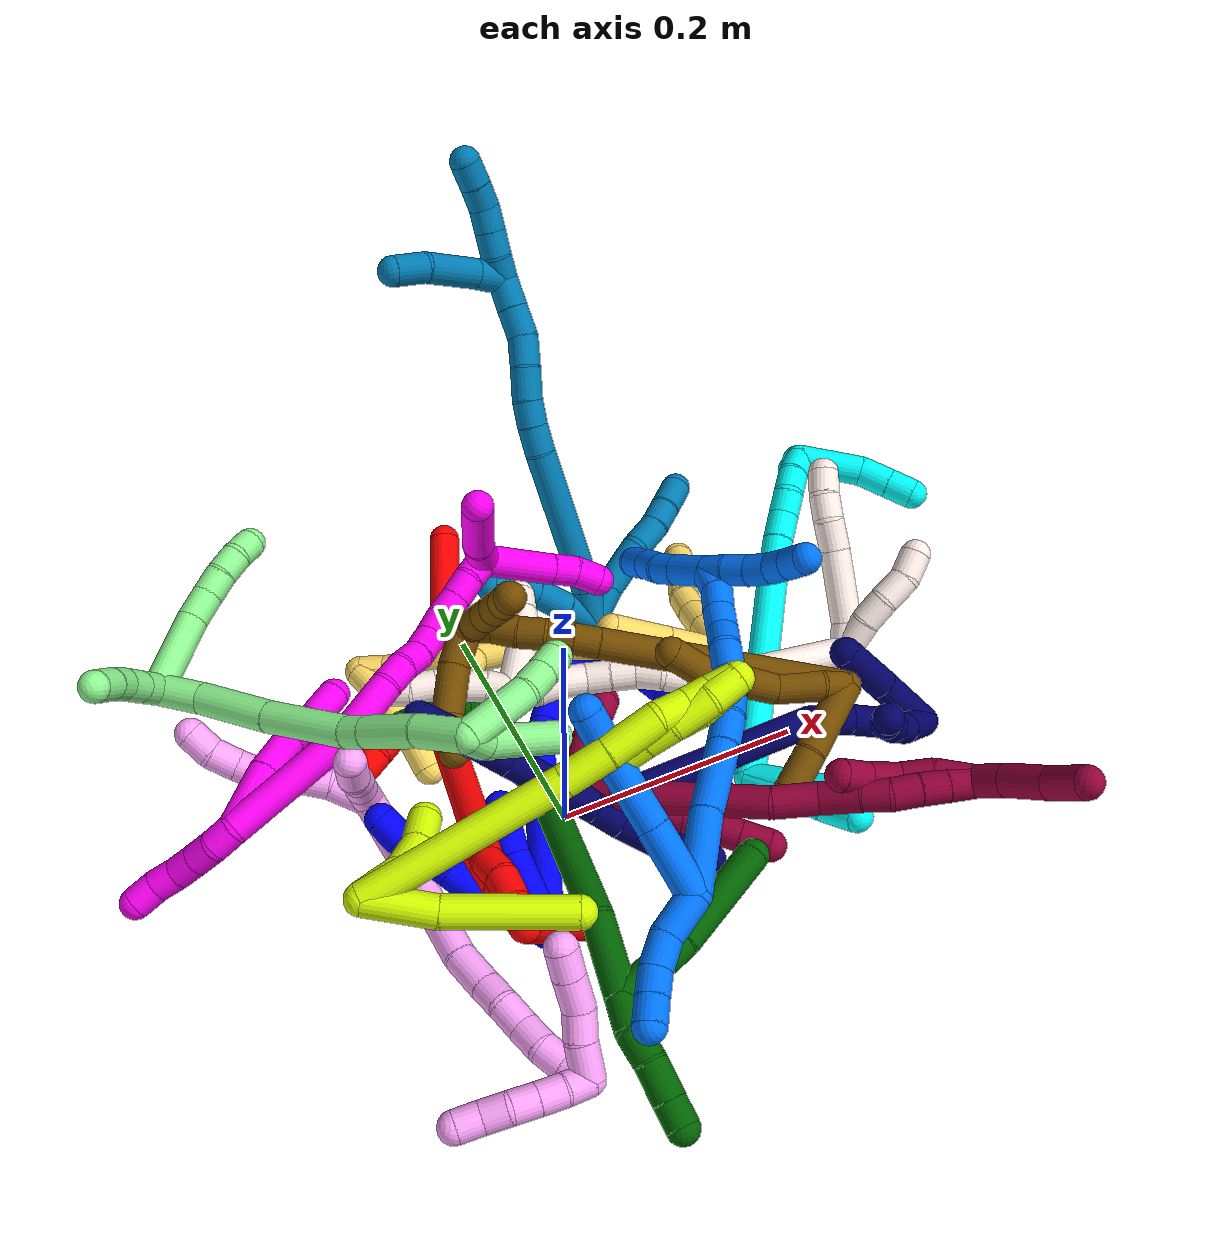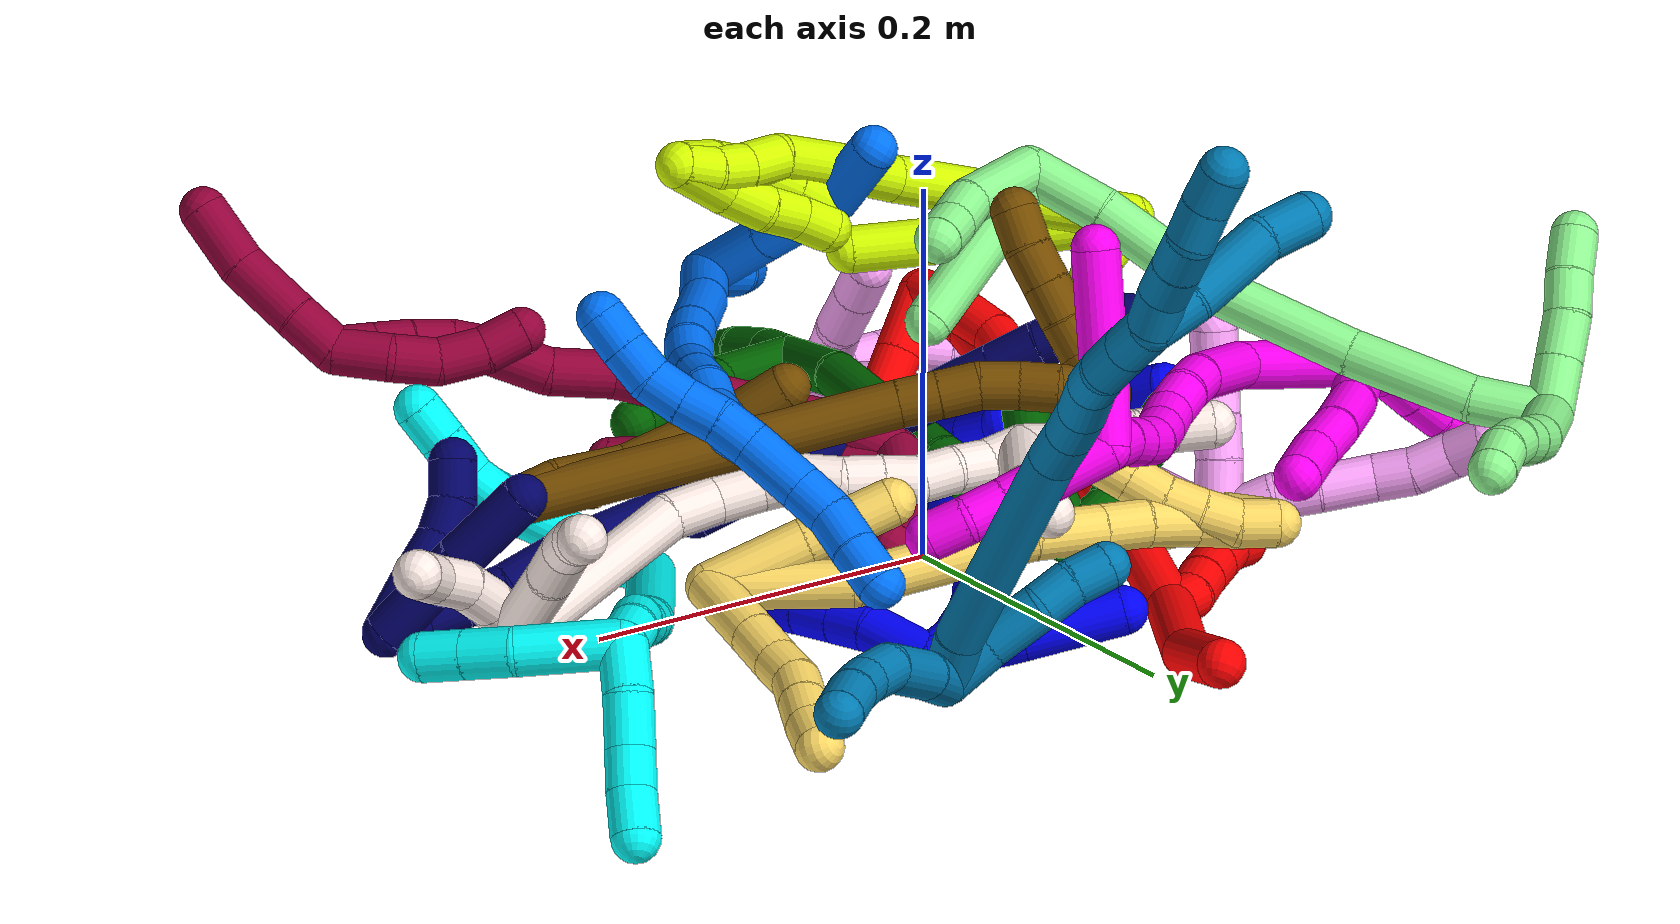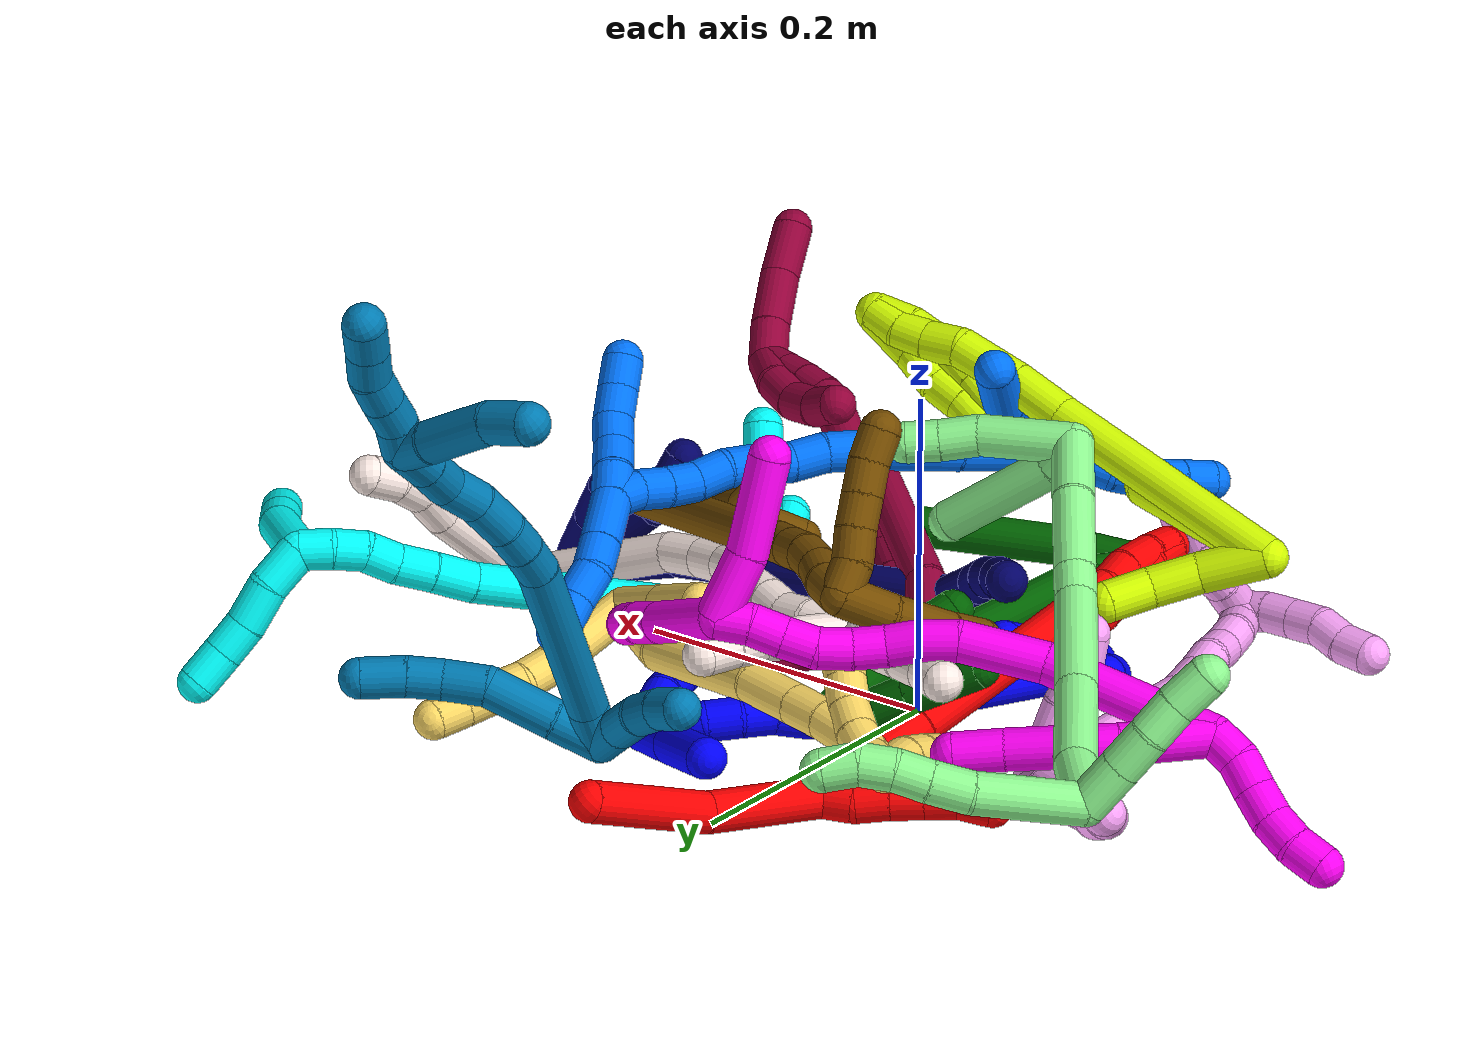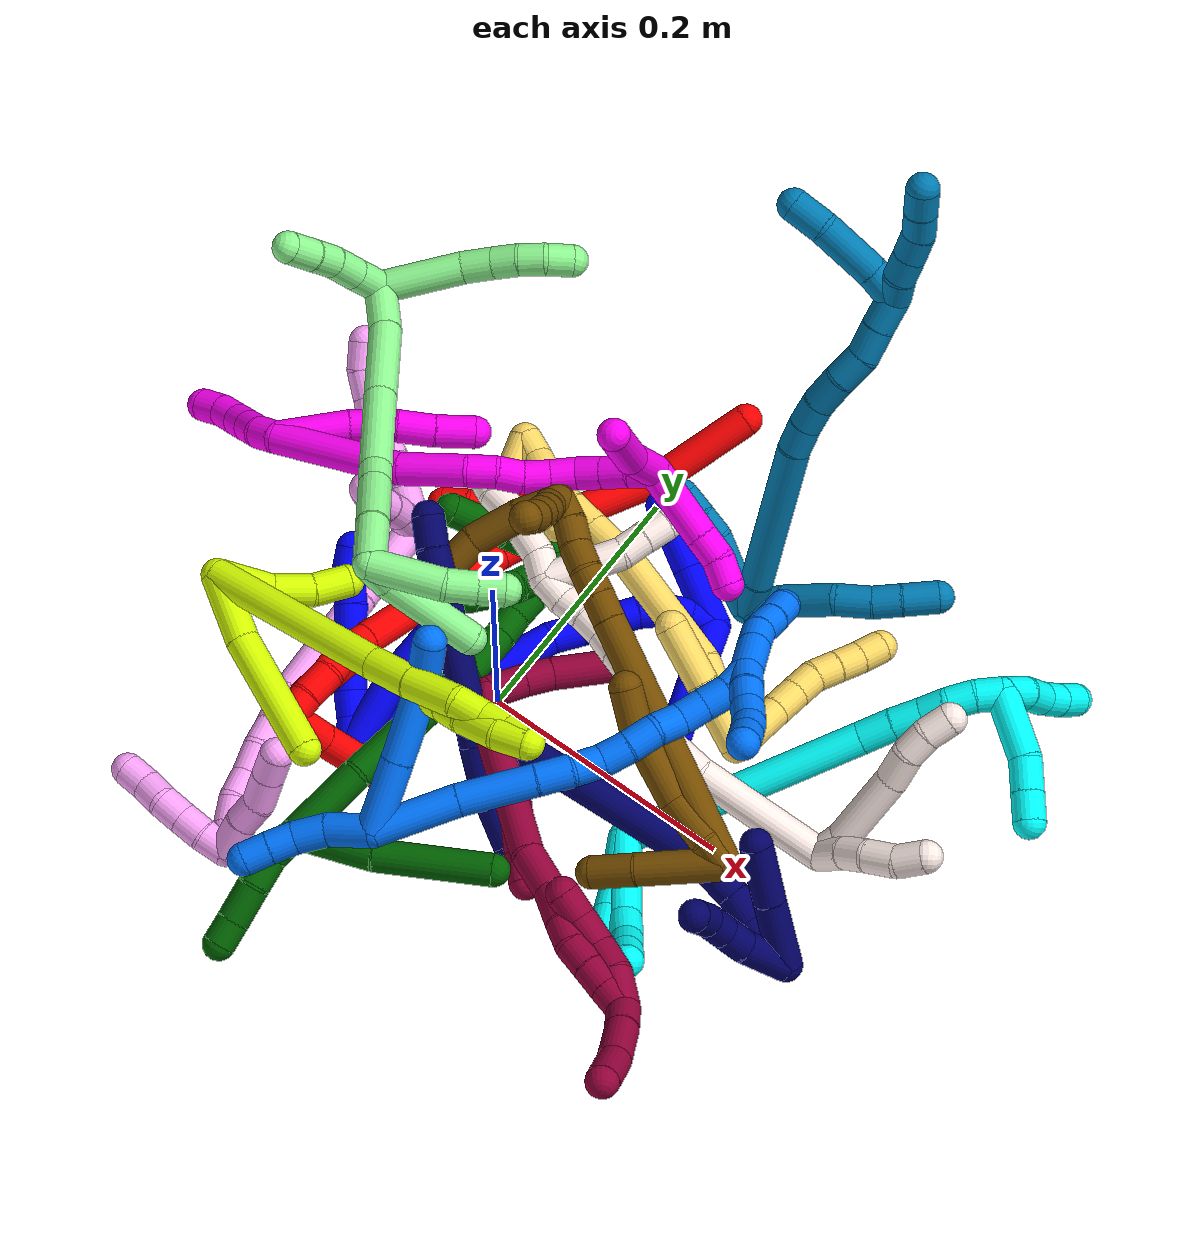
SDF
<sdf version="1.7">
 <world name="default">
  <plugin name="TubeGeneratorPlugin" filename="libtube_generator_plugin.so"/>
  <model name="photoneo_s_sensor">
   <static>1</static>
   <pose>0 0 2 1.57079 1.57079 3.14159</pose>
   <link name="link">
    <inertial><mass>0.1</mass></inertial>
    <sensor name="sensor" type="depth">
     <update_rate>30</update_rate>
     <camera>
      <horizontal_fov>1.22</horizontal_fov>
      <image><width>1920</width><height>1200</height><format>B8G8R8</format></image>
      <clip><near>0.1</near><far>4</far></clip>
      <depth_camera><output>points</output></depth_camera>
     </camera>
     <plugin name="camera_plugin" filename="libgazebo_ros_depth_camera.so">
      <baseline>0.2</baseline>
      <alwaysOn>1</alwaysOn>
      <updateRate>0.0</updateRate>
      <cameraName>camera_ir</cameraName>
      <imageTopicName>/camera/color/image_raw</imageTopicName>
      <cameraInfoTopicName>/camera/color/camera_info</cameraInfoTopicName>
      <depthImageTopicName>/camera/depth/image_raw</depthImageTopicName>
      <depthImageCameraInfoTopicName>/camera/depth/camera_info</depthImageCameraInfoTopicName>
      <pointCloudTopicName>/camera/depth/points</pointCloudTopicName>
      <frameName>fr_optical</frameName>
      <pointCloudCutoff>0.1</pointCloudCutoff>
      <pointCloudCutoffMax>2.0</pointCloudCutoffMax>
      <distortionK1>0</distortionK1>
      <distortionK2>0</distortionK2>
      <distortionK3>0</distortionK3>
      <distortionT1>0</distortionT1>
      <distortionT2>0</distortionT2>
      <CxPrime>0</CxPrime>
      <Cx>0</Cx>
      <Cy>0</Cy>
      <focalLength>0</focalLength>
      <hackBaseline>0</hackBaseline>
     </plugin>
    </sensor>
   </link>
  </model>
  <gravity>0 0 -9.8</gravity>
  <magnetic_field>6e-06 2.3e-05 -4.2e-05</magnetic_field>
  <atmosphere type="adiabatic"/>
  <physics name="default_physics" default="0" type="ode">
   <max_step_size>0.003</max_step_size>
   <real_time_factor>1</real_time_factor>
   <real_time_update_rate>1000</real_time_update_rate>
   <max_contacts>10000</max_contacts>
   <ode>
    <solver>
     <type>quick</type>
     <iters>100</iters>
     <sor>1.3</sor>
     <use_dynamic_moi_rescaling>0</use_dynamic_moi_rescaling>
    </solver>
    <constraints>
     <contact_max_correcting_vel>0</contact_max_correcting_vel>
     <contact_surface_layer>0.001</contact_surface_layer>
     <cfm>0</cfm>
     <erp>0.2</erp>
    </constraints>
   </ode>
  </physics>
  <scene><ambient>0.4 0.4 0.4 1</ambient><background>0.7 0.7 0.7 1</background><shadows>0</shadows></scene>
  <audio><device>default</device></audio>
  <spherical_coordinates>
   <surface_model>EARTH_WGS84</surface_model>
   <latitude_deg>0</latitude_deg>
   <longitude_deg>0</longitude_deg>
   <elevation>0</elevation>
   <heading_deg>0</heading_deg>
  </spherical_coordinates>
  <model name="bin">
   <static>1</static>
   <link name="bottom">
    <collision name="collision-bottom">
     <pose>0 0 -0.01 0 -0 0</pose>
     <geometry><box><size>0.8 0.6 0.02</size></box></geometry>
     <surface>
      <friction><ode><mu>100</mu><mu2>100</mu2></ode></friction>
      <contact><collide_bitmask>65535</collide_bitmask></contact>
     </surface>
    </collision>
   </link>
   <link name="west_wall">
    <collision name="collision-west_wall">
     <pose>-0.41 0 0.1 0 -0 0</pose>
     <geometry><box><size>0.02 0.6 0.2</size></box></geometry>
     <surface>
      <friction><ode><mu>100</mu><mu2>100</mu2></ode></friction>
      <contact><collide_bitmask>65535</collide_bitmask></contact>
     </surface>
    </collision>
   </link>
   <link name="east_wall">
    <collision name="collision-east_wall">
     <pose>0.41 0 0.1 0 -0 0</pose>
     <geometry><box><size>0.02 0.6 0.2</size></box></geometry>
     <surface>
      <friction><ode><mu>100</mu><mu2>100</mu2></ode></friction>
      <contact><collide_bitmask>65535</collide_bitmask></contact>
     </surface>
    </collision>
   </link>
   <link name="south_wall">
    <collision name="collision-south_wall">
     <pose>0 -0.31 0.1 0 -0 0</pose>
     <geometry><box><size>0.8 0.02 0.2</size></box></geometry>
     <surface>
      <friction><ode><mu>100</mu><mu2>100</mu2></ode></friction>
      <contact><collide_bitmask>65535</collide_bitmask></contact>
     </surface>
    </collision>
   </link>
   <link name="north_wall">
    <collision name="collision-north_wall">
     <pose>0 0.31 0.1 0 -0 0</pose>
     <geometry><box><size>0.8 0.02 0.2</size></box></geometry>
     <surface>
      <friction><ode><mu>100</mu><mu2>100</mu2></ode></friction>
      <contact><collide_bitmask>65535</collide_bitmask></contact>
     </surface>
    </collision>
   </link>
  </model>
  <model name="1">
   <static>0</static>
   <link name="1">
    <collision name="collision-cylinder-e_1_2_8">
     <pose>0.002054 0.002722 0.010445 -0.254967 0.188075 -0.024177</pose>
     <geometry><cylinder><radius>0.0125</radius><length>0.021976</length></cylinder></geometry>
     <surface>
      <friction><ode><mu>1.16</mu><mu2>1.16</mu2><slip1>0</slip1><slip2>0</slip2></ode></friction>
      <contact><ode><kp>1e+06</kp><kd>1</kd><max_vel>0</max_vel><min_depth>0.001</min_depth></ode></contact>
     </surface>
    </collision>
    <visual name="visual-cylinder-e_1_2_8">
     <pose>0.002054 0.002722 0.010445 -0.254967 0.188075 -0.024177</pose>
     <geometry><cylinder><radius>0.0125</radius><length>0.021976</length></cylinder></geometry>
     <material><ambient>0 0 1 1</ambient></material>
    </visual>
    <collision name="collision-cylinder-e_2_8_9">
     <pose>0.005904 0.005951 0.031348 -0.048331 0.169845 -0.004115</pose>
     <geometry><cylinder><radius>0.0125</radius><length>0.021245</length></cylinder></geometry>
     <surface>
      <friction><ode><mu>1.16</mu><mu2>1.16</mu2><slip1>0</slip1><slip2>0</slip2></ode></friction>
      <contact><ode><kp>1e+06</kp><kd>1</kd><max_vel>0</max_vel><min_depth>0.001</min_depth></ode></contact>
     </surface>
    </collision>
    <visual name="visual-cylinder-e_2_8_9">
     <pose>0.005904 0.005951 0.031348 -0.048331 0.169845 -0.004115</pose>
     <geometry><cylinder><radius>0.0125</radius><length>0.021245</length></cylinder></geometry>
     <material><ambient>0 0 1 1</ambient></material>
    </visual>
    <collision name="collision-cylinder-e_3_9_10">
     <pose>0.015096 0.006355 0.062318 0.00493 0.346066 0.000862</pose>
     <geometry><cylinder><radius>0.0125</radius><length>0.043612</length></cylinder></geometry>
     <surface>
      <friction><ode><mu>1.16</mu><mu2>1.16</mu2><slip1>0</slip1><slip2>0</slip2></ode></friction>
      <contact><ode><kp>1e+06</kp><kd>1</kd><max_vel>0</max_vel><min_depth>0.001</min_depth></ode></contact>
     </surface>
    </collision>
    <visual name="visual-cylinder-e_3_9_10">
     <pose>0.015096 0.006355 0.062318 0.00493 0.346066 0.000862</pose>
     <geometry><cylinder><radius>0.0125</radius><length>0.043612</length></cylinder></geometry>
     <material><ambient>0 0 1 1</ambient></material>
    </visual>
    <collision name="collision-cylinder-e_4_10_11">
     <pose>0.026235 0.006258 0.092764 -0.000386 0.36033 -7e-05</pose>
     <geometry><cylinder><radius>0.0125</radius><length>0.021229</length></cylinder></geometry>
     <surface>
      <friction><ode><mu>1.16</mu><mu2>1.16</mu2><slip1>0</slip1><slip2>0</slip2></ode></friction>
      <contact><ode><kp>1e+06</kp><kd>1</kd><max_vel>0</max_vel><min_depth>0.001</min_depth></ode></contact>
     </surface>
    </collision>
    <visual name="visual-cylinder-e_4_10_11">
     <pose>0.026235 0.006258 0.092764 -0.000386 0.36033 -7e-05</pose>
     <geometry><cylinder><radius>0.0125</radius><length>0.021229</length></cylinder></geometry>
     <material><ambient>0 0 1 1</ambient></material>
    </visual>
    <collision name="collision-cylinder-e_5_11_12">
     <pose>0.032241 0.005807 0.112907 0.044515 0.21787 0.004869</pose>
     <geometry><cylinder><radius>0.0125</radius><length>0.020936</length></cylinder></geometry>
     <surface>
      <friction><ode><mu>1.16</mu><mu2>1.16</mu2><slip1>0</slip1><slip2>0</slip2></ode></friction>
      <contact><ode><kp>1e+06</kp><kd>1</kd><max_vel>0</max_vel><min_depth>0.001</min_depth></ode></contact>
     </surface>
    </collision>
    <visual name="visual-cylinder-e_5_11_12">
     <pose>0.032241 0.005807 0.112907 0.044515 0.21787 0.004869</pose>
     <geometry><cylinder><radius>0.0125</radius><length>0.020936</length></cylinder></geometry>
     <material><ambient>0 0 1 1</ambient></material>
    </visual>
    <collision name="collision-cylinder-e_6_12_6">
     <pose>0.039496 0.006493 0.132285 -0.12384 0.495475 -0.031361</pose>
     <geometry><cylinder><radius>0.0125</radius><length>0.021002</length></cylinder></geometry>
     <surface>
      <friction><ode><mu>1.16</mu><mu2>1.16</mu2><slip1>0</slip1><slip2>0</slip2></ode></friction>
      <contact><ode><kp>1e+06</kp><kd>1</kd><max_vel>0</max_vel><min_depth>0.001</min_depth></ode></contact>
     </surface>
    </collision>
    <visual name="visual-cylinder-e_6_12_6">
     <pose>0.039496 0.006493 0.132285 -0.12384 0.495475 -0.031361</pose>
     <geometry><cylinder><radius>0.0125</radius><length>0.021002</length></cylinder></geometry>
     <material><ambient>0 0 1 1</ambient></material>
    </visual>
    <collision name="collision-cylinder-e_1_2_13">
     <pose>0.023275 0.005944 0.020161 -0.286705 0.836287 -0.128101</pose>
     <geometry><cylinder><radius>0.0125</radius><length>0.062723</length></cylinder></geometry>
     <surface>
      <friction><ode><mu>1.16</mu><mu2>1.16</mu2><slip1>0</slip1><slip2>0</slip2></ode></friction>
      <contact><ode><kp>1e+06</kp><kd>1</kd><max_vel>0</max_vel><min_depth>0.001</min_depth></ode></contact>
     </surface>
    </collision>
    <visual name="visual-cylinder-e_1_2_13">
     <pose>0.023275 0.005944 0.020161 -0.286705 0.836287 -0.128101</pose>
     <geometry><cylinder><radius>0.0125</radius><length>0.062723</length></cylinder></geometry>
     <material><ambient>0 0 1 1</ambient></material>
    </visual>
    <collision name="collision-cylinder-e_2_13_5">
     <pose>0.062104 0.016268 0.049613 -0.440566 0.987166 -0.239778</pose>
     <geometry><cylinder><radius>0.0125</radius><length>0.037277</length></cylinder></geometry>
     <surface>
      <friction><ode><mu>1.16</mu><mu2>1.16</mu2><slip1>0</slip1><slip2>0</slip2></ode></friction>
      <contact><ode><kp>1e+06</kp><kd>1</kd><max_vel>0</max_vel><min_depth>0.001</min_depth></ode></contact>
     </surface>
    </collision>
    <visual name="visual-cylinder-e_2_13_5">
     <pose>0.062104 0.016268 0.049613 -0.440566 0.987166 -0.239778</pose>
     <geometry><cylinder><radius>0.0125</radius><length>0.037277</length></cylinder></geometry>
     <material><ambient>0 0 1 1</ambient></material>
    </visual>
    <collision name="collision-cylinder-e_1_2_14">
     <pose>0.006472 0.0076 0.002009 -1.31233 0.688785 -0.538926</pose>
     <geometry><cylinder><radius>0.0125</radius><length>0.020365</length></cylinder></geometry>
     <surface>
      <friction><ode><mu>1.16</mu><mu2>1.16</mu2><slip1>0</slip1><slip2>0</slip2></ode></friction>
      <contact><ode><kp>1e+06</kp><kd>1</kd><max_vel>0</max_vel><min_depth>0.001</min_depth></ode></contact>
     </surface>
    </collision>
    <visual name="visual-cylinder-e_1_2_14">
     <pose>0.006472 0.0076 0.002009 -1.31233 0.688785 -0.538926</pose>
     <geometry><cylinder><radius>0.0125</radius><length>0.020365</length></cylinder></geometry>
     <material><ambient>0 0 1 1</ambient></material>
    </visual>
    <collision name="collision-cylinder-e_2_14_15">
     <pose>0.049305 0.043095 0.015709 -1.17394 0.876943 -0.604697</pose>
     <geometry><cylinder><radius>0.0125</radius><length>0.094593</length></cylinder></geometry>
     <surface>
      <friction><ode><mu>1.16</mu><mu2>1.16</mu2><slip1>0</slip1><slip2>0</slip2></ode></friction>
      <contact><ode><kp>1e+06</kp><kd>1</kd><max_vel>0</max_vel><min_depth>0.001</min_depth></ode></contact>
     </surface>
    </collision>
    <visual name="visual-cylinder-e_2_14_15">
     <pose>0.049305 0.043095 0.015709 -1.17394 0.876943 -0.604697</pose>
     <geometry><cylinder><radius>0.0125</radius><length>0.094593</length></cylinder></geometry>
     <material><ambient>0 0 1 1</ambient></material>
    </visual>
    <collision name="collision-cylinder-e_3_15_16">
     <pose>0.107653 0.087066 0.033964 -1.18315 0.902364 -0.629397</pose>
     <geometry><cylinder><radius>0.0125</radius><length>0.056034</length></cylinder></geometry>
     <surface>
      <friction><ode><mu>1.16</mu><mu2>1.16</mu2><slip1>0</slip1><slip2>0</slip2></ode></friction>
      <contact><ode><kp>1e+06</kp><kd>1</kd><max_vel>0</max_vel><min_depth>0.001</min_depth></ode></contact>
     </surface>
    </collision>
    <visual name="visual-cylinder-e_3_15_16">
     <pose>0.107653 0.087066 0.033964 -1.18315 0.902364 -0.629397</pose>
     <geometry><cylinder><radius>0.0125</radius><length>0.056034</length></cylinder></geometry>
     <material><ambient>0 0 1 1</ambient></material>
    </visual>
    <collision name="collision-cylinder-e_4_16_17">
     <pose>0.138603 0.111349 0.040673 -1.55312 0.8292 -0.816244</pose>
     <geometry><cylinder><radius>0.0125</radius><length>0.024307</length></cylinder></geometry>
     <surface>
      <friction><ode><mu>1.16</mu><mu2>1.16</mu2><slip1>0</slip1><slip2>0</slip2></ode></friction>
      <contact><ode><kp>1e+06</kp><kd>1</kd><max_vel>0</max_vel><min_depth>0.001</min_depth></ode></contact>
     </surface>
    </collision>
    <visual name="visual-cylinder-e_4_16_17">
     <pose>0.138603 0.111349 0.040673 -1.55312 0.8292 -0.816244</pose>
     <geometry><cylinder><radius>0.0125</radius><length>0.024307</length></cylinder></geometry>
     <material><ambient>0 0 1 1</ambient></material>
    </visual>
    <collision name="collision-cylinder-e_5_17_18">
     <pose>0.158575 0.12434 0.040845 -1.5651 1.16102 -1.1558</pose>
     <geometry><cylinder><radius>0.0125</radius><length>0.024009</length></cylinder></geometry>
     <surface>
      <friction><ode><mu>1.16</mu><mu2>1.16</mu2><slip1>0</slip1><slip2>0</slip2></ode></friction>
      <contact><ode><kp>1e+06</kp><kd>1</kd><max_vel>0</max_vel><min_depth>0.001</min_depth></ode></contact>
     </surface>
    </collision>
    <visual name="visual-cylinder-e_5_17_18">
     <pose>0.158575 0.12434 0.040845 -1.5651 1.16102 -1.1558</pose>
     <geometry><cylinder><radius>0.0125</radius><length>0.024009</length></cylinder></geometry>
     <material><ambient>0 0 1 1</ambient></material>
    </visual>
    <collision name="collision-cylinder-e_6_18_19">
     <pose>0.17763 0.135084 0.040935 -1.5602 0.932976 -0.924487</pose>
     <geometry><cylinder><radius>0.0125</radius><length>0.020025</length></cylinder></geometry>
     <surface>
      <friction><ode><mu>1.16</mu><mu2>1.16</mu2><slip1>0</slip1><slip2>0</slip2></ode></friction>
      <contact><ode><kp>1e+06</kp><kd>1</kd><max_vel>0</max_vel><min_depth>0.001</min_depth></ode></contact>
     </surface>
    </collision>
    <visual name="visual-cylinder-e_6_18_19">
     <pose>0.17763 0.135084 0.040935 -1.5602 0.932976 -0.924487</pose>
     <geometry><cylinder><radius>0.0125</radius><length>0.020025</length></cylinder></geometry>
     <material><ambient>0 0 1 1</ambient></material>
    </visual>
    <collision name="collision-cylinder-e_7_19_20">
     <pose>0.193518 0.147495 0.0393 -1.82828 0.866145 -1.08063</pose>
     <geometry><cylinder><radius>0.0125</radius><length>0.020592</length></cylinder></geometry>
     <surface>
      <friction><ode><mu>1.16</mu><mu2>1.16</mu2><slip1>0</slip1><slip2>0</slip2></ode></friction>
      <contact><ode><kp>1e+06</kp><kd>1</kd><max_vel>0</max_vel><min_depth>0.001</min_depth></ode></contact>
     </surface>
    </collision>
    <visual name="visual-cylinder-e_7_19_20">
     <pose>0.193518 0.147495 0.0393 -1.82828 0.866145 -1.08063</pose>
     <geometry><cylinder><radius>0.0125</radius><length>0.020592</length></cylinder></geometry>
     <material><ambient>0 0 1 1</ambient></material>
    </visual>
    <collision name="collision-cylinder-e_8_20_21">
     <pose>0.207212 0.160894 0.033403 -2.11431 0.624357 -1.03926</pose>
     <geometry><cylinder><radius>0.0125</radius><length>0.020015</length></cylinder></geometry>
     <surface>
      <friction><ode><mu>1.16</mu><mu2>1.16</mu2><slip1>0</slip1><slip2>0</slip2></ode></friction>
      <contact><ode><kp>1e+06</kp><kd>1</kd><max_vel>0</max_vel><min_depth>0.001</min_depth></ode></contact>
     </surface>
    </collision>
    <visual name="visual-cylinder-e_8_20_21">
     <pose>0.207212 0.160894 0.033403 -2.11431 0.624357 -1.03926</pose>
     <geometry><cylinder><radius>0.0125</radius><length>0.020015</length></cylinder></geometry>
     <material><ambient>0 0 1 1</ambient></material>
    </visual>
    <collision name="collision-cylinder-e_9_21_1">
     <pose>0.218787 0.173071 0.02284 -2.45389 0.607456 -1.43801</pose>
     <geometry><cylinder><radius>0.0125</radius><length>0.020061</length></cylinder></geometry>
     <surface>
      <friction><ode><mu>1.16</mu><mu2>1.16</mu2><slip1>0</slip1><slip2>0</slip2></ode></friction>
      <contact><ode><kp>1e+06</kp><kd>1</kd><max_vel>0</max_vel><min_depth>0.001</min_depth></ode></contact>
     </surface>
    </collision>
    <visual name="visual-cylinder-e_9_21_1">
     <pose>0.218787 0.173071 0.02284 -2.45389 0.607456 -1.43801</pose>
     <geometry><cylinder><radius>0.0125</radius><length>0.020061</length></cylinder></geometry>
     <material><ambient>0 0 1 1</ambient></material>
    </visual>
    <collision name="collision-cylinder-e_1_1_22">
     <pose>0.222292 0.176584 0.040041 0.072647 -0.093696 -0.003407</pose>
     <geometry><cylinder><radius>0.0125</radius><length>0.047463</length></cylinder></geometry>
     <surface>
      <friction><ode><mu>1.16</mu><mu2>1.16</mu2><slip1>0</slip1><slip2>0</slip2></ode></friction>
      <contact><ode><kp>1e+06</kp><kd>1</kd><max_vel>0</max_vel><min_depth>0.001</min_depth></ode></contact>
     </surface>
    </collision>
    <visual name="visual-cylinder-e_1_1_22">
     <pose>0.222292 0.176584 0.040041 0.072647 -0.093696 -0.003407</pose>
     <geometry><cylinder><radius>0.0125</radius><length>0.047463</length></cylinder></geometry>
     <material><ambient>0 0 1 1</ambient></material>
    </visual>
    <collision name="collision-cylinder-e_2_22_4">
     <pose>0.217973 0.17266 0.089697 0.084463 -0.079967 -0.003381</pose>
     <geometry><cylinder><radius>0.0125</radius><length>0.052537</length></cylinder></geometry>
     <surface>
      <friction><ode><mu>1.16</mu><mu2>1.16</mu2><slip1>0</slip1><slip2>0</slip2></ode></friction>
      <contact><ode><kp>1e+06</kp><kd>1</kd><max_vel>0</max_vel><min_depth>0.001</min_depth></ode></contact>
     </surface>
    </collision>
    <visual name="visual-cylinder-e_2_22_4">
     <pose>0.217973 0.17266 0.089697 0.084463 -0.079967 -0.003381</pose>
     <geometry><cylinder><radius>0.0125</radius><length>0.052537</length></cylinder></geometry>
     <material><ambient>0 0 1 1</ambient></material>
    </visual>
    <collision name="collision-cylinder-e_1_1_23">
     <pose>0.220732 0.166208 0.002647 2.42311 -0.202939 -0.529524</pose>
     <geometry><cylinder><radius>0.0125</radius><length>0.037509</length></cylinder></geometry>
     <surface>
      <friction><ode><mu>1.16</mu><mu2>1.16</mu2><slip1>0</slip1><slip2>0</slip2></ode></friction>
      <contact><ode><kp>1e+06</kp><kd>1</kd><max_vel>0</max_vel><min_depth>0.001</min_depth></ode></contact>
     </surface>
    </collision>
    <visual name="visual-cylinder-e_1_1_23">
     <pose>0.220732 0.166208 0.002647 2.42311 -0.202939 -0.529524</pose>
     <geometry><cylinder><radius>0.0125</radius><length>0.037509</length></cylinder></geometry>
     <material><ambient>0 0 1 1</ambient></material>
    </visual>
    <collision name="collision-cylinder-e_2_23_24">
     <pose>0.213208 0.149193 -0.019344 2.59892 -0.374296 -1.19529</pose>
     <geometry><cylinder><radius>0.0125</radius><length>0.020484</length></cylinder></geometry>
     <surface>
      <friction><ode><mu>1.16</mu><mu2>1.16</mu2><slip1>0</slip1><slip2>0</slip2></ode></friction>
      <contact><ode><kp>1e+06</kp><kd>1</kd><max_vel>0</max_vel><min_depth>0.001</min_depth></ode></contact>
     </surface>
    </collision>
    <visual name="visual-cylinder-e_2_23_24">
     <pose>0.213208 0.149193 -0.019344 2.59892 -0.374296 -1.19529</pose>
     <geometry><cylinder><radius>0.0125</radius><length>0.020484</length></cylinder></geometry>
     <material><ambient>0 0 1 1</ambient></material>
    </visual>
    <collision name="collision-cylinder-e_3_24_25">
     <pose>0.205513 0.139059 -0.036349 2.609 -0.367364 -1.19579</pose>
     <geometry><cylinder><radius>0.0125</radius><length>0.021993</length></cylinder></geometry>
     <surface>
      <friction><ode><mu>1.16</mu><mu2>1.16</mu2><slip1>0</slip1><slip2>0</slip2></ode></friction>
      <contact><ode><kp>1e+06</kp><kd>1</kd><max_vel>0</max_vel><min_depth>0.001</min_depth></ode></contact>
     </surface>
    </collision>
    <visual name="visual-cylinder-e_3_24_25">
     <pose>0.205513 0.139059 -0.036349 2.609 -0.367364 -1.19579</pose>
     <geometry><cylinder><radius>0.0125</radius><length>0.021993</length></cylinder></geometry>
     <material><ambient>0 0 1 1</ambient></material>
    </visual>
    <collision name="collision-cylinder-e_4_25_3">
     <pose>0.197932 0.129302 -0.053332 2.63233 -0.371466 -1.25056</pose>
     <geometry><cylinder><radius>0.0125</radius><length>0.020014</length></cylinder></geometry>
     <surface>
      <friction><ode><mu>1.16</mu><mu2>1.16</mu2><slip1>0</slip1><slip2>0</slip2></ode></friction>
      <contact><ode><kp>1e+06</kp><kd>1</kd><max_vel>0</max_vel><min_depth>0.001</min_depth></ode></contact>
     </surface>
    </collision>
    <visual name="visual-cylinder-e_4_25_3">
     <pose>0.197932 0.129302 -0.053332 2.63233 -0.371466 -1.25056</pose>
     <geometry><cylinder><radius>0.0125</radius><length>0.020014</length></cylinder></geometry>
     <material><ambient>0 0 1 1</ambient></material>
    </visual>
    <collision name="collision-sphere-3">
     <pose>0.194299 0.124756 -0.061473 0 -0 0</pose>
     <geometry><sphere><radius>0.0125</radius></sphere></geometry>
     <surface>
      <friction><ode><mu>1.16</mu><mu2>1.16</mu2><slip1>0</slip1><slip2>0</slip2></ode></friction>
      <contact><ode><kp>1e+06</kp><kd>1</kd><max_vel>0</max_vel><min_depth>0.001</min_depth></ode></contact>
     </surface>
    </collision>
    <visual name="visual-sphere-3">
     <pose>0.194299 0.124756 -0.061473 0 -0 0</pose>
     <geometry><sphere><radius>0.0125</radius></sphere></geometry>
     <material><ambient>0 0 1 1</ambient></material>
    </visual>
    <collision name="collision-sphere-25">
     <pose>0.201564 0.133848 -0.04519 0 -0 0</pose>
     <geometry><sphere><radius>0.0125</radius></sphere></geometry>
     <surface>
      <friction><ode><mu>1.16</mu><mu2>1.16</mu2><slip1>0</slip1><slip2>0</slip2></ode></friction>
      <contact><ode><kp>1e+06</kp><kd>1</kd><max_vel>0</max_vel><min_depth>0.001</min_depth></ode></contact>
     </surface>
    </collision>
    <visual name="visual-sphere-25">
     <pose>0.201564 0.133848 -0.04519 0 -0 0</pose>
     <geometry><sphere><radius>0.0125</radius></sphere></geometry>
     <material><ambient>0 0 1 1</ambient></material>
    </visual>
    <collision name="collision-sphere-24">
     <pose>0.209463 0.14427 -0.027508 0 -0 0</pose>
     <geometry><sphere><radius>0.0125</radius></sphere></geometry>
     <surface>
      <friction><ode><mu>1.16</mu><mu2>1.16</mu2><slip1>0</slip1><slip2>0</slip2></ode></friction>
      <contact><ode><kp>1e+06</kp><kd>1</kd><max_vel>0</max_vel><min_depth>0.001</min_depth></ode></contact>
     </surface>
    </collision>
    <visual name="visual-sphere-24">
     <pose>0.209463 0.14427 -0.027508 0 -0 0</pose>
     <geometry><sphere><radius>0.0125</radius></sphere></geometry>
     <material><ambient>0 0 1 1</ambient></material>
    </visual>
    <collision name="collision-sphere-23">
     <pose>0.216952 0.154116 -0.011181 0 -0 0</pose>
     <geometry><sphere><radius>0.0125</radius></sphere></geometry>
     <surface>
      <friction><ode><mu>1.16</mu><mu2>1.16</mu2><slip1>0</slip1><slip2>0</slip2></ode></friction>
      <contact><ode><kp>1e+06</kp><kd>1</kd><max_vel>0</max_vel><min_depth>0.001</min_depth></ode></contact>
     </surface>
    </collision>
    <visual name="visual-sphere-23">
     <pose>0.216952 0.154116 -0.011181 0 -0 0</pose>
     <geometry><sphere><radius>0.0125</radius></sphere></geometry>
     <material><ambient>0 0 1 1</ambient></material>
    </visual>
    <collision name="collision-sphere-4">
     <pose>0.215875 0.170451 0.115789 0 -0 0</pose>
     <geometry><sphere><radius>0.0125</radius></sphere></geometry>
     <surface>
      <friction><ode><mu>1.16</mu><mu2>1.16</mu2><slip1>0</slip1><slip2>0</slip2></ode></friction>
      <contact><ode><kp>1e+06</kp><kd>1</kd><max_vel>0</max_vel><min_depth>0.001</min_depth></ode></contact>
     </surface>
    </collision>
    <visual name="visual-sphere-4">
     <pose>0.215875 0.170451 0.115789 0 -0 0</pose>
     <geometry><sphere><radius>0.0125</radius></sphere></geometry>
     <material><ambient>0 0 1 1</ambient></material>
    </visual>
    <collision name="collision-sphere-22">
     <pose>0.220071 0.174869 0.063606 0 -0 0</pose>
     <geometry><sphere><radius>0.0125</radius></sphere></geometry>
     <surface>
      <friction><ode><mu>1.16</mu><mu2>1.16</mu2><slip1>0</slip1><slip2>0</slip2></ode></friction>
      <contact><ode><kp>1e+06</kp><kd>1</kd><max_vel>0</max_vel><min_depth>0.001</min_depth></ode></contact>
     </surface>
    </collision>
    <visual name="visual-sphere-22">
     <pose>0.220071 0.174869 0.063606 0 -0 0</pose>
     <geometry><sphere><radius>0.0125</radius></sphere></geometry>
     <material><ambient>0 0 1 1</ambient></material>
    </visual>
    <collision name="collision-sphere-1">
     <pose>0.224512 0.178299 0.016476 0 -0 0</pose>
     <geometry><sphere><radius>0.0125</radius></sphere></geometry>
     <surface>
      <friction><ode><mu>1.16</mu><mu2>1.16</mu2><slip1>0</slip1><slip2>0</slip2></ode></friction>
      <contact><ode><kp>1e+06</kp><kd>1</kd><max_vel>0</max_vel><min_depth>0.001</min_depth></ode></contact>
     </surface>
    </collision>
    <visual name="visual-sphere-1">
     <pose>0.224512 0.178299 0.016476 0 -0 0</pose>
     <geometry><sphere><radius>0.0125</radius></sphere></geometry>
     <material><ambient>0 0 1 1</ambient></material>
    </visual>
    <collision name="collision-sphere-21">
     <pose>0.213062 0.167844 0.029204 0 -0 0</pose>
     <geometry><sphere><radius>0.0125</radius></sphere></geometry>
     <surface>
      <friction><ode><mu>1.16</mu><mu2>1.16</mu2><slip1>0</slip1><slip2>0</slip2></ode></friction>
      <contact><ode><kp>1e+06</kp><kd>1</kd><max_vel>0</max_vel><min_depth>0.001</min_depth></ode></contact>
     </surface>
    </collision>
    <visual name="visual-sphere-21">
     <pose>0.213062 0.167844 0.029204 0 -0 0</pose>
     <geometry><sphere><radius>0.0125</radius></sphere></geometry>
     <material><ambient>0 0 1 1</ambient></material>
    </visual>
    <collision name="collision-sphere-12">
     <pose>0.034503 0.005352 0.123117 0 -0 0</pose>
     <geometry><sphere><radius>0.0125</radius></sphere></geometry>
     <surface>
      <friction><ode><mu>1.16</mu><mu2>1.16</mu2><slip1>0</slip1><slip2>0</slip2></ode></friction>
      <contact><ode><kp>1e+06</kp><kd>1</kd><max_vel>0</max_vel><min_depth>0.001</min_depth></ode></contact>
     </surface>
    </collision>
    <visual name="visual-sphere-12">
     <pose>0.034503 0.005352 0.123117 0 -0 0</pose>
     <geometry><sphere><radius>0.0125</radius></sphere></geometry>
     <material><ambient>0 0 1 1</ambient></material>
    </visual>
    <collision name="collision-sphere-11">
     <pose>0.029978 0.006262 0.102697 0 -0 0</pose>
     <geometry><sphere><radius>0.0125</radius></sphere></geometry>
     <surface>
      <friction><ode><mu>1.16</mu><mu2>1.16</mu2><slip1>0</slip1><slip2>0</slip2></ode></friction>
      <contact><ode><kp>1e+06</kp><kd>1</kd><max_vel>0</max_vel><min_depth>0.001</min_depth></ode></contact>
     </surface>
    </collision>
    <visual name="visual-sphere-11">
     <pose>0.029978 0.006262 0.102697 0 -0 0</pose>
     <geometry><sphere><radius>0.0125</radius></sphere></geometry>
     <material><ambient>0 0 1 1</ambient></material>
    </visual>
    <collision name="collision-sphere-10">
     <pose>0.022493 0.006254 0.082831 0 -0 0</pose>
     <geometry><sphere><radius>0.0125</radius></sphere></geometry>
     <surface>
      <friction><ode><mu>1.16</mu><mu2>1.16</mu2><slip1>0</slip1><slip2>0</slip2></ode></friction>
      <contact><ode><kp>1e+06</kp><kd>1</kd><max_vel>0</max_vel><min_depth>0.001</min_depth></ode></contact>
     </surface>
    </collision>
    <visual name="visual-sphere-10">
     <pose>0.022493 0.006254 0.082831 0 -0 0</pose>
     <geometry><sphere><radius>0.0125</radius></sphere></geometry>
     <material><ambient>0 0 1 1</ambient></material>
    </visual>
    <collision name="collision-sphere-9">
     <pose>0.0077 0.006457 0.041805 0 -0 0</pose>
     <geometry><sphere><radius>0.0125</radius></sphere></geometry>
     <surface>
      <friction><ode><mu>1.16</mu><mu2>1.16</mu2><slip1>0</slip1><slip2>0</slip2></ode></friction>
      <contact><ode><kp>1e+06</kp><kd>1</kd><max_vel>0</max_vel><min_depth>0.001</min_depth></ode></contact>
     </surface>
    </collision>
    <visual name="visual-sphere-9">
     <pose>0.0077 0.006457 0.041805 0 -0 0</pose>
     <geometry><sphere><radius>0.0125</radius></sphere></geometry>
     <material><ambient>0 0 1 1</ambient></material>
    </visual>
    <collision name="collision-sphere-2">
     <geometry><sphere><radius>0.0125</radius></sphere></geometry>
     <surface>
      <friction><ode><mu>1.16</mu><mu2>1.16</mu2><slip1>0</slip1><slip2>0</slip2></ode></friction>
      <contact><ode><kp>1e+06</kp><kd>1</kd><max_vel>0</max_vel><min_depth>0.001</min_depth></ode></contact>
     </surface>
    </collision>
    <visual name="visual-sphere-2">
     <geometry><sphere><radius>0.0125</radius></sphere></geometry>
     <material><ambient>0 0 1 1</ambient></material>
    </visual>
    <collision name="collision-sphere-19">
     <pose>0.185674 0.141046 0.040999 0 -0 0</pose>
     <geometry><sphere><radius>0.0125</radius></sphere></geometry>
     <surface>
      <friction><ode><mu>1.16</mu><mu2>1.16</mu2><slip1>0</slip1><slip2>0</slip2></ode></friction>
      <contact><ode><kp>1e+06</kp><kd>1</kd><max_vel>0</max_vel><min_depth>0.001</min_depth></ode></contact>
     </surface>
    </collision>
    <visual name="visual-sphere-19">
     <pose>0.185674 0.141046 0.040999 0 -0 0</pose>
     <geometry><sphere><radius>0.0125</radius></sphere></geometry>
     <material><ambient>0 0 1 1</ambient></material>
    </visual>
    <collision name="collision-sphere-8">
     <pose>0.004109 0.005445 0.020891 0 -0 0</pose>
     <geometry><sphere><radius>0.0125</radius></sphere></geometry>
     <surface>
      <friction><ode><mu>1.16</mu><mu2>1.16</mu2><slip1>0</slip1><slip2>0</slip2></ode></friction>
      <contact><ode><kp>1e+06</kp><kd>1</kd><max_vel>0</max_vel><min_depth>0.001</min_depth></ode></contact>
     </surface>
    </collision>
    <visual name="visual-sphere-8">
     <pose>0.004109 0.005445 0.020891 0 -0 0</pose>
     <geometry><sphere><radius>0.0125</radius></sphere></geometry>
     <material><ambient>0 0 1 1</ambient></material>
    </visual>
    <collision name="collision-sphere-6">
     <pose>0.044489 0.007635 0.141453 0 -0 0</pose>
     <geometry><sphere><radius>0.0125</radius></sphere></geometry>
     <surface>
      <friction><ode><mu>1.16</mu><mu2>1.16</mu2><slip1>0</slip1><slip2>0</slip2></ode></friction>
      <contact><ode><kp>1e+06</kp><kd>1</kd><max_vel>0</max_vel><min_depth>0.001</min_depth></ode></contact>
     </surface>
    </collision>
    <visual name="visual-sphere-6">
     <pose>0.044489 0.007635 0.141453 0 -0 0</pose>
     <geometry><sphere><radius>0.0125</radius></sphere></geometry>
     <material><ambient>0 0 1 1</ambient></material>
    </visual>
    <collision name="collision-sphere-13">
     <pose>0.046551 0.011888 0.040323 0 -0 0</pose>
     <geometry><sphere><radius>0.0125</radius></sphere></geometry>
     <surface>
      <friction><ode><mu>1.16</mu><mu2>1.16</mu2><slip1>0</slip1><slip2>0</slip2></ode></friction>
      <contact><ode><kp>1e+06</kp><kd>1</kd><max_vel>0</max_vel><min_depth>0.001</min_depth></ode></contact>
     </surface>
    </collision>
    <visual name="visual-sphere-13">
     <pose>0.046551 0.011888 0.040323 0 -0 0</pose>
     <geometry><sphere><radius>0.0125</radius></sphere></geometry>
     <material><ambient>0 0 1 1</ambient></material>
    </visual>
    <collision name="collision-sphere-5">
     <pose>0.077657 0.020648 0.058903 0 -0 0</pose>
     <geometry><sphere><radius>0.0125</radius></sphere></geometry>
     <surface>
      <friction><ode><mu>1.16</mu><mu2>1.16</mu2><slip1>0</slip1><slip2>0</slip2></ode></friction>
      <contact><ode><kp>1e+06</kp><kd>1</kd><max_vel>0</max_vel><min_depth>0.001</min_depth></ode></contact>
     </surface>
    </collision>
    <visual name="visual-sphere-5">
     <pose>0.077657 0.020648 0.058903 0 -0 0</pose>
     <geometry><sphere><radius>0.0125</radius></sphere></geometry>
     <material><ambient>0 0 1 1</ambient></material>
    </visual>
    <collision name="collision-sphere-14">
     <pose>0.012944 0.0152 0.004019 0 -0 0</pose>
     <geometry><sphere><radius>0.0125</radius></sphere></geometry>
     <surface>
      <friction><ode><mu>1.16</mu><mu2>1.16</mu2><slip1>0</slip1><slip2>0</slip2></ode></friction>
      <contact><ode><kp>1e+06</kp><kd>1</kd><max_vel>0</max_vel><min_depth>0.001</min_depth></ode></contact>
     </surface>
    </collision>
    <visual name="visual-sphere-14">
     <pose>0.012944 0.0152 0.004019 0 -0 0</pose>
     <geometry><sphere><radius>0.0125</radius></sphere></geometry>
     <material><ambient>0 0 1 1</ambient></material>
    </visual>
    <collision name="collision-sphere-15">
     <pose>0.085666 0.070991 0.0274 0 -0 0</pose>
     <geometry><sphere><radius>0.0125</radius></sphere></geometry>
     <surface>
      <friction><ode><mu>1.16</mu><mu2>1.16</mu2><slip1>0</slip1><slip2>0</slip2></ode></friction>
      <contact><ode><kp>1e+06</kp><kd>1</kd><max_vel>0</max_vel><min_depth>0.001</min_depth></ode></contact>
     </surface>
    </collision>
    <visual name="visual-sphere-15">
     <pose>0.085666 0.070991 0.0274 0 -0 0</pose>
     <geometry><sphere><radius>0.0125</radius></sphere></geometry>
     <material><ambient>0 0 1 1</ambient></material>
    </visual>
    <collision name="collision-sphere-16">
     <pose>0.129641 0.103142 0.040527 0 -0 0</pose>
     <geometry><sphere><radius>0.0125</radius></sphere></geometry>
     <surface>
      <friction><ode><mu>1.16</mu><mu2>1.16</mu2><slip1>0</slip1><slip2>0</slip2></ode></friction>
      <contact><ode><kp>1e+06</kp><kd>1</kd><max_vel>0</max_vel><min_depth>0.001</min_depth></ode></contact>
     </surface>
    </collision>
    <visual name="visual-sphere-16">
     <pose>0.129641 0.103142 0.040527 0 -0 0</pose>
     <geometry><sphere><radius>0.0125</radius></sphere></geometry>
     <material><ambient>0 0 1 1</ambient></material>
    </visual>
    <collision name="collision-sphere-17">
     <pose>0.147565 0.119557 0.040818 0 -0 0</pose>
     <geometry><sphere><radius>0.0125</radius></sphere></geometry>
     <surface>
      <friction><ode><mu>1.16</mu><mu2>1.16</mu2><slip1>0</slip1><slip2>0</slip2></ode></friction>
      <contact><ode><kp>1e+06</kp><kd>1</kd><max_vel>0</max_vel><min_depth>0.001</min_depth></ode></contact>
     </surface>
    </collision>
    <visual name="visual-sphere-17">
     <pose>0.147565 0.119557 0.040818 0 -0 0</pose>
     <geometry><sphere><radius>0.0125</radius></sphere></geometry>
     <material><ambient>0 0 1 1</ambient></material>
    </visual>
    <collision name="collision-sphere-18">
     <pose>0.169586 0.129123 0.040872 0 -0 0</pose>
     <geometry><sphere><radius>0.0125</radius></sphere></geometry>
     <surface>
      <friction><ode><mu>1.16</mu><mu2>1.16</mu2><slip1>0</slip1><slip2>0</slip2></ode></friction>
      <contact><ode><kp>1e+06</kp><kd>1</kd><max_vel>0</max_vel><min_depth>0.001</min_depth></ode></contact>
     </surface>
    </collision>
    <visual name="visual-sphere-18">
     <pose>0.169586 0.129123 0.040872 0 -0 0</pose>
     <geometry><sphere><radius>0.0125</radius></sphere></geometry>
     <material><ambient>0 0 1 1</ambient></material>
    </visual>
    <collision name="collision-sphere-20">
     <pose>0.201362 0.153945 0.037602 0 -0 0</pose>
     <geometry><sphere><radius>0.0125</radius></sphere></geometry>
     <surface>
      <friction><ode><mu>1.16</mu><mu2>1.16</mu2><slip1>0</slip1><slip2>0</slip2></ode></friction>
      <contact><ode><kp>1e+06</kp><kd>1</kd><max_vel>0</max_vel><min_depth>0.001</min_depth></ode></contact>
     </surface>
    </collision>
    <visual name="visual-sphere-20">
     <pose>0.201362 0.153945 0.037602 0 -0 0</pose>
     <geometry><sphere><radius>0.0125</radius></sphere></geometry>
     <material><ambient>0 0 1 1</ambient></material>
    </visual>
    <inertial>
     <pose>0.111837 0.081945 0.035257 0 -0 0</pose>
     <mass>0.75</mass>
     <inertia><ixx>9.2e-05</ixx><ixy>0</ixy><ixz>0</ixz><iyy>0.0001</iyy><iyz>0</iyz><izz>-0.000141</izz></inertia>
    </inertial>
   </link>
   <pose>-0.059813 -0.098654 0.014935 -1.29695 -0.629854 0.770077</pose>
  </model>
  <model name="2">
   <static>0</static>
   <link name="2">
    <collision name="collision-cylinder-e_1_2_8">
     <pose>0.016092 0.023314 -0.021472 -2.31508 0.469803 -0.999165</pose>
     <geometry><cylinder><radius>0.0125</radius><length>0.071092</length></cylinder></geometry>
     <surface>
      <friction><ode><mu>1.16</mu><mu2>1.16</mu2><slip1>0</slip1><slip2>0</slip2></ode></friction>
      <contact><ode><kp>1e+06</kp><kd>1</kd><max_vel>0</max_vel><min_depth>0.001</min_depth></ode></contact>
     </surface>
    </collision>
    <visual name="visual-cylinder-e_1_2_8">
     <pose>0.016092 0.023314 -0.021472 -2.31508 0.469803 -0.999165</pose>
     <geometry><cylinder><radius>0.0125</radius><length>0.071092</length></cylinder></geometry>
     <material><ambient>1 0 0 1</ambient></material>
    </visual>
    <collision name="collision-cylinder-e_2_8_6">
     <pose>0.053317 0.076935 -0.05678 -1.99907 0.565264 -0.848735</pose>
     <geometry><cylinder><radius>0.0125</radius><length>0.078908</length></cylinder></geometry>
     <surface>
      <friction><ode><mu>1.16</mu><mu2>1.16</mu2><slip1>0</slip1><slip2>0</slip2></ode></friction>
      <contact><ode><kp>1e+06</kp><kd>1</kd><max_vel>0</max_vel><min_depth>0.001</min_depth></ode></contact>
     </surface>
    </collision>
    <visual name="visual-cylinder-e_2_8_6">
     <pose>0.053317 0.076935 -0.05678 -1.99907 0.565264 -0.848735</pose>
     <geometry><cylinder><radius>0.0125</radius><length>0.078908</length></cylinder></geometry>
     <material><ambient>1 0 0 1</ambient></material>
    </visual>
    <collision name="collision-cylinder-e_1_2_9">
     <pose>-0.007524 -0.000778 0.006541 0.118344 -0.851755 -0.053736</pose>
     <geometry><cylinder><radius>0.0125</radius><length>0.02</length></cylinder></geometry>
     <surface>
      <friction><ode><mu>1.16</mu><mu2>1.16</mu2><slip1>0</slip1><slip2>0</slip2></ode></friction>
      <contact><ode><kp>1e+06</kp><kd>1</kd><max_vel>0</max_vel><min_depth>0.001</min_depth></ode></contact>
     </surface>
    </collision>
    <visual name="visual-cylinder-e_1_2_9">
     <pose>-0.007524 -0.000778 0.006541 0.118344 -0.851755 -0.053736</pose>
     <geometry><cylinder><radius>0.0125</radius><length>0.02</length></cylinder></geometry>
     <material><ambient>1 0 0 1</ambient></material>
    </visual>
    <collision name="collision-cylinder-e_2_9_10">
     <pose>-0.02069 -0.00447 0.020806 0.360757 -0.599402 -0.112583</pose>
     <geometry><cylinder><radius>0.0125</radius><length>0.02</length></cylinder></geometry>
     <surface>
      <friction><ode><mu>1.16</mu><mu2>1.16</mu2><slip1>0</slip1><slip2>0</slip2></ode></friction>
      <contact><ode><kp>1e+06</kp><kd>1</kd><max_vel>0</max_vel><min_depth>0.001</min_depth></ode></contact>
     </surface>
    </collision>
    <visual name="visual-cylinder-e_2_9_10">
     <pose>-0.02069 -0.00447 0.020806 0.360757 -0.599402 -0.112583</pose>
     <geometry><cylinder><radius>0.0125</radius><length>0.02</length></cylinder></geometry>
     <material><ambient>1 0 0 1</ambient></material>
    </visual>
    <collision name="collision-cylinder-e_3_10_11">
     <pose>-0.032626 -0.010261 0.03575 0.379261 -0.680777 -0.135749</pose>
     <geometry><cylinder><radius>0.0125</radius><length>0.02</length></cylinder></geometry>
     <surface>
      <friction><ode><mu>1.16</mu><mu2>1.16</mu2><slip1>0</slip1><slip2>0</slip2></ode></friction>
      <contact><ode><kp>1e+06</kp><kd>1</kd><max_vel>0</max_vel><min_depth>0.001</min_depth></ode></contact>
     </surface>
    </collision>
    <visual name="visual-cylinder-e_3_10_11">
     <pose>-0.032626 -0.010261 0.03575 0.379261 -0.680777 -0.135749</pose>
     <geometry><cylinder><radius>0.0125</radius><length>0.02</length></cylinder></geometry>
     <material><ambient>1 0 0 1</ambient></material>
    </visual>
    <collision name="collision-cylinder-e_4_11_12">
     <pose>-0.045163 -0.015774 0.050322 0.344186 -0.674277 -0.121699</pose>
     <geometry><cylinder><radius>0.0125</radius><length>0.02</length></cylinder></geometry>
     <surface>
      <friction><ode><mu>1.16</mu><mu2>1.16</mu2><slip1>0</slip1><slip2>0</slip2></ode></friction>
      <contact><ode><kp>1e+06</kp><kd>1</kd><max_vel>0</max_vel><min_depth>0.001</min_depth></ode></contact>
     </surface>
    </collision>
    <visual name="visual-cylinder-e_4_11_12">
     <pose>-0.045163 -0.015774 0.050322 0.344186 -0.674277 -0.121699</pose>
     <geometry><cylinder><radius>0.0125</radius><length>0.02</length></cylinder></geometry>
     <material><ambient>1 0 0 1</ambient></material>
    </visual>
    <collision name="collision-cylinder-e_5_12_5">
     <pose>-0.059449 -0.020445 0.06326 0.349403 -0.934383 -0.177599</pose>
     <geometry><cylinder><radius>0.0125</radius><length>0.02</length></cylinder></geometry>
     <surface>
      <friction><ode><mu>1.16</mu><mu2>1.16</mu2><slip1>0</slip1><slip2>0</slip2></ode></friction>
      <contact><ode><kp>1e+06</kp><kd>1</kd><max_vel>0</max_vel><min_depth>0.001</min_depth></ode></contact>
     </surface>
    </collision>
    <visual name="visual-cylinder-e_5_12_5">
     <pose>-0.059449 -0.020445 0.06326 0.349403 -0.934383 -0.177599</pose>
     <geometry><cylinder><radius>0.0125</radius><length>0.02</length></cylinder></geometry>
     <material><ambient>1 0 0 1</ambient></material>
    </visual>
    <collision name="collision-cylinder-e_1_2_13">
     <pose>-0.000775 -0.026874 0.028365 0.758428 -0.019819 -0.007898</pose>
     <geometry><cylinder><radius>0.0125</radius><length>0.078163</length></cylinder></geometry>
     <surface>
      <friction><ode><mu>1.16</mu><mu2>1.16</mu2><slip1>0</slip1><slip2>0</slip2></ode></friction>
      <contact><ode><kp>1e+06</kp><kd>1</kd><max_vel>0</max_vel><min_depth>0.001</min_depth></ode></contact>
     </surface>
    </collision>
    <visual name="visual-cylinder-e_1_2_13">
     <pose>-0.000775 -0.026874 0.028365 0.758428 -0.019819 -0.007898</pose>
     <geometry><cylinder><radius>0.0125</radius><length>0.078163</length></cylinder></geometry>
     <material><ambient>1 0 0 1</ambient></material>
    </visual>
    <collision name="collision-cylinder-e_2_13_14">
     <pose>-0.002148 -0.102386 0.102014 0.821069 -0.009015 -0.003924</pose>
     <geometry><cylinder><radius>0.0125</radius><length>0.132916</length></cylinder></geometry>
     <surface>
      <friction><ode><mu>1.16</mu><mu2>1.16</mu2><slip1>0</slip1><slip2>0</slip2></ode></friction>
      <contact><ode><kp>1e+06</kp><kd>1</kd><max_vel>0</max_vel><min_depth>0.001</min_depth></ode></contact>
     </surface>
    </collision>
    <visual name="visual-cylinder-e_2_13_14">
     <pose>-0.002148 -0.102386 0.102014 0.821069 -0.009015 -0.003924</pose>
     <geometry><cylinder><radius>0.0125</radius><length>0.132916</length></cylinder></geometry>
     <material><ambient>1 0 0 1</ambient></material>
    </visual>
    <collision name="collision-cylinder-e_3_14_15">
     <pose>-0.00296 -0.15973 0.155388 0.822185 -0.01787 -0.00779</pose>
     <geometry><cylinder><radius>0.0125</radius><length>0.023773</length></cylinder></geometry>
     <surface>
      <friction><ode><mu>1.16</mu><mu2>1.16</mu2><slip1>0</slip1><slip2>0</slip2></ode></friction>
      <contact><ode><kp>1e+06</kp><kd>1</kd><max_vel>0</max_vel><min_depth>0.001</min_depth></ode></contact>
     </surface>
    </collision>
    <visual name="visual-cylinder-e_3_14_15">
     <pose>-0.00296 -0.15973 0.155388 0.822185 -0.01787 -0.00779</pose>
     <geometry><cylinder><radius>0.0125</radius><length>0.023773</length></cylinder></geometry>
     <material><ambient>1 0 0 1</ambient></material>
    </visual>
    <collision name="collision-cylinder-e_4_15_16">
     <pose>-0.001342 -0.177322 0.168353 1.06889 0.178664 0.105935</pose>
     <geometry><cylinder><radius>0.0125</radius><length>0.020598</length></cylinder></geometry>
     <surface>
      <friction><ode><mu>1.16</mu><mu2>1.16</mu2><slip1>0</slip1><slip2>0</slip2></ode></friction>
      <contact><ode><kp>1e+06</kp><kd>1</kd><max_vel>0</max_vel><min_depth>0.001</min_depth></ode></contact>
     </surface>
    </collision>
    <visual name="visual-cylinder-e_4_15_16">
     <pose>-0.001342 -0.177322 0.168353 1.06889 0.178664 0.105935</pose>
     <geometry><cylinder><radius>0.0125</radius><length>0.020598</length></cylinder></geometry>
     <material><ambient>1 0 0 1</ambient></material>
    </visual>
    <collision name="collision-cylinder-e_5_16_17">
     <pose>-0.000251 -0.196963 0.179014 1.07737 -0.060523 -0.036178</pose>
     <geometry><cylinder><radius>0.0125</radius><length>0.02447</length></cylinder></geometry>
     <surface>
      <friction><ode><mu>1.16</mu><mu2>1.16</mu2><slip1>0</slip1><slip2>0</slip2></ode></friction>
      <contact><ode><kp>1e+06</kp><kd>1</kd><max_vel>0</max_vel><min_depth>0.001</min_depth></ode></contact>
     </surface>
    </collision>
    <visual name="visual-cylinder-e_5_16_17">
     <pose>-0.000251 -0.196963 0.179014 1.07737 -0.060523 -0.036178</pose>
     <geometry><cylinder><radius>0.0125</radius><length>0.02447</length></cylinder></geometry>
     <material><ambient>1 0 0 1</ambient></material>
    </visual>
    <collision name="collision-cylinder-e_6_17_1">
     <pose>-0.002135 -0.217079 0.188244 1.21802 -0.11419 -0.079686</pose>
     <geometry><cylinder><radius>0.0125</radius><length>0.02008</length></cylinder></geometry>
     <surface>
      <friction><ode><mu>1.16</mu><mu2>1.16</mu2><slip1>0</slip1><slip2>0</slip2></ode></friction>
      <contact><ode><kp>1e+06</kp><kd>1</kd><max_vel>0</max_vel><min_depth>0.001</min_depth></ode></contact>
     </surface>
    </collision>
    <visual name="visual-cylinder-e_6_17_1">
     <pose>-0.002135 -0.217079 0.188244 1.21802 -0.11419 -0.079686</pose>
     <geometry><cylinder><radius>0.0125</radius><length>0.02008</length></cylinder></geometry>
     <material><ambient>1 0 0 1</ambient></material>
    </visual>
    <collision name="collision-cylinder-e_1_1_18">
     <pose>-0.00368 -0.229086 0.173988 2.99315 -0.022363 -0.29853</pose>
     <geometry><cylinder><radius>0.0125</radius><length>0.035808</length></cylinder></geometry>
     <surface>
      <friction><ode><mu>1.16</mu><mu2>1.16</mu2><slip1>0</slip1><slip2>0</slip2></ode></friction>
      <contact><ode><kp>1e+06</kp><kd>1</kd><max_vel>0</max_vel><min_depth>0.001</min_depth></ode></contact>
     </surface>
    </collision>
    <visual name="visual-cylinder-e_1_1_18">
     <pose>-0.00368 -0.229086 0.173988 2.99315 -0.022363 -0.29853</pose>
     <geometry><cylinder><radius>0.0125</radius><length>0.035808</length></cylinder></geometry>
     <material><ambient>1 0 0 1</ambient></material>
    </visual>
    <collision name="collision-cylinder-e_2_18_4">
     <pose>-0.003963 -0.235857 0.124456 3.01276 0.003633 0.056302</pose>
     <geometry><cylinder><radius>0.0125</radius><length>0.064192</length></cylinder></geometry>
     <surface>
      <friction><ode><mu>1.16</mu><mu2>1.16</mu2><slip1>0</slip1><slip2>0</slip2></ode></friction>
      <contact><ode><kp>1e+06</kp><kd>1</kd><max_vel>0</max_vel><min_depth>0.001</min_depth></ode></contact>
     </surface>
    </collision>
    <visual name="visual-cylinder-e_2_18_4">
     <pose>-0.003963 -0.235857 0.124456 3.01276 0.003633 0.056302</pose>
     <geometry><cylinder><radius>0.0125</radius><length>0.064192</length></cylinder></geometry>
     <material><ambient>1 0 0 1</ambient></material>
    </visual>
    <collision name="collision-cylinder-e_1_1_19">
     <pose>-0.003353 -0.21611 0.187306 -1.97225 -0.00652 0.00985</pose>
     <geometry><cylinder><radius>0.0125</radius><length>0.022443</length></cylinder></geometry>
     <surface>
      <friction><ode><mu>1.16</mu><mu2>1.16</mu2><slip1>0</slip1><slip2>0</slip2></ode></friction>
      <contact><ode><kp>1e+06</kp><kd>1</kd><max_vel>0</max_vel><min_depth>0.001</min_depth></ode></contact>
     </surface>
    </collision>
    <visual name="visual-cylinder-e_1_1_19">
     <pose>-0.003353 -0.21611 0.187306 -1.97225 -0.00652 0.00985</pose>
     <geometry><cylinder><radius>0.0125</radius><length>0.022443</length></cylinder></geometry>
     <material><ambient>1 0 0 1</ambient></material>
    </visual>
    <collision name="collision-cylinder-e_2_19_20">
     <pose>-0.005035 -0.197555 0.176183 -2.25716 -0.150214 0.315209</pose>
     <geometry><cylinder><radius>0.0125</radius><length>0.021508</length></cylinder></geometry>
     <surface>
      <friction><ode><mu>1.16</mu><mu2>1.16</mu2><slip1>0</slip1><slip2>0</slip2></ode></friction>
      <contact><ode><kp>1e+06</kp><kd>1</kd><max_vel>0</max_vel><min_depth>0.001</min_depth></ode></contact>
     </surface>
    </collision>
    <visual name="visual-cylinder-e_2_19_20">
     <pose>-0.005035 -0.197555 0.176183 -2.25716 -0.150214 0.315209</pose>
     <geometry><cylinder><radius>0.0125</radius><length>0.021508</length></cylinder></geometry>
     <material><ambient>1 0 0 1</ambient></material>
    </visual>
    <collision name="collision-cylinder-e_3_20_21">
     <pose>-0.008969 -0.178151 0.159902 -2.2774 -0.156892 0.337667</pose>
     <geometry><cylinder><radius>0.0125</radius><length>0.029761</length></cylinder></geometry>
     <surface>
      <friction><ode><mu>1.16</mu><mu2>1.16</mu2><slip1>0</slip1><slip2>0</slip2></ode></friction>
      <contact><ode><kp>1e+06</kp><kd>1</kd><max_vel>0</max_vel><min_depth>0.001</min_depth></ode></contact>
     </surface>
    </collision>
    <visual name="visual-cylinder-e_3_20_21">
     <pose>-0.008969 -0.178151 0.159902 -2.2774 -0.156892 0.337667</pose>
     <geometry><cylinder><radius>0.0125</radius><length>0.029761</length></cylinder></geometry>
     <material><ambient>1 0 0 1</ambient></material>
    </visual>
    <collision name="collision-cylinder-e_4_21_3">
     <pose>-0.011921 -0.155818 0.143434 -2.12637 -0.047659 0.085647</pose>
     <geometry><cylinder><radius>0.0125</radius><length>0.026287</length></cylinder></geometry>
     <surface>
      <friction><ode><mu>1.16</mu><mu2>1.16</mu2><slip1>0</slip1><slip2>0</slip2></ode></friction>
      <contact><ode><kp>1e+06</kp><kd>1</kd><max_vel>0</max_vel><min_depth>0.001</min_depth></ode></contact>
     </surface>
    </collision>
    <visual name="visual-cylinder-e_4_21_3">
     <pose>-0.011921 -0.155818 0.143434 -2.12637 -0.047659 0.085647</pose>
     <geometry><cylinder><radius>0.0125</radius><length>0.026287</length></cylinder></geometry>
     <material><ambient>1 0 0 1</ambient></material>
    </visual>
    <collision name="collision-sphere-3">
     <pose>-0.012547 -0.144664 0.13651 0 -0 0</pose>
     <geometry><sphere><radius>0.0125</radius></sphere></geometry>
     <surface>
      <friction><ode><mu>1.16</mu><mu2>1.16</mu2><slip1>0</slip1><slip2>0</slip2></ode></friction>
      <contact><ode><kp>1e+06</kp><kd>1</kd><max_vel>0</max_vel><min_depth>0.001</min_depth></ode></contact>
     </surface>
    </collision>
    <visual name="visual-sphere-3">
     <pose>-0.012547 -0.144664 0.13651 0 -0 0</pose>
     <geometry><sphere><radius>0.0125</radius></sphere></geometry>
     <material><ambient>1 0 0 1</ambient></material>
    </visual>
    <collision name="collision-sphere-21">
     <pose>-0.011295 -0.166973 0.150359 0 -0 0</pose>
     <geometry><sphere><radius>0.0125</radius></sphere></geometry>
     <surface>
      <friction><ode><mu>1.16</mu><mu2>1.16</mu2><slip1>0</slip1><slip2>0</slip2></ode></friction>
      <contact><ode><kp>1e+06</kp><kd>1</kd><max_vel>0</max_vel><min_depth>0.001</min_depth></ode></contact>
     </surface>
    </collision>
    <visual name="visual-sphere-21">
     <pose>-0.011295 -0.166973 0.150359 0 -0 0</pose>
     <geometry><sphere><radius>0.0125</radius></sphere></geometry>
     <material><ambient>1 0 0 1</ambient></material>
    </visual>
    <collision name="collision-sphere-20">
     <pose>-0.006644 -0.18933 0.169444 0 -0 0</pose>
     <geometry><sphere><radius>0.0125</radius></sphere></geometry>
     <surface>
      <friction><ode><mu>1.16</mu><mu2>1.16</mu2><slip1>0</slip1><slip2>0</slip2></ode></friction>
      <contact><ode><kp>1e+06</kp><kd>1</kd><max_vel>0</max_vel><min_depth>0.001</min_depth></ode></contact>
     </surface>
    </collision>
    <visual name="visual-sphere-20">
     <pose>-0.006644 -0.18933 0.169444 0 -0 0</pose>
     <geometry><sphere><radius>0.0125</radius></sphere></geometry>
     <material><ambient>1 0 0 1</ambient></material>
    </visual>
    <collision name="collision-sphere-19">
     <pose>-0.003426 -0.205781 0.182921 0 -0 0</pose>
     <geometry><sphere><radius>0.0125</radius></sphere></geometry>
     <surface>
      <friction><ode><mu>1.16</mu><mu2>1.16</mu2><slip1>0</slip1><slip2>0</slip2></ode></friction>
      <contact><ode><kp>1e+06</kp><kd>1</kd><max_vel>0</max_vel><min_depth>0.001</min_depth></ode></contact>
     </surface>
    </collision>
    <visual name="visual-sphere-19">
     <pose>-0.003426 -0.205781 0.182921 0 -0 0</pose>
     <geometry><sphere><radius>0.0125</radius></sphere></geometry>
     <material><ambient>1 0 0 1</ambient></material>
    </visual>
    <collision name="collision-sphere-11">
     <pose>-0.03892 -0.013138 0.042969 0 -0 0</pose>
     <geometry><sphere><radius>0.0125</radius></sphere></geometry>
     <surface>
      <friction><ode><mu>1.16</mu><mu2>1.16</mu2><slip1>0</slip1><slip2>0</slip2></ode></friction>
      <contact><ode><kp>1e+06</kp><kd>1</kd><max_vel>0</max_vel><min_depth>0.001</min_depth></ode></contact>
     </surface>
    </collision>
    <visual name="visual-sphere-11">
     <pose>-0.03892 -0.013138 0.042969 0 -0 0</pose>
     <geometry><sphere><radius>0.0125</radius></sphere></geometry>
     <material><ambient>1 0 0 1</ambient></material>
    </visual>
    <collision name="collision-sphere-10">
     <pose>-0.026332 -0.007384 0.028532 0 -0 0</pose>
     <geometry><sphere><radius>0.0125</radius></sphere></geometry>
     <surface>
      <friction><ode><mu>1.16</mu><mu2>1.16</mu2><slip1>0</slip1><slip2>0</slip2></ode></friction>
      <contact><ode><kp>1e+06</kp><kd>1</kd><max_vel>0</max_vel><min_depth>0.001</min_depth></ode></contact>
     </surface>
    </collision>
    <visual name="visual-sphere-10">
     <pose>-0.026332 -0.007384 0.028532 0 -0 0</pose>
     <geometry><sphere><radius>0.0125</radius></sphere></geometry>
     <material><ambient>1 0 0 1</ambient></material>
    </visual>
    <collision name="collision-sphere-6">
     <pose>0.07445 0.107243 -0.070616 0 -0 0</pose>
     <geometry><sphere><radius>0.0125</radius></sphere></geometry>
     <surface>
      <friction><ode><mu>1.16</mu><mu2>1.16</mu2><slip1>0</slip1><slip2>0</slip2></ode></friction>
      <contact><ode><kp>1e+06</kp><kd>1</kd><max_vel>0</max_vel><min_depth>0.001</min_depth></ode></contact>
     </surface>
    </collision>
    <visual name="visual-sphere-6">
     <pose>0.07445 0.107243 -0.070616 0 -0 0</pose>
     <geometry><sphere><radius>0.0125</radius></sphere></geometry>
     <material><ambient>1 0 0 1</ambient></material>
    </visual>
    <collision name="collision-sphere-9">
     <pose>-0.015049 -0.001555 0.013081 0 -0 0</pose>
     <geometry><sphere><radius>0.0125</radius></sphere></geometry>
     <surface>
      <friction><ode><mu>1.16</mu><mu2>1.16</mu2><slip1>0</slip1><slip2>0</slip2></ode></friction>
      <contact><ode><kp>1e+06</kp><kd>1</kd><max_vel>0</max_vel><min_depth>0.001</min_depth></ode></contact>
     </surface>
    </collision>
    <visual name="visual-sphere-9">
     <pose>-0.015049 -0.001555 0.013081 0 -0 0</pose>
     <geometry><sphere><radius>0.0125</radius></sphere></geometry>
     <material><ambient>1 0 0 1</ambient></material>
    </visual>
    <collision name="collision-sphere-2">
     <geometry><sphere><radius>0.0125</radius></sphere></geometry>
     <surface>
      <friction><ode><mu>1.16</mu><mu2>1.16</mu2><slip1>0</slip1><slip2>0</slip2></ode></friction>
      <contact><ode><kp>1e+06</kp><kd>1</kd><max_vel>0</max_vel><min_depth>0.001</min_depth></ode></contact>
     </surface>
    </collision>
    <visual name="visual-sphere-2">
     <geometry><sphere><radius>0.0125</radius></sphere></geometry>
     <material><ambient>1 0 0 1</ambient></material>
    </visual>
    <collision name="collision-sphere-8">
     <pose>0.032184 0.046628 -0.042943 0 -0 0</pose>
     <geometry><sphere><radius>0.0125</radius></sphere></geometry>
     <surface>
      <friction><ode><mu>1.16</mu><mu2>1.16</mu2><slip1>0</slip1><slip2>0</slip2></ode></friction>
      <contact><ode><kp>1e+06</kp><kd>1</kd><max_vel>0</max_vel><min_depth>0.001</min_depth></ode></contact>
     </surface>
    </collision>
    <visual name="visual-sphere-8">
     <pose>0.032184 0.046628 -0.042943 0 -0 0</pose>
     <geometry><sphere><radius>0.0125</radius></sphere></geometry>
     <material><ambient>1 0 0 1</ambient></material>
    </visual>
    <collision name="collision-sphere-12">
     <pose>-0.051406 -0.01841 0.057676 0 -0 0</pose>
     <geometry><sphere><radius>0.0125</radius></sphere></geometry>
     <surface>
      <friction><ode><mu>1.16</mu><mu2>1.16</mu2><slip1>0</slip1><slip2>0</slip2></ode></friction>
      <contact><ode><kp>1e+06</kp><kd>1</kd><max_vel>0</max_vel><min_depth>0.001</min_depth></ode></contact>
     </surface>
    </collision>
    <visual name="visual-sphere-12">
     <pose>-0.051406 -0.01841 0.057676 0 -0 0</pose>
     <geometry><sphere><radius>0.0125</radius></sphere></geometry>
     <material><ambient>1 0 0 1</ambient></material>
    </visual>
    <collision name="collision-sphere-5">
     <pose>-0.067491 -0.022479 0.068844 0 -0 0</pose>
     <geometry><sphere><radius>0.0125</radius></sphere></geometry>
     <surface>
      <friction><ode><mu>1.16</mu><mu2>1.16</mu2><slip1>0</slip1><slip2>0</slip2></ode></friction>
      <contact><ode><kp>1e+06</kp><kd>1</kd><max_vel>0</max_vel><min_depth>0.001</min_depth></ode></contact>
     </surface>
    </collision>
    <visual name="visual-sphere-5">
     <pose>-0.067491 -0.022479 0.068844 0 -0 0</pose>
     <geometry><sphere><radius>0.0125</radius></sphere></geometry>
     <material><ambient>1 0 0 1</ambient></material>
    </visual>
    <collision name="collision-sphere-13">
     <pose>-0.001549 -0.053749 0.056729 0 -0 0</pose>
     <geometry><sphere><radius>0.0125</radius></sphere></geometry>
     <surface>
      <friction><ode><mu>1.16</mu><mu2>1.16</mu2><slip1>0</slip1><slip2>0</slip2></ode></friction>
      <contact><ode><kp>1e+06</kp><kd>1</kd><max_vel>0</max_vel><min_depth>0.001</min_depth></ode></contact>
     </surface>
    </collision>
    <visual name="visual-sphere-13">
     <pose>-0.001549 -0.053749 0.056729 0 -0 0</pose>
     <geometry><sphere><radius>0.0125</radius></sphere></geometry>
     <material><ambient>1 0 0 1</ambient></material>
    </visual>
    <collision name="collision-sphere-14">
     <pose>-0.002747 -0.151023 0.1473 0 -0 0</pose>
     <geometry><sphere><radius>0.0125</radius></sphere></geometry>
     <surface>
      <friction><ode><mu>1.16</mu><mu2>1.16</mu2><slip1>0</slip1><slip2>0</slip2></ode></friction>
      <contact><ode><kp>1e+06</kp><kd>1</kd><max_vel>0</max_vel><min_depth>0.001</min_depth></ode></contact>
     </surface>
    </collision>
    <visual name="visual-sphere-14">
     <pose>-0.002747 -0.151023 0.1473 0 -0 0</pose>
     <geometry><sphere><radius>0.0125</radius></sphere></geometry>
     <material><ambient>1 0 0 1</ambient></material>
    </visual>
    <collision name="collision-sphere-15">
     <pose>-0.003172 -0.168437 0.163477 0 -0 0</pose>
     <geometry><sphere><radius>0.0125</radius></sphere></geometry>
     <surface>
      <friction><ode><mu>1.16</mu><mu2>1.16</mu2><slip1>0</slip1><slip2>0</slip2></ode></friction>
      <contact><ode><kp>1e+06</kp><kd>1</kd><max_vel>0</max_vel><min_depth>0.001</min_depth></ode></contact>
     </surface>
    </collision>
    <visual name="visual-sphere-15">
     <pose>-0.003172 -0.168437 0.163477 0 -0 0</pose>
     <geometry><sphere><radius>0.0125</radius></sphere></geometry>
     <material><ambient>1 0 0 1</ambient></material>
    </visual>
    <collision name="collision-sphere-16">
     <pose>0.000489 -0.186207 0.173229 0 -0 0</pose>
     <geometry><sphere><radius>0.0125</radius></sphere></geometry>
     <surface>
      <friction><ode><mu>1.16</mu><mu2>1.16</mu2><slip1>0</slip1><slip2>0</slip2></ode></friction>
      <contact><ode><kp>1e+06</kp><kd>1</kd><max_vel>0</max_vel><min_depth>0.001</min_depth></ode></contact>
     </surface>
    </collision>
    <visual name="visual-sphere-16">
     <pose>0.000489 -0.186207 0.173229 0 -0 0</pose>
     <geometry><sphere><radius>0.0125</radius></sphere></geometry>
     <material><ambient>1 0 0 1</ambient></material>
    </visual>
    <collision name="collision-sphere-17">
     <pose>-0.000991 -0.207718 0.184798 0 -0 0</pose>
     <geometry><sphere><radius>0.0125</radius></sphere></geometry>
     <surface>
      <friction><ode><mu>1.16</mu><mu2>1.16</mu2><slip1>0</slip1><slip2>0</slip2></ode></friction>
      <contact><ode><kp>1e+06</kp><kd>1</kd><max_vel>0</max_vel><min_depth>0.001</min_depth></ode></contact>
     </surface>
    </collision>
    <visual name="visual-sphere-17">
     <pose>-0.000991 -0.207718 0.184798 0 -0 0</pose>
     <geometry><sphere><radius>0.0125</radius></sphere></geometry>
     <material><ambient>1 0 0 1</ambient></material>
    </visual>
    <collision name="collision-sphere-1">
     <pose>-0.003279 -0.226439 0.191691 0 -0 0</pose>
     <geometry><sphere><radius>0.0125</radius></sphere></geometry>
     <surface>
      <friction><ode><mu>1.16</mu><mu2>1.16</mu2><slip1>0</slip1><slip2>0</slip2></ode></friction>
      <contact><ode><kp>1e+06</kp><kd>1</kd><max_vel>0</max_vel><min_depth>0.001</min_depth></ode></contact>
     </surface>
    </collision>
    <visual name="visual-sphere-1">
     <pose>-0.003279 -0.226439 0.191691 0 -0 0</pose>
     <geometry><sphere><radius>0.0125</radius></sphere></geometry>
     <material><ambient>1 0 0 1</ambient></material>
    </visual>
    <collision name="collision-sphere-18">
     <pose>-0.00408 -0.231733 0.156286 0 -0 0</pose>
     <geometry><sphere><radius>0.0125</radius></sphere></geometry>
     <surface>
      <friction><ode><mu>1.16</mu><mu2>1.16</mu2><slip1>0</slip1><slip2>0</slip2></ode></friction>
      <contact><ode><kp>1e+06</kp><kd>1</kd><max_vel>0</max_vel><min_depth>0.001</min_depth></ode></contact>
     </surface>
    </collision>
    <visual name="visual-sphere-18">
     <pose>-0.00408 -0.231733 0.156286 0 -0 0</pose>
     <geometry><sphere><radius>0.0125</radius></sphere></geometry>
     <material><ambient>1 0 0 1</ambient></material>
    </visual>
    <collision name="collision-sphere-4">
     <pose>-0.003847 -0.23998 0.092626 0 -0 0</pose>
     <geometry><sphere><radius>0.0125</radius></sphere></geometry>
     <surface>
      <friction><ode><mu>1.16</mu><mu2>1.16</mu2><slip1>0</slip1><slip2>0</slip2></ode></friction>
      <contact><ode><kp>1e+06</kp><kd>1</kd><max_vel>0</max_vel><min_depth>0.001</min_depth></ode></contact>
     </surface>
    </collision>
    <visual name="visual-sphere-4">
     <pose>-0.003847 -0.23998 0.092626 0 -0 0</pose>
     <geometry><sphere><radius>0.0125</radius></sphere></geometry>
     <material><ambient>1 0 0 1</ambient></material>
    </visual>
    <inertial>
     <pose>0.000532 -0.089979 0.079156 0 -0 0</pose>
     <mass>0.75</mass>
     <inertia><ixx>0.000282</ixx><ixy>0</ixy><ixz>0</ixz><iyy>8.7e-05</iyy><iyz>0</iyz><izz>9.8e-05</izz></inertia>
    </inertial>
   </link>
   <pose>-0.043998 0.154014 0.012505 0.35571 -0.71291 0.07696</pose>
  </model>
  <model name="3">
   <static>0</static>
   <link name="3">
    <collision name="collision-cylinder-e_1_2_8">
     <pose>-0.028353 0.019763 -0.018367 -2.3196 -0.810215 1.55463</pose>
     <geometry><cylinder><radius>0.0125</radius><length>0.078276</length></cylinder></geometry>
     <surface>
      <friction><ode><mu>1.16</mu><mu2>1.16</mu2><slip1>0</slip1><slip2>0</slip2></ode></friction>
      <contact><ode><kp>1e+06</kp><kd>1</kd><max_vel>0</max_vel><min_depth>0.001</min_depth></ode></contact>
     </surface>
    </collision>
    <visual name="visual-cylinder-e_1_2_8">
     <pose>-0.028353 0.019763 -0.018367 -2.3196 -0.810215 1.55463</pose>
     <geometry><cylinder><radius>0.0125</radius><length>0.078276</length></cylinder></geometry>
     <material><ambient>0.003922 1 0.996078 1</ambient></material>
    </visual>
    <collision name="collision-cylinder-e_2_8_9">
     <pose>-0.064 0.048033 -0.044082 -2.28321 -0.57551 1.14814</pose>
     <geometry><cylinder><radius>0.0125</radius><length>0.026803</length></cylinder></geometry>
     <surface>
      <friction><ode><mu>1.16</mu><mu2>1.16</mu2><slip1>0</slip1><slip2>0</slip2></ode></friction>
      <contact><ode><kp>1e+06</kp><kd>1</kd><max_vel>0</max_vel><min_depth>0.001</min_depth></ode></contact>
     </surface>
    </collision>
    <visual name="visual-cylinder-e_2_8_9">
     <pose>-0.064 0.048033 -0.044082 -2.28321 -0.57551 1.14814</pose>
     <geometry><cylinder><radius>0.0125</radius><length>0.026803</length></cylinder></geometry>
     <material><ambient>0.003922 1 0.996078 1</ambient></material>
    </visual>
    <collision name="collision-cylinder-e_3_9_10">
     <pose>-0.074614 0.065064 -0.059682 -2.33996 -0.272894 0.62667</pose>
     <geometry><cylinder><radius>0.0125</radius><length>0.024636</length></cylinder></geometry>
     <surface>
      <friction><ode><mu>1.16</mu><mu2>1.16</mu2><slip1>0</slip1><slip2>0</slip2></ode></friction>
      <contact><ode><kp>1e+06</kp><kd>1</kd><max_vel>0</max_vel><min_depth>0.001</min_depth></ode></contact>
     </surface>
    </collision>
    <visual name="visual-cylinder-e_3_9_10">
     <pose>-0.074614 0.065064 -0.059682 -2.33996 -0.272894 0.62667</pose>
     <geometry><cylinder><radius>0.0125</radius><length>0.024636</length></cylinder></geometry>
     <material><ambient>0.003922 1 0.996078 1</ambient></material>
    </visual>
    <collision name="collision-cylinder-e_4_10_6">
     <pose>-0.080729 0.080715 -0.074585 -2.32168 -0.279177 0.625395</pose>
     <geometry><cylinder><radius>0.0125</radius><length>0.020285</length></cylinder></geometry>
     <surface>
      <friction><ode><mu>1.16</mu><mu2>1.16</mu2><slip1>0</slip1><slip2>0</slip2></ode></friction>
      <contact><ode><kp>1e+06</kp><kd>1</kd><max_vel>0</max_vel><min_depth>0.001</min_depth></ode></contact>
     </surface>
    </collision>
    <visual name="visual-cylinder-e_4_10_6">
     <pose>-0.080729 0.080715 -0.074585 -2.32168 -0.279177 0.625395</pose>
     <geometry><cylinder><radius>0.0125</radius><length>0.020285</length></cylinder></geometry>
     <material><ambient>0.003922 1 0.996078 1</ambient></material>
    </visual>
    <collision name="collision-cylinder-e_1_2_11">
     <pose>-0.018856 0.008679 -0.012509 -2.53502 -0.891539 1.98197</pose>
     <geometry><cylinder><radius>0.0125</radius><length>0.048471</length></cylinder></geometry>
     <surface>
      <friction><ode><mu>1.16</mu><mu2>1.16</mu2><slip1>0</slip1><slip2>0</slip2></ode></friction>
      <contact><ode><kp>1e+06</kp><kd>1</kd><max_vel>0</max_vel><min_depth>0.001</min_depth></ode></contact>
     </surface>
    </collision>
    <visual name="visual-cylinder-e_1_2_11">
     <pose>-0.018856 0.008679 -0.012509 -2.53502 -0.891539 1.98197</pose>
     <geometry><cylinder><radius>0.0125</radius><length>0.048471</length></cylinder></geometry>
     <material><ambient>0.003922 1 0.996078 1</ambient></material>
    </visual>
    <collision name="collision-cylinder-e_2_11_12">
     <pose>-0.045662 0.02083 -0.03154 -2.65237 -0.822004 2.10133</pose>
     <geometry><cylinder><radius>0.0125</radius><length>0.021706</length></cylinder></geometry>
     <surface>
      <friction><ode><mu>1.16</mu><mu2>1.16</mu2><slip1>0</slip1><slip2>0</slip2></ode></friction>
      <contact><ode><kp>1e+06</kp><kd>1</kd><max_vel>0</max_vel><min_depth>0.001</min_depth></ode></contact>
     </surface>
    </collision>
    <visual name="visual-cylinder-e_2_11_12">
     <pose>-0.045662 0.02083 -0.03154 -2.65237 -0.822004 2.10133</pose>
     <geometry><cylinder><radius>0.0125</radius><length>0.021706</length></cylinder></geometry>
     <material><ambient>0.003922 1 0.996078 1</ambient></material>
    </visual>
    <collision name="collision-cylinder-e_3_12_5">
     <pose>-0.064212 0.029974 -0.046883 -2.57027 -0.790719 1.91512</pose>
     <geometry><cylinder><radius>0.0125</radius><length>0.029823</length></cylinder></geometry>
     <surface>
      <friction><ode><mu>1.16</mu><mu2>1.16</mu2><slip1>0</slip1><slip2>0</slip2></ode></friction>
      <contact><ode><kp>1e+06</kp><kd>1</kd><max_vel>0</max_vel><min_depth>0.001</min_depth></ode></contact>
     </surface>
    </collision>
    <visual name="visual-cylinder-e_3_12_5">
     <pose>-0.064212 0.029974 -0.046883 -2.57027 -0.790719 1.91512</pose>
     <geometry><cylinder><radius>0.0125</radius><length>0.029823</length></cylinder></geometry>
     <material><ambient>0.003922 1 0.996078 1</ambient></material>
    </visual>
    <collision name="collision-cylinder-e_1_2_13">
     <pose>0.03844 0.066454 0.055465 -0.875293 0.417926 -0.197801</pose>
     <geometry><cylinder><radius>0.0125</radius><length>0.189422</length></cylinder></geometry>
     <surface>
      <friction><ode><mu>1.16</mu><mu2>1.16</mu2><slip1>0</slip1><slip2>0</slip2></ode></friction>
      <contact><ode><kp>1e+06</kp><kd>1</kd><max_vel>0</max_vel><min_depth>0.001</min_depth></ode></contact>
     </surface>
    </collision>
    <visual name="visual-cylinder-e_1_2_13">
     <pose>0.03844 0.066454 0.055465 -0.875293 0.417926 -0.197801</pose>
     <geometry><cylinder><radius>0.0125</radius><length>0.189422</length></cylinder></geometry>
     <material><ambient>0.003922 1 0.996078 1</ambient></material>
    </visual>
    <collision name="collision-cylinder-e_2_13_14">
     <pose>0.082206 0.143145 0.117242 -1.01824 0.416894 -0.235054</pose>
     <geometry><cylinder><radius>0.0125</radius><length>0.026306</length></cylinder></geometry>
     <surface>
      <friction><ode><mu>1.16</mu><mu2>1.16</mu2><slip1>0</slip1><slip2>0</slip2></ode></friction>
      <contact><ode><kp>1e+06</kp><kd>1</kd><max_vel>0</max_vel><min_depth>0.001</min_depth></ode></contact>
     </surface>
    </collision>
    <visual name="visual-cylinder-e_2_13_14">
     <pose>0.082206 0.143145 0.117242 -1.01824 0.416894 -0.235054</pose>
     <geometry><cylinder><radius>0.0125</radius><length>0.026306</length></cylinder></geometry>
     <material><ambient>0.003922 1 0.996078 1</ambient></material>
    </visual>
    <collision name="collision-cylinder-e_3_14_15">
     <pose>0.091638 0.162591 0.129687 -0.983302 0.355396 -0.191757</pose>
     <geometry><cylinder><radius>0.0125</radius><length>0.023604</length></cylinder></geometry>
     <surface>
      <friction><ode><mu>1.16</mu><mu2>1.16</mu2><slip1>0</slip1><slip2>0</slip2></ode></friction>
      <contact><ode><kp>1e+06</kp><kd>1</kd><max_vel>0</max_vel><min_depth>0.001</min_depth></ode></contact>
     </surface>
    </collision>
    <visual name="visual-cylinder-e_3_14_15">
     <pose>0.091638 0.162591 0.129687 -0.983302 0.355396 -0.191757</pose>
     <geometry><cylinder><radius>0.0125</radius><length>0.023604</length></cylinder></geometry>
     <material><ambient>0.003922 1 0.996078 1</ambient></material>
    </visual>
    <collision name="collision-cylinder-e_4_15_16">
     <pose>0.099517 0.180448 0.139683 -1.1506 0.379011 -0.247491</pose>
     <geometry><cylinder><radius>0.0125</radius><length>0.02039</length></cylinder></geometry>
     <surface>
      <friction><ode><mu>1.16</mu><mu2>1.16</mu2><slip1>0</slip1><slip2>0</slip2></ode></friction>
      <contact><ode><kp>1e+06</kp><kd>1</kd><max_vel>0</max_vel><min_depth>0.001</min_depth></ode></contact>
     </surface>
    </collision>
    <visual name="visual-cylinder-e_4_15_16">
     <pose>0.099517 0.180448 0.139683 -1.1506 0.379011 -0.247491</pose>
     <geometry><cylinder><radius>0.0125</radius><length>0.02039</length></cylinder></geometry>
     <material><ambient>0.003922 1 0.996078 1</ambient></material>
    </visual>
    <collision name="collision-cylinder-e_5_16_17">
     <pose>0.106257 0.196175 0.150026 -0.829624 0.299948 -0.13289</pose>
     <geometry><cylinder><radius>0.0125</radius><length>0.020089</length></cylinder></geometry>
     <surface>
      <friction><ode><mu>1.16</mu><mu2>1.16</mu2><slip1>0</slip1><slip2>0</slip2></ode></friction>
      <contact><ode><kp>1e+06</kp><kd>1</kd><max_vel>0</max_vel><min_depth>0.001</min_depth></ode></contact>
     </surface>
    </collision>
    <visual name="visual-cylinder-e_5_16_17">
     <pose>0.106257 0.196175 0.150026 -0.829624 0.299948 -0.13289</pose>
     <geometry><cylinder><radius>0.0125</radius><length>0.020089</length></cylinder></geometry>
     <material><ambient>0.003922 1 0.996078 1</ambient></material>
    </visual>
    <collision name="collision-cylinder-e_6_17_1">
     <pose>0.110327 0.209841 0.164074 -0.71612 0.109409 -0.040975</pose>
     <geometry><cylinder><radius>0.0125</radius><length>0.020189</length></cylinder></geometry>
     <surface>
      <friction><ode><mu>1.16</mu><mu2>1.16</mu2><slip1>0</slip1><slip2>0</slip2></ode></friction>
      <contact><ode><kp>1e+06</kp><kd>1</kd><max_vel>0</max_vel><min_depth>0.001</min_depth></ode></contact>
     </surface>
    </collision>
    <visual name="visual-cylinder-e_6_17_1">
     <pose>0.110327 0.209841 0.164074 -0.71612 0.109409 -0.040975</pose>
     <geometry><cylinder><radius>0.0125</radius><length>0.020189</length></cylinder></geometry>
     <material><ambient>0.003922 1 0.996078 1</ambient></material>
    </visual>
    <collision name="collision-cylinder-e_1_1_18">
     <pose>0.087901 0.227939 0.171966 -1.54282 -1.11564 1.09066</pose>
     <geometry><cylinder><radius>0.0125</radius><length>0.05239</length></cylinder></geometry>
     <surface>
      <friction><ode><mu>1.16</mu><mu2>1.16</mu2><slip1>0</slip1><slip2>0</slip2></ode></friction>
      <contact><ode><kp>1e+06</kp><kd>1</kd><max_vel>0</max_vel><min_depth>0.001</min_depth></ode></contact>
     </surface>
    </collision>
    <visual name="visual-cylinder-e_1_1_18">
     <pose>0.087901 0.227939 0.171966 -1.54282 -1.11564 1.09066</pose>
     <geometry><cylinder><radius>0.0125</radius><length>0.05239</length></cylinder></geometry>
     <material><ambient>0.003922 1 0.996078 1</ambient></material>
    </visual>
    <collision name="collision-cylinder-e_2_18_19">
     <pose>0.052019 0.242272 0.170663 -2.09316 -1.31309 1.8542</pose>
     <geometry><cylinder><radius>0.0125</radius><length>0.025551</length></cylinder></geometry>
     <surface>
      <friction><ode><mu>1.16</mu><mu2>1.16</mu2><slip1>0</slip1><slip2>0</slip2></ode></friction>
      <contact><ode><kp>1e+06</kp><kd>1</kd><max_vel>0</max_vel><min_depth>0.001</min_depth></ode></contact>
     </surface>
    </collision>
    <visual name="visual-cylinder-e_2_18_19">
     <pose>0.052019 0.242272 0.170663 -2.09316 -1.31309 1.8542</pose>
     <geometry><cylinder><radius>0.0125</radius><length>0.025551</length></cylinder></geometry>
     <material><ambient>0.003922 1 0.996078 1</ambient></material>
    </visual>
    <collision name="collision-cylinder-e_3_19_4">
     <pose>0.028994 0.247521 0.167675 -2.08277 -1.31556 1.84516</pose>
     <geometry><cylinder><radius>0.0125</radius><length>0.022059</length></cylinder></geometry>
     <surface>
      <friction><ode><mu>1.16</mu><mu2>1.16</mu2><slip1>0</slip1><slip2>0</slip2></ode></friction>
      <contact><ode><kp>1e+06</kp><kd>1</kd><max_vel>0</max_vel><min_depth>0.001</min_depth></ode></contact>
     </surface>
    </collision>
    <visual name="visual-cylinder-e_3_19_4">
     <pose>0.028994 0.247521 0.167675 -2.08277 -1.31556 1.84516</pose>
     <geometry><cylinder><radius>0.0125</radius><length>0.022059</length></cylinder></geometry>
     <material><ambient>0.003922 1 0.996078 1</ambient></material>
    </visual>
    <collision name="collision-cylinder-e_1_1_20">
     <pose>0.111754 0.215039 0.185404 0.100564 0.023453 0.00118</pose>
     <geometry><cylinder><radius>0.0125</radius><length>0.027669</length></cylinder></geometry>
     <surface>
      <friction><ode><mu>1.16</mu><mu2>1.16</mu2><slip1>0</slip1><slip2>0</slip2></ode></friction>
      <contact><ode><kp>1e+06</kp><kd>1</kd><max_vel>0</max_vel><min_depth>0.001</min_depth></ode></contact>
     </surface>
    </collision>
    <visual name="visual-cylinder-e_1_1_20">
     <pose>0.111754 0.215039 0.185404 0.100564 0.023453 0.00118</pose>
     <geometry><cylinder><radius>0.0125</radius><length>0.027669</length></cylinder></geometry>
     <material><ambient>0.003922 1 0.996078 1</ambient></material>
    </visual>
    <collision name="collision-cylinder-e_2_20_21">
     <pose>0.110101 0.210079 0.212135 0.268712 -0.145969 -0.019765</pose>
     <geometry><cylinder><radius>0.0125</radius><length>0.027194</length></cylinder></geometry>
     <surface>
      <friction><ode><mu>1.16</mu><mu2>1.16</mu2><slip1>0</slip1><slip2>0</slip2></ode></friction>
      <contact><ode><kp>1e+06</kp><kd>1</kd><max_vel>0</max_vel><min_depth>0.001</min_depth></ode></contact>
     </surface>
    </collision>
    <visual name="visual-cylinder-e_2_20_21">
     <pose>0.110101 0.210079 0.212135 0.268712 -0.145969 -0.019765</pose>
     <geometry><cylinder><radius>0.0125</radius><length>0.027194</length></cylinder></geometry>
     <material><ambient>0.003922 1 0.996078 1</ambient></material>
    </visual>
    <collision name="collision-cylinder-e_3_21_22">
     <pose>0.107443 0.205197 0.235872 0.121121 -0.062627 -0.003799</pose>
     <geometry><cylinder><radius>0.0125</radius><length>0.021737</length></cylinder></geometry>
     <surface>
      <friction><ode><mu>1.16</mu><mu2>1.16</mu2><slip1>0</slip1><slip2>0</slip2></ode></friction>
      <contact><ode><kp>1e+06</kp><kd>1</kd><max_vel>0</max_vel><min_depth>0.001</min_depth></ode></contact>
     </surface>
    </collision>
    <visual name="visual-cylinder-e_3_21_22">
     <pose>0.107443 0.205197 0.235872 0.121121 -0.062627 -0.003799</pose>
     <geometry><cylinder><radius>0.0125</radius><length>0.021737</length></cylinder></geometry>
     <material><ambient>0.003922 1 0.996078 1</ambient></material>
    </visual>
    <collision name="collision-cylinder-e_4_22_3">
     <pose>0.106877 0.202591 0.258267 0.11094 0.009775 0.000543</pose>
     <geometry><cylinder><radius>0.0125</radius><length>0.023401</length></cylinder></geometry>
     <surface>
      <friction><ode><mu>1.16</mu><mu2>1.16</mu2><slip1>0</slip1><slip2>0</slip2></ode></friction>
      <contact><ode><kp>1e+06</kp><kd>1</kd><max_vel>0</max_vel><min_depth>0.001</min_depth></ode></contact>
     </surface>
    </collision>
    <visual name="visual-cylinder-e_4_22_3">
     <pose>0.106877 0.202591 0.258267 0.11094 0.009775 0.000543</pose>
     <geometry><cylinder><radius>0.0125</radius><length>0.023401</length></cylinder></geometry>
     <material><ambient>0.003922 1 0.996078 1</ambient></material>
    </visual>
    <collision name="collision-sphere-3">
     <pose>0.106991 0.201296 0.269895 0 -0 0</pose>
     <geometry><sphere><radius>0.0125</radius></sphere></geometry>
     <surface>
      <friction><ode><mu>1.16</mu><mu2>1.16</mu2><slip1>0</slip1><slip2>0</slip2></ode></friction>
      <contact><ode><kp>1e+06</kp><kd>1</kd><max_vel>0</max_vel><min_depth>0.001</min_depth></ode></contact>
     </surface>
    </collision>
    <visual name="visual-sphere-3">
     <pose>0.106991 0.201296 0.269895 0 -0 0</pose>
     <geometry><sphere><radius>0.0125</radius></sphere></geometry>
     <material><ambient>0.003922 1 0.996078 1</ambient></material>
    </visual>
    <collision name="collision-sphere-22">
     <pose>0.106763 0.203887 0.246639 0 -0 0</pose>
     <geometry><sphere><radius>0.0125</radius></sphere></geometry>
     <surface>
      <friction><ode><mu>1.16</mu><mu2>1.16</mu2><slip1>0</slip1><slip2>0</slip2></ode></friction>
      <contact><ode><kp>1e+06</kp><kd>1</kd><max_vel>0</max_vel><min_depth>0.001</min_depth></ode></contact>
     </surface>
    </collision>
    <visual name="visual-sphere-22">
     <pose>0.106763 0.203887 0.246639 0 -0 0</pose>
     <geometry><sphere><radius>0.0125</radius></sphere></geometry>
     <material><ambient>0.003922 1 0.996078 1</ambient></material>
    </visual>
    <collision name="collision-sphere-21">
     <pose>0.108123 0.206508 0.225104 0 -0 0</pose>
     <geometry><sphere><radius>0.0125</radius></sphere></geometry>
     <surface>
      <friction><ode><mu>1.16</mu><mu2>1.16</mu2><slip1>0</slip1><slip2>0</slip2></ode></friction>
      <contact><ode><kp>1e+06</kp><kd>1</kd><max_vel>0</max_vel><min_depth>0.001</min_depth></ode></contact>
     </surface>
    </collision>
    <visual name="visual-sphere-21">
     <pose>0.108123 0.206508 0.225104 0 -0 0</pose>
     <geometry><sphere><radius>0.0125</radius></sphere></geometry>
     <material><ambient>0.003922 1 0.996078 1</ambient></material>
    </visual>
    <collision name="collision-sphere-20">
     <pose>0.112078 0.213651 0.199165 0 -0 0</pose>
     <geometry><sphere><radius>0.0125</radius></sphere></geometry>
     <surface>
      <friction><ode><mu>1.16</mu><mu2>1.16</mu2><slip1>0</slip1><slip2>0</slip2></ode></friction>
      <contact><ode><kp>1e+06</kp><kd>1</kd><max_vel>0</max_vel><min_depth>0.001</min_depth></ode></contact>
     </surface>
    </collision>
    <visual name="visual-sphere-20">
     <pose>0.112078 0.213651 0.199165 0 -0 0</pose>
     <geometry><sphere><radius>0.0125</radius></sphere></geometry>
     <material><ambient>0.003922 1 0.996078 1</ambient></material>
    </visual>
    <collision name="collision-sphere-4">
     <pose>0.018322 0.249949 0.16631 0 -0 0</pose>
     <geometry><sphere><radius>0.0125</radius></sphere></geometry>
     <surface>
      <friction><ode><mu>1.16</mu><mu2>1.16</mu2><slip1>0</slip1><slip2>0</slip2></ode></friction>
      <contact><ode><kp>1e+06</kp><kd>1</kd><max_vel>0</max_vel><min_depth>0.001</min_depth></ode></contact>
     </surface>
    </collision>
    <visual name="visual-sphere-4">
     <pose>0.018322 0.249949 0.16631 0 -0 0</pose>
     <geometry><sphere><radius>0.0125</radius></sphere></geometry>
     <material><ambient>0.003922 1 0.996078 1</ambient></material>
    </visual>
    <collision name="collision-sphere-11">
     <pose>-0.037712 0.017358 -0.025018 0 -0 0</pose>
     <geometry><sphere><radius>0.0125</radius></sphere></geometry>
     <surface>
      <friction><ode><mu>1.16</mu><mu2>1.16</mu2><slip1>0</slip1><slip2>0</slip2></ode></friction>
      <contact><ode><kp>1e+06</kp><kd>1</kd><max_vel>0</max_vel><min_depth>0.001</min_depth></ode></contact>
     </surface>
    </collision>
    <visual name="visual-sphere-11">
     <pose>-0.037712 0.017358 -0.025018 0 -0 0</pose>
     <geometry><sphere><radius>0.0125</radius></sphere></geometry>
     <material><ambient>0.003922 1 0.996078 1</ambient></material>
    </visual>
    <collision name="collision-sphere-6">
     <pose>-0.083523 0.087843 -0.081237 0 -0 0</pose>
     <geometry><sphere><radius>0.0125</radius></sphere></geometry>
     <surface>
      <friction><ode><mu>1.16</mu><mu2>1.16</mu2><slip1>0</slip1><slip2>0</slip2></ode></friction>
      <contact><ode><kp>1e+06</kp><kd>1</kd><max_vel>0</max_vel><min_depth>0.001</min_depth></ode></contact>
     </surface>
    </collision>
    <visual name="visual-sphere-6">
     <pose>-0.083523 0.087843 -0.081237 0 -0 0</pose>
     <geometry><sphere><radius>0.0125</radius></sphere></geometry>
     <material><ambient>0.003922 1 0.996078 1</ambient></material>
    </visual>
    <collision name="collision-sphere-10">
     <pose>-0.077934 0.073587 -0.067932 0 -0 0</pose>
     <geometry><sphere><radius>0.0125</radius></sphere></geometry>
     <surface>
      <friction><ode><mu>1.16</mu><mu2>1.16</mu2><slip1>0</slip1><slip2>0</slip2></ode></friction>
      <contact><ode><kp>1e+06</kp><kd>1</kd><max_vel>0</max_vel><min_depth>0.001</min_depth></ode></contact>
     </surface>
    </collision>
    <visual name="visual-sphere-10">
     <pose>-0.077934 0.073587 -0.067932 0 -0 0</pose>
     <geometry><sphere><radius>0.0125</radius></sphere></geometry>
     <material><ambient>0.003922 1 0.996078 1</ambient></material>
    </visual>
    <collision name="collision-sphere-9">
     <pose>-0.071294 0.056542 -0.051431 0 -0 0</pose>
     <geometry><sphere><radius>0.0125</radius></sphere></geometry>
     <surface>
      <friction><ode><mu>1.16</mu><mu2>1.16</mu2><slip1>0</slip1><slip2>0</slip2></ode></friction>
      <contact><ode><kp>1e+06</kp><kd>1</kd><max_vel>0</max_vel><min_depth>0.001</min_depth></ode></contact>
     </surface>
    </collision>
    <visual name="visual-sphere-9">
     <pose>-0.071294 0.056542 -0.051431 0 -0 0</pose>
     <geometry><sphere><radius>0.0125</radius></sphere></geometry>
     <material><ambient>0.003922 1 0.996078 1</ambient></material>
    </visual>
    <collision name="collision-sphere-2">
     <geometry><sphere><radius>0.0125</radius></sphere></geometry>
     <surface>
      <friction><ode><mu>1.16</mu><mu2>1.16</mu2><slip1>0</slip1><slip2>0</slip2></ode></friction>
      <contact><ode><kp>1e+06</kp><kd>1</kd><max_vel>0</max_vel><min_depth>0.001</min_depth></ode></contact>
     </surface>
    </collision>
    <visual name="visual-sphere-2">
     <geometry><sphere><radius>0.0125</radius></sphere></geometry>
     <material><ambient>0.003922 1 0.996078 1</ambient></material>
    </visual>
    <collision name="collision-sphere-19">
     <pose>0.039666 0.245093 0.169039 0 -0 0</pose>
     <geometry><sphere><radius>0.0125</radius></sphere></geometry>
     <surface>
      <friction><ode><mu>1.16</mu><mu2>1.16</mu2><slip1>0</slip1><slip2>0</slip2></ode></friction>
      <contact><ode><kp>1e+06</kp><kd>1</kd><max_vel>0</max_vel><min_depth>0.001</min_depth></ode></contact>
     </surface>
    </collision>
    <visual name="visual-sphere-19">
     <pose>0.039666 0.245093 0.169039 0 -0 0</pose>
     <geometry><sphere><radius>0.0125</radius></sphere></geometry>
     <material><ambient>0.003922 1 0.996078 1</ambient></material>
    </visual>
    <collision name="collision-sphere-8">
     <pose>-0.056706 0.039525 -0.036733 0 -0 0</pose>
     <geometry><sphere><radius>0.0125</radius></sphere></geometry>
     <surface>
      <friction><ode><mu>1.16</mu><mu2>1.16</mu2><slip1>0</slip1><slip2>0</slip2></ode></friction>
      <contact><ode><kp>1e+06</kp><kd>1</kd><max_vel>0</max_vel><min_depth>0.001</min_depth></ode></contact>
     </surface>
    </collision>
    <visual name="visual-sphere-8">
     <pose>-0.056706 0.039525 -0.036733 0 -0 0</pose>
     <geometry><sphere><radius>0.0125</radius></sphere></geometry>
     <material><ambient>0.003922 1 0.996078 1</ambient></material>
    </visual>
    <collision name="collision-sphere-12">
     <pose>-0.053613 0.024303 -0.038061 0 -0 0</pose>
     <geometry><sphere><radius>0.0125</radius></sphere></geometry>
     <surface>
      <friction><ode><mu>1.16</mu><mu2>1.16</mu2><slip1>0</slip1><slip2>0</slip2></ode></friction>
      <contact><ode><kp>1e+06</kp><kd>1</kd><max_vel>0</max_vel><min_depth>0.001</min_depth></ode></contact>
     </surface>
    </collision>
    <visual name="visual-sphere-12">
     <pose>-0.053613 0.024303 -0.038061 0 -0 0</pose>
     <geometry><sphere><radius>0.0125</radius></sphere></geometry>
     <material><ambient>0.003922 1 0.996078 1</ambient></material>
    </visual>
    <collision name="collision-sphere-5">
     <pose>-0.074812 0.035645 -0.055705 0 -0 0</pose>
     <geometry><sphere><radius>0.0125</radius></sphere></geometry>
     <surface>
      <friction><ode><mu>1.16</mu><mu2>1.16</mu2><slip1>0</slip1><slip2>0</slip2></ode></friction>
      <contact><ode><kp>1e+06</kp><kd>1</kd><max_vel>0</max_vel><min_depth>0.001</min_depth></ode></contact>
     </surface>
    </collision>
    <visual name="visual-sphere-5">
     <pose>-0.074812 0.035645 -0.055705 0 -0 0</pose>
     <geometry><sphere><radius>0.0125</radius></sphere></geometry>
     <material><ambient>0.003922 1 0.996078 1</ambient></material>
    </visual>
    <collision name="collision-sphere-13">
     <pose>0.07688 0.132909 0.110929 0 -0 0</pose>
     <geometry><sphere><radius>0.0125</radius></sphere></geometry>
     <surface>
      <friction><ode><mu>1.16</mu><mu2>1.16</mu2><slip1>0</slip1><slip2>0</slip2></ode></friction>
      <contact><ode><kp>1e+06</kp><kd>1</kd><max_vel>0</max_vel><min_depth>0.001</min_depth></ode></contact>
     </surface>
    </collision>
    <visual name="visual-sphere-13">
     <pose>0.07688 0.132909 0.110929 0 -0 0</pose>
     <geometry><sphere><radius>0.0125</radius></sphere></geometry>
     <material><ambient>0.003922 1 0.996078 1</ambient></material>
    </visual>
    <collision name="collision-sphere-14">
     <pose>0.087532 0.153382 0.123554 0 -0 0</pose>
     <geometry><sphere><radius>0.0125</radius></sphere></geometry>
     <surface>
      <friction><ode><mu>1.16</mu><mu2>1.16</mu2><slip1>0</slip1><slip2>0</slip2></ode></friction>
      <contact><ode><kp>1e+06</kp><kd>1</kd><max_vel>0</max_vel><min_depth>0.001</min_depth></ode></contact>
     </surface>
    </collision>
    <visual name="visual-sphere-14">
     <pose>0.087532 0.153382 0.123554 0 -0 0</pose>
     <geometry><sphere><radius>0.0125</radius></sphere></geometry>
     <material><ambient>0.003922 1 0.996078 1</ambient></material>
    </visual>
    <collision name="collision-sphere-15">
     <pose>0.095745 0.171801 0.135819 0 -0 0</pose>
     <geometry><sphere><radius>0.0125</radius></sphere></geometry>
     <surface>
      <friction><ode><mu>1.16</mu><mu2>1.16</mu2><slip1>0</slip1><slip2>0</slip2></ode></friction>
      <contact><ode><kp>1e+06</kp><kd>1</kd><max_vel>0</max_vel><min_depth>0.001</min_depth></ode></contact>
     </surface>
    </collision>
    <visual name="visual-sphere-15">
     <pose>0.095745 0.171801 0.135819 0 -0 0</pose>
     <geometry><sphere><radius>0.0125</radius></sphere></geometry>
     <material><ambient>0.003922 1 0.996078 1</ambient></material>
    </visual>
    <collision name="collision-sphere-16">
     <pose>0.103289 0.189096 0.143547 0 -0 0</pose>
     <geometry><sphere><radius>0.0125</radius></sphere></geometry>
     <surface>
      <friction><ode><mu>1.16</mu><mu2>1.16</mu2><slip1>0</slip1><slip2>0</slip2></ode></friction>
      <contact><ode><kp>1e+06</kp><kd>1</kd><max_vel>0</max_vel><min_depth>0.001</min_depth></ode></contact>
     </surface>
    </collision>
    <visual name="visual-sphere-16">
     <pose>0.103289 0.189096 0.143547 0 -0 0</pose>
     <geometry><sphere><radius>0.0125</radius></sphere></geometry>
     <material><ambient>0.003922 1 0.996078 1</ambient></material>
    </visual>
    <collision name="collision-sphere-17">
     <pose>0.109225 0.203254 0.156505 0 -0 0</pose>
     <geometry><sphere><radius>0.0125</radius></sphere></geometry>
     <surface>
      <friction><ode><mu>1.16</mu><mu2>1.16</mu2><slip1>0</slip1><slip2>0</slip2></ode></friction>
      <contact><ode><kp>1e+06</kp><kd>1</kd><max_vel>0</max_vel><min_depth>0.001</min_depth></ode></contact>
     </surface>
    </collision>
    <visual name="visual-sphere-17">
     <pose>0.109225 0.203254 0.156505 0 -0 0</pose>
     <geometry><sphere><radius>0.0125</radius></sphere></geometry>
     <material><ambient>0.003922 1 0.996078 1</ambient></material>
    </visual>
    <collision name="collision-sphere-1">
     <pose>0.111429 0.216428 0.171644 0 -0 0</pose>
     <geometry><sphere><radius>0.0125</radius></sphere></geometry>
     <surface>
      <friction><ode><mu>1.16</mu><mu2>1.16</mu2><slip1>0</slip1><slip2>0</slip2></ode></friction>
      <contact><ode><kp>1e+06</kp><kd>1</kd><max_vel>0</max_vel><min_depth>0.001</min_depth></ode></contact>
     </surface>
    </collision>
    <visual name="visual-sphere-1">
     <pose>0.111429 0.216428 0.171644 0 -0 0</pose>
     <geometry><sphere><radius>0.0125</radius></sphere></geometry>
     <material><ambient>0.003922 1 0.996078 1</ambient></material>
    </visual>
    <collision name="collision-sphere-18">
     <pose>0.064373 0.23945 0.172288 0 -0 0</pose>
     <geometry><sphere><radius>0.0125</radius></sphere></geometry>
     <surface>
      <friction><ode><mu>1.16</mu><mu2>1.16</mu2><slip1>0</slip1><slip2>0</slip2></ode></friction>
      <contact><ode><kp>1e+06</kp><kd>1</kd><max_vel>0</max_vel><min_depth>0.001</min_depth></ode></contact>
     </surface>
    </collision>
    <visual name="visual-sphere-18">
     <pose>0.064373 0.23945 0.172288 0 -0 0</pose>
     <geometry><sphere><radius>0.0125</radius></sphere></geometry>
     <material><ambient>0.003922 1 0.996078 1</ambient></material>
    </visual>
    <inertial>
     <pose>0.032352 0.11246 0.075563 0 -0 0</pose>
     <mass>0.75</mass>
     <inertia>
      <ixx>0.000468</ixx>
      <ixy>0</ixy>
      <ixz>0</ixz>
      <iyy>0.000432</iyy>
      <iyz>0</iyz>
      <izz>-0.00061</izz>
     </inertia>
    </inertial>
   </link>
   <pose>0.144566 -0.035446 0.01185 2.34432 -0.418632 2.19328</pose>
  </model>
  <model name="4">
   <static>0</static>
   <link name="4">
    <collision name="collision-cylinder-e_1_2_8">
     <pose>5.7e-05 0.006249 0.01508 -0.392814 0.003488 -0.000694</pose>
     <geometry><cylinder><radius>0.0125</radius><length>0.032647</length></cylinder></geometry>
     <surface>
      <friction><ode><mu>1.16</mu><mu2>1.16</mu2><slip1>0</slip1><slip2>0</slip2></ode></friction>
      <contact><ode><kp>1e+06</kp><kd>1</kd><max_vel>0</max_vel><min_depth>0.001</min_depth></ode></contact>
     </surface>
    </collision>
    <visual name="visual-cylinder-e_1_2_8">
     <pose>5.7e-05 0.006249 0.01508 -0.392814 0.003488 -0.000694</pose>
     <geometry><cylinder><radius>0.0125</radius><length>0.032647</length></cylinder></geometry>
     <material><ambient>1 0.65098 0.996078 1</ambient></material>
    </visual>
    <collision name="collision-cylinder-e_2_8_9">
     <pose>-0.00302 0.016352 0.040253 -0.36483 -0.282322 0.052415</pose>
     <geometry><cylinder><radius>0.0125</radius><length>0.022498</length></cylinder></geometry>
     <surface>
      <friction><ode><mu>1.16</mu><mu2>1.16</mu2><slip1>0</slip1><slip2>0</slip2></ode></friction>
      <contact><ode><kp>1e+06</kp><kd>1</kd><max_vel>0</max_vel><min_depth>0.001</min_depth></ode></contact>
     </surface>
    </collision>
    <visual name="visual-cylinder-e_2_8_9">
     <pose>-0.00302 0.016352 0.040253 -0.36483 -0.282322 0.052415</pose>
     <geometry><cylinder><radius>0.0125</radius><length>0.022498</length></cylinder></geometry>
     <material><ambient>1 0.65098 0.996078 1</ambient></material>
    </visual>
    <collision name="collision-cylinder-e_3_9_10">
     <pose>-0.010863 0.023632 0.064206 -0.242269 -0.318585 0.039108</pose>
     <geometry><cylinder><radius>0.0125</radius><length>0.030067</length></cylinder></geometry>
     <surface>
      <friction><ode><mu>1.16</mu><mu2>1.16</mu2><slip1>0</slip1><slip2>0</slip2></ode></friction>
      <contact><ode><kp>1e+06</kp><kd>1</kd><max_vel>0</max_vel><min_depth>0.001</min_depth></ode></contact>
     </surface>
    </collision>
    <visual name="visual-cylinder-e_3_9_10">
     <pose>-0.010863 0.023632 0.064206 -0.242269 -0.318585 0.039108</pose>
     <geometry><cylinder><radius>0.0125</radius><length>0.030067</length></cylinder></geometry>
     <material><ambient>1 0.65098 0.996078 1</ambient></material>
    </visual>
    <collision name="collision-cylinder-e_4_10_11">
     <pose>-0.017476 0.032233 0.08688 -0.530996 -0.18422 0.050224</pose>
     <geometry><cylinder><radius>0.0125</radius><length>0.020794</length></cylinder></geometry>
     <surface>
      <friction><ode><mu>1.16</mu><mu2>1.16</mu2><slip1>0</slip1><slip2>0</slip2></ode></friction>
      <contact><ode><kp>1e+06</kp><kd>1</kd><max_vel>0</max_vel><min_depth>0.001</min_depth></ode></contact>
     </surface>
    </collision>
    <visual name="visual-cylinder-e_4_10_11">
     <pose>-0.017476 0.032233 0.08688 -0.530996 -0.18422 0.050224</pose>
     <geometry><cylinder><radius>0.0125</radius><length>0.020794</length></cylinder></geometry>
     <material><ambient>1 0.65098 0.996078 1</ambient></material>
    </visual>
    <collision name="collision-cylinder-e_5_11_12">
     <pose>-0.019278 0.042114 0.105872 -0.433009 0.009129 -0.002008</pose>
     <geometry><cylinder><radius>0.0125</radius><length>0.022427</length></cylinder></geometry>
     <surface>
      <friction><ode><mu>1.16</mu><mu2>1.16</mu2><slip1>0</slip1><slip2>0</slip2></ode></friction>
      <contact><ode><kp>1e+06</kp><kd>1</kd><max_vel>0</max_vel><min_depth>0.001</min_depth></ode></contact>
     </surface>
    </collision>
    <visual name="visual-cylinder-e_5_11_12">
     <pose>-0.019278 0.042114 0.105872 -0.433009 0.009129 -0.002008</pose>
     <geometry><cylinder><radius>0.0125</radius><length>0.022427</length></cylinder></geometry>
     <material><ambient>1 0.65098 0.996078 1</ambient></material>
    </visual>
    <collision name="collision-cylinder-e_6_12_6">
     <pose>-0.017487 0.053783 0.124108 -0.712777 0.157278 -0.058656</pose>
     <geometry><cylinder><radius>0.0125</radius><length>0.021566</length></cylinder></geometry>
     <surface>
      <friction><ode><mu>1.16</mu><mu2>1.16</mu2><slip1>0</slip1><slip2>0</slip2></ode></friction>
      <contact><ode><kp>1e+06</kp><kd>1</kd><max_vel>0</max_vel><min_depth>0.001</min_depth></ode></contact>
     </surface>
    </collision>
    <visual name="visual-cylinder-e_6_12_6">
     <pose>-0.017487 0.053783 0.124108 -0.712777 0.157278 -0.058656</pose>
     <geometry><cylinder><radius>0.0125</radius><length>0.021566</length></cylinder></geometry>
     <material><ambient>1 0.65098 0.996078 1</ambient></material>
    </visual>
    <collision name="collision-cylinder-e_1_2_13">
     <pose>0.012157 -0.004388 0.008951 0.455773 0.884002 0.218622</pose>
     <geometry><cylinder><radius>0.0125</radius><length>0.031443</length></cylinder></geometry>
     <surface>
      <friction><ode><mu>1.16</mu><mu2>1.16</mu2><slip1>0</slip1><slip2>0</slip2></ode></friction>
      <contact><ode><kp>1e+06</kp><kd>1</kd><max_vel>0</max_vel><min_depth>0.001</min_depth></ode></contact>
     </surface>
    </collision>
    <visual name="visual-cylinder-e_1_2_13">
     <pose>0.012157 -0.004388 0.008951 0.455773 0.884002 0.218622</pose>
     <geometry><cylinder><radius>0.0125</radius><length>0.031443</length></cylinder></geometry>
     <material><ambient>1 0.65098 0.996078 1</ambient></material>
    </visual>
    <collision name="collision-cylinder-e_2_13_14">
     <pose>0.033416 -0.01281 0.023669 0.610392 0.912519 0.306812</pose>
     <geometry><cylinder><radius>0.0125</radius><length>0.023011</length></cylinder></geometry>
     <surface>
      <friction><ode><mu>1.16</mu><mu2>1.16</mu2><slip1>0</slip1><slip2>0</slip2></ode></friction>
      <contact><ode><kp>1e+06</kp><kd>1</kd><max_vel>0</max_vel><min_depth>0.001</min_depth></ode></contact>
     </surface>
    </collision>
    <visual name="visual-cylinder-e_2_13_14">
     <pose>0.033416 -0.01281 0.023669 0.610392 0.912519 0.306812</pose>
     <geometry><cylinder><radius>0.0125</radius><length>0.023011</length></cylinder></geometry>
     <material><ambient>1 0.65098 0.996078 1</ambient></material>
    </visual>
    <collision name="collision-cylinder-e_3_14_15">
     <pose>0.04971 -0.021393 0.034828 0.700878 0.795135 0.304613</pose>
     <geometry><cylinder><radius>0.0125</radius><length>0.020149</length></cylinder></geometry>
     <surface>
      <friction><ode><mu>1.16</mu><mu2>1.16</mu2><slip1>0</slip1><slip2>0</slip2></ode></friction>
      <contact><ode><kp>1e+06</kp><kd>1</kd><max_vel>0</max_vel><min_depth>0.001</min_depth></ode></contact>
     </surface>
    </collision>
    <visual name="visual-cylinder-e_3_14_15">
     <pose>0.04971 -0.021393 0.034828 0.700878 0.795135 0.304613</pose>
     <geometry><cylinder><radius>0.0125</radius><length>0.020149</length></cylinder></geometry>
     <material><ambient>1 0.65098 0.996078 1</ambient></material>
    </visual>
    <collision name="collision-cylinder-e_4_15_5">
     <pose>0.067862 -0.027896 0.046329 0.309566 1.04123 0.178454</pose>
     <geometry><cylinder><radius>0.0125</radius><length>0.025397</length></cylinder></geometry>
     <surface>
      <friction><ode><mu>1.16</mu><mu2>1.16</mu2><slip1>0</slip1><slip2>0</slip2></ode></friction>
      <contact><ode><kp>1e+06</kp><kd>1</kd><max_vel>0</max_vel><min_depth>0.001</min_depth></ode></contact>
     </surface>
    </collision>
    <visual name="visual-cylinder-e_4_15_5">
     <pose>0.067862 -0.027896 0.046329 0.309566 1.04123 0.178454</pose>
     <geometry><cylinder><radius>0.0125</radius><length>0.025397</length></cylinder></geometry>
     <material><ambient>1 0.65098 0.996078 1</ambient></material>
    </visual>
    <collision name="collision-cylinder-e_1_2_16">
     <pose>0.006291 -0.03421 -0.007573 1.78865 0.177651 0.220959</pose>
     <geometry><cylinder><radius>0.0125</radius><length>0.071198</length></cylinder></geometry>
     <surface>
      <friction><ode><mu>1.16</mu><mu2>1.16</mu2><slip1>0</slip1><slip2>0</slip2></ode></friction>
      <contact><ode><kp>1e+06</kp><kd>1</kd><max_vel>0</max_vel><min_depth>0.001</min_depth></ode></contact>
     </surface>
    </collision>
    <visual name="visual-cylinder-e_1_2_16">
     <pose>0.006291 -0.03421 -0.007573 1.78865 0.177651 0.220959</pose>
     <geometry><cylinder><radius>0.0125</radius><length>0.071198</length></cylinder></geometry>
     <material><ambient>1 0.65098 0.996078 1</ambient></material>
    </visual>
    <collision name="collision-cylinder-e_2_16_17">
     <pose>0.018189 -0.112307 -0.024971 1.79104 0.124036 0.154764</pose>
     <geometry><cylinder><radius>0.0125</radius><length>0.090641</length></cylinder></geometry>
     <surface>
      <friction><ode><mu>1.16</mu><mu2>1.16</mu2><slip1>0</slip1><slip2>0</slip2></ode></friction>
      <contact><ode><kp>1e+06</kp><kd>1</kd><max_vel>0</max_vel><min_depth>0.001</min_depth></ode></contact>
     </surface>
    </collision>
    <visual name="visual-cylinder-e_2_16_17">
     <pose>0.018189 -0.112307 -0.024971 1.79104 0.124036 0.154764</pose>
     <geometry><cylinder><radius>0.0125</radius><length>0.090641</length></cylinder></geometry>
     <material><ambient>1 0.65098 0.996078 1</ambient></material>
    </visual>
    <collision name="collision-cylinder-e_3_17_18">
     <pose>0.027398 -0.170686 -0.040624 1.95313 0.226601 0.33367</pose>
     <geometry><cylinder><radius>0.0125</radius><length>0.032063</length></cylinder></geometry>
     <surface>
      <friction><ode><mu>1.16</mu><mu2>1.16</mu2><slip1>0</slip1><slip2>0</slip2></ode></friction>
      <contact><ode><kp>1e+06</kp><kd>1</kd><max_vel>0</max_vel><min_depth>0.001</min_depth></ode></contact>
     </surface>
    </collision>
    <visual name="visual-cylinder-e_3_17_18">
     <pose>0.027398 -0.170686 -0.040624 1.95313 0.226601 0.33367</pose>
     <geometry><cylinder><radius>0.0125</radius><length>0.032063</length></cylinder></geometry>
     <material><ambient>1 0.65098 0.996078 1</ambient></material>
    </visual>
    <collision name="collision-cylinder-e_4_18_19">
     <pose>0.034589 -0.194648 -0.049457 1.87813 0.346766 0.46984</pose>
     <geometry><cylinder><radius>0.0125</radius><length>0.021124</length></cylinder></geometry>
     <surface>
      <friction><ode><mu>1.16</mu><mu2>1.16</mu2><slip1>0</slip1><slip2>0</slip2></ode></friction>
      <contact><ode><kp>1e+06</kp><kd>1</kd><max_vel>0</max_vel><min_depth>0.001</min_depth></ode></contact>
     </surface>
    </collision>
    <visual name="visual-cylinder-e_4_18_19">
     <pose>0.034589 -0.194648 -0.049457 1.87813 0.346766 0.46984</pose>
     <geometry><cylinder><radius>0.0125</radius><length>0.021124</length></cylinder></geometry>
     <material><ambient>1 0.65098 0.996078 1</ambient></material>
    </visual>
    <collision name="collision-cylinder-e_5_19_20">
     <pose>0.039537 -0.214236 -0.057767 2.05361 0.118331 0.195237</pose>
     <geometry><cylinder><radius>0.0125</radius><length>0.023014</length></cylinder></geometry>
     <surface>
      <friction><ode><mu>1.16</mu><mu2>1.16</mu2><slip1>0</slip1><slip2>0</slip2></ode></friction>
      <contact><ode><kp>1e+06</kp><kd>1</kd><max_vel>0</max_vel><min_depth>0.001</min_depth></ode></contact>
     </surface>
    </collision>
    <visual name="visual-cylinder-e_5_19_20">
     <pose>0.039537 -0.214236 -0.057767 2.05361 0.118331 0.195237</pose>
     <geometry><cylinder><radius>0.0125</radius><length>0.023014</length></cylinder></geometry>
     <material><ambient>1 0.65098 0.996078 1</ambient></material>
    </visual>
    <collision name="collision-cylinder-e_6_20_21">
     <pose>0.043918 -0.233986 -0.066665 1.92783 0.286031 0.409011</pose>
     <geometry><cylinder><radius>0.0125</radius><length>0.021426</length></cylinder></geometry>
     <surface>
      <friction><ode><mu>1.16</mu><mu2>1.16</mu2><slip1>0</slip1><slip2>0</slip2></ode></friction>
      <contact><ode><kp>1e+06</kp><kd>1</kd><max_vel>0</max_vel><min_depth>0.001</min_depth></ode></contact>
     </surface>
    </collision>
    <visual name="visual-cylinder-e_6_20_21">
     <pose>0.043918 -0.233986 -0.066665 1.92783 0.286031 0.409011</pose>
     <geometry><cylinder><radius>0.0125</radius><length>0.021426</length></cylinder></geometry>
     <material><ambient>1 0.65098 0.996078 1</ambient></material>
    </visual>
    <collision name="collision-cylinder-e_7_21_22">
     <pose>0.048677 -0.251528 -0.076402 2.23115 0.171639 0.347944</pose>
     <geometry><cylinder><radius>0.0125</radius><length>0.020337</length></cylinder></geometry>
     <surface>
      <friction><ode><mu>1.16</mu><mu2>1.16</mu2><slip1>0</slip1><slip2>0</slip2></ode></friction>
      <contact><ode><kp>1e+06</kp><kd>1</kd><max_vel>0</max_vel><min_depth>0.001</min_depth></ode></contact>
     </surface>
    </collision>
    <visual name="visual-cylinder-e_7_21_22">
     <pose>0.048677 -0.251528 -0.076402 2.23115 0.171639 0.347944</pose>
     <geometry><cylinder><radius>0.0125</radius><length>0.020337</length></cylinder></geometry>
     <material><ambient>1 0.65098 0.996078 1</ambient></material>
    </visual>
    <collision name="collision-cylinder-e_8_22_1">
     <pose>0.054054 -0.266936 -0.088255 2.22164 0.368682 0.719933</pose>
     <geometry><cylinder><radius>0.0125</radius><length>0.020198</length></cylinder></geometry>
     <surface>
      <friction><ode><mu>1.16</mu><mu2>1.16</mu2><slip1>0</slip1><slip2>0</slip2></ode></friction>
      <contact><ode><kp>1e+06</kp><kd>1</kd><max_vel>0</max_vel><min_depth>0.001</min_depth></ode></contact>
     </surface>
    </collision>
    <visual name="visual-cylinder-e_8_22_1">
     <pose>0.054054 -0.266936 -0.088255 2.22164 0.368682 0.719933</pose>
     <geometry><cylinder><radius>0.0125</radius><length>0.020198</length></cylinder></geometry>
     <material><ambient>1 0.65098 0.996078 1</ambient></material>
    </visual>
    <collision name="collision-cylinder-e_1_1_23">
     <pose>0.055065 -0.277181 -0.084715 0.289084 -0.265943 -0.038935</pose>
     <geometry><cylinder><radius>0.0125</radius><length>0.02</length></cylinder></geometry>
     <surface>
      <friction><ode><mu>1.16</mu><mu2>1.16</mu2><slip1>0</slip1><slip2>0</slip2></ode></friction>
      <contact><ode><kp>1e+06</kp><kd>1</kd><max_vel>0</max_vel><min_depth>0.001</min_depth></ode></contact>
     </surface>
    </collision>
    <visual name="visual-cylinder-e_1_1_23">
     <pose>0.055065 -0.277181 -0.084715 0.289084 -0.265943 -0.038935</pose>
     <geometry><cylinder><radius>0.0125</radius><length>0.02</length></cylinder></geometry>
     <material><ambient>1 0.65098 0.996078 1</ambient></material>
    </visual>
    <collision name="collision-cylinder-e_2_23_24">
     <pose>0.048452 -0.281505 -0.066431 0.172438 -0.409875 -0.035927</pose>
     <geometry><cylinder><radius>0.0125</radius><length>0.02</length></cylinder></geometry>
     <surface>
      <friction><ode><mu>1.16</mu><mu2>1.16</mu2><slip1>0</slip1><slip2>0</slip2></ode></friction>
      <contact><ode><kp>1e+06</kp><kd>1</kd><max_vel>0</max_vel><min_depth>0.001</min_depth></ode></contact>
     </surface>
    </collision>
    <visual name="visual-cylinder-e_2_23_24">
     <pose>0.048452 -0.281505 -0.066431 0.172438 -0.409875 -0.035927</pose>
     <geometry><cylinder><radius>0.0125</radius><length>0.02</length></cylinder></geometry>
     <material><ambient>1 0.65098 0.996078 1</ambient></material>
    </visual>
    <collision name="collision-cylinder-e_3_24_25">
     <pose>0.040529 -0.284403 -0.048299 0.144608 -0.404775 -0.029723</pose>
     <geometry><cylinder><radius>0.0125</radius><length>0.02</length></cylinder></geometry>
     <surface>
      <friction><ode><mu>1.16</mu><mu2>1.16</mu2><slip1>0</slip1><slip2>0</slip2></ode></friction>
      <contact><ode><kp>1e+06</kp><kd>1</kd><max_vel>0</max_vel><min_depth>0.001</min_depth></ode></contact>
     </surface>
    </collision>
    <visual name="visual-cylinder-e_3_24_25">
     <pose>0.040529 -0.284403 -0.048299 0.144608 -0.404775 -0.029723</pose>
     <geometry><cylinder><radius>0.0125</radius><length>0.02</length></cylinder></geometry>
     <material><ambient>1 0.65098 0.996078 1</ambient></material>
    </visual>
    <collision name="collision-cylinder-e_4_25_26">
     <pose>0.030076 -0.285717 -0.031616 -0.001391 -0.709451 0.000515</pose>
     <geometry><cylinder><radius>0.0125</radius><length>0.02</length></cylinder></geometry>
     <surface>
      <friction><ode><mu>1.16</mu><mu2>1.16</mu2><slip1>0</slip1><slip2>0</slip2></ode></friction>
      <contact><ode><kp>1e+06</kp><kd>1</kd><max_vel>0</max_vel><min_depth>0.001</min_depth></ode></contact>
     </surface>
    </collision>
    <visual name="visual-cylinder-e_4_25_26">
     <pose>0.030076 -0.285717 -0.031616 -0.001391 -0.709451 0.000515</pose>
     <geometry><cylinder><radius>0.0125</radius><length>0.02</length></cylinder></geometry>
     <material><ambient>1 0.65098 0.996078 1</ambient></material>
    </visual>
    <collision name="collision-cylinder-e_5_26_4">
     <pose>0.018606 -0.286867 -0.015421 0.134042 -0.518511 -0.035601</pose>
     <geometry><cylinder><radius>0.0125</radius><length>0.02</length></cylinder></geometry>
     <surface>
      <friction><ode><mu>1.16</mu><mu2>1.16</mu2><slip1>0</slip1><slip2>0</slip2></ode></friction>
      <contact><ode><kp>1e+06</kp><kd>1</kd><max_vel>0</max_vel><min_depth>0.001</min_depth></ode></contact>
     </surface>
    </collision>
    <visual name="visual-cylinder-e_5_26_4">
     <pose>0.018606 -0.286867 -0.015421 0.134042 -0.518511 -0.035601</pose>
     <geometry><cylinder><radius>0.0125</radius><length>0.02</length></cylinder></geometry>
     <material><ambient>1 0.65098 0.996078 1</ambient></material>
    </visual>
    <collision name="collision-cylinder-e_1_1_27">
     <pose>0.067443 -0.264873 -0.088262 -1.03299 0.719517 -0.420891</pose>
     <geometry><cylinder><radius>0.0125</radius><length>0.02959</length></cylinder></geometry>
     <surface>
      <friction><ode><mu>1.16</mu><mu2>1.16</mu2><slip1>0</slip1><slip2>0</slip2></ode></friction>
      <contact><ode><kp>1e+06</kp><kd>1</kd><max_vel>0</max_vel><min_depth>0.001</min_depth></ode></contact>
     </surface>
    </collision>
    <visual name="visual-cylinder-e_1_1_27">
     <pose>0.067443 -0.264873 -0.088262 -1.03299 0.719517 -0.420891</pose>
     <geometry><cylinder><radius>0.0125</radius><length>0.02959</length></cylinder></geometry>
     <material><ambient>1 0.65098 0.996078 1</ambient></material>
    </visual>
    <collision name="collision-cylinder-e_2_27_28">
     <pose>0.084759 -0.247389 -0.08017 -1.27774 0.740341 -0.561275</pose>
     <geometry><cylinder><radius>0.0125</radius><length>0.022433</length></cylinder></geometry>
     <surface>
      <friction><ode><mu>1.16</mu><mu2>1.16</mu2><slip1>0</slip1><slip2>0</slip2></ode></friction>
      <contact><ode><kp>1e+06</kp><kd>1</kd><max_vel>0</max_vel><min_depth>0.001</min_depth></ode></contact>
     </surface>
    </collision>
    <visual name="visual-cylinder-e_2_27_28">
     <pose>0.084759 -0.247389 -0.08017 -1.27774 0.740341 -0.561275</pose>
     <geometry><cylinder><radius>0.0125</radius><length>0.022433</length></cylinder></geometry>
     <material><ambient>1 0.65098 0.996078 1</ambient></material>
    </visual>
    <collision name="collision-cylinder-e_3_28_29">
     <pose>0.101228 -0.232083 -0.071128 -0.837289 0.730746 -0.337197</pose>
     <geometry><cylinder><radius>0.0125</radius><length>0.026677</length></cylinder></geometry>
     <surface>
      <friction><ode><mu>1.16</mu><mu2>1.16</mu2><slip1>0</slip1><slip2>0</slip2></ode></friction>
      <contact><ode><kp>1e+06</kp><kd>1</kd><max_vel>0</max_vel><min_depth>0.001</min_depth></ode></contact>
     </surface>
    </collision>
    <visual name="visual-cylinder-e_3_28_29">
     <pose>0.101228 -0.232083 -0.071128 -0.837289 0.730746 -0.337197</pose>
     <geometry><cylinder><radius>0.0125</radius><length>0.026677</length></cylinder></geometry>
     <material><ambient>1 0.65098 0.996078 1</ambient></material>
    </visual>
    <collision name="collision-cylinder-e_4_29_3">
     <pose>0.11748 -0.218899 -0.059408 -0.852953 0.761571 -0.359851</pose>
     <geometry><cylinder><radius>0.0125</radius><length>0.0213</length></cylinder></geometry>
     <surface>
      <friction><ode><mu>1.16</mu><mu2>1.16</mu2><slip1>0</slip1><slip2>0</slip2></ode></friction>
      <contact><ode><kp>1e+06</kp><kd>1</kd><max_vel>0</max_vel><min_depth>0.001</min_depth></ode></contact>
     </surface>
    </collision>
    <visual name="visual-cylinder-e_4_29_3">
     <pose>0.11748 -0.218899 -0.059408 -0.852953 0.761571 -0.359851</pose>
     <geometry><cylinder><radius>0.0125</radius><length>0.0213</length></cylinder></geometry>
     <material><ambient>1 0.65098 0.996078 1</ambient></material>
    </visual>
    <collision name="collision-sphere-3">
     <pose>0.124829 -0.213093 -0.054338 0 -0 0</pose>
     <geometry><sphere><radius>0.0125</radius></sphere></geometry>
     <surface>
      <friction><ode><mu>1.16</mu><mu2>1.16</mu2><slip1>0</slip1><slip2>0</slip2></ode></friction>
      <contact><ode><kp>1e+06</kp><kd>1</kd><max_vel>0</max_vel><min_depth>0.001</min_depth></ode></contact>
     </surface>
    </collision>
    <visual name="visual-sphere-3">
     <pose>0.124829 -0.213093 -0.054338 0 -0 0</pose>
     <geometry><sphere><radius>0.0125</radius></sphere></geometry>
     <material><ambient>1 0.65098 0.996078 1</ambient></material>
    </visual>
    <collision name="collision-sphere-29">
     <pose>0.11013 -0.224705 -0.064478 0 -0 0</pose>
     <geometry><sphere><radius>0.0125</radius></sphere></geometry>
     <surface>
      <friction><ode><mu>1.16</mu><mu2>1.16</mu2><slip1>0</slip1><slip2>0</slip2></ode></friction>
      <contact><ode><kp>1e+06</kp><kd>1</kd><max_vel>0</max_vel><min_depth>0.001</min_depth></ode></contact>
     </surface>
    </collision>
    <visual name="visual-sphere-29">
     <pose>0.11013 -0.224705 -0.064478 0 -0 0</pose>
     <geometry><sphere><radius>0.0125</radius></sphere></geometry>
     <material><ambient>1 0.65098 0.996078 1</ambient></material>
    </visual>
    <collision name="collision-sphere-28">
     <pose>0.092325 -0.239462 -0.077778 0 -0 0</pose>
     <geometry><sphere><radius>0.0125</radius></sphere></geometry>
     <surface>
      <friction><ode><mu>1.16</mu><mu2>1.16</mu2><slip1>0</slip1><slip2>0</slip2></ode></friction>
      <contact><ode><kp>1e+06</kp><kd>1</kd><max_vel>0</max_vel><min_depth>0.001</min_depth></ode></contact>
     </surface>
    </collision>
    <visual name="visual-sphere-28">
     <pose>0.092325 -0.239462 -0.077778 0 -0 0</pose>
     <geometry><sphere><radius>0.0125</radius></sphere></geometry>
     <material><ambient>1 0.65098 0.996078 1</ambient></material>
    </visual>
    <collision name="collision-sphere-27">
     <pose>0.077193 -0.255317 -0.082562 0 -0 0</pose>
     <geometry><sphere><radius>0.0125</radius></sphere></geometry>
     <surface>
      <friction><ode><mu>1.16</mu><mu2>1.16</mu2><slip1>0</slip1><slip2>0</slip2></ode></friction>
      <contact><ode><kp>1e+06</kp><kd>1</kd><max_vel>0</max_vel><min_depth>0.001</min_depth></ode></contact>
     </surface>
    </collision>
    <visual name="visual-sphere-27">
     <pose>0.077193 -0.255317 -0.082562 0 -0 0</pose>
     <geometry><sphere><radius>0.0125</radius></sphere></geometry>
     <material><ambient>1 0.65098 0.996078 1</ambient></material>
    </visual>
    <collision name="collision-sphere-4">
     <pose>0.013651 -0.288028 -0.006813 0 -0 0</pose>
     <geometry><sphere><radius>0.0125</radius></sphere></geometry>
     <surface>
      <friction><ode><mu>1.16</mu><mu2>1.16</mu2><slip1>0</slip1><slip2>0</slip2></ode></friction>
      <contact><ode><kp>1e+06</kp><kd>1</kd><max_vel>0</max_vel><min_depth>0.001</min_depth></ode></contact>
     </surface>
    </collision>
    <visual name="visual-sphere-4">
     <pose>0.013651 -0.288028 -0.006813 0 -0 0</pose>
     <geometry><sphere><radius>0.0125</radius></sphere></geometry>
     <material><ambient>1 0.65098 0.996078 1</ambient></material>
    </visual>
    <collision name="collision-sphere-26">
     <pose>0.023562 -0.285707 -0.024029 0 -0 0</pose>
     <geometry><sphere><radius>0.0125</radius></sphere></geometry>
     <surface>
      <friction><ode><mu>1.16</mu><mu2>1.16</mu2><slip1>0</slip1><slip2>0</slip2></ode></friction>
      <contact><ode><kp>1e+06</kp><kd>1</kd><max_vel>0</max_vel><min_depth>0.001</min_depth></ode></contact>
     </surface>
    </collision>
    <visual name="visual-sphere-26">
     <pose>0.023562 -0.285707 -0.024029 0 -0 0</pose>
     <geometry><sphere><radius>0.0125</radius></sphere></geometry>
     <material><ambient>1 0.65098 0.996078 1</ambient></material>
    </visual>
    <collision name="collision-sphere-25">
     <pose>0.036591 -0.285728 -0.039203 0 -0 0</pose>
     <geometry><sphere><radius>0.0125</radius></sphere></geometry>
     <surface>
      <friction><ode><mu>1.16</mu><mu2>1.16</mu2><slip1>0</slip1><slip2>0</slip2></ode></friction>
      <contact><ode><kp>1e+06</kp><kd>1</kd><max_vel>0</max_vel><min_depth>0.001</min_depth></ode></contact>
     </surface>
    </collision>
    <visual name="visual-sphere-25">
     <pose>0.036591 -0.285728 -0.039203 0 -0 0</pose>
     <geometry><sphere><radius>0.0125</radius></sphere></geometry>
     <material><ambient>1 0.65098 0.996078 1</ambient></material>
    </visual>
    <collision name="collision-sphere-24">
     <pose>0.044467 -0.283079 -0.057395 0 -0 0</pose>
     <geometry><sphere><radius>0.0125</radius></sphere></geometry>
     <surface>
      <friction><ode><mu>1.16</mu><mu2>1.16</mu2><slip1>0</slip1><slip2>0</slip2></ode></friction>
      <contact><ode><kp>1e+06</kp><kd>1</kd><max_vel>0</max_vel><min_depth>0.001</min_depth></ode></contact>
     </surface>
    </collision>
    <visual name="visual-sphere-24">
     <pose>0.044467 -0.283079 -0.057395 0 -0 0</pose>
     <geometry><sphere><radius>0.0125</radius></sphere></geometry>
     <material><ambient>1 0.65098 0.996078 1</ambient></material>
    </visual>
    <collision name="collision-sphere-23">
     <pose>0.052437 -0.279931 -0.075466 0 -0 0</pose>
     <geometry><sphere><radius>0.0125</radius></sphere></geometry>
     <surface>
      <friction><ode><mu>1.16</mu><mu2>1.16</mu2><slip1>0</slip1><slip2>0</slip2></ode></friction>
      <contact><ode><kp>1e+06</kp><kd>1</kd><max_vel>0</max_vel><min_depth>0.001</min_depth></ode></contact>
     </surface>
    </collision>
    <visual name="visual-sphere-23">
     <pose>0.052437 -0.279931 -0.075466 0 -0 0</pose>
     <geometry><sphere><radius>0.0125</radius></sphere></geometry>
     <material><ambient>1 0.65098 0.996078 1</ambient></material>
    </visual>
    <collision name="collision-sphere-1">
     <pose>0.057693 -0.27443 -0.093963 0 -0 0</pose>
     <geometry><sphere><radius>0.0125</radius></sphere></geometry>
     <surface>
      <friction><ode><mu>1.16</mu><mu2>1.16</mu2><slip1>0</slip1><slip2>0</slip2></ode></friction>
      <contact><ode><kp>1e+06</kp><kd>1</kd><max_vel>0</max_vel><min_depth>0.001</min_depth></ode></contact>
     </surface>
    </collision>
    <visual name="visual-sphere-1">
     <pose>0.057693 -0.27443 -0.093963 0 -0 0</pose>
     <geometry><sphere><radius>0.0125</radius></sphere></geometry>
     <material><ambient>1 0.65098 0.996078 1</ambient></material>
    </visual>
    <collision name="collision-sphere-22">
     <pose>0.050414 -0.259441 -0.082548 0 -0 0</pose>
     <geometry><sphere><radius>0.0125</radius></sphere></geometry>
     <surface>
      <friction><ode><mu>1.16</mu><mu2>1.16</mu2><slip1>0</slip1><slip2>0</slip2></ode></friction>
      <contact><ode><kp>1e+06</kp><kd>1</kd><max_vel>0</max_vel><min_depth>0.001</min_depth></ode></contact>
     </surface>
    </collision>
    <visual name="visual-sphere-22">
     <pose>0.050414 -0.259441 -0.082548 0 -0 0</pose>
     <geometry><sphere><radius>0.0125</radius></sphere></geometry>
     <material><ambient>1 0.65098 0.996078 1</ambient></material>
    </visual>
    <collision name="collision-sphere-21">
     <pose>0.046941 -0.243615 -0.070257 0 -0 0</pose>
     <geometry><sphere><radius>0.0125</radius></sphere></geometry>
     <surface>
      <friction><ode><mu>1.16</mu><mu2>1.16</mu2><slip1>0</slip1><slip2>0</slip2></ode></friction>
      <contact><ode><kp>1e+06</kp><kd>1</kd><max_vel>0</max_vel><min_depth>0.001</min_depth></ode></contact>
     </surface>
    </collision>
    <visual name="visual-sphere-21">
     <pose>0.046941 -0.243615 -0.070257 0 -0 0</pose>
     <geometry><sphere><radius>0.0125</radius></sphere></geometry>
     <material><ambient>1 0.65098 0.996078 1</ambient></material>
    </visual>
    <collision name="collision-sphere-12">
     <pose>-0.019176 0.046819 0.116051 0 -0 0</pose>
     <geometry><sphere><radius>0.0125</radius></sphere></geometry>
     <surface>
      <friction><ode><mu>1.16</mu><mu2>1.16</mu2><slip1>0</slip1><slip2>0</slip2></ode></friction>
      <contact><ode><kp>1e+06</kp><kd>1</kd><max_vel>0</max_vel><min_depth>0.001</min_depth></ode></contact>
     </surface>
    </collision>
    <visual name="visual-sphere-12">
     <pose>-0.019176 0.046819 0.116051 0 -0 0</pose>
     <geometry><sphere><radius>0.0125</radius></sphere></geometry>
     <material><ambient>1 0.65098 0.996078 1</ambient></material>
    </visual>
    <collision name="collision-sphere-11">
     <pose>-0.019381 0.037409 0.095694 0 -0 0</pose>
     <geometry><sphere><radius>0.0125</radius></sphere></geometry>
     <surface>
      <friction><ode><mu>1.16</mu><mu2>1.16</mu2><slip1>0</slip1><slip2>0</slip2></ode></friction>
      <contact><ode><kp>1e+06</kp><kd>1</kd><max_vel>0</max_vel><min_depth>0.001</min_depth></ode></contact>
     </surface>
    </collision>
    <visual name="visual-sphere-11">
     <pose>-0.019381 0.037409 0.095694 0 -0 0</pose>
     <geometry><sphere><radius>0.0125</radius></sphere></geometry>
     <material><ambient>1 0.65098 0.996078 1</ambient></material>
    </visual>
    <collision name="collision-sphere-10">
     <pose>-0.015572 0.027057 0.078066 0 -0 0</pose>
     <geometry><sphere><radius>0.0125</radius></sphere></geometry>
     <surface>
      <friction><ode><mu>1.16</mu><mu2>1.16</mu2><slip1>0</slip1><slip2>0</slip2></ode></friction>
      <contact><ode><kp>1e+06</kp><kd>1</kd><max_vel>0</max_vel><min_depth>0.001</min_depth></ode></contact>
     </surface>
    </collision>
    <visual name="visual-sphere-10">
     <pose>-0.015572 0.027057 0.078066 0 -0 0</pose>
     <geometry><sphere><radius>0.0125</radius></sphere></geometry>
     <material><ambient>1 0.65098 0.996078 1</ambient></material>
    </visual>
    <collision name="collision-sphere-9">
     <pose>-0.006154 0.020206 0.050346 0 -0 0</pose>
     <geometry><sphere><radius>0.0125</radius></sphere></geometry>
     <surface>
      <friction><ode><mu>1.16</mu><mu2>1.16</mu2><slip1>0</slip1><slip2>0</slip2></ode></friction>
      <contact><ode><kp>1e+06</kp><kd>1</kd><max_vel>0</max_vel><min_depth>0.001</min_depth></ode></contact>
     </surface>
    </collision>
    <visual name="visual-sphere-9">
     <pose>-0.006154 0.020206 0.050346 0 -0 0</pose>
     <geometry><sphere><radius>0.0125</radius></sphere></geometry>
     <material><ambient>1 0.65098 0.996078 1</ambient></material>
    </visual>
    <collision name="collision-sphere-2">
     <geometry><sphere><radius>0.0125</radius></sphere></geometry>
     <surface>
      <friction><ode><mu>1.16</mu><mu2>1.16</mu2><slip1>0</slip1><slip2>0</slip2></ode></friction>
      <contact><ode><kp>1e+06</kp><kd>1</kd><max_vel>0</max_vel><min_depth>0.001</min_depth></ode></contact>
     </surface>
    </collision>
    <visual name="visual-sphere-2">
     <geometry><sphere><radius>0.0125</radius></sphere></geometry>
     <material><ambient>1 0.65098 0.996078 1</ambient></material>
    </visual>
    <collision name="collision-sphere-19">
     <pose>0.038178 -0.204115 -0.052462 0 -0 0</pose>
     <geometry><sphere><radius>0.0125</radius></sphere></geometry>
     <surface>
      <friction><ode><mu>1.16</mu><mu2>1.16</mu2><slip1>0</slip1><slip2>0</slip2></ode></friction>
      <contact><ode><kp>1e+06</kp><kd>1</kd><max_vel>0</max_vel><min_depth>0.001</min_depth></ode></contact>
     </surface>
    </collision>
    <visual name="visual-sphere-19">
     <pose>0.038178 -0.204115 -0.052462 0 -0 0</pose>
     <geometry><sphere><radius>0.0125</radius></sphere></geometry>
     <material><ambient>1 0.65098 0.996078 1</ambient></material>
    </visual>
    <collision name="collision-sphere-8">
     <pose>0.000114 0.012497 0.030161 0 -0 0</pose>
     <geometry><sphere><radius>0.0125</radius></sphere></geometry>
     <surface>
      <friction><ode><mu>1.16</mu><mu2>1.16</mu2><slip1>0</slip1><slip2>0</slip2></ode></friction>
      <contact><ode><kp>1e+06</kp><kd>1</kd><max_vel>0</max_vel><min_depth>0.001</min_depth></ode></contact>
     </surface>
    </collision>
    <visual name="visual-sphere-8">
     <pose>0.000114 0.012497 0.030161 0 -0 0</pose>
     <geometry><sphere><radius>0.0125</radius></sphere></geometry>
     <material><ambient>1 0.65098 0.996078 1</ambient></material>
    </visual>
    <collision name="collision-sphere-6">
     <pose>-0.015798 0.060747 0.132165 0 -0 0</pose>
     <geometry><sphere><radius>0.0125</radius></sphere></geometry>
     <surface>
      <friction><ode><mu>1.16</mu><mu2>1.16</mu2><slip1>0</slip1><slip2>0</slip2></ode></friction>
      <contact><ode><kp>1e+06</kp><kd>1</kd><max_vel>0</max_vel><min_depth>0.001</min_depth></ode></contact>
     </surface>
    </collision>
    <visual name="visual-sphere-6">
     <pose>-0.015798 0.060747 0.132165 0 -0 0</pose>
     <geometry><sphere><radius>0.0125</radius></sphere></geometry>
     <material><ambient>1 0.65098 0.996078 1</ambient></material>
    </visual>
    <collision name="collision-sphere-13">
     <pose>0.024314 -0.008775 0.017902 0 -0 0</pose>
     <geometry><sphere><radius>0.0125</radius></sphere></geometry>
     <surface>
      <friction><ode><mu>1.16</mu><mu2>1.16</mu2><slip1>0</slip1><slip2>0</slip2></ode></friction>
      <contact><ode><kp>1e+06</kp><kd>1</kd><max_vel>0</max_vel><min_depth>0.001</min_depth></ode></contact>
     </surface>
    </collision>
    <visual name="visual-sphere-13">
     <pose>0.024314 -0.008775 0.017902 0 -0 0</pose>
     <geometry><sphere><radius>0.0125</radius></sphere></geometry>
     <material><ambient>1 0.65098 0.996078 1</ambient></material>
    </visual>
    <collision name="collision-sphere-14">
     <pose>0.042517 -0.016844 0.029437 0 -0 0</pose>
     <geometry><sphere><radius>0.0125</radius></sphere></geometry>
     <surface>
      <friction><ode><mu>1.16</mu><mu2>1.16</mu2><slip1>0</slip1><slip2>0</slip2></ode></friction>
      <contact><ode><kp>1e+06</kp><kd>1</kd><max_vel>0</max_vel><min_depth>0.001</min_depth></ode></contact>
     </surface>
    </collision>
    <visual name="visual-sphere-14">
     <pose>0.042517 -0.016844 0.029437 0 -0 0</pose>
     <geometry><sphere><radius>0.0125</radius></sphere></geometry>
     <material><ambient>1 0.65098 0.996078 1</ambient></material>
    </visual>
    <collision name="collision-sphere-15">
     <pose>0.056903 -0.025942 0.040219 0 -0 0</pose>
     <geometry><sphere><radius>0.0125</radius></sphere></geometry>
     <surface>
      <friction><ode><mu>1.16</mu><mu2>1.16</mu2><slip1>0</slip1><slip2>0</slip2></ode></friction>
      <contact><ode><kp>1e+06</kp><kd>1</kd><max_vel>0</max_vel><min_depth>0.001</min_depth></ode></contact>
     </surface>
    </collision>
    <visual name="visual-sphere-15">
     <pose>0.056903 -0.025942 0.040219 0 -0 0</pose>
     <geometry><sphere><radius>0.0125</radius></sphere></geometry>
     <material><ambient>1 0.65098 0.996078 1</ambient></material>
    </visual>
    <collision name="collision-sphere-5">
     <pose>0.078821 -0.029851 0.052439 0 -0 0</pose>
     <geometry><sphere><radius>0.0125</radius></sphere></geometry>
     <surface>
      <friction><ode><mu>1.16</mu><mu2>1.16</mu2><slip1>0</slip1><slip2>0</slip2></ode></friction>
      <contact><ode><kp>1e+06</kp><kd>1</kd><max_vel>0</max_vel><min_depth>0.001</min_depth></ode></contact>
     </surface>
    </collision>
    <visual name="visual-sphere-5">
     <pose>0.078821 -0.029851 0.052439 0 -0 0</pose>
     <geometry><sphere><radius>0.0125</radius></sphere></geometry>
     <material><ambient>1 0.65098 0.996078 1</ambient></material>
    </visual>
    <collision name="collision-sphere-16">
     <pose>0.012582 -0.068421 -0.015146 0 -0 0</pose>
     <geometry><sphere><radius>0.0125</radius></sphere></geometry>
     <surface>
      <friction><ode><mu>1.16</mu><mu2>1.16</mu2><slip1>0</slip1><slip2>0</slip2></ode></friction>
      <contact><ode><kp>1e+06</kp><kd>1</kd><max_vel>0</max_vel><min_depth>0.001</min_depth></ode></contact>
     </surface>
    </collision>
    <visual name="visual-sphere-16">
     <pose>0.012582 -0.068421 -0.015146 0 -0 0</pose>
     <geometry><sphere><radius>0.0125</radius></sphere></geometry>
     <material><ambient>1 0.65098 0.996078 1</ambient></material>
    </visual>
    <collision name="collision-sphere-17">
     <pose>0.023796 -0.156192 -0.034796 0 -0 0</pose>
     <geometry><sphere><radius>0.0125</radius></sphere></geometry>
     <surface>
      <friction><ode><mu>1.16</mu><mu2>1.16</mu2><slip1>0</slip1><slip2>0</slip2></ode></friction>
      <contact><ode><kp>1e+06</kp><kd>1</kd><max_vel>0</max_vel><min_depth>0.001</min_depth></ode></contact>
     </surface>
    </collision>
    <visual name="visual-sphere-17">
     <pose>0.023796 -0.156192 -0.034796 0 -0 0</pose>
     <geometry><sphere><radius>0.0125</radius></sphere></geometry>
     <material><ambient>1 0.65098 0.996078 1</ambient></material>
    </visual>
    <collision name="collision-sphere-18">
     <pose>0.030999 -0.18518 -0.046452 0 -0 0</pose>
     <geometry><sphere><radius>0.0125</radius></sphere></geometry>
     <surface>
      <friction><ode><mu>1.16</mu><mu2>1.16</mu2><slip1>0</slip1><slip2>0</slip2></ode></friction>
      <contact><ode><kp>1e+06</kp><kd>1</kd><max_vel>0</max_vel><min_depth>0.001</min_depth></ode></contact>
     </surface>
    </collision>
    <visual name="visual-sphere-18">
     <pose>0.030999 -0.18518 -0.046452 0 -0 0</pose>
     <geometry><sphere><radius>0.0125</radius></sphere></geometry>
     <material><ambient>1 0.65098 0.996078 1</ambient></material>
    </visual>
    <collision name="collision-sphere-20">
     <pose>0.040895 -0.224356 -0.063073 0 -0 0</pose>
     <geometry><sphere><radius>0.0125</radius></sphere></geometry>
     <surface>
      <friction><ode><mu>1.16</mu><mu2>1.16</mu2><slip1>0</slip1><slip2>0</slip2></ode></friction>
      <contact><ode><kp>1e+06</kp><kd>1</kd><max_vel>0</max_vel><min_depth>0.001</min_depth></ode></contact>
     </surface>
    </collision>
    <visual name="visual-sphere-20">
     <pose>0.040895 -0.224356 -0.063073 0 -0 0</pose>
     <geometry><sphere><radius>0.0125</radius></sphere></geometry>
     <material><ambient>1 0.65098 0.996078 1</ambient></material>
    </visual>
    <inertial>
     <pose>0.030538 -0.123627 -0.014475 0 -0 0</pose>
     <mass>0.75</mass>
     <inertia><ixx>0.000171</ixx><ixy>0</ixy><ixz>0</ixz><iyy>1.9e-05</iyy><iyz>0</iyz><izz>8.9e-05</izz></inertia>
    </inertial>
   </link>
   <pose>-0.133946 0.072898 0.012624 0.076916 -1.10842 -0.283454</pose>
  </model>
  <model name="5">
   <static>0</static>
   <link name="5">
    <collision name="collision-cylinder-e_1_2_8">
     <pose>0.001556 0.017371 0.014116 -0.888427 0.069396 -0.033039</pose>
     <geometry><cylinder><radius>0.0125</radius><length>0.044875</length></cylinder></geometry>
     <surface>
      <friction><ode><mu>1.16</mu><mu2>1.16</mu2><slip1>0</slip1><slip2>0</slip2></ode></friction>
      <contact><ode><kp>1e+06</kp><kd>1</kd><max_vel>0</max_vel><min_depth>0.001</min_depth></ode></contact>
     </surface>
    </collision>
    <visual name="visual-cylinder-e_1_2_8">
     <pose>0.001556 0.017371 0.014116 -0.888427 0.069396 -0.033039</pose>
     <geometry><cylinder><radius>0.0125</radius><length>0.044875</length></cylinder></geometry>
     <material><ambient>1 0.858824 0.4 1</ambient></material>
    </visual>
    <collision name="collision-cylinder-e_2_8_9">
     <pose>0.003911 0.044136 0.035658 -0.901805 0.066678 -0.032292</pose>
     <geometry><cylinder><radius>0.0125</radius><length>0.024001</length></cylinder></geometry>
     <surface>
      <friction><ode><mu>1.16</mu><mu2>1.16</mu2><slip1>0</slip1><slip2>0</slip2></ode></friction>
      <contact><ode><kp>1e+06</kp><kd>1</kd><max_vel>0</max_vel><min_depth>0.001</min_depth></ode></contact>
     </surface>
    </collision>
    <visual name="visual-cylinder-e_2_8_9">
     <pose>0.003911 0.044136 0.035658 -0.901805 0.066678 -0.032292</pose>
     <geometry><cylinder><radius>0.0125</radius><length>0.024001</length></cylinder></geometry>
     <material><ambient>1 0.858824 0.4 1</ambient></material>
    </visual>
    <collision name="collision-cylinder-e_3_9_10">
     <pose>0.006406 0.061042 0.049979 -0.828285 0.164681 -0.07252</pose>
     <geometry><cylinder><radius>0.0125</radius><length>0.020676</length></cylinder></geometry>
     <surface>
      <friction><ode><mu>1.16</mu><mu2>1.16</mu2><slip1>0</slip1><slip2>0</slip2></ode></friction>
      <contact><ode><kp>1e+06</kp><kd>1</kd><max_vel>0</max_vel><min_depth>0.001</min_depth></ode></contact>
     </surface>
    </collision>
    <visual name="visual-cylinder-e_3_9_10">
     <pose>0.006406 0.061042 0.049979 -0.828285 0.164681 -0.07252</pose>
     <geometry><cylinder><radius>0.0125</radius><length>0.020676</length></cylinder></geometry>
     <material><ambient>1 0.858824 0.4 1</ambient></material>
    </visual>
    <collision name="collision-cylinder-e_4_10_11">
     <pose>0.011832 0.076625 0.061496 -1.05065 0.381661 -0.223026</pose>
     <geometry><cylinder><radius>0.0125</radius><length>0.02004</length></cylinder></geometry>
     <surface>
      <friction><ode><mu>1.16</mu><mu2>1.16</mu2><slip1>0</slip1><slip2>0</slip2></ode></friction>
      <contact><ode><kp>1e+06</kp><kd>1</kd><max_vel>0</max_vel><min_depth>0.001</min_depth></ode></contact>
     </surface>
    </collision>
    <visual name="visual-cylinder-e_4_10_11">
     <pose>0.011832 0.076625 0.061496 -1.05065 0.381661 -0.223026</pose>
     <geometry><cylinder><radius>0.0125</radius><length>0.02004</length></cylinder></geometry>
     <material><ambient>1 0.858824 0.4 1</ambient></material>
    </visual>
    <collision name="collision-cylinder-e_5_11_12">
     <pose>0.019026 0.093053 0.070586 -1.07991 0.35018 -0.211268</pose>
     <geometry><cylinder><radius>0.0125</radius><length>0.020182</length></cylinder></geometry>
     <surface>
      <friction><ode><mu>1.16</mu><mu2>1.16</mu2><slip1>0</slip1><slip2>0</slip2></ode></friction>
      <contact><ode><kp>1e+06</kp><kd>1</kd><max_vel>0</max_vel><min_depth>0.001</min_depth></ode></contact>
     </surface>
    </collision>
    <visual name="visual-cylinder-e_5_11_12">
     <pose>0.019026 0.093053 0.070586 -1.07991 0.35018 -0.211268</pose>
     <geometry><cylinder><radius>0.0125</radius><length>0.020182</length></cylinder></geometry>
     <material><ambient>1 0.858824 0.4 1</ambient></material>
    </visual>
    <collision name="collision-cylinder-e_6_12_6">
     <pose>0.025967 0.10939 0.080206 -0.997415 0.351136 -0.192629</pose>
     <geometry><cylinder><radius>0.0125</radius><length>0.020226</length></cylinder></geometry>
     <surface>
      <friction><ode><mu>1.16</mu><mu2>1.16</mu2><slip1>0</slip1><slip2>0</slip2></ode></friction>
      <contact><ode><kp>1e+06</kp><kd>1</kd><max_vel>0</max_vel><min_depth>0.001</min_depth></ode></contact>
     </surface>
    </collision>
    <visual name="visual-cylinder-e_6_12_6">
     <pose>0.025967 0.10939 0.080206 -0.997415 0.351136 -0.192629</pose>
     <geometry><cylinder><radius>0.0125</radius><length>0.020226</length></cylinder></geometry>
     <material><ambient>1 0.858824 0.4 1</ambient></material>
    </visual>
    <collision name="collision-cylinder-e_1_2_13">
     <pose>-0.012386 -0.009703 0.021059 0.43178 -0.490614 -0.109697</pose>
     <geometry><cylinder><radius>0.0125</radius><length>0.052575</length></cylinder></geometry>
     <surface>
      <friction><ode><mu>1.16</mu><mu2>1.16</mu2><slip1>0</slip1><slip2>0</slip2></ode></friction>
      <contact><ode><kp>1e+06</kp><kd>1</kd><max_vel>0</max_vel><min_depth>0.001</min_depth></ode></contact>
     </surface>
    </collision>
    <visual name="visual-cylinder-e_1_2_13">
     <pose>-0.012386 -0.009703 0.021059 0.43178 -0.490614 -0.109697</pose>
     <geometry><cylinder><radius>0.0125</radius><length>0.052575</length></cylinder></geometry>
     <material><ambient>1 0.858824 0.4 1</ambient></material>
    </visual>
    <collision name="collision-cylinder-e_2_13_5">
     <pose>-0.035987 -0.02822 0.06106 0.435473 -0.492675 -0.111147</pose>
     <geometry><cylinder><radius>0.0125</radius><length>0.047425</length></cylinder></geometry>
     <surface>
      <friction><ode><mu>1.16</mu><mu2>1.16</mu2><slip1>0</slip1><slip2>0</slip2></ode></friction>
      <contact><ode><kp>1e+06</kp><kd>1</kd><max_vel>0</max_vel><min_depth>0.001</min_depth></ode></contact>
     </surface>
    </collision>
    <visual name="visual-cylinder-e_2_13_5">
     <pose>-0.035987 -0.02822 0.06106 0.435473 -0.492675 -0.111147</pose>
     <geometry><cylinder><radius>0.0125</radius><length>0.047425</length></cylinder></geometry>
     <material><ambient>1 0.858824 0.4 1</ambient></material>
    </visual>
    <collision name="collision-cylinder-e_1_2_14">
     <pose>-0.021661 0.000817 0.028672 -0.028492 -0.646808 0.00955</pose>
     <geometry><cylinder><radius>0.0125</radius><length>0.071888</length></cylinder></geometry>
     <surface>
      <friction><ode><mu>1.16</mu><mu2>1.16</mu2><slip1>0</slip1><slip2>0</slip2></ode></friction>
      <contact><ode><kp>1e+06</kp><kd>1</kd><max_vel>0</max_vel><min_depth>0.001</min_depth></ode></contact>
     </surface>
    </collision>
    <visual name="visual-cylinder-e_1_2_14">
     <pose>-0.021661 0.000817 0.028672 -0.028492 -0.646808 0.00955</pose>
     <geometry><cylinder><radius>0.0125</radius><length>0.071888</length></cylinder></geometry>
     <material><ambient>1 0.858824 0.4 1</ambient></material>
    </visual>
    <collision name="collision-cylinder-e_2_14_15">
     <pose>-0.075424 -0.011544 0.089777 0.385959 -0.742114 -0.151769</pose>
     <geometry><cylinder><radius>0.0125</radius><length>0.094996</length></cylinder></geometry>
     <surface>
      <friction><ode><mu>1.16</mu><mu2>1.16</mu2><slip1>0</slip1><slip2>0</slip2></ode></friction>
      <contact><ode><kp>1e+06</kp><kd>1</kd><max_vel>0</max_vel><min_depth>0.001</min_depth></ode></contact>
     </surface>
    </collision>
    <visual name="visual-cylinder-e_2_14_15">
     <pose>-0.075424 -0.011544 0.089777 0.385959 -0.742114 -0.151769</pose>
     <geometry><cylinder><radius>0.0125</radius><length>0.094996</length></cylinder></geometry>
     <material><ambient>1 0.858824 0.4 1</ambient></material>
    </visual>
    <collision name="collision-cylinder-e_3_15_16">
     <pose>-0.1231 -0.028759 0.132415 0.376559 -0.956966 -0.197016</pose>
     <geometry><cylinder><radius>0.0125</radius><length>0.038104</length></cylinder></geometry>
     <surface>
      <friction><ode><mu>1.16</mu><mu2>1.16</mu2><slip1>0</slip1><slip2>0</slip2></ode></friction>
      <contact><ode><kp>1e+06</kp><kd>1</kd><max_vel>0</max_vel><min_depth>0.001</min_depth></ode></contact>
     </surface>
    </collision>
    <visual name="visual-cylinder-e_3_15_16">
     <pose>-0.1231 -0.028759 0.132415 0.376559 -0.956966 -0.197016</pose>
     <geometry><cylinder><radius>0.0125</radius><length>0.038104</length></cylinder></geometry>
     <material><ambient>1 0.858824 0.4 1</ambient></material>
    </visual>
    <collision name="collision-cylinder-e_4_16_17">
     <pose>-0.148916 -0.035444 0.149337 0.375829 -0.956699 -0.196564</pose>
     <geometry><cylinder><radius>0.0125</radius><length>0.025062</length></cylinder></geometry>
     <surface>
      <friction><ode><mu>1.16</mu><mu2>1.16</mu2><slip1>0</slip1><slip2>0</slip2></ode></friction>
      <contact><ode><kp>1e+06</kp><kd>1</kd><max_vel>0</max_vel><min_depth>0.001</min_depth></ode></contact>
     </surface>
    </collision>
    <visual name="visual-cylinder-e_4_16_17">
     <pose>-0.148916 -0.035444 0.149337 0.375829 -0.956699 -0.196564</pose>
     <geometry><cylinder><radius>0.0125</radius><length>0.025062</length></cylinder></geometry>
     <material><ambient>1 0.858824 0.4 1</ambient></material>
    </visual>
    <collision name="collision-cylinder-e_5_17_18">
     <pose>-0.171395 -0.0401 0.163116 0.276655 -1.03041 -0.157328</pose>
     <geometry><cylinder><radius>0.0125</radius><length>0.028541</length></cylinder></geometry>
     <surface>
      <friction><ode><mu>1.16</mu><mu2>1.16</mu2><slip1>0</slip1><slip2>0</slip2></ode></friction>
      <contact><ode><kp>1e+06</kp><kd>1</kd><max_vel>0</max_vel><min_depth>0.001</min_depth></ode></contact>
     </surface>
    </collision>
    <visual name="visual-cylinder-e_5_17_18">
     <pose>-0.171395 -0.0401 0.163116 0.276655 -1.03041 -0.157328</pose>
     <geometry><cylinder><radius>0.0125</radius><length>0.028541</length></cylinder></geometry>
     <material><ambient>1 0.858824 0.4 1</ambient></material>
    </visual>
    <collision name="collision-cylinder-e_6_18_19">
     <pose>-0.191017 -0.04168 0.177283 -0.059783 -0.803897 0.025419</pose>
     <geometry><cylinder><radius>0.0125</radius><length>0.020512</length></cylinder></geometry>
     <surface>
      <friction><ode><mu>1.16</mu><mu2>1.16</mu2><slip1>0</slip1><slip2>0</slip2></ode></friction>
      <contact><ode><kp>1e+06</kp><kd>1</kd><max_vel>0</max_vel><min_depth>0.001</min_depth></ode></contact>
     </surface>
    </collision>
    <visual name="visual-cylinder-e_6_18_19">
     <pose>-0.191017 -0.04168 0.177283 -0.059783 -0.803897 0.025419</pose>
     <geometry><cylinder><radius>0.0125</radius><length>0.020512</length></cylinder></geometry>
     <material><ambient>1 0.858824 0.4 1</ambient></material>
    </visual>
    <collision name="collision-cylinder-e_7_19_1">
     <pose>-0.204758 -0.041186 0.192678 -0.008278 -0.654069 0.002808</pose>
     <geometry><cylinder><radius>0.0125</radius><length>0.020896</length></cylinder></geometry>
     <surface>
      <friction><ode><mu>1.16</mu><mu2>1.16</mu2><slip1>0</slip1><slip2>0</slip2></ode></friction>
      <contact><ode><kp>1e+06</kp><kd>1</kd><max_vel>0</max_vel><min_depth>0.001</min_depth></ode></contact>
     </surface>
    </collision>
    <visual name="visual-cylinder-e_7_19_1">
     <pose>-0.204758 -0.041186 0.192678 -0.008278 -0.654069 0.002808</pose>
     <geometry><cylinder><radius>0.0125</radius><length>0.020896</length></cylinder></geometry>
     <material><ambient>1 0.858824 0.4 1</ambient></material>
    </visual>
    <collision name="collision-cylinder-e_1_1_20">
     <pose>-0.203924 -0.040848 0.194026 -3.10274 0.802551 -3.05007</pose>
     <geometry><cylinder><radius>0.0125</radius><length>0.02</length></cylinder></geometry>
     <surface>
      <friction><ode><mu>1.16</mu><mu2>1.16</mu2><slip1>0</slip1><slip2>0</slip2></ode></friction>
      <contact><ode><kp>1e+06</kp><kd>1</kd><max_vel>0</max_vel><min_depth>0.001</min_depth></ode></contact>
     </surface>
    </collision>
    <visual name="visual-cylinder-e_1_1_20">
     <pose>-0.203924 -0.040848 0.194026 -3.10274 0.802551 -3.05007</pose>
     <geometry><cylinder><radius>0.0125</radius><length>0.02</length></cylinder></geometry>
     <material><ambient>1 0.858824 0.4 1</ambient></material>
    </visual>
    <collision name="collision-cylinder-e_2_20_21">
     <pose>-0.18907 -0.042978 0.181122 2.75882 0.872984 2.35426</pose>
     <geometry><cylinder><radius>0.0125</radius><length>0.02</length></cylinder></geometry>
     <surface>
      <friction><ode><mu>1.16</mu><mu2>1.16</mu2><slip1>0</slip1><slip2>0</slip2></ode></friction>
      <contact><ode><kp>1e+06</kp><kd>1</kd><max_vel>0</max_vel><min_depth>0.001</min_depth></ode></contact>
     </surface>
    </collision>
    <visual name="visual-cylinder-e_2_20_21">
     <pose>-0.18907 -0.042978 0.181122 2.75882 0.872984 2.35426</pose>
     <geometry><cylinder><radius>0.0125</radius><length>0.02</length></cylinder></geometry>
     <material><ambient>1 0.858824 0.4 1</ambient></material>
    </visual>
    <collision name="collision-cylinder-e_3_21_22">
     <pose>-0.174269 -0.048755 0.169028 2.63828 0.79505 2.04272</pose>
     <geometry><cylinder><radius>0.0125</radius><length>0.02</length></cylinder></geometry>
     <surface>
      <friction><ode><mu>1.16</mu><mu2>1.16</mu2><slip1>0</slip1><slip2>0</slip2></ode></friction>
      <contact><ode><kp>1e+06</kp><kd>1</kd><max_vel>0</max_vel><min_depth>0.001</min_depth></ode></contact>
     </surface>
    </collision>
    <visual name="visual-cylinder-e_3_21_22">
     <pose>-0.174269 -0.048755 0.169028 2.63828 0.79505 2.04272</pose>
     <geometry><cylinder><radius>0.0125</radius><length>0.02</length></cylinder></geometry>
     <material><ambient>1 0.858824 0.4 1</ambient></material>
    </visual>
    <collision name="collision-cylinder-e_4_22_23">
     <pose>-0.160462 -0.057156 0.157388 2.40195 0.729839 1.55618</pose>
     <geometry><cylinder><radius>0.0125</radius><length>0.02</length></cylinder></geometry>
     <surface>
      <friction><ode><mu>1.16</mu><mu2>1.16</mu2><slip1>0</slip1><slip2>0</slip2></ode></friction>
      <contact><ode><kp>1e+06</kp><kd>1</kd><max_vel>0</max_vel><min_depth>0.001</min_depth></ode></contact>
     </surface>
    </collision>
    <visual name="visual-cylinder-e_4_22_23">
     <pose>-0.160462 -0.057156 0.157388 2.40195 0.729839 1.55618</pose>
     <geometry><cylinder><radius>0.0125</radius><length>0.02</length></cylinder></geometry>
     <material><ambient>1 0.858824 0.4 1</ambient></material>
    </visual>
    <collision name="collision-cylinder-e_5_23_4">
     <pose>-0.147145 -0.067173 0.146329 2.40916 0.727438 1.5633</pose>
     <geometry><cylinder><radius>0.0125</radius><length>0.02</length></cylinder></geometry>
     <surface>
      <friction><ode><mu>1.16</mu><mu2>1.16</mu2><slip1>0</slip1><slip2>0</slip2></ode></friction>
      <contact><ode><kp>1e+06</kp><kd>1</kd><max_vel>0</max_vel><min_depth>0.001</min_depth></ode></contact>
     </surface>
    </collision>
    <visual name="visual-cylinder-e_5_23_4">
     <pose>-0.147145 -0.067173 0.146329 2.40916 0.727438 1.5633</pose>
     <geometry><cylinder><radius>0.0125</radius><length>0.02</length></cylinder></geometry>
     <material><ambient>1 0.858824 0.4 1</ambient></material>
    </visual>
    <collision name="collision-cylinder-e_1_1_24">
     <pose>-0.210854 -0.046697 0.186805 2.76637 0.01717 0.090382</pose>
     <geometry><cylinder><radius>0.0125</radius><length>0.030452</length></cylinder></geometry>
     <surface>
      <friction><ode><mu>1.16</mu><mu2>1.16</mu2><slip1>0</slip1><slip2>0</slip2></ode></friction>
      <contact><ode><kp>1e+06</kp><kd>1</kd><max_vel>0</max_vel><min_depth>0.001</min_depth></ode></contact>
     </surface>
    </collision>
    <visual name="visual-cylinder-e_1_1_24">
     <pose>-0.210854 -0.046697 0.186805 2.76637 0.01717 0.090382</pose>
     <geometry><cylinder><radius>0.0125</radius><length>0.030452</length></cylinder></geometry>
     <material><ambient>1 0.858824 0.4 1</ambient></material>
    </visual>
    <collision name="collision-cylinder-e_2_24_25">
     <pose>-0.212705 -0.055432 0.162208 2.84778 -0.191438 -1.15114</pose>
     <geometry><cylinder><radius>0.0125</radius><length>0.022204</length></cylinder></geometry>
     <surface>
      <friction><ode><mu>1.16</mu><mu2>1.16</mu2><slip1>0</slip1><slip2>0</slip2></ode></friction>
      <contact><ode><kp>1e+06</kp><kd>1</kd><max_vel>0</max_vel><min_depth>0.001</min_depth></ode></contact>
     </surface>
    </collision>
    <visual name="visual-cylinder-e_2_24_25">
     <pose>-0.212705 -0.055432 0.162208 2.84778 -0.191438 -1.15114</pose>
     <geometry><cylinder><radius>0.0125</radius><length>0.022204</length></cylinder></geometry>
     <material><ambient>1 0.858824 0.4 1</ambient></material>
    </visual>
    <collision name="collision-cylinder-e_3_25_26">
     <pose>-0.216372 -0.060542 0.139931 2.97817 -0.128827 -1.33429</pose>
     <geometry><cylinder><radius>0.0125</radius><length>0.024209</length></cylinder></geometry>
     <surface>
      <friction><ode><mu>1.16</mu><mu2>1.16</mu2><slip1>0</slip1><slip2>0</slip2></ode></friction>
      <contact><ode><kp>1e+06</kp><kd>1</kd><max_vel>0</max_vel><min_depth>0.001</min_depth></ode></contact>
     </surface>
    </collision>
    <visual name="visual-cylinder-e_3_25_26">
     <pose>-0.216372 -0.060542 0.139931 2.97817 -0.128827 -1.33429</pose>
     <geometry><cylinder><radius>0.0125</radius><length>0.024209</length></cylinder></geometry>
     <material><ambient>1 0.858824 0.4 1</ambient></material>
    </visual>
    <collision name="collision-cylinder-e_4_26_3">
     <pose>-0.22095 -0.064683 0.117138 2.94436 -0.264409 -1.86227</pose>
     <geometry><cylinder><radius>0.0125</radius><length>0.023134</length></cylinder></geometry>
     <surface>
      <friction><ode><mu>1.16</mu><mu2>1.16</mu2><slip1>0</slip1><slip2>0</slip2></ode></friction>
      <contact><ode><kp>1e+06</kp><kd>1</kd><max_vel>0</max_vel><min_depth>0.001</min_depth></ode></contact>
     </surface>
    </collision>
    <visual name="visual-cylinder-e_4_26_3">
     <pose>-0.22095 -0.064683 0.117138 2.94436 -0.264409 -1.86227</pose>
     <geometry><cylinder><radius>0.0125</radius><length>0.023134</length></cylinder></geometry>
     <material><ambient>1 0.858824 0.4 1</ambient></material>
    </visual>
    <collision name="collision-sphere-3">
     <pose>-0.223973 -0.066871 0.10619 0 -0 0</pose>
     <geometry><sphere><radius>0.0125</radius></sphere></geometry>
     <surface>
      <friction><ode><mu>1.16</mu><mu2>1.16</mu2><slip1>0</slip1><slip2>0</slip2></ode></friction>
      <contact><ode><kp>1e+06</kp><kd>1</kd><max_vel>0</max_vel><min_depth>0.001</min_depth></ode></contact>
     </surface>
    </collision>
    <visual name="visual-sphere-3">
     <pose>-0.223973 -0.066871 0.10619 0 -0 0</pose>
     <geometry><sphere><radius>0.0125</radius></sphere></geometry>
     <material><ambient>1 0.858824 0.4 1</ambient></material>
    </visual>
    <collision name="collision-sphere-26">
     <pose>-0.217927 -0.062495 0.128087 0 -0 0</pose>
     <geometry><sphere><radius>0.0125</radius></sphere></geometry>
     <surface>
      <friction><ode><mu>1.16</mu><mu2>1.16</mu2><slip1>0</slip1><slip2>0</slip2></ode></friction>
      <contact><ode><kp>1e+06</kp><kd>1</kd><max_vel>0</max_vel><min_depth>0.001</min_depth></ode></contact>
     </surface>
    </collision>
    <visual name="visual-sphere-26">
     <pose>-0.217927 -0.062495 0.128087 0 -0 0</pose>
     <geometry><sphere><radius>0.0125</radius></sphere></geometry>
     <material><ambient>1 0.858824 0.4 1</ambient></material>
    </visual>
    <collision name="collision-sphere-25">
     <pose>-0.214817 -0.058589 0.151776 0 -0 0</pose>
     <geometry><sphere><radius>0.0125</radius></sphere></geometry>
     <surface>
      <friction><ode><mu>1.16</mu><mu2>1.16</mu2><slip1>0</slip1><slip2>0</slip2></ode></friction>
      <contact><ode><kp>1e+06</kp><kd>1</kd><max_vel>0</max_vel><min_depth>0.001</min_depth></ode></contact>
     </surface>
    </collision>
    <visual name="visual-sphere-25">
     <pose>-0.214817 -0.058589 0.151776 0 -0 0</pose>
     <geometry><sphere><radius>0.0125</radius></sphere></geometry>
     <material><ambient>1 0.858824 0.4 1</ambient></material>
    </visual>
    <collision name="collision-sphere-24">
     <pose>-0.210592 -0.052276 0.17264 0 -0 0</pose>
     <geometry><sphere><radius>0.0125</radius></sphere></geometry>
     <surface>
      <friction><ode><mu>1.16</mu><mu2>1.16</mu2><slip1>0</slip1><slip2>0</slip2></ode></friction>
      <contact><ode><kp>1e+06</kp><kd>1</kd><max_vel>0</max_vel><min_depth>0.001</min_depth></ode></contact>
     </surface>
    </collision>
    <visual name="visual-sphere-24">
     <pose>-0.210592 -0.052276 0.17264 0 -0 0</pose>
     <geometry><sphere><radius>0.0125</radius></sphere></geometry>
     <material><ambient>1 0.858824 0.4 1</ambient></material>
    </visual>
    <collision name="collision-sphere-4">
     <pose>-0.140495 -0.072168 0.140776 0 -0 0</pose>
     <geometry><sphere><radius>0.0125</radius></sphere></geometry>
     <surface>
      <friction><ode><mu>1.16</mu><mu2>1.16</mu2><slip1>0</slip1><slip2>0</slip2></ode></friction>
      <contact><ode><kp>1e+06</kp><kd>1</kd><max_vel>0</max_vel><min_depth>0.001</min_depth></ode></contact>
     </surface>
    </collision>
    <visual name="visual-sphere-4">
     <pose>-0.140495 -0.072168 0.140776 0 -0 0</pose>
     <geometry><sphere><radius>0.0125</radius></sphere></geometry>
     <material><ambient>1 0.858824 0.4 1</ambient></material>
    </visual>
    <collision name="collision-sphere-23">
     <pose>-0.153795 -0.062179 0.151882 0 -0 0</pose>
     <geometry><sphere><radius>0.0125</radius></sphere></geometry>
     <surface>
      <friction><ode><mu>1.16</mu><mu2>1.16</mu2><slip1>0</slip1><slip2>0</slip2></ode></friction>
      <contact><ode><kp>1e+06</kp><kd>1</kd><max_vel>0</max_vel><min_depth>0.001</min_depth></ode></contact>
     </surface>
    </collision>
    <visual name="visual-sphere-23">
     <pose>-0.153795 -0.062179 0.151882 0 -0 0</pose>
     <geometry><sphere><radius>0.0125</radius></sphere></geometry>
     <material><ambient>1 0.858824 0.4 1</ambient></material>
    </visual>
    <collision name="collision-sphere-22">
     <pose>-0.16713 -0.052133 0.162893 0 -0 0</pose>
     <geometry><sphere><radius>0.0125</radius></sphere></geometry>
     <surface>
      <friction><ode><mu>1.16</mu><mu2>1.16</mu2><slip1>0</slip1><slip2>0</slip2></ode></friction>
      <contact><ode><kp>1e+06</kp><kd>1</kd><max_vel>0</max_vel><min_depth>0.001</min_depth></ode></contact>
     </surface>
    </collision>
    <visual name="visual-sphere-22">
     <pose>-0.16713 -0.052133 0.162893 0 -0 0</pose>
     <geometry><sphere><radius>0.0125</radius></sphere></geometry>
     <material><ambient>1 0.858824 0.4 1</ambient></material>
    </visual>
    <collision name="collision-sphere-21">
     <pose>-0.181408 -0.045378 0.175162 0 -0 0</pose>
     <geometry><sphere><radius>0.0125</radius></sphere></geometry>
     <surface>
      <friction><ode><mu>1.16</mu><mu2>1.16</mu2><slip1>0</slip1><slip2>0</slip2></ode></friction>
      <contact><ode><kp>1e+06</kp><kd>1</kd><max_vel>0</max_vel><min_depth>0.001</min_depth></ode></contact>
     </surface>
    </collision>
    <visual name="visual-sphere-21">
     <pose>-0.181408 -0.045378 0.175162 0 -0 0</pose>
     <geometry><sphere><radius>0.0125</radius></sphere></geometry>
     <material><ambient>1 0.858824 0.4 1</ambient></material>
    </visual>
    <collision name="collision-sphere-20">
     <pose>-0.196733 -0.040578 0.187082 0 -0 0</pose>
     <geometry><sphere><radius>0.0125</radius></sphere></geometry>
     <surface>
      <friction><ode><mu>1.16</mu><mu2>1.16</mu2><slip1>0</slip1><slip2>0</slip2></ode></friction>
      <contact><ode><kp>1e+06</kp><kd>1</kd><max_vel>0</max_vel><min_depth>0.001</min_depth></ode></contact>
     </surface>
    </collision>
    <visual name="visual-sphere-20">
     <pose>-0.196733 -0.040578 0.187082 0 -0 0</pose>
     <geometry><sphere><radius>0.0125</radius></sphere></geometry>
     <material><ambient>1 0.858824 0.4 1</ambient></material>
    </visual>
    <collision name="collision-sphere-12">
     <pose>0.022488 0.101413 0.075055 0 -0 0</pose>
     <geometry><sphere><radius>0.0125</radius></sphere></geometry>
     <surface>
      <friction><ode><mu>1.16</mu><mu2>1.16</mu2><slip1>0</slip1><slip2>0</slip2></ode></friction>
      <contact><ode><kp>1e+06</kp><kd>1</kd><max_vel>0</max_vel><min_depth>0.001</min_depth></ode></contact>
     </surface>
    </collision>
    <visual name="visual-sphere-12">
     <pose>0.022488 0.101413 0.075055 0 -0 0</pose>
     <geometry><sphere><radius>0.0125</radius></sphere></geometry>
     <material><ambient>1 0.858824 0.4 1</ambient></material>
    </visual>
    <collision name="collision-sphere-11">
     <pose>0.015564 0.084694 0.066118 0 -0 0</pose>
     <geometry><sphere><radius>0.0125</radius></sphere></geometry>
     <surface>
      <friction><ode><mu>1.16</mu><mu2>1.16</mu2><slip1>0</slip1><slip2>0</slip2></ode></friction>
      <contact><ode><kp>1e+06</kp><kd>1</kd><max_vel>0</max_vel><min_depth>0.001</min_depth></ode></contact>
     </surface>
    </collision>
    <visual name="visual-sphere-11">
     <pose>0.015564 0.084694 0.066118 0 -0 0</pose>
     <geometry><sphere><radius>0.0125</radius></sphere></geometry>
     <material><ambient>1 0.858824 0.4 1</ambient></material>
    </visual>
    <collision name="collision-sphere-10">
     <pose>0.0081 0.068556 0.056875 0 -0 0</pose>
     <geometry><sphere><radius>0.0125</radius></sphere></geometry>
     <surface>
      <friction><ode><mu>1.16</mu><mu2>1.16</mu2><slip1>0</slip1><slip2>0</slip2></ode></friction>
      <contact><ode><kp>1e+06</kp><kd>1</kd><max_vel>0</max_vel><min_depth>0.001</min_depth></ode></contact>
     </surface>
    </collision>
    <visual name="visual-sphere-10">
     <pose>0.0081 0.068556 0.056875 0 -0 0</pose>
     <geometry><sphere><radius>0.0125</radius></sphere></geometry>
     <material><ambient>1 0.858824 0.4 1</ambient></material>
    </visual>
    <collision name="collision-sphere-9">
     <pose>0.004711 0.053528 0.043084 0 -0 0</pose>
     <geometry><sphere><radius>0.0125</radius></sphere></geometry>
     <surface>
      <friction><ode><mu>1.16</mu><mu2>1.16</mu2><slip1>0</slip1><slip2>0</slip2></ode></friction>
      <contact><ode><kp>1e+06</kp><kd>1</kd><max_vel>0</max_vel><min_depth>0.001</min_depth></ode></contact>
     </surface>
    </collision>
    <visual name="visual-sphere-9">
     <pose>0.004711 0.053528 0.043084 0 -0 0</pose>
     <geometry><sphere><radius>0.0125</radius></sphere></geometry>
     <material><ambient>1 0.858824 0.4 1</ambient></material>
    </visual>
    <collision name="collision-sphere-2">
     <geometry><sphere><radius>0.0125</radius></sphere></geometry>
     <surface>
      <friction><ode><mu>1.16</mu><mu2>1.16</mu2><slip1>0</slip1><slip2>0</slip2></ode></friction>
      <contact><ode><kp>1e+06</kp><kd>1</kd><max_vel>0</max_vel><min_depth>0.001</min_depth></ode></contact>
     </surface>
    </collision>
    <visual name="visual-sphere-2">
     <geometry><sphere><radius>0.0125</radius></sphere></geometry>
     <material><ambient>1 0.858824 0.4 1</ambient></material>
    </visual>
    <collision name="collision-sphere-19">
     <pose>-0.198402 -0.041255 0.184387 0 -0 0</pose>
     <geometry><sphere><radius>0.0125</radius></sphere></geometry>
     <surface>
      <friction><ode><mu>1.16</mu><mu2>1.16</mu2><slip1>0</slip1><slip2>0</slip2></ode></friction>
      <contact><ode><kp>1e+06</kp><kd>1</kd><max_vel>0</max_vel><min_depth>0.001</min_depth></ode></contact>
     </surface>
    </collision>
    <visual name="visual-sphere-19">
     <pose>-0.198402 -0.041255 0.184387 0 -0 0</pose>
     <geometry><sphere><radius>0.0125</radius></sphere></geometry>
     <material><ambient>1 0.858824 0.4 1</ambient></material>
    </visual>
    <collision name="collision-sphere-8">
     <pose>0.003112 0.034743 0.028231 0 -0 0</pose>
     <geometry><sphere><radius>0.0125</radius></sphere></geometry>
     <surface>
      <friction><ode><mu>1.16</mu><mu2>1.16</mu2><slip1>0</slip1><slip2>0</slip2></ode></friction>
      <contact><ode><kp>1e+06</kp><kd>1</kd><max_vel>0</max_vel><min_depth>0.001</min_depth></ode></contact>
     </surface>
    </collision>
    <visual name="visual-sphere-8">
     <pose>0.003112 0.034743 0.028231 0 -0 0</pose>
     <geometry><sphere><radius>0.0125</radius></sphere></geometry>
     <material><ambient>1 0.858824 0.4 1</ambient></material>
    </visual>
    <collision name="collision-sphere-6">
     <pose>0.029445 0.117367 0.085357 0 -0 0</pose>
     <geometry><sphere><radius>0.0125</radius></sphere></geometry>
     <surface>
      <friction><ode><mu>1.16</mu><mu2>1.16</mu2><slip1>0</slip1><slip2>0</slip2></ode></friction>
      <contact><ode><kp>1e+06</kp><kd>1</kd><max_vel>0</max_vel><min_depth>0.001</min_depth></ode></contact>
     </surface>
    </collision>
    <visual name="visual-sphere-6">
     <pose>0.029445 0.117367 0.085357 0 -0 0</pose>
     <geometry><sphere><radius>0.0125</radius></sphere></geometry>
     <material><ambient>1 0.858824 0.4 1</ambient></material>
    </visual>
    <collision name="collision-sphere-13">
     <pose>-0.024772 -0.019407 0.042117 0 -0 0</pose>
     <geometry><sphere><radius>0.0125</radius></sphere></geometry>
     <surface>
      <friction><ode><mu>1.16</mu><mu2>1.16</mu2><slip1>0</slip1><slip2>0</slip2></ode></friction>
      <contact><ode><kp>1e+06</kp><kd>1</kd><max_vel>0</max_vel><min_depth>0.001</min_depth></ode></contact>
     </surface>
    </collision>
    <visual name="visual-sphere-13">
     <pose>-0.024772 -0.019407 0.042117 0 -0 0</pose>
     <geometry><sphere><radius>0.0125</radius></sphere></geometry>
     <material><ambient>1 0.858824 0.4 1</ambient></material>
    </visual>
    <collision name="collision-sphere-5">
     <pose>-0.047203 -0.037033 0.080002 0 -0 0</pose>
     <geometry><sphere><radius>0.0125</radius></sphere></geometry>
     <surface>
      <friction><ode><mu>1.16</mu><mu2>1.16</mu2><slip1>0</slip1><slip2>0</slip2></ode></friction>
      <contact><ode><kp>1e+06</kp><kd>1</kd><max_vel>0</max_vel><min_depth>0.001</min_depth></ode></contact>
     </surface>
    </collision>
    <visual name="visual-sphere-5">
     <pose>-0.047203 -0.037033 0.080002 0 -0 0</pose>
     <geometry><sphere><radius>0.0125</radius></sphere></geometry>
     <material><ambient>1 0.858824 0.4 1</ambient></material>
    </visual>
    <collision name="collision-sphere-14">
     <pose>-0.043323 0.001634 0.057344 0 -0 0</pose>
     <geometry><sphere><radius>0.0125</radius></sphere></geometry>
     <surface>
      <friction><ode><mu>1.16</mu><mu2>1.16</mu2><slip1>0</slip1><slip2>0</slip2></ode></friction>
      <contact><ode><kp>1e+06</kp><kd>1</kd><max_vel>0</max_vel><min_depth>0.001</min_depth></ode></contact>
     </surface>
    </collision>
    <visual name="visual-sphere-14">
     <pose>-0.043323 0.001634 0.057344 0 -0 0</pose>
     <geometry><sphere><radius>0.0125</radius></sphere></geometry>
     <material><ambient>1 0.858824 0.4 1</ambient></material>
    </visual>
    <collision name="collision-sphere-15">
     <pose>-0.107526 -0.024723 0.12221 0 -0 0</pose>
     <geometry><sphere><radius>0.0125</radius></sphere></geometry>
     <surface>
      <friction><ode><mu>1.16</mu><mu2>1.16</mu2><slip1>0</slip1><slip2>0</slip2></ode></friction>
      <contact><ode><kp>1e+06</kp><kd>1</kd><max_vel>0</max_vel><min_depth>0.001</min_depth></ode></contact>
     </surface>
    </collision>
    <visual name="visual-sphere-15">
     <pose>-0.107526 -0.024723 0.12221 0 -0 0</pose>
     <geometry><sphere><radius>0.0125</radius></sphere></geometry>
     <material><ambient>1 0.858824 0.4 1</ambient></material>
    </visual>
    <collision name="collision-sphere-16">
     <pose>-0.138674 -0.032794 0.14262 0 -0 0</pose>
     <geometry><sphere><radius>0.0125</radius></sphere></geometry>
     <surface>
      <friction><ode><mu>1.16</mu><mu2>1.16</mu2><slip1>0</slip1><slip2>0</slip2></ode></friction>
      <contact><ode><kp>1e+06</kp><kd>1</kd><max_vel>0</max_vel><min_depth>0.001</min_depth></ode></contact>
     </surface>
    </collision>
    <visual name="visual-sphere-16">
     <pose>-0.138674 -0.032794 0.14262 0 -0 0</pose>
     <geometry><sphere><radius>0.0125</radius></sphere></geometry>
     <material><ambient>1 0.858824 0.4 1</ambient></material>
    </visual>
    <collision name="collision-sphere-17">
     <pose>-0.159157 -0.038095 0.156054 0 -0 0</pose>
     <geometry><sphere><radius>0.0125</radius></sphere></geometry>
     <surface>
      <friction><ode><mu>1.16</mu><mu2>1.16</mu2><slip1>0</slip1><slip2>0</slip2></ode></friction>
      <contact><ode><kp>1e+06</kp><kd>1</kd><max_vel>0</max_vel><min_depth>0.001</min_depth></ode></contact>
     </surface>
    </collision>
    <visual name="visual-sphere-17">
     <pose>-0.159157 -0.038095 0.156054 0 -0 0</pose>
     <geometry><sphere><radius>0.0125</radius></sphere></geometry>
     <material><ambient>1 0.858824 0.4 1</ambient></material>
    </visual>
    <collision name="collision-sphere-18">
     <pose>-0.183632 -0.042105 0.170179 0 -0 0</pose>
     <geometry><sphere><radius>0.0125</radius></sphere></geometry>
     <surface>
      <friction><ode><mu>1.16</mu><mu2>1.16</mu2><slip1>0</slip1><slip2>0</slip2></ode></friction>
      <contact><ode><kp>1e+06</kp><kd>1</kd><max_vel>0</max_vel><min_depth>0.001</min_depth></ode></contact>
     </surface>
    </collision>
    <visual name="visual-sphere-18">
     <pose>-0.183632 -0.042105 0.170179 0 -0 0</pose>
     <geometry><sphere><radius>0.0125</radius></sphere></geometry>
     <material><ambient>1 0.858824 0.4 1</ambient></material>
    </visual>
    <collision name="collision-sphere-1">
     <pose>-0.211115 -0.041118 0.200969 0 -0 0</pose>
     <geometry><sphere><radius>0.0125</radius></sphere></geometry>
     <surface>
      <friction><ode><mu>1.16</mu><mu2>1.16</mu2><slip1>0</slip1><slip2>0</slip2></ode></friction>
      <contact><ode><kp>1e+06</kp><kd>1</kd><max_vel>0</max_vel><min_depth>0.001</min_depth></ode></contact>
     </surface>
    </collision>
    <visual name="visual-sphere-1">
     <pose>-0.211115 -0.041118 0.200969 0 -0 0</pose>
     <geometry><sphere><radius>0.0125</radius></sphere></geometry>
     <material><ambient>1 0.858824 0.4 1</ambient></material>
    </visual>
    <inertial>
     <pose>-0.09352 -0.013009 0.099795 0 -0 0</pose>
     <mass>0.75</mass>
     <inertia>
      <ixx>0.000103</ixx>
      <ixy>0</ixy>
      <ixz>0</ixz>
      <iyy>0.000139</iyy>
      <iyz>0</iyz>
      <izz>0.000127</izz>
     </inertia>
    </inertial>
   </link>
   <pose>0.174474 0.062081 0.04339 -1.02772 -0.559111 0.169473</pose>
  </model>
  <model name="6">
   <static>0</static>
   <link name="6">
    <collision name="collision-cylinder-e_1_2_8">
     <pose>-0.010832 -0.00222 0.02858 0.077536 -0.361277 -0.014167</pose>
     <geometry><cylinder><radius>0.0125</radius><length>0.061288</length></cylinder></geometry>
     <surface>
      <friction><ode><mu>1.16</mu><mu2>1.16</mu2><slip1>0</slip1><slip2>0</slip2></ode></friction>
      <contact><ode><kp>1e+06</kp><kd>1</kd><max_vel>0</max_vel><min_depth>0.001</min_depth></ode></contact>
     </surface>
    </collision>
    <visual name="visual-cylinder-e_1_2_8">
     <pose>-0.010832 -0.00222 0.02858 0.077536 -0.361277 -0.014167</pose>
     <geometry><cylinder><radius>0.0125</radius><length>0.061288</length></cylinder></geometry>
     <material><ambient>0 0.392157 0.003922 1</ambient></material>
    </visual>
    <collision name="collision-cylinder-e_2_8_6">
     <pose>-0.041973 -0.001655 0.096494 -0.07071 -0.475605 0.017146</pose>
     <geometry><cylinder><radius>0.0125</radius><length>0.088712</length></cylinder></geometry>
     <surface>
      <friction><ode><mu>1.16</mu><mu2>1.16</mu2><slip1>0</slip1><slip2>0</slip2></ode></friction>
      <contact><ode><kp>1e+06</kp><kd>1</kd><max_vel>0</max_vel><min_depth>0.001</min_depth></ode></contact>
     </surface>
    </collision>
    <visual name="visual-cylinder-e_2_8_6">
     <pose>-0.041973 -0.001655 0.096494 -0.07071 -0.475605 0.017146</pose>
     <geometry><cylinder><radius>0.0125</radius><length>0.088712</length></cylinder></geometry>
     <material><ambient>0 0.392157 0.003922 1</ambient></material>
    </visual>
    <collision name="collision-cylinder-e_1_2_9">
     <pose>0.011132 -0.005742 -0.002696 2.00979 1.05283 1.48192</pose>
     <geometry><cylinder><radius>0.0125</radius><length>0.025626</length></cylinder></geometry>
     <surface>
      <friction><ode><mu>1.16</mu><mu2>1.16</mu2><slip1>0</slip1><slip2>0</slip2></ode></friction>
      <contact><ode><kp>1e+06</kp><kd>1</kd><max_vel>0</max_vel><min_depth>0.001</min_depth></ode></contact>
     </surface>
    </collision>
    <visual name="visual-cylinder-e_1_2_9">
     <pose>0.011132 -0.005742 -0.002696 2.00979 1.05283 1.48192</pose>
     <geometry><cylinder><radius>0.0125</radius><length>0.025626</length></cylinder></geometry>
     <material><ambient>0 0.392157 0.003922 1</ambient></material>
    </visual>
    <collision name="collision-cylinder-e_2_9_10">
     <pose>0.033242 -0.017289 -0.004602 1.43545 1.0806 0.964841</pose>
     <geometry><cylinder><radius>0.0125</radius><length>0.024885</length></cylinder></geometry>
     <surface>
      <friction><ode><mu>1.16</mu><mu2>1.16</mu2><slip1>0</slip1><slip2>0</slip2></ode></friction>
      <contact><ode><kp>1e+06</kp><kd>1</kd><max_vel>0</max_vel><min_depth>0.001</min_depth></ode></contact>
     </surface>
    </collision>
    <visual name="visual-cylinder-e_2_9_10">
     <pose>0.033242 -0.017289 -0.004602 1.43545 1.0806 0.964841</pose>
     <geometry><cylinder><radius>0.0125</radius><length>0.024885</length></cylinder></geometry>
     <material><ambient>0 0.392157 0.003922 1</ambient></material>
    </visual>
    <collision name="collision-cylinder-e_3_10_11">
     <pose>0.05823 -0.027234 -0.002918 1.35808 1.2772 1.07959</pose>
     <geometry><cylinder><radius>0.0125</radius><length>0.029274</length></cylinder></geometry>
     <surface>
      <friction><ode><mu>1.16</mu><mu2>1.16</mu2><slip1>0</slip1><slip2>0</slip2></ode></friction>
      <contact><ode><kp>1e+06</kp><kd>1</kd><max_vel>0</max_vel><min_depth>0.001</min_depth></ode></contact>
     </surface>
    </collision>
    <visual name="visual-cylinder-e_3_10_11">
     <pose>0.05823 -0.027234 -0.002918 1.35808 1.2772 1.07959</pose>
     <geometry><cylinder><radius>0.0125</radius><length>0.029274</length></cylinder></geometry>
     <material><ambient>0 0.392157 0.003922 1</ambient></material>
    </visual>
    <collision name="collision-cylinder-e_4_11_5">
     <pose>0.081751 -0.034766 -0.001573 1.43893 1.22543 1.10404</pose>
     <geometry><cylinder><radius>0.0125</radius><length>0.020215</length></cylinder></geometry>
     <surface>
      <friction><ode><mu>1.16</mu><mu2>1.16</mu2><slip1>0</slip1><slip2>0</slip2></ode></friction>
      <contact><ode><kp>1e+06</kp><kd>1</kd><max_vel>0</max_vel><min_depth>0.001</min_depth></ode></contact>
     </surface>
    </collision>
    <visual name="visual-cylinder-e_4_11_5">
     <pose>0.081751 -0.034766 -0.001573 1.43893 1.22543 1.10404</pose>
     <geometry><cylinder><radius>0.0125</radius><length>0.020215</length></cylinder></geometry>
     <material><ambient>0 0.392157 0.003922 1</ambient></material>
    </visual>
    <collision name="collision-cylinder-e_1_2_12">
     <pose>-0.027121 0.013369 0.006144 -1.14004 -1.07373 0.728922</pose>
     <geometry><cylinder><radius>0.0125</radius><length>0.061709</length></cylinder></geometry>
     <surface>
      <friction><ode><mu>1.16</mu><mu2>1.16</mu2><slip1>0</slip1><slip2>0</slip2></ode></friction>
      <contact><ode><kp>1e+06</kp><kd>1</kd><max_vel>0</max_vel><min_depth>0.001</min_depth></ode></contact>
     </surface>
    </collision>
    <visual name="visual-cylinder-e_1_2_12">
     <pose>-0.027121 0.013369 0.006144 -1.14004 -1.07373 0.728922</pose>
     <geometry><cylinder><radius>0.0125</radius><length>0.061709</length></cylinder></geometry>
     <material><ambient>0 0.392157 0.003922 1</ambient></material>
    </visual>
    <collision name="collision-cylinder-e_2_12_13">
     <pose>-0.097126 0.064398 0.024272 -1.26269 -0.826189 0.620285</pose>
     <geometry><cylinder><radius>0.0125</radius><length>0.116636</length></cylinder></geometry>
     <surface>
      <friction><ode><mu>1.16</mu><mu2>1.16</mu2><slip1>0</slip1><slip2>0</slip2></ode></friction>
      <contact><ode><kp>1e+06</kp><kd>1</kd><max_vel>0</max_vel><min_depth>0.001</min_depth></ode></contact>
     </surface>
    </collision>
    <visual name="visual-cylinder-e_2_12_13">
     <pose>-0.097126 0.064398 0.024272 -1.26269 -0.826189 0.620285</pose>
     <geometry><cylinder><radius>0.0125</radius><length>0.116636</length></cylinder></geometry>
     <material><ambient>0 0.392157 0.003922 1</ambient></material>
    </visual>
    <collision name="collision-cylinder-e_3_13_14">
     <pose>-0.152765 0.117473 0.038106 -1.45145 -0.687761 0.615289</pose>
     <geometry><cylinder><radius>0.0125</radius><length>0.040185</length></cylinder></geometry>
     <surface>
      <friction><ode><mu>1.16</mu><mu2>1.16</mu2><slip1>0</slip1><slip2>0</slip2></ode></friction>
      <contact><ode><kp>1e+06</kp><kd>1</kd><max_vel>0</max_vel><min_depth>0.001</min_depth></ode></contact>
     </surface>
    </collision>
    <visual name="visual-cylinder-e_3_13_14">
     <pose>-0.152765 0.117473 0.038106 -1.45145 -0.687761 0.615289</pose>
     <geometry><cylinder><radius>0.0125</radius><length>0.040185</length></cylinder></geometry>
     <material><ambient>0 0.392157 0.003922 1</ambient></material>
    </visual>
    <collision name="collision-cylinder-e_4_14_15">
     <pose>-0.172775 0.140695 0.039972 -1.56849 -0.748713 0.747145</pose>
     <geometry><cylinder><radius>0.0125</radius><length>0.021316</length></cylinder></geometry>
     <surface>
      <friction><ode><mu>1.16</mu><mu2>1.16</mu2><slip1>0</slip1><slip2>0</slip2></ode></friction>
      <contact><ode><kp>1e+06</kp><kd>1</kd><max_vel>0</max_vel><min_depth>0.001</min_depth></ode></contact>
     </surface>
    </collision>
    <visual name="visual-cylinder-e_4_14_15">
     <pose>-0.172775 0.140695 0.039972 -1.56849 -0.748713 0.747145</pose>
     <geometry><cylinder><radius>0.0125</radius><length>0.021316</length></cylinder></geometry>
     <material><ambient>0 0.392157 0.003922 1</ambient></material>
    </visual>
    <collision name="collision-cylinder-e_5_15_16">
     <pose>-0.187394 0.155246 0.041069 -1.41214 -0.82302 0.712542</pose>
     <geometry><cylinder><radius>0.0125</radius><length>0.020086</length></cylinder></geometry>
     <surface>
      <friction><ode><mu>1.16</mu><mu2>1.16</mu2><slip1>0</slip1><slip2>0</slip2></ode></friction>
      <contact><ode><kp>1e+06</kp><kd>1</kd><max_vel>0</max_vel><min_depth>0.001</min_depth></ode></contact>
     </surface>
    </collision>
    <visual name="visual-cylinder-e_5_15_16">
     <pose>-0.187394 0.155246 0.041069 -1.41214 -0.82302 0.712542</pose>
     <geometry><cylinder><radius>0.0125</radius><length>0.020086</length></cylinder></geometry>
     <material><ambient>0 0.392157 0.003922 1</ambient></material>
    </visual>
    <collision name="collision-cylinder-e_6_16_17">
     <pose>-0.202836 0.167786 0.043343 -1.36749 -0.938586 0.783675</pose>
     <geometry><cylinder><radius>0.0125</radius><length>0.020029</length></cylinder></geometry>
     <surface>
      <friction><ode><mu>1.16</mu><mu2>1.16</mu2><slip1>0</slip1><slip2>0</slip2></ode></friction>
      <contact><ode><kp>1e+06</kp><kd>1</kd><max_vel>0</max_vel><min_depth>0.001</min_depth></ode></contact>
     </surface>
    </collision>
    <visual name="visual-cylinder-e_6_16_17">
     <pose>-0.202836 0.167786 0.043343 -1.36749 -0.938586 0.783675</pose>
     <geometry><cylinder><radius>0.0125</radius><length>0.020029</length></cylinder></geometry>
     <material><ambient>0 0.392157 0.003922 1</ambient></material>
    </visual>
    <collision name="collision-cylinder-e_7_17_1">
     <pose>-0.219526 0.177898 0.047295 -1.00231 -1.03418 0.604018</pose>
     <geometry><cylinder><radius>0.0125</radius><length>0.020038</length></cylinder></geometry>
     <surface>
      <friction><ode><mu>1.16</mu><mu2>1.16</mu2><slip1>0</slip1><slip2>0</slip2></ode></friction>
      <contact><ode><kp>1e+06</kp><kd>1</kd><max_vel>0</max_vel><min_depth>0.001</min_depth></ode></contact>
     </surface>
    </collision>
    <visual name="visual-cylinder-e_7_17_1">
     <pose>-0.219526 0.177898 0.047295 -1.00231 -1.03418 0.604018</pose>
     <geometry><cylinder><radius>0.0125</radius><length>0.020038</length></cylinder></geometry>
     <material><ambient>0 0.392157 0.003922 1</ambient></material>
    </visual>
    <collision name="collision-cylinder-e_1_1_18">
     <pose>-0.227183 0.178801 0.035228 2.91528 0.062585 0.537573</pose>
     <geometry><cylinder><radius>0.0125</radius><length>0.030486</length></cylinder></geometry>
     <surface>
      <friction><ode><mu>1.16</mu><mu2>1.16</mu2><slip1>0</slip1><slip2>0</slip2></ode></friction>
      <contact><ode><kp>1e+06</kp><kd>1</kd><max_vel>0</max_vel><min_depth>0.001</min_depth></ode></contact>
     </surface>
    </collision>
    <visual name="visual-cylinder-e_1_1_18">
     <pose>-0.227183 0.178801 0.035228 2.91528 0.062585 0.537573</pose>
     <geometry><cylinder><radius>0.0125</radius><length>0.030486</length></cylinder></geometry>
     <material><ambient>0 0.392157 0.003922 1</ambient></material>
    </visual>
    <collision name="collision-cylinder-e_2_18_19">
     <pose>-0.22575 0.170273 0.009917 2.68782 0.041149 0.177798</pose>
     <geometry><cylinder><radius>0.0125</radius><length>0.023354</length></cylinder></geometry>
     <surface>
      <friction><ode><mu>1.16</mu><mu2>1.16</mu2><slip1>0</slip1><slip2>0</slip2></ode></friction>
      <contact><ode><kp>1e+06</kp><kd>1</kd><max_vel>0</max_vel><min_depth>0.001</min_depth></ode></contact>
     </surface>
    </collision>
    <visual name="visual-cylinder-e_2_18_19">
     <pose>-0.22575 0.170273 0.009917 2.68782 0.041149 0.177798</pose>
     <geometry><cylinder><radius>0.0125</radius><length>0.023354</length></cylinder></geometry>
     <material><ambient>0 0.392157 0.003922 1</ambient></material>
    </visual>
    <collision name="collision-cylinder-e_3_19_4">
     <pose>-0.224176 0.155637 -0.021566 2.71582 0.047363 0.218281</pose>
     <geometry><cylinder><radius>0.0125</radius><length>0.046161</length></cylinder></geometry>
     <surface>
      <friction><ode><mu>1.16</mu><mu2>1.16</mu2><slip1>0</slip1><slip2>0</slip2></ode></friction>
      <contact><ode><kp>1e+06</kp><kd>1</kd><max_vel>0</max_vel><min_depth>0.001</min_depth></ode></contact>
     </surface>
    </collision>
    <visual name="visual-cylinder-e_3_19_4">
     <pose>-0.224176 0.155637 -0.021566 2.71582 0.047363 0.218281</pose>
     <geometry><cylinder><radius>0.0125</radius><length>0.046161</length></cylinder></geometry>
     <material><ambient>0 0.392157 0.003922 1</ambient></material>
    </visual>
    <collision name="collision-cylinder-e_1_1_20">
     <pose>-0.217312 0.156811 0.039921 1.95029 0.376868 0.548536</pose>
     <geometry><cylinder><radius>0.0125</radius><length>0.058829</length></cylinder></geometry>
     <surface>
      <friction><ode><mu>1.16</mu><mu2>1.16</mu2><slip1>0</slip1><slip2>0</slip2></ode></friction>
      <contact><ode><kp>1e+06</kp><kd>1</kd><max_vel>0</max_vel><min_depth>0.001</min_depth></ode></contact>
     </surface>
    </collision>
    <visual name="visual-cylinder-e_1_1_20">
     <pose>-0.217312 0.156811 0.039921 1.95029 0.376868 0.548536</pose>
     <geometry><cylinder><radius>0.0125</radius><length>0.058829</length></cylinder></geometry>
     <material><ambient>0 0.392157 0.003922 1</ambient></material>
    </visual>
    <collision name="collision-cylinder-e_2_20_3">
     <pose>-0.19881 0.116106 0.018356 2.21252 0.382144 0.736769</pose>
     <geometry><cylinder><radius>0.0125</radius><length>0.041171</length></cylinder></geometry>
     <surface>
      <friction><ode><mu>1.16</mu><mu2>1.16</mu2><slip1>0</slip1><slip2>0</slip2></ode></friction>
      <contact><ode><kp>1e+06</kp><kd>1</kd><max_vel>0</max_vel><min_depth>0.001</min_depth></ode></contact>
     </surface>
    </collision>
    <visual name="visual-cylinder-e_2_20_3">
     <pose>-0.19881 0.116106 0.018356 2.21252 0.382144 0.736769</pose>
     <geometry><cylinder><radius>0.0125</radius><length>0.041171</length></cylinder></geometry>
     <material><ambient>0 0.392157 0.003922 1</ambient></material>
    </visual>
    <collision name="collision-sphere-3">
     <pose>-0.191134 0.100805 0.006922 0 -0 0</pose>
     <geometry><sphere><radius>0.0125</radius></sphere></geometry>
     <surface>
      <friction><ode><mu>1.16</mu><mu2>1.16</mu2><slip1>0</slip1><slip2>0</slip2></ode></friction>
      <contact><ode><kp>1e+06</kp><kd>1</kd><max_vel>0</max_vel><min_depth>0.001</min_depth></ode></contact>
     </surface>
    </collision>
    <visual name="visual-sphere-3">
     <pose>-0.191134 0.100805 0.006922 0 -0 0</pose>
     <geometry><sphere><radius>0.0125</radius></sphere></geometry>
     <material><ambient>0 0.392157 0.003922 1</ambient></material>
    </visual>
    <collision name="collision-sphere-20">
     <pose>-0.206487 0.131407 0.029789 0 -0 0</pose>
     <geometry><sphere><radius>0.0125</radius></sphere></geometry>
     <surface>
      <friction><ode><mu>1.16</mu><mu2>1.16</mu2><slip1>0</slip1><slip2>0</slip2></ode></friction>
      <contact><ode><kp>1e+06</kp><kd>1</kd><max_vel>0</max_vel><min_depth>0.001</min_depth></ode></contact>
     </surface>
    </collision>
    <visual name="visual-sphere-20">
     <pose>-0.206487 0.131407 0.029789 0 -0 0</pose>
     <geometry><sphere><radius>0.0125</radius></sphere></geometry>
     <material><ambient>0 0.392157 0.003922 1</ambient></material>
    </visual>
    <collision name="collision-sphere-4">
     <pose>-0.223084 0.146115 -0.042562 0 -0 0</pose>
     <geometry><sphere><radius>0.0125</radius></sphere></geometry>
     <surface>
      <friction><ode><mu>1.16</mu><mu2>1.16</mu2><slip1>0</slip1><slip2>0</slip2></ode></friction>
      <contact><ode><kp>1e+06</kp><kd>1</kd><max_vel>0</max_vel><min_depth>0.001</min_depth></ode></contact>
     </surface>
    </collision>
    <visual name="visual-sphere-4">
     <pose>-0.223084 0.146115 -0.042562 0 -0 0</pose>
     <geometry><sphere><radius>0.0125</radius></sphere></geometry>
     <material><ambient>0 0.392157 0.003922 1</ambient></material>
    </visual>
    <collision name="collision-sphere-11">
     <pose>0.072241 -0.031374 -0.002023 0 -0 0</pose>
     <geometry><sphere><radius>0.0125</radius></sphere></geometry>
     <surface>
      <friction><ode><mu>1.16</mu><mu2>1.16</mu2><slip1>0</slip1><slip2>0</slip2></ode></friction>
      <contact><ode><kp>1e+06</kp><kd>1</kd><max_vel>0</max_vel><min_depth>0.001</min_depth></ode></contact>
     </surface>
    </collision>
    <visual name="visual-sphere-11">
     <pose>0.072241 -0.031374 -0.002023 0 -0 0</pose>
     <geometry><sphere><radius>0.0125</radius></sphere></geometry>
     <material><ambient>0 0.392157 0.003922 1</ambient></material>
    </visual>
    <collision name="collision-sphere-10">
     <pose>0.044219 -0.023093 -0.003812 0 -0 0</pose>
     <geometry><sphere><radius>0.0125</radius></sphere></geometry>
     <surface>
      <friction><ode><mu>1.16</mu><mu2>1.16</mu2><slip1>0</slip1><slip2>0</slip2></ode></friction>
      <contact><ode><kp>1e+06</kp><kd>1</kd><max_vel>0</max_vel><min_depth>0.001</min_depth></ode></contact>
     </surface>
    </collision>
    <visual name="visual-sphere-10">
     <pose>0.044219 -0.023093 -0.003812 0 -0 0</pose>
     <geometry><sphere><radius>0.0125</radius></sphere></geometry>
     <material><ambient>0 0.392157 0.003922 1</ambient></material>
    </visual>
    <collision name="collision-sphere-6">
     <pose>-0.062283 0.001131 0.135829 0 -0 0</pose>
     <geometry><sphere><radius>0.0125</radius></sphere></geometry>
     <surface>
      <friction><ode><mu>1.16</mu><mu2>1.16</mu2><slip1>0</slip1><slip2>0</slip2></ode></friction>
      <contact><ode><kp>1e+06</kp><kd>1</kd><max_vel>0</max_vel><min_depth>0.001</min_depth></ode></contact>
     </surface>
    </collision>
    <visual name="visual-sphere-6">
     <pose>-0.062283 0.001131 0.135829 0 -0 0</pose>
     <geometry><sphere><radius>0.0125</radius></sphere></geometry>
     <material><ambient>0 0.392157 0.003922 1</ambient></material>
    </visual>
    <collision name="collision-sphere-9">
     <pose>0.022265 -0.011485 -0.005393 0 -0 0</pose>
     <geometry><sphere><radius>0.0125</radius></sphere></geometry>
     <surface>
      <friction><ode><mu>1.16</mu><mu2>1.16</mu2><slip1>0</slip1><slip2>0</slip2></ode></friction>
      <contact><ode><kp>1e+06</kp><kd>1</kd><max_vel>0</max_vel><min_depth>0.001</min_depth></ode></contact>
     </surface>
    </collision>
    <visual name="visual-sphere-9">
     <pose>0.022265 -0.011485 -0.005393 0 -0 0</pose>
     <geometry><sphere><radius>0.0125</radius></sphere></geometry>
     <material><ambient>0 0.392157 0.003922 1</ambient></material>
    </visual>
    <collision name="collision-sphere-2">
     <geometry><sphere><radius>0.0125</radius></sphere></geometry>
     <surface>
      <friction><ode><mu>1.16</mu><mu2>1.16</mu2><slip1>0</slip1><slip2>0</slip2></ode></friction>
      <contact><ode><kp>1e+06</kp><kd>1</kd><max_vel>0</max_vel><min_depth>0.001</min_depth></ode></contact>
     </surface>
    </collision>
    <visual name="visual-sphere-2">
     <geometry><sphere><radius>0.0125</radius></sphere></geometry>
     <material><ambient>0 0.392157 0.003922 1</ambient></material>
    </visual>
    <collision name="collision-sphere-19">
     <pose>-0.225269 0.165159 -0.00057 0 -0 0</pose>
     <geometry><sphere><radius>0.0125</radius></sphere></geometry>
     <surface>
      <friction><ode><mu>1.16</mu><mu2>1.16</mu2><slip1>0</slip1><slip2>0</slip2></ode></friction>
      <contact><ode><kp>1e+06</kp><kd>1</kd><max_vel>0</max_vel><min_depth>0.001</min_depth></ode></contact>
     </surface>
    </collision>
    <visual name="visual-sphere-19">
     <pose>-0.225269 0.165159 -0.00057 0 -0 0</pose>
     <geometry><sphere><radius>0.0125</radius></sphere></geometry>
     <material><ambient>0 0.392157 0.003922 1</ambient></material>
    </visual>
    <collision name="collision-sphere-8">
     <pose>-0.021663 -0.004441 0.05716 0 -0 0</pose>
     <geometry><sphere><radius>0.0125</radius></sphere></geometry>
     <surface>
      <friction><ode><mu>1.16</mu><mu2>1.16</mu2><slip1>0</slip1><slip2>0</slip2></ode></friction>
      <contact><ode><kp>1e+06</kp><kd>1</kd><max_vel>0</max_vel><min_depth>0.001</min_depth></ode></contact>
     </surface>
    </collision>
    <visual name="visual-sphere-8">
     <pose>-0.021663 -0.004441 0.05716 0 -0 0</pose>
     <geometry><sphere><radius>0.0125</radius></sphere></geometry>
     <material><ambient>0 0.392157 0.003922 1</ambient></material>
    </visual>
    <collision name="collision-sphere-5">
     <pose>0.091262 -0.038158 -0.001123 0 -0 0</pose>
     <geometry><sphere><radius>0.0125</radius></sphere></geometry>
     <surface>
      <friction><ode><mu>1.16</mu><mu2>1.16</mu2><slip1>0</slip1><slip2>0</slip2></ode></friction>
      <contact><ode><kp>1e+06</kp><kd>1</kd><max_vel>0</max_vel><min_depth>0.001</min_depth></ode></contact>
     </surface>
    </collision>
    <visual name="visual-sphere-5">
     <pose>0.091262 -0.038158 -0.001123 0 -0 0</pose>
     <geometry><sphere><radius>0.0125</radius></sphere></geometry>
     <material><ambient>0 0.392157 0.003922 1</ambient></material>
    </visual>
    <collision name="collision-sphere-12">
     <pose>-0.054241 0.026738 0.012287 0 -0 0</pose>
     <geometry><sphere><radius>0.0125</radius></sphere></geometry>
     <surface>
      <friction><ode><mu>1.16</mu><mu2>1.16</mu2><slip1>0</slip1><slip2>0</slip2></ode></friction>
      <contact><ode><kp>1e+06</kp><kd>1</kd><max_vel>0</max_vel><min_depth>0.001</min_depth></ode></contact>
     </surface>
    </collision>
    <visual name="visual-sphere-12">
     <pose>-0.054241 0.026738 0.012287 0 -0 0</pose>
     <geometry><sphere><radius>0.0125</radius></sphere></geometry>
     <material><ambient>0 0.392157 0.003922 1</ambient></material>
    </visual>
    <collision name="collision-sphere-13">
     <pose>-0.14001 0.102058 0.036257 0 -0 0</pose>
     <geometry><sphere><radius>0.0125</radius></sphere></geometry>
     <surface>
      <friction><ode><mu>1.16</mu><mu2>1.16</mu2><slip1>0</slip1><slip2>0</slip2></ode></friction>
      <contact><ode><kp>1e+06</kp><kd>1</kd><max_vel>0</max_vel><min_depth>0.001</min_depth></ode></contact>
     </surface>
    </collision>
    <visual name="visual-sphere-13">
     <pose>-0.14001 0.102058 0.036257 0 -0 0</pose>
     <geometry><sphere><radius>0.0125</radius></sphere></geometry>
     <material><ambient>0 0.392157 0.003922 1</ambient></material>
    </visual>
    <collision name="collision-sphere-14">
     <pose>-0.16552 0.132887 0.039954 0 -0 0</pose>
     <geometry><sphere><radius>0.0125</radius></sphere></geometry>
     <surface>
      <friction><ode><mu>1.16</mu><mu2>1.16</mu2><slip1>0</slip1><slip2>0</slip2></ode></friction>
      <contact><ode><kp>1e+06</kp><kd>1</kd><max_vel>0</max_vel><min_depth>0.001</min_depth></ode></contact>
     </surface>
    </collision>
    <visual name="visual-sphere-14">
     <pose>-0.16552 0.132887 0.039954 0 -0 0</pose>
     <geometry><sphere><radius>0.0125</radius></sphere></geometry>
     <material><ambient>0 0.392157 0.003922 1</ambient></material>
    </visual>
    <collision name="collision-sphere-15">
     <pose>-0.18003 0.148503 0.03999 0 -0 0</pose>
     <geometry><sphere><radius>0.0125</radius></sphere></geometry>
     <surface>
      <friction><ode><mu>1.16</mu><mu2>1.16</mu2><slip1>0</slip1><slip2>0</slip2></ode></friction>
      <contact><ode><kp>1e+06</kp><kd>1</kd><max_vel>0</max_vel><min_depth>0.001</min_depth></ode></contact>
     </surface>
    </collision>
    <visual name="visual-sphere-15">
     <pose>-0.18003 0.148503 0.03999 0 -0 0</pose>
     <geometry><sphere><radius>0.0125</radius></sphere></geometry>
     <material><ambient>0 0.392157 0.003922 1</ambient></material>
    </visual>
    <collision name="collision-sphere-16">
     <pose>-0.194757 0.16199 0.042148 0 -0 0</pose>
     <geometry><sphere><radius>0.0125</radius></sphere></geometry>
     <surface>
      <friction><ode><mu>1.16</mu><mu2>1.16</mu2><slip1>0</slip1><slip2>0</slip2></ode></friction>
      <contact><ode><kp>1e+06</kp><kd>1</kd><max_vel>0</max_vel><min_depth>0.001</min_depth></ode></contact>
     </surface>
    </collision>
    <visual name="visual-sphere-16">
     <pose>-0.194757 0.16199 0.042148 0 -0 0</pose>
     <geometry><sphere><radius>0.0125</radius></sphere></geometry>
     <material><ambient>0 0.392157 0.003922 1</ambient></material>
    </visual>
    <collision name="collision-sphere-17">
     <pose>-0.210915 0.173582 0.044538 0 -0 0</pose>
     <geometry><sphere><radius>0.0125</radius></sphere></geometry>
     <surface>
      <friction><ode><mu>1.16</mu><mu2>1.16</mu2><slip1>0</slip1><slip2>0</slip2></ode></friction>
      <contact><ode><kp>1e+06</kp><kd>1</kd><max_vel>0</max_vel><min_depth>0.001</min_depth></ode></contact>
     </surface>
    </collision>
    <visual name="visual-sphere-17">
     <pose>-0.210915 0.173582 0.044538 0 -0 0</pose>
     <geometry><sphere><radius>0.0125</radius></sphere></geometry>
     <material><ambient>0 0.392157 0.003922 1</ambient></material>
    </visual>
    <collision name="collision-sphere-1">
     <pose>-0.228137 0.182215 0.050053 0 -0 0</pose>
     <geometry><sphere><radius>0.0125</radius></sphere></geometry>
     <surface>
      <friction><ode><mu>1.16</mu><mu2>1.16</mu2><slip1>0</slip1><slip2>0</slip2></ode></friction>
      <contact><ode><kp>1e+06</kp><kd>1</kd><max_vel>0</max_vel><min_depth>0.001</min_depth></ode></contact>
     </surface>
    </collision>
    <visual name="visual-sphere-1">
     <pose>-0.228137 0.182215 0.050053 0 -0 0</pose>
     <geometry><sphere><radius>0.0125</radius></sphere></geometry>
     <material><ambient>0 0.392157 0.003922 1</ambient></material>
    </visual>
    <collision name="collision-sphere-18">
     <pose>-0.22623 0.175388 0.020403 0 -0 0</pose>
     <geometry><sphere><radius>0.0125</radius></sphere></geometry>
     <surface>
      <friction><ode><mu>1.16</mu><mu2>1.16</mu2><slip1>0</slip1><slip2>0</slip2></ode></friction>
      <contact><ode><kp>1e+06</kp><kd>1</kd><max_vel>0</max_vel><min_depth>0.001</min_depth></ode></contact>
     </surface>
    </collision>
    <visual name="visual-sphere-18">
     <pose>-0.22623 0.175388 0.020403 0 -0 0</pose>
     <geometry><sphere><radius>0.0125</radius></sphere></geometry>
     <material><ambient>0 0.392157 0.003922 1</ambient></material>
    </visual>
    <inertial>
     <pose>-0.104643 0.072475 0.028879 0 -0 0</pose>
     <mass>0.75</mass>
     <inertia>
      <ixx>0.000278</ixx>
      <ixy>0</ixy>
      <ixz>0</ixz>
      <iyy>0.000279</iyy>
      <iyz>0</iyz>
      <izz>7.2e-05</izz>
     </inertia>
    </inertial>
   </link>
   <pose>-0.043564 -0.185357 0.042204 -1.82035 0.683565 -1.65473</pose>
  </model>
  <model name="7">
   <static>0</static>
   <link name="7">
    <collision name="collision-cylinder-e_1_2_8">
     <pose>0.001058 0.000558 0.037403 -0.014906 0.02827 -0.000211</pose>
     <geometry><cylinder><radius>0.0125</radius><length>0.074843</length></cylinder></geometry>
     <surface>
      <friction><ode><mu>1.16</mu><mu2>1.16</mu2><slip1>0</slip1><slip2>0</slip2></ode></friction>
      <contact><ode><kp>1e+06</kp><kd>1</kd><max_vel>0</max_vel><min_depth>0.001</min_depth></ode></contact>
     </surface>
    </collision>
    <visual name="visual-cylinder-e_1_2_8">
     <pose>0.001058 0.000558 0.037403 -0.014906 0.02827 -0.000211</pose>
     <geometry><cylinder><radius>0.0125</radius><length>0.074843</length></cylinder></geometry>
     <material><ambient>0.003922 0 0.403922 1</ambient></material>
    </visual>
    <collision name="collision-cylinder-e_2_8_9">
     <pose>0.002609 0.001155 0.088097 -0.002974 0.037093 -5.5e-05</pose>
     <geometry><cylinder><radius>0.0125</radius><length>0.026603</length></cylinder></geometry>
     <surface>
      <friction><ode><mu>1.16</mu><mu2>1.16</mu2><slip1>0</slip1><slip2>0</slip2></ode></friction>
      <contact><ode><kp>1e+06</kp><kd>1</kd><max_vel>0</max_vel><min_depth>0.001</min_depth></ode></contact>
     </surface>
    </collision>
    <visual name="visual-cylinder-e_2_8_9">
     <pose>0.002609 0.001155 0.088097 -0.002974 0.037093 -5.5e-05</pose>
     <geometry><cylinder><radius>0.0125</radius><length>0.026603</length></cylinder></geometry>
     <material><ambient>0.003922 0 0.403922 1</ambient></material>
    </visual>
    <collision name="collision-cylinder-e_3_9_10">
     <pose>0.002375 0.002386 0.113721 -0.096384 -0.058582 0.002826</pose>
     <geometry><cylinder><radius>0.0125</radius><length>0.02482</length></cylinder></geometry>
     <surface>
      <friction><ode><mu>1.16</mu><mu2>1.16</mu2><slip1>0</slip1><slip2>0</slip2></ode></friction>
      <contact><ode><kp>1e+06</kp><kd>1</kd><max_vel>0</max_vel><min_depth>0.001</min_depth></ode></contact>
     </surface>
    </collision>
    <visual name="visual-cylinder-e_3_9_10">
     <pose>0.002375 0.002386 0.113721 -0.096384 -0.058582 0.002826</pose>
     <geometry><cylinder><radius>0.0125</radius><length>0.02482</length></cylinder></geometry>
     <material><ambient>0.003922 0 0.403922 1</ambient></material>
    </visual>
    <collision name="collision-cylinder-e_4_10_6">
     <pose>0.001549 0.006183 0.137629 -0.221307 -0.008428 0.000936</pose>
     <geometry><cylinder><radius>0.0125</radius><length>0.023734</length></cylinder></geometry>
     <surface>
      <friction><ode><mu>1.16</mu><mu2>1.16</mu2><slip1>0</slip1><slip2>0</slip2></ode></friction>
      <contact><ode><kp>1e+06</kp><kd>1</kd><max_vel>0</max_vel><min_depth>0.001</min_depth></ode></contact>
     </surface>
    </collision>
    <visual name="visual-cylinder-e_4_10_6">
     <pose>0.001549 0.006183 0.137629 -0.221307 -0.008428 0.000936</pose>
     <geometry><cylinder><radius>0.0125</radius><length>0.023734</length></cylinder></geometry>
     <material><ambient>0.003922 0 0.403922 1</ambient></material>
    </visual>
    <collision name="collision-cylinder-e_1_2_11">
     <pose>-0.000736 0.000124 -0.011087 -3.13044 -0.066273 2.80832</pose>
     <geometry><cylinder><radius>0.0125</radius><length>0.022225</length></cylinder></geometry>
     <surface>
      <friction><ode><mu>1.16</mu><mu2>1.16</mu2><slip1>0</slip1><slip2>0</slip2></ode></friction>
      <contact><ode><kp>1e+06</kp><kd>1</kd><max_vel>0</max_vel><min_depth>0.001</min_depth></ode></contact>
     </surface>
    </collision>
    <visual name="visual-cylinder-e_1_2_11">
     <pose>-0.000736 0.000124 -0.011087 -3.13044 -0.066273 2.80832</pose>
     <geometry><cylinder><radius>0.0125</radius><length>0.022225</length></cylinder></geometry>
     <material><ambient>0.003922 0 0.403922 1</ambient></material>
    </visual>
    <collision name="collision-cylinder-e_2_11_12">
     <pose>-0.001507 0.000219 -0.040564 3.14003 -0.001933 -1.78084</pose>
     <geometry><cylinder><radius>0.0125</radius><length>0.036778</length></cylinder></geometry>
     <surface>
      <friction><ode><mu>1.16</mu><mu2>1.16</mu2><slip1>0</slip1><slip2>0</slip2></ode></friction>
      <contact><ode><kp>1e+06</kp><kd>1</kd><max_vel>0</max_vel><min_depth>0.001</min_depth></ode></contact>
     </surface>
    </collision>
    <visual name="visual-cylinder-e_2_11_12">
     <pose>-0.001507 0.000219 -0.040564 3.14003 -0.001933 -1.78084</pose>
     <geometry><cylinder><radius>0.0125</radius><length>0.036778</length></cylinder></geometry>
     <material><ambient>0.003922 0 0.403922 1</ambient></material>
    </visual>
    <collision name="collision-cylinder-e_3_12_5">
     <pose>0.001455 0.001278 -0.079202 -3.08789 0.146762 -2.44104</pose>
     <geometry><cylinder><radius>0.0125</radius><length>0.040997</length></cylinder></geometry>
     <surface>
      <friction><ode><mu>1.16</mu><mu2>1.16</mu2><slip1>0</slip1><slip2>0</slip2></ode></friction>
      <contact><ode><kp>1e+06</kp><kd>1</kd><max_vel>0</max_vel><min_depth>0.001</min_depth></ode></contact>
     </surface>
    </collision>
    <visual name="visual-cylinder-e_3_12_5">
     <pose>0.001455 0.001278 -0.079202 -3.08789 0.146762 -2.44104</pose>
     <geometry><cylinder><radius>0.0125</radius><length>0.040997</length></cylinder></geometry>
     <material><ambient>0.003922 0 0.403922 1</ambient></material>
    </visual>
    <collision name="collision-cylinder-e_1_2_13">
     <pose>0.069083 0.015008 -0.068343 -2.92542 0.779007 -2.62472</pose>
     <geometry><cylinder><radius>0.0125</radius><length>0.196657</length></cylinder></geometry>
     <surface>
      <friction><ode><mu>1.16</mu><mu2>1.16</mu2><slip1>0</slip1><slip2>0</slip2></ode></friction>
      <contact><ode><kp>1e+06</kp><kd>1</kd><max_vel>0</max_vel><min_depth>0.001</min_depth></ode></contact>
     </surface>
    </collision>
    <visual name="visual-cylinder-e_1_2_13">
     <pose>0.069083 0.015008 -0.068343 -2.92542 0.779007 -2.62472</pose>
     <geometry><cylinder><radius>0.0125</radius><length>0.196657</length></cylinder></geometry>
     <material><ambient>0.003922 0 0.403922 1</ambient></material>
    </visual>
    <collision name="collision-cylinder-e_2_13_14">
     <pose>0.14693 0.033935 -0.152918 -2.90471 0.483334 -2.24205</pose>
     <geometry><cylinder><radius>0.0125</radius><length>0.037716</length></cylinder></geometry>
     <surface>
      <friction><ode><mu>1.16</mu><mu2>1.16</mu2><slip1>0</slip1><slip2>0</slip2></ode></friction>
      <contact><ode><kp>1e+06</kp><kd>1</kd><max_vel>0</max_vel><min_depth>0.001</min_depth></ode></contact>
     </surface>
    </collision>
    <visual name="visual-cylinder-e_2_13_14">
     <pose>0.14693 0.033935 -0.152918 -2.90471 0.483334 -2.24205</pose>
     <geometry><cylinder><radius>0.0125</radius><length>0.037716</length></cylinder></geometry>
     <material><ambient>0.003922 0 0.403922 1</ambient></material>
    </visual>
    <collision name="collision-cylinder-e_3_14_15">
     <pose>0.159916 0.038151 -0.180134 -3.11456 0.366795 -2.99609</pose>
     <geometry><cylinder><radius>0.0125</radius><length>0.023543</length></cylinder></geometry>
     <surface>
      <friction><ode><mu>1.16</mu><mu2>1.16</mu2><slip1>0</slip1><slip2>0</slip2></ode></friction>
      <contact><ode><kp>1e+06</kp><kd>1</kd><max_vel>0</max_vel><min_depth>0.001</min_depth></ode></contact>
     </surface>
    </collision>
    <visual name="visual-cylinder-e_3_14_15">
     <pose>0.159916 0.038151 -0.180134 -3.11456 0.366795 -2.99609</pose>
     <geometry><cylinder><radius>0.0125</radius><length>0.023543</length></cylinder></geometry>
     <material><ambient>0.003922 0 0.403922 1</ambient></material>
    </visual>
    <collision name="collision-cylinder-e_4_15_16">
     <pose>0.167885 0.038719 -0.20084 -3.11373 0.367828 -2.99207</pose>
     <geometry><cylinder><radius>0.0125</radius><length>0.020843</length></cylinder></geometry>
     <surface>
      <friction><ode><mu>1.16</mu><mu2>1.16</mu2><slip1>0</slip1><slip2>0</slip2></ode></friction>
      <contact><ode><kp>1e+06</kp><kd>1</kd><max_vel>0</max_vel><min_depth>0.001</min_depth></ode></contact>
     </surface>
    </collision>
    <visual name="visual-cylinder-e_4_15_16">
     <pose>0.167885 0.038719 -0.20084 -3.11373 0.367828 -2.99207</pose>
     <geometry><cylinder><radius>0.0125</radius><length>0.020843</length></cylinder></geometry>
     <material><ambient>0.003922 0 0.403922 1</ambient></material>
    </visual>
    <collision name="collision-cylinder-e_5_16_1">
     <pose>0.177448 0.039389 -0.219438 -3.09662 0.579479 -2.99102</pose>
     <geometry><cylinder><radius>0.0125</radius><length>0.02124</length></cylinder></geometry>
     <surface>
      <friction><ode><mu>1.16</mu><mu2>1.16</mu2><slip1>0</slip1><slip2>0</slip2></ode></friction>
      <contact><ode><kp>1e+06</kp><kd>1</kd><max_vel>0</max_vel><min_depth>0.001</min_depth></ode></contact>
     </surface>
    </collision>
    <visual name="visual-cylinder-e_5_16_1">
     <pose>0.177448 0.039389 -0.219438 -3.09662 0.579479 -2.99102</pose>
     <geometry><cylinder><radius>0.0125</radius><length>0.02124</length></cylinder></geometry>
     <material><ambient>0.003922 0 0.403922 1</ambient></material>
    </visual>
    <collision name="collision-cylinder-e_1_1_17">
     <pose>0.174891 0.026915 -0.216774 0.839923 -0.450927 -0.204122</pose>
     <geometry><cylinder><radius>0.0125</radius><length>0.03842</length></cylinder></geometry>
     <surface>
      <friction><ode><mu>1.16</mu><mu2>1.16</mu2><slip1>0</slip1><slip2>0</slip2></ode></friction>
      <contact><ode><kp>1e+06</kp><kd>1</kd><max_vel>0</max_vel><min_depth>0.001</min_depth></ode></contact>
     </surface>
    </collision>
    <visual name="visual-cylinder-e_1_1_17">
     <pose>0.174891 0.026915 -0.216774 0.839923 -0.450927 -0.204122</pose>
     <geometry><cylinder><radius>0.0125</radius><length>0.03842</length></cylinder></geometry>
     <material><ambient>0.003922 0 0.403922 1</ambient></material>
    </visual>
    <collision name="collision-cylinder-e_2_17_18">
     <pose>0.163392 0.007412 -0.197664 0.71934 -0.301371 -0.114065</pose>
     <geometry><cylinder><radius>0.0125</radius><length>0.021071</length></cylinder></geometry>
     <surface>
      <friction><ode><mu>1.16</mu><mu2>1.16</mu2><slip1>0</slip1><slip2>0</slip2></ode></friction>
      <contact><ode><kp>1e+06</kp><kd>1</kd><max_vel>0</max_vel><min_depth>0.001</min_depth></ode></contact>
     </surface>
    </collision>
    <visual name="visual-cylinder-e_2_17_18">
     <pose>0.163392 0.007412 -0.197664 0.71934 -0.301371 -0.114065</pose>
     <geometry><cylinder><radius>0.0125</radius><length>0.021071</length></cylinder></geometry>
     <material><ambient>0.003922 0 0.403922 1</ambient></material>
    </visual>
    <collision name="collision-cylinder-e_3_18_19">
     <pose>0.159072 -0.007 -0.183647 0.878884 -0.117475 -0.055275</pose>
     <geometry><cylinder><radius>0.0125</radius><length>0.020356</length></cylinder></geometry>
     <surface>
      <friction><ode><mu>1.16</mu><mu2>1.16</mu2><slip1>0</slip1><slip2>0</slip2></ode></friction>
      <contact><ode><kp>1e+06</kp><kd>1</kd><max_vel>0</max_vel><min_depth>0.001</min_depth></ode></contact>
     </surface>
    </collision>
    <visual name="visual-cylinder-e_3_18_19">
     <pose>0.159072 -0.007 -0.183647 0.878884 -0.117475 -0.055275</pose>
     <geometry><cylinder><radius>0.0125</radius><length>0.020356</length></cylinder></geometry>
     <material><ambient>0.003922 0 0.403922 1</ambient></material>
    </visual>
    <collision name="collision-cylinder-e_4_19_4">
     <pose>0.157998 -0.024062 -0.17327 1.17024 0.011759 0.00779</pose>
     <geometry><cylinder><radius>0.0125</radius><length>0.020153</length></cylinder></geometry>
     <surface>
      <friction><ode><mu>1.16</mu><mu2>1.16</mu2><slip1>0</slip1><slip2>0</slip2></ode></friction>
      <contact><ode><kp>1e+06</kp><kd>1</kd><max_vel>0</max_vel><min_depth>0.001</min_depth></ode></contact>
     </surface>
    </collision>
    <visual name="visual-cylinder-e_4_19_4">
     <pose>0.157998 -0.024062 -0.17327 1.17024 0.011759 0.00779</pose>
     <geometry><cylinder><radius>0.0125</radius><length>0.020153</length></cylinder></geometry>
     <material><ambient>0.003922 0 0.403922 1</ambient></material>
    </visual>
    <collision name="collision-cylinder-e_1_1_20">
     <pose>0.187008 0.031683 -0.20265 0.305922 0.138267 0.021349</pose>
     <geometry><cylinder><radius>0.0125</radius><length>0.054347</length></cylinder></geometry>
     <surface>
      <friction><ode><mu>1.16</mu><mu2>1.16</mu2><slip1>0</slip1><slip2>0</slip2></ode></friction>
      <contact><ode><kp>1e+06</kp><kd>1</kd><max_vel>0</max_vel><min_depth>0.001</min_depth></ode></contact>
     </surface>
    </collision>
    <visual name="visual-cylinder-e_1_1_20">
     <pose>0.187008 0.031683 -0.20265 0.305922 0.138267 0.021349</pose>
     <geometry><cylinder><radius>0.0125</radius><length>0.054347</length></cylinder></geometry>
     <material><ambient>0.003922 0 0.403922 1</ambient></material>
    </visual>
    <collision name="collision-cylinder-e_2_20_3">
     <pose>0.193819 0.017855 -0.155102 0.255721 0.134695 0.017343</pose>
     <geometry><cylinder><radius>0.0125</radius><length>0.045653</length></cylinder></geometry>
     <surface>
      <friction><ode><mu>1.16</mu><mu2>1.16</mu2><slip1>0</slip1><slip2>0</slip2></ode></friction>
      <contact><ode><kp>1e+06</kp><kd>1</kd><max_vel>0</max_vel><min_depth>0.001</min_depth></ode></contact>
     </surface>
    </collision>
    <visual name="visual-cylinder-e_2_20_3">
     <pose>0.193819 0.017855 -0.155102 0.255721 0.134695 0.017343</pose>
     <geometry><cylinder><radius>0.0125</radius><length>0.045653</length></cylinder></geometry>
     <material><ambient>0.003922 0 0.403922 1</ambient></material>
    </visual>
    <collision name="collision-sphere-3">
     <pose>0.196884 0.012134 -0.133218 0 -0 0</pose>
     <geometry><sphere><radius>0.0125</radius></sphere></geometry>
     <surface>
      <friction><ode><mu>1.16</mu><mu2>1.16</mu2><slip1>0</slip1><slip2>0</slip2></ode></friction>
      <contact><ode><kp>1e+06</kp><kd>1</kd><max_vel>0</max_vel><min_depth>0.001</min_depth></ode></contact>
     </surface>
    </collision>
    <visual name="visual-sphere-3">
     <pose>0.196884 0.012134 -0.133218 0 -0 0</pose>
     <geometry><sphere><radius>0.0125</radius></sphere></geometry>
     <material><ambient>0.003922 0 0.403922 1</ambient></material>
    </visual>
    <collision name="collision-sphere-20">
     <pose>0.190754 0.023577 -0.176986 0 -0 0</pose>
     <geometry><sphere><radius>0.0125</radius></sphere></geometry>
     <surface>
      <friction><ode><mu>1.16</mu><mu2>1.16</mu2><slip1>0</slip1><slip2>0</slip2></ode></friction>
      <contact><ode><kp>1e+06</kp><kd>1</kd><max_vel>0</max_vel><min_depth>0.001</min_depth></ode></contact>
     </surface>
    </collision>
    <visual name="visual-sphere-20">
     <pose>0.190754 0.023577 -0.176986 0 -0 0</pose>
     <geometry><sphere><radius>0.0125</radius></sphere></geometry>
     <material><ambient>0.003922 0 0.403922 1</ambient></material>
    </visual>
    <collision name="collision-sphere-4">
     <pose>0.158116 -0.03334 -0.169341 0 -0 0</pose>
     <geometry><sphere><radius>0.0125</radius></sphere></geometry>
     <surface>
      <friction><ode><mu>1.16</mu><mu2>1.16</mu2><slip1>0</slip1><slip2>0</slip2></ode></friction>
      <contact><ode><kp>1e+06</kp><kd>1</kd><max_vel>0</max_vel><min_depth>0.001</min_depth></ode></contact>
     </surface>
    </collision>
    <visual name="visual-sphere-4">
     <pose>0.158116 -0.03334 -0.169341 0 -0 0</pose>
     <geometry><sphere><radius>0.0125</radius></sphere></geometry>
     <material><ambient>0.003922 0 0.403922 1</ambient></material>
    </visual>
    <collision name="collision-sphere-11">
     <pose>-0.001472 0.000247 -0.022175 0 -0 0</pose>
     <geometry><sphere><radius>0.0125</radius></sphere></geometry>
     <surface>
      <friction><ode><mu>1.16</mu><mu2>1.16</mu2><slip1>0</slip1><slip2>0</slip2></ode></friction>
      <contact><ode><kp>1e+06</kp><kd>1</kd><max_vel>0</max_vel><min_depth>0.001</min_depth></ode></contact>
     </surface>
    </collision>
    <visual name="visual-sphere-11">
     <pose>-0.001472 0.000247 -0.022175 0 -0 0</pose>
     <geometry><sphere><radius>0.0125</radius></sphere></geometry>
     <material><ambient>0.003922 0 0.403922 1</ambient></material>
    </visual>
    <collision name="collision-sphere-6">
     <pose>0.001449 0.008788 0.149206 0 -0 0</pose>
     <geometry><sphere><radius>0.0125</radius></sphere></geometry>
     <surface>
      <friction><ode><mu>1.16</mu><mu2>1.16</mu2><slip1>0</slip1><slip2>0</slip2></ode></friction>
      <contact><ode><kp>1e+06</kp><kd>1</kd><max_vel>0</max_vel><min_depth>0.001</min_depth></ode></contact>
     </surface>
    </collision>
    <visual name="visual-sphere-6">
     <pose>0.001449 0.008788 0.149206 0 -0 0</pose>
     <geometry><sphere><radius>0.0125</radius></sphere></geometry>
     <material><ambient>0.003922 0 0.403922 1</ambient></material>
    </visual>
    <collision name="collision-sphere-10">
     <pose>0.001649 0.003579 0.126052 0 -0 0</pose>
     <geometry><sphere><radius>0.0125</radius></sphere></geometry>
     <surface>
      <friction><ode><mu>1.16</mu><mu2>1.16</mu2><slip1>0</slip1><slip2>0</slip2></ode></friction>
      <contact><ode><kp>1e+06</kp><kd>1</kd><max_vel>0</max_vel><min_depth>0.001</min_depth></ode></contact>
     </surface>
    </collision>
    <visual name="visual-sphere-10">
     <pose>0.001649 0.003579 0.126052 0 -0 0</pose>
     <geometry><sphere><radius>0.0125</radius></sphere></geometry>
     <material><ambient>0.003922 0 0.403922 1</ambient></material>
    </visual>
    <collision name="collision-sphere-9">
     <pose>0.003102 0.001194 0.10139 0 -0 0</pose>
     <geometry><sphere><radius>0.0125</radius></sphere></geometry>
     <surface>
      <friction><ode><mu>1.16</mu><mu2>1.16</mu2><slip1>0</slip1><slip2>0</slip2></ode></friction>
      <contact><ode><kp>1e+06</kp><kd>1</kd><max_vel>0</max_vel><min_depth>0.001</min_depth></ode></contact>
     </surface>
    </collision>
    <visual name="visual-sphere-9">
     <pose>0.003102 0.001194 0.10139 0 -0 0</pose>
     <geometry><sphere><radius>0.0125</radius></sphere></geometry>
     <material><ambient>0.003922 0 0.403922 1</ambient></material>
    </visual>
    <collision name="collision-sphere-2">
     <geometry><sphere><radius>0.0125</radius></sphere></geometry>
     <surface>
      <friction><ode><mu>1.16</mu><mu2>1.16</mu2><slip1>0</slip1><slip2>0</slip2></ode></friction>
      <contact><ode><kp>1e+06</kp><kd>1</kd><max_vel>0</max_vel><min_depth>0.001</min_depth></ode></contact>
     </surface>
    </collision>
    <visual name="visual-sphere-2">
     <geometry><sphere><radius>0.0125</radius></sphere></geometry>
     <material><ambient>0.003922 0 0.403922 1</ambient></material>
    </visual>
    <collision name="collision-sphere-19">
     <pose>0.157879 -0.014784 -0.177198 0 -0 0</pose>
     <geometry><sphere><radius>0.0125</radius></sphere></geometry>
     <surface>
      <friction><ode><mu>1.16</mu><mu2>1.16</mu2><slip1>0</slip1><slip2>0</slip2></ode></friction>
      <contact><ode><kp>1e+06</kp><kd>1</kd><max_vel>0</max_vel><min_depth>0.001</min_depth></ode></contact>
     </surface>
    </collision>
    <visual name="visual-sphere-19">
     <pose>0.157879 -0.014784 -0.177198 0 -0 0</pose>
     <geometry><sphere><radius>0.0125</radius></sphere></geometry>
     <material><ambient>0.003922 0 0.403922 1</ambient></material>
    </visual>
    <collision name="collision-sphere-8">
     <pose>0.002116 0.001115 0.074805 0 -0 0</pose>
     <geometry><sphere><radius>0.0125</radius></sphere></geometry>
     <surface>
      <friction><ode><mu>1.16</mu><mu2>1.16</mu2><slip1>0</slip1><slip2>0</slip2></ode></friction>
      <contact><ode><kp>1e+06</kp><kd>1</kd><max_vel>0</max_vel><min_depth>0.001</min_depth></ode></contact>
     </surface>
    </collision>
    <visual name="visual-sphere-8">
     <pose>0.002116 0.001115 0.074805 0 -0 0</pose>
     <geometry><sphere><radius>0.0125</radius></sphere></geometry>
     <material><ambient>0.003922 0 0.403922 1</ambient></material>
    </visual>
    <collision name="collision-sphere-12">
     <pose>-0.001543 0.00019 -0.058953 0 -0 0</pose>
     <geometry><sphere><radius>0.0125</radius></sphere></geometry>
     <surface>
      <friction><ode><mu>1.16</mu><mu2>1.16</mu2><slip1>0</slip1><slip2>0</slip2></ode></friction>
      <contact><ode><kp>1e+06</kp><kd>1</kd><max_vel>0</max_vel><min_depth>0.001</min_depth></ode></contact>
     </surface>
    </collision>
    <visual name="visual-sphere-12">
     <pose>-0.001543 0.00019 -0.058953 0 -0 0</pose>
     <geometry><sphere><radius>0.0125</radius></sphere></geometry>
     <material><ambient>0.003922 0 0.403922 1</ambient></material>
    </visual>
    <collision name="collision-sphere-5">
     <pose>0.004452 0.002367 -0.099451 0 -0 0</pose>
     <geometry><sphere><radius>0.0125</radius></sphere></geometry>
     <surface>
      <friction><ode><mu>1.16</mu><mu2>1.16</mu2><slip1>0</slip1><slip2>0</slip2></ode></friction>
      <contact><ode><kp>1e+06</kp><kd>1</kd><max_vel>0</max_vel><min_depth>0.001</min_depth></ode></contact>
     </surface>
    </collision>
    <visual name="visual-sphere-5">
     <pose>0.004452 0.002367 -0.099451 0 -0 0</pose>
     <geometry><sphere><radius>0.0125</radius></sphere></geometry>
     <material><ambient>0.003922 0 0.403922 1</ambient></material>
    </visual>
    <collision name="collision-sphere-13">
     <pose>0.138166 0.030017 -0.136686 0 -0 0</pose>
     <geometry><sphere><radius>0.0125</radius></sphere></geometry>
     <surface>
      <friction><ode><mu>1.16</mu><mu2>1.16</mu2><slip1>0</slip1><slip2>0</slip2></ode></friction>
      <contact><ode><kp>1e+06</kp><kd>1</kd><max_vel>0</max_vel><min_depth>0.001</min_depth></ode></contact>
     </surface>
    </collision>
    <visual name="visual-sphere-13">
     <pose>0.138166 0.030017 -0.136686 0 -0 0</pose>
     <geometry><sphere><radius>0.0125</radius></sphere></geometry>
     <material><ambient>0.003922 0 0.403922 1</ambient></material>
    </visual>
    <collision name="collision-sphere-14">
     <pose>0.155694 0.037854 -0.16915 0 -0 0</pose>
     <geometry><sphere><radius>0.0125</radius></sphere></geometry>
     <surface>
      <friction><ode><mu>1.16</mu><mu2>1.16</mu2><slip1>0</slip1><slip2>0</slip2></ode></friction>
      <contact><ode><kp>1e+06</kp><kd>1</kd><max_vel>0</max_vel><min_depth>0.001</min_depth></ode></contact>
     </surface>
    </collision>
    <visual name="visual-sphere-14">
     <pose>0.155694 0.037854 -0.16915 0 -0 0</pose>
     <geometry><sphere><radius>0.0125</radius></sphere></geometry>
     <material><ambient>0.003922 0 0.403922 1</ambient></material>
    </visual>
    <collision name="collision-sphere-15">
     <pose>0.164137 0.038448 -0.191119 0 -0 0</pose>
     <geometry><sphere><radius>0.0125</radius></sphere></geometry>
     <surface>
      <friction><ode><mu>1.16</mu><mu2>1.16</mu2><slip1>0</slip1><slip2>0</slip2></ode></friction>
      <contact><ode><kp>1e+06</kp><kd>1</kd><max_vel>0</max_vel><min_depth>0.001</min_depth></ode></contact>
     </surface>
    </collision>
    <visual name="visual-sphere-15">
     <pose>0.164137 0.038448 -0.191119 0 -0 0</pose>
     <geometry><sphere><radius>0.0125</radius></sphere></geometry>
     <material><ambient>0.003922 0 0.403922 1</ambient></material>
    </visual>
    <collision name="collision-sphere-16">
     <pose>0.171632 0.03899 -0.21056 0 -0 0</pose>
     <geometry><sphere><radius>0.0125</radius></sphere></geometry>
     <surface>
      <friction><ode><mu>1.16</mu><mu2>1.16</mu2><slip1>0</slip1><slip2>0</slip2></ode></friction>
      <contact><ode><kp>1e+06</kp><kd>1</kd><max_vel>0</max_vel><min_depth>0.001</min_depth></ode></contact>
     </surface>
    </collision>
    <visual name="visual-sphere-16">
     <pose>0.171632 0.03899 -0.21056 0 -0 0</pose>
     <geometry><sphere><radius>0.0125</radius></sphere></geometry>
     <material><ambient>0.003922 0 0.403922 1</ambient></material>
    </visual>
    <collision name="collision-sphere-1">
     <pose>0.183263 0.039789 -0.228315 0 -0 0</pose>
     <geometry><sphere><radius>0.0125</radius></sphere></geometry>
     <surface>
      <friction><ode><mu>1.16</mu><mu2>1.16</mu2><slip1>0</slip1><slip2>0</slip2></ode></friction>
      <contact><ode><kp>1e+06</kp><kd>1</kd><max_vel>0</max_vel><min_depth>0.001</min_depth></ode></contact>
     </surface>
    </collision>
    <visual name="visual-sphere-1">
     <pose>0.183263 0.039789 -0.228315 0 -0 0</pose>
     <geometry><sphere><radius>0.0125</radius></sphere></geometry>
     <material><ambient>0.003922 0 0.403922 1</ambient></material>
    </visual>
    <collision name="collision-sphere-18">
     <pose>0.160265 0.000783 -0.190096 0 -0 0</pose>
     <geometry><sphere><radius>0.0125</radius></sphere></geometry>
     <surface>
      <friction><ode><mu>1.16</mu><mu2>1.16</mu2><slip1>0</slip1><slip2>0</slip2></ode></friction>
      <contact><ode><kp>1e+06</kp><kd>1</kd><max_vel>0</max_vel><min_depth>0.001</min_depth></ode></contact>
     </surface>
    </collision>
    <visual name="visual-sphere-18">
     <pose>0.160265 0.000783 -0.190096 0 -0 0</pose>
     <geometry><sphere><radius>0.0125</radius></sphere></geometry>
     <material><ambient>0.003922 0 0.403922 1</ambient></material>
    </visual>
    <collision name="collision-sphere-17">
     <pose>0.16652 0.014041 -0.205232 0 -0 0</pose>
     <geometry><sphere><radius>0.0125</radius></sphere></geometry>
     <surface>
      <friction><ode><mu>1.16</mu><mu2>1.16</mu2><slip1>0</slip1><slip2>0</slip2></ode></friction>
      <contact><ode><kp>1e+06</kp><kd>1</kd><max_vel>0</max_vel><min_depth>0.001</min_depth></ode></contact>
     </surface>
    </collision>
    <visual name="visual-sphere-17">
     <pose>0.16652 0.014041 -0.205232 0 -0 0</pose>
     <geometry><sphere><radius>0.0125</radius></sphere></geometry>
     <material><ambient>0.003922 0 0.403922 1</ambient></material>
    </visual>
    <inertial>
     <pose>0.087985 0.01362 -0.085156 0 -0 0</pose>
     <mass>0.75</mass>
     <inertia>
      <ixx>-0.00056</ixx>
      <ixy>0</ixy>
      <ixz>0</ixz>
      <iyy>0.000442</iyy>
      <iyz>0</iyz>
      <izz>-0.000546</izz>
     </inertia>
    </inertial>
   </link>
   <pose>0.006835 -0.040898 0.059021 -0.99225 -0.514436 0.60526</pose>
  </model>
  <model name="8">
   <static>0</static>
   <link name="8">
    <collision name="collision-cylinder-e_1_2_8">
     <pose>0.010074 -0.00645 0.01814 0.341648 0.48207 0.084758</pose>
     <geometry><cylinder><radius>0.0125</radius><length>0.043458</length></cylinder></geometry>
     <surface>
      <friction><ode><mu>1.16</mu><mu2>1.16</mu2><slip1>0</slip1><slip2>0</slip2></ode></friction>
      <contact><ode><kp>1e+06</kp><kd>1</kd><max_vel>0</max_vel><min_depth>0.001</min_depth></ode></contact>
     </surface>
    </collision>
    <visual name="visual-cylinder-e_1_2_8">
     <pose>0.010074 -0.00645 0.01814 0.341648 0.48207 0.084758</pose>
     <geometry><cylinder><radius>0.0125</radius><length>0.043458</length></cylinder></geometry>
     <material><ambient>0.584314 0 0.227451 1</ambient></material>
    </visual>
    <collision name="collision-cylinder-e_2_8_9">
     <pose>0.029605 -0.015478 0.053104 0.151988 0.507167 0.03946</pose>
     <geometry><cylinder><radius>0.0125</radius><length>0.038944</length></cylinder></geometry>
     <surface>
      <friction><ode><mu>1.16</mu><mu2>1.16</mu2><slip1>0</slip1><slip2>0</slip2></ode></friction>
      <contact><ode><kp>1e+06</kp><kd>1</kd><max_vel>0</max_vel><min_depth>0.001</min_depth></ode></contact>
     </surface>
    </collision>
    <visual name="visual-cylinder-e_2_8_9">
     <pose>0.029605 -0.015478 0.053104 0.151988 0.507167 0.03946</pose>
     <geometry><cylinder><radius>0.0125</radius><length>0.038944</length></cylinder></geometry>
     <material><ambient>0.584314 0 0.227451 1</ambient></material>
    </visual>
    <collision name="collision-cylinder-e_3_9_10">
     <pose>0.047313 -0.023992 0.089809 0.290206 0.378478 0.055962</pose>
     <geometry><cylinder><radius>0.0125</radius><length>0.044656</length></cylinder></geometry>
     <surface>
      <friction><ode><mu>1.16</mu><mu2>1.16</mu2><slip1>0</slip1><slip2>0</slip2></ode></friction>
      <contact><ode><kp>1e+06</kp><kd>1</kd><max_vel>0</max_vel><min_depth>0.001</min_depth></ode></contact>
     </surface>
    </collision>
    <visual name="visual-cylinder-e_3_9_10">
     <pose>0.047313 -0.023992 0.089809 0.290206 0.378478 0.055962</pose>
     <geometry><cylinder><radius>0.0125</radius><length>0.044656</length></cylinder></geometry>
     <material><ambient>0.584314 0 0.227451 1</ambient></material>
    </visual>
    <collision name="collision-cylinder-e_4_10_6">
     <pose>0.060193 -0.032917 0.119751 0.288716 0.415403 0.061251</pose>
     <geometry><cylinder><radius>0.0125</radius><length>0.022942</length></cylinder></geometry>
     <surface>
      <friction><ode><mu>1.16</mu><mu2>1.16</mu2><slip1>0</slip1><slip2>0</slip2></ode></friction>
      <contact><ode><kp>1e+06</kp><kd>1</kd><max_vel>0</max_vel><min_depth>0.001</min_depth></ode></contact>
     </surface>
    </collision>
    <visual name="visual-cylinder-e_4_10_6">
     <pose>0.060193 -0.032917 0.119751 0.288716 0.415403 0.061251</pose>
     <geometry><cylinder><radius>0.0125</radius><length>0.022942</length></cylinder></geometry>
     <material><ambient>0.584314 0 0.227451 1</ambient></material>
    </visual>
    <collision name="collision-cylinder-e_1_2_11">
     <pose>0.010156 0.007118 -0.006587 -2.3175 0.808495 -1.54939</pose>
     <geometry><cylinder><radius>0.0125</radius><length>0.028086</length></cylinder></geometry>
     <surface>
      <friction><ode><mu>1.16</mu><mu2>1.16</mu2><slip1>0</slip1><slip2>0</slip2></ode></friction>
      <contact><ode><kp>1e+06</kp><kd>1</kd><max_vel>0</max_vel><min_depth>0.001</min_depth></ode></contact>
     </surface>
    </collision>
    <visual name="visual-cylinder-e_1_2_11">
     <pose>0.010156 0.007118 -0.006587 -2.3175 0.808495 -1.54939</pose>
     <geometry><cylinder><radius>0.0125</radius><length>0.028086</length></cylinder></geometry>
     <material><ambient>0.584314 0 0.227451 1</ambient></material>
    </visual>
    <collision name="collision-cylinder-e_2_11_12">
     <pose>0.028713 0.020146 -0.017368 -2.18791 0.858903 -1.45059</pose>
     <geometry><cylinder><radius>0.0125</radius><length>0.02219</length></cylinder></geometry>
     <surface>
      <friction><ode><mu>1.16</mu><mu2>1.16</mu2><slip1>0</slip1><slip2>0</slip2></ode></friction>
      <contact><ode><kp>1e+06</kp><kd>1</kd><max_vel>0</max_vel><min_depth>0.001</min_depth></ode></contact>
     </surface>
    </collision>
    <visual name="visual-cylinder-e_2_11_12">
     <pose>0.028713 0.020146 -0.017368 -2.18791 0.858903 -1.45059</pose>
     <geometry><cylinder><radius>0.0125</radius><length>0.02219</length></cylinder></geometry>
     <material><ambient>0.584314 0 0.227451 1</ambient></material>
    </visual>
    <collision name="collision-cylinder-e_3_12_5">
     <pose>0.056971 0.039914 -0.027201 -1.95723 0.925147 -1.27576</pose>
     <geometry><cylinder><radius>0.0125</radius><length>0.049725</length></cylinder></geometry>
     <surface>
      <friction><ode><mu>1.16</mu><mu2>1.16</mu2><slip1>0</slip1><slip2>0</slip2></ode></friction>
      <contact><ode><kp>1e+06</kp><kd>1</kd><max_vel>0</max_vel><min_depth>0.001</min_depth></ode></contact>
     </surface>
    </collision>
    <visual name="visual-cylinder-e_3_12_5">
     <pose>0.056971 0.039914 -0.027201 -1.95723 0.925147 -1.27576</pose>
     <geometry><cylinder><radius>0.0125</radius><length>0.049725</length></cylinder></geometry>
     <material><ambient>0.584314 0 0.227451 1</ambient></material>
    </visual>
    <collision name="collision-cylinder-e_1_2_13">
     <pose>0.001447 -0.000238 0.016762 0.01418 0.086115 0.000611</pose>
     <geometry><cylinder><radius>0.0125</radius><length>0.033653</length></cylinder></geometry>
     <surface>
      <friction><ode><mu>1.16</mu><mu2>1.16</mu2><slip1>0</slip1><slip2>0</slip2></ode></friction>
      <contact><ode><kp>1e+06</kp><kd>1</kd><max_vel>0</max_vel><min_depth>0.001</min_depth></ode></contact>
     </surface>
    </collision>
    <visual name="visual-cylinder-e_1_2_13">
     <pose>0.001447 -0.000238 0.016762 0.01418 0.086115 0.000611</pose>
     <geometry><cylinder><radius>0.0125</radius><length>0.033653</length></cylinder></geometry>
     <material><ambient>0.584314 0 0.227451 1</ambient></material>
    </visual>
    <collision name="collision-cylinder-e_2_13_14">
     <pose>0.021406 0.001329 0.089291 -0.032342 0.320342 -0.005225</pose>
     <geometry><cylinder><radius>0.0125</radius><length>0.117571</length></cylinder></geometry>
     <surface>
      <friction><ode><mu>1.16</mu><mu2>1.16</mu2><slip1>0</slip1><slip2>0</slip2></ode></friction>
      <contact><ode><kp>1e+06</kp><kd>1</kd><max_vel>0</max_vel><min_depth>0.001</min_depth></ode></contact>
     </surface>
    </collision>
    <visual name="visual-cylinder-e_2_13_14">
     <pose>0.021406 0.001329 0.089291 -0.032342 0.320342 -0.005225</pose>
     <geometry><cylinder><radius>0.0125</radius><length>0.117571</length></cylinder></geometry>
     <material><ambient>0.584314 0 0.227451 1</ambient></material>
    </visual>
    <collision name="collision-cylinder-e_3_14_15">
     <pose>0.049266 0.005123 0.159543 -0.136492 0.568885 -0.039963</pose>
     <geometry><cylinder><radius>0.0125</radius><length>0.034712</length></cylinder></geometry>
     <surface>
      <friction><ode><mu>1.16</mu><mu2>1.16</mu2><slip1>0</slip1><slip2>0</slip2></ode></friction>
      <contact><ode><kp>1e+06</kp><kd>1</kd><max_vel>0</max_vel><min_depth>0.001</min_depth></ode></contact>
     </surface>
    </collision>
    <visual name="visual-cylinder-e_3_14_15">
     <pose>0.049266 0.005123 0.159543 -0.136492 0.568885 -0.039963</pose>
     <geometry><cylinder><radius>0.0125</radius><length>0.034712</length></cylinder></geometry>
     <material><ambient>0.584314 0 0.227451 1</ambient></material>
    </visual>
    <collision name="collision-cylinder-e_4_15_16">
     <pose>0.062703 0.009657 0.189407 -0.163968 0.256451 -0.021188</pose>
     <geometry><cylinder><radius>0.0125</radius><length>0.032229</length></cylinder></geometry>
     <surface>
      <friction><ode><mu>1.16</mu><mu2>1.16</mu2><slip1>0</slip1><slip2>0</slip2></ode></friction>
      <contact><ode><kp>1e+06</kp><kd>1</kd><max_vel>0</max_vel><min_depth>0.001</min_depth></ode></contact>
     </surface>
    </collision>
    <visual name="visual-cylinder-e_4_15_16">
     <pose>0.062703 0.009657 0.189407 -0.163968 0.256451 -0.021188</pose>
     <geometry><cylinder><radius>0.0125</radius><length>0.032229</length></cylinder></geometry>
     <material><ambient>0.584314 0 0.227451 1</ambient></material>
    </visual>
    <collision name="collision-cylinder-e_5_16_17">
     <pose>0.07064 0.013018 0.2141 -0.087529 0.390558 -0.017324</pose>
     <geometry><cylinder><radius>0.0125</radius><length>0.020224</length></cylinder></geometry>
     <surface>
      <friction><ode><mu>1.16</mu><mu2>1.16</mu2><slip1>0</slip1><slip2>0</slip2></ode></friction>
      <contact><ode><kp>1e+06</kp><kd>1</kd><max_vel>0</max_vel><min_depth>0.001</min_depth></ode></contact>
     </surface>
    </collision>
    <visual name="visual-cylinder-e_5_16_17">
     <pose>0.07064 0.013018 0.2141 -0.087529 0.390558 -0.017324</pose>
     <geometry><cylinder><radius>0.0125</radius><length>0.020224</length></cylinder></geometry>
     <material><ambient>0.584314 0 0.227451 1</ambient></material>
    </visual>
    <collision name="collision-cylinder-e_6_17_18">
     <pose>0.080979 0.01576 0.231536 -0.232639 0.66093 -0.080124</pose>
     <geometry><cylinder><radius>0.0125</radius><length>0.021144</length></cylinder></geometry>
     <surface>
      <friction><ode><mu>1.16</mu><mu2>1.16</mu2><slip1>0</slip1><slip2>0</slip2></ode></friction>
      <contact><ode><kp>1e+06</kp><kd>1</kd><max_vel>0</max_vel><min_depth>0.001</min_depth></ode></contact>
     </surface>
    </collision>
    <visual name="visual-cylinder-e_6_17_18">
     <pose>0.080979 0.01576 0.231536 -0.232639 0.66093 -0.080124</pose>
     <geometry><cylinder><radius>0.0125</radius><length>0.021144</length></cylinder></geometry>
     <material><ambient>0.584314 0 0.227451 1</ambient></material>
    </visual>
    <collision name="collision-cylinder-e_7_18_19">
     <pose>0.094091 0.018957 0.247048 -0.17059 0.723344 -0.064671</pose>
     <geometry><cylinder><radius>0.0125</radius><length>0.020011</length></cylinder></geometry>
     <surface>
      <friction><ode><mu>1.16</mu><mu2>1.16</mu2><slip1>0</slip1><slip2>0</slip2></ode></friction>
      <contact><ode><kp>1e+06</kp><kd>1</kd><max_vel>0</max_vel><min_depth>0.001</min_depth></ode></contact>
     </surface>
    </collision>
    <visual name="visual-cylinder-e_7_18_19">
     <pose>0.094091 0.018957 0.247048 -0.17059 0.723344 -0.064671</pose>
     <geometry><cylinder><radius>0.0125</radius><length>0.020011</length></cylinder></geometry>
     <material><ambient>0.584314 0 0.227451 1</ambient></material>
    </visual>
    <collision name="collision-cylinder-e_8_19_1">
     <pose>0.107645 0.021664 0.261823 -0.191817 0.744558 -0.075098</pose>
     <geometry><cylinder><radius>0.0125</radius><length>0.020457</length></cylinder></geometry>
     <surface>
      <friction><ode><mu>1.16</mu><mu2>1.16</mu2><slip1>0</slip1><slip2>0</slip2></ode></friction>
      <contact><ode><kp>1e+06</kp><kd>1</kd><max_vel>0</max_vel><min_depth>0.001</min_depth></ode></contact>
     </surface>
    </collision>
    <visual name="visual-cylinder-e_8_19_1">
     <pose>0.107645 0.021664 0.261823 -0.191817 0.744558 -0.075098</pose>
     <geometry><cylinder><radius>0.0125</radius><length>0.020457</length></cylinder></geometry>
     <material><ambient>0.584314 0 0.227451 1</ambient></material>
    </visual>
    <collision name="collision-cylinder-e_1_1_20">
     <pose>0.112463 0.02562 0.282104 -0.193072 -0.1595 0.015478</pose>
     <geometry><cylinder><radius>0.0125</radius><length>0.02662</length></cylinder></geometry>
     <surface>
      <friction><ode><mu>1.16</mu><mu2>1.16</mu2><slip1>0</slip1><slip2>0</slip2></ode></friction>
      <contact><ode><kp>1e+06</kp><kd>1</kd><max_vel>0</max_vel><min_depth>0.001</min_depth></ode></contact>
     </surface>
    </collision>
    <visual name="visual-cylinder-e_1_1_20">
     <pose>0.112463 0.02562 0.282104 -0.193072 -0.1595 0.015478</pose>
     <geometry><cylinder><radius>0.0125</radius><length>0.02662</length></cylinder></geometry>
     <material><ambient>0.584314 0 0.227451 1</ambient></material>
    </visual>
    <collision name="collision-cylinder-e_2_20_21">
     <pose>0.106113 0.030254 0.313518 -0.113581 -0.223442 0.012756</pose>
     <geometry><cylinder><radius>0.0125</radius><length>0.038226</length></cylinder></geometry>
     <surface>
      <friction><ode><mu>1.16</mu><mu2>1.16</mu2><slip1>0</slip1><slip2>0</slip2></ode></friction>
      <contact><ode><kp>1e+06</kp><kd>1</kd><max_vel>0</max_vel><min_depth>0.001</min_depth></ode></contact>
     </surface>
    </collision>
    <visual name="visual-cylinder-e_2_20_21">
     <pose>0.106113 0.030254 0.313518 -0.113581 -0.223442 0.012756</pose>
     <geometry><cylinder><radius>0.0125</radius><length>0.038226</length></cylinder></geometry>
     <material><ambient>0.584314 0 0.227451 1</ambient></material>
    </visual>
    <collision name="collision-cylinder-e_3_21_4">
     <pose>0.094994 0.035791 0.347842 -0.213413 -0.40245 0.043692</pose>
     <geometry><cylinder><radius>0.0125</radius><length>0.035154</length></cylinder></geometry>
     <surface>
      <friction><ode><mu>1.16</mu><mu2>1.16</mu2><slip1>0</slip1><slip2>0</slip2></ode></friction>
      <contact><ode><kp>1e+06</kp><kd>1</kd><max_vel>0</max_vel><min_depth>0.001</min_depth></ode></contact>
     </surface>
    </collision>
    <visual name="visual-cylinder-e_3_21_4">
     <pose>0.094994 0.035791 0.347842 -0.213413 -0.40245 0.043692</pose>
     <geometry><cylinder><radius>0.0125</radius><length>0.035154</length></cylinder></geometry>
     <material><ambient>0.584314 0 0.227451 1</ambient></material>
    </visual>
    <collision name="collision-cylinder-e_1_1_22">
     <pose>0.109573 0.024584 0.255664 -3.03233 -0.351943 2.54487</pose>
     <geometry><cylinder><radius>0.0125</radius><length>0.029028</length></cylinder></geometry>
     <surface>
      <friction><ode><mu>1.16</mu><mu2>1.16</mu2><slip1>0</slip1><slip2>0</slip2></ode></friction>
      <contact><ode><kp>1e+06</kp><kd>1</kd><max_vel>0</max_vel><min_depth>0.001</min_depth></ode></contact>
     </surface>
    </collision>
    <visual name="visual-cylinder-e_1_1_22">
     <pose>0.109573 0.024584 0.255664 -3.03233 -0.351943 2.54487</pose>
     <geometry><cylinder><radius>0.0125</radius><length>0.029028</length></cylinder></geometry>
     <material><ambient>0.584314 0 0.227451 1</ambient></material>
    </visual>
    <collision name="collision-cylinder-e_2_22_23">
     <pose>0.098317 0.024202 0.231847 2.96174 -0.539507 -2.51112</pose>
     <geometry><cylinder><radius>0.0125</radius><length>0.024343</length></cylinder></geometry>
     <surface>
      <friction><ode><mu>1.16</mu><mu2>1.16</mu2><slip1>0</slip1><slip2>0</slip2></ode></friction>
      <contact><ode><kp>1e+06</kp><kd>1</kd><max_vel>0</max_vel><min_depth>0.001</min_depth></ode></contact>
     </surface>
    </collision>
    <visual name="visual-cylinder-e_2_22_23">
     <pose>0.098317 0.024202 0.231847 2.96174 -0.539507 -2.51112</pose>
     <geometry><cylinder><radius>0.0125</radius><length>0.024343</length></cylinder></geometry>
     <material><ambient>0.584314 0 0.227451 1</ambient></material>
    </visual>
    <collision name="collision-cylinder-e_3_23_24">
     <pose>0.083023 0.02275 0.213135 -3.09227 -0.819346 3.02812</pose>
     <geometry><cylinder><radius>0.0125</radius><length>0.024747</length></cylinder></geometry>
     <surface>
      <friction><ode><mu>1.16</mu><mu2>1.16</mu2><slip1>0</slip1><slip2>0</slip2></ode></friction>
      <contact><ode><kp>1e+06</kp><kd>1</kd><max_vel>0</max_vel><min_depth>0.001</min_depth></ode></contact>
     </surface>
    </collision>
    <visual name="visual-cylinder-e_3_23_24">
     <pose>0.083023 0.02275 0.213135 -3.09227 -0.819346 3.02812</pose>
     <geometry><cylinder><radius>0.0125</radius><length>0.024747</length></cylinder></geometry>
     <material><ambient>0.584314 0 0.227451 1</ambient></material>
    </visual>
    <collision name="collision-cylinder-e_4_24_3">
     <pose>0.064882 0.025086 0.198936 -2.82007 -0.982257 2.55283</pose>
     <geometry><cylinder><radius>0.0125</radius><length>0.021882</length></cylinder></geometry>
     <surface>
      <friction><ode><mu>1.16</mu><mu2>1.16</mu2><slip1>0</slip1><slip2>0</slip2></ode></friction>
      <contact><ode><kp>1e+06</kp><kd>1</kd><max_vel>0</max_vel><min_depth>0.001</min_depth></ode></contact>
     </surface>
    </collision>
    <visual name="visual-cylinder-e_4_24_3">
     <pose>0.064882 0.025086 0.198936 -2.82007 -0.982257 2.55283</pose>
     <geometry><cylinder><radius>0.0125</radius><length>0.021882</length></cylinder></geometry>
     <material><ambient>0.584314 0 0.227451 1</ambient></material>
    </visual>
    <collision name="collision-sphere-3">
     <pose>0.055782 0.027005 0.193173 0 -0 0</pose>
     <geometry><sphere><radius>0.0125</radius></sphere></geometry>
     <surface>
      <friction><ode><mu>1.16</mu><mu2>1.16</mu2><slip1>0</slip1><slip2>0</slip2></ode></friction>
      <contact><ode><kp>1e+06</kp><kd>1</kd><max_vel>0</max_vel><min_depth>0.001</min_depth></ode></contact>
     </surface>
    </collision>
    <visual name="visual-sphere-3">
     <pose>0.055782 0.027005 0.193173 0 -0 0</pose>
     <geometry><sphere><radius>0.0125</radius></sphere></geometry>
     <material><ambient>0.584314 0 0.227451 1</ambient></material>
    </visual>
    <collision name="collision-sphere-24">
     <pose>0.073982 0.023167 0.204698 0 -0 0</pose>
     <geometry><sphere><radius>0.0125</radius></sphere></geometry>
     <surface>
      <friction><ode><mu>1.16</mu><mu2>1.16</mu2><slip1>0</slip1><slip2>0</slip2></ode></friction>
      <contact><ode><kp>1e+06</kp><kd>1</kd><max_vel>0</max_vel><min_depth>0.001</min_depth></ode></contact>
     </surface>
    </collision>
    <visual name="visual-sphere-24">
     <pose>0.073982 0.023167 0.204698 0 -0 0</pose>
     <geometry><sphere><radius>0.0125</radius></sphere></geometry>
     <material><ambient>0.584314 0 0.227451 1</ambient></material>
    </visual>
    <collision name="collision-sphere-23">
     <pose>0.092065 0.022334 0.221573 0 -0 0</pose>
     <geometry><sphere><radius>0.0125</radius></sphere></geometry>
     <surface>
      <friction><ode><mu>1.16</mu><mu2>1.16</mu2><slip1>0</slip1><slip2>0</slip2></ode></friction>
      <contact><ode><kp>1e+06</kp><kd>1</kd><max_vel>0</max_vel><min_depth>0.001</min_depth></ode></contact>
     </surface>
    </collision>
    <visual name="visual-sphere-23">
     <pose>0.092065 0.022334 0.221573 0 -0 0</pose>
     <geometry><sphere><radius>0.0125</radius></sphere></geometry>
     <material><ambient>0.584314 0 0.227451 1</ambient></material>
    </visual>
    <collision name="collision-sphere-22">
     <pose>0.10457 0.02607 0.242121 0 -0 0</pose>
     <geometry><sphere><radius>0.0125</radius></sphere></geometry>
     <surface>
      <friction><ode><mu>1.16</mu><mu2>1.16</mu2><slip1>0</slip1><slip2>0</slip2></ode></friction>
      <contact><ode><kp>1e+06</kp><kd>1</kd><max_vel>0</max_vel><min_depth>0.001</min_depth></ode></contact>
     </surface>
    </collision>
    <visual name="visual-sphere-22">
     <pose>0.10457 0.02607 0.242121 0 -0 0</pose>
     <geometry><sphere><radius>0.0125</radius></sphere></geometry>
     <material><ambient>0.584314 0 0.227451 1</ambient></material>
    </visual>
    <collision name="collision-sphere-4">
     <pose>0.088109 0.039217 0.363648 0 -0 0</pose>
     <geometry><sphere><radius>0.0125</radius></sphere></geometry>
     <surface>
      <friction><ode><mu>1.16</mu><mu2>1.16</mu2><slip1>0</slip1><slip2>0</slip2></ode></friction>
      <contact><ode><kp>1e+06</kp><kd>1</kd><max_vel>0</max_vel><min_depth>0.001</min_depth></ode></contact>
     </surface>
    </collision>
    <visual name="visual-sphere-4">
     <pose>0.088109 0.039217 0.363648 0 -0 0</pose>
     <geometry><sphere><radius>0.0125</radius></sphere></geometry>
     <material><ambient>0.584314 0 0.227451 1</ambient></material>
    </visual>
    <collision name="collision-sphere-21">
     <pose>0.101878 0.032366 0.332036 0 -0 0</pose>
     <geometry><sphere><radius>0.0125</radius></sphere></geometry>
     <surface>
      <friction><ode><mu>1.16</mu><mu2>1.16</mu2><slip1>0</slip1><slip2>0</slip2></ode></friction>
      <contact><ode><kp>1e+06</kp><kd>1</kd><max_vel>0</max_vel><min_depth>0.001</min_depth></ode></contact>
     </surface>
    </collision>
    <visual name="visual-sphere-21">
     <pose>0.101878 0.032366 0.332036 0 -0 0</pose>
     <geometry><sphere><radius>0.0125</radius></sphere></geometry>
     <material><ambient>0.584314 0 0.227451 1</ambient></material>
    </visual>
    <collision name="collision-sphere-20">
     <pose>0.110349 0.028141 0.295001 0 -0 0</pose>
     <geometry><sphere><radius>0.0125</radius></sphere></geometry>
     <surface>
      <friction><ode><mu>1.16</mu><mu2>1.16</mu2><slip1>0</slip1><slip2>0</slip2></ode></friction>
      <contact><ode><kp>1e+06</kp><kd>1</kd><max_vel>0</max_vel><min_depth>0.001</min_depth></ode></contact>
     </surface>
    </collision>
    <visual name="visual-sphere-20">
     <pose>0.110349 0.028141 0.295001 0 -0 0</pose>
     <geometry><sphere><radius>0.0125</radius></sphere></geometry>
     <material><ambient>0.584314 0 0.227451 1</ambient></material>
    </visual>
    <collision name="collision-sphere-11">
     <pose>0.020313 0.014235 -0.013174 0 -0 0</pose>
     <geometry><sphere><radius>0.0125</radius></sphere></geometry>
     <surface>
      <friction><ode><mu>1.16</mu><mu2>1.16</mu2><slip1>0</slip1><slip2>0</slip2></ode></friction>
      <contact><ode><kp>1e+06</kp><kd>1</kd><max_vel>0</max_vel><min_depth>0.001</min_depth></ode></contact>
     </surface>
    </collision>
    <visual name="visual-sphere-11">
     <pose>0.020313 0.014235 -0.013174 0 -0 0</pose>
     <geometry><sphere><radius>0.0125</radius></sphere></geometry>
     <material><ambient>0.584314 0 0.227451 1</ambient></material>
    </visual>
    <collision name="collision-sphere-6">
     <pose>0.064822 -0.035905 0.129812 0 -0 0</pose>
     <geometry><sphere><radius>0.0125</radius></sphere></geometry>
     <surface>
      <friction><ode><mu>1.16</mu><mu2>1.16</mu2><slip1>0</slip1><slip2>0</slip2></ode></friction>
      <contact><ode><kp>1e+06</kp><kd>1</kd><max_vel>0</max_vel><min_depth>0.001</min_depth></ode></contact>
     </surface>
    </collision>
    <visual name="visual-sphere-6">
     <pose>0.064822 -0.035905 0.129812 0 -0 0</pose>
     <geometry><sphere><radius>0.0125</radius></sphere></geometry>
     <material><ambient>0.584314 0 0.227451 1</ambient></material>
    </visual>
    <collision name="collision-sphere-10">
     <pose>0.055564 -0.029929 0.10969 0 -0 0</pose>
     <geometry><sphere><radius>0.0125</radius></sphere></geometry>
     <surface>
      <friction><ode><mu>1.16</mu><mu2>1.16</mu2><slip1>0</slip1><slip2>0</slip2></ode></friction>
      <contact><ode><kp>1e+06</kp><kd>1</kd><max_vel>0</max_vel><min_depth>0.001</min_depth></ode></contact>
     </surface>
    </collision>
    <visual name="visual-sphere-10">
     <pose>0.055564 -0.029929 0.10969 0 -0 0</pose>
     <geometry><sphere><radius>0.0125</radius></sphere></geometry>
     <material><ambient>0.584314 0 0.227451 1</ambient></material>
    </visual>
    <collision name="collision-sphere-9">
     <pose>0.039063 -0.018055 0.069929 0 -0 0</pose>
     <geometry><sphere><radius>0.0125</radius></sphere></geometry>
     <surface>
      <friction><ode><mu>1.16</mu><mu2>1.16</mu2><slip1>0</slip1><slip2>0</slip2></ode></friction>
      <contact><ode><kp>1e+06</kp><kd>1</kd><max_vel>0</max_vel><min_depth>0.001</min_depth></ode></contact>
     </surface>
    </collision>
    <visual name="visual-sphere-9">
     <pose>0.039063 -0.018055 0.069929 0 -0 0</pose>
     <geometry><sphere><radius>0.0125</radius></sphere></geometry>
     <material><ambient>0.584314 0 0.227451 1</ambient></material>
    </visual>
    <collision name="collision-sphere-2">
     <geometry><sphere><radius>0.0125</radius></sphere></geometry>
     <surface>
      <friction><ode><mu>1.16</mu><mu2>1.16</mu2><slip1>0</slip1><slip2>0</slip2></ode></friction>
      <contact><ode><kp>1e+06</kp><kd>1</kd><max_vel>0</max_vel><min_depth>0.001</min_depth></ode></contact>
     </surface>
    </collision>
    <visual name="visual-sphere-2">
     <geometry><sphere><radius>0.0125</radius></sphere></geometry>
     <material><ambient>0.584314 0 0.227451 1</ambient></material>
    </visual>
    <collision name="collision-sphere-19">
     <pose>0.100714 0.02023 0.254439 0 -0 0</pose>
     <geometry><sphere><radius>0.0125</radius></sphere></geometry>
     <surface>
      <friction><ode><mu>1.16</mu><mu2>1.16</mu2><slip1>0</slip1><slip2>0</slip2></ode></friction>
      <contact><ode><kp>1e+06</kp><kd>1</kd><max_vel>0</max_vel><min_depth>0.001</min_depth></ode></contact>
     </surface>
    </collision>
    <visual name="visual-sphere-19">
     <pose>0.100714 0.02023 0.254439 0 -0 0</pose>
     <geometry><sphere><radius>0.0125</radius></sphere></geometry>
     <material><ambient>0.584314 0 0.227451 1</ambient></material>
    </visual>
    <collision name="collision-sphere-8">
     <pose>0.020148 -0.012901 0.03628 0 -0 0</pose>
     <geometry><sphere><radius>0.0125</radius></sphere></geometry>
     <surface>
      <friction><ode><mu>1.16</mu><mu2>1.16</mu2><slip1>0</slip1><slip2>0</slip2></ode></friction>
      <contact><ode><kp>1e+06</kp><kd>1</kd><max_vel>0</max_vel><min_depth>0.001</min_depth></ode></contact>
     </surface>
    </collision>
    <visual name="visual-sphere-8">
     <pose>0.020148 -0.012901 0.03628 0 -0 0</pose>
     <geometry><sphere><radius>0.0125</radius></sphere></geometry>
     <material><ambient>0.584314 0 0.227451 1</ambient></material>
    </visual>
    <collision name="collision-sphere-12">
     <pose>0.037113 0.026057 -0.021562 0 -0 0</pose>
     <geometry><sphere><radius>0.0125</radius></sphere></geometry>
     <surface>
      <friction><ode><mu>1.16</mu><mu2>1.16</mu2><slip1>0</slip1><slip2>0</slip2></ode></friction>
      <contact><ode><kp>1e+06</kp><kd>1</kd><max_vel>0</max_vel><min_depth>0.001</min_depth></ode></contact>
     </surface>
    </collision>
    <visual name="visual-sphere-12">
     <pose>0.037113 0.026057 -0.021562 0 -0 0</pose>
     <geometry><sphere><radius>0.0125</radius></sphere></geometry>
     <material><ambient>0.584314 0 0.227451 1</ambient></material>
    </visual>
    <collision name="collision-sphere-5">
     <pose>0.076829 0.053771 -0.032839 0 -0 0</pose>
     <geometry><sphere><radius>0.0125</radius></sphere></geometry>
     <surface>
      <friction><ode><mu>1.16</mu><mu2>1.16</mu2><slip1>0</slip1><slip2>0</slip2></ode></friction>
      <contact><ode><kp>1e+06</kp><kd>1</kd><max_vel>0</max_vel><min_depth>0.001</min_depth></ode></contact>
     </surface>
    </collision>
    <visual name="visual-sphere-5">
     <pose>0.076829 0.053771 -0.032839 0 -0 0</pose>
     <geometry><sphere><radius>0.0125</radius></sphere></geometry>
     <material><ambient>0.584314 0 0.227451 1</ambient></material>
    </visual>
    <collision name="collision-sphere-13">
     <pose>0.002894 -0.000475 0.033525 0 -0 0</pose>
     <geometry><sphere><radius>0.0125</radius></sphere></geometry>
     <surface>
      <friction><ode><mu>1.16</mu><mu2>1.16</mu2><slip1>0</slip1><slip2>0</slip2></ode></friction>
      <contact><ode><kp>1e+06</kp><kd>1</kd><max_vel>0</max_vel><min_depth>0.001</min_depth></ode></contact>
     </surface>
    </collision>
    <visual name="visual-sphere-13">
     <pose>0.002894 -0.000475 0.033525 0 -0 0</pose>
     <geometry><sphere><radius>0.0125</radius></sphere></geometry>
     <material><ambient>0.584314 0 0.227451 1</ambient></material>
    </visual>
    <collision name="collision-sphere-14">
     <pose>0.039917 0.003133 0.145057 0 -0 0</pose>
     <geometry><sphere><radius>0.0125</radius></sphere></geometry>
     <surface>
      <friction><ode><mu>1.16</mu><mu2>1.16</mu2><slip1>0</slip1><slip2>0</slip2></ode></friction>
      <contact><ode><kp>1e+06</kp><kd>1</kd><max_vel>0</max_vel><min_depth>0.001</min_depth></ode></contact>
     </surface>
    </collision>
    <visual name="visual-sphere-14">
     <pose>0.039917 0.003133 0.145057 0 -0 0</pose>
     <geometry><sphere><radius>0.0125</radius></sphere></geometry>
     <material><ambient>0.584314 0 0.227451 1</ambient></material>
    </visual>
    <collision name="collision-sphere-15">
     <pose>0.058615 0.007112 0.174029 0 -0 0</pose>
     <geometry><sphere><radius>0.0125</radius></sphere></geometry>
     <surface>
      <friction><ode><mu>1.16</mu><mu2>1.16</mu2><slip1>0</slip1><slip2>0</slip2></ode></friction>
      <contact><ode><kp>1e+06</kp><kd>1</kd><max_vel>0</max_vel><min_depth>0.001</min_depth></ode></contact>
     </surface>
    </collision>
    <visual name="visual-sphere-15">
     <pose>0.058615 0.007112 0.174029 0 -0 0</pose>
     <geometry><sphere><radius>0.0125</radius></sphere></geometry>
     <material><ambient>0.584314 0 0.227451 1</ambient></material>
    </visual>
    <collision name="collision-sphere-16">
     <pose>0.06679 0.012201 0.204786 0 -0 0</pose>
     <geometry><sphere><radius>0.0125</radius></sphere></geometry>
     <surface>
      <friction><ode><mu>1.16</mu><mu2>1.16</mu2><slip1>0</slip1><slip2>0</slip2></ode></friction>
      <contact><ode><kp>1e+06</kp><kd>1</kd><max_vel>0</max_vel><min_depth>0.001</min_depth></ode></contact>
     </surface>
    </collision>
    <visual name="visual-sphere-16">
     <pose>0.06679 0.012201 0.204786 0 -0 0</pose>
     <geometry><sphere><radius>0.0125</radius></sphere></geometry>
     <material><ambient>0.584314 0 0.227451 1</ambient></material>
    </visual>
    <collision name="collision-sphere-17">
     <pose>0.07449 0.013836 0.223415 0 -0 0</pose>
     <geometry><sphere><radius>0.0125</radius></sphere></geometry>
     <surface>
      <friction><ode><mu>1.16</mu><mu2>1.16</mu2><slip1>0</slip1><slip2>0</slip2></ode></friction>
      <contact><ode><kp>1e+06</kp><kd>1</kd><max_vel>0</max_vel><min_depth>0.001</min_depth></ode></contact>
     </surface>
    </collision>
    <visual name="visual-sphere-17">
     <pose>0.07449 0.013836 0.223415 0 -0 0</pose>
     <geometry><sphere><radius>0.0125</radius></sphere></geometry>
     <material><ambient>0.584314 0 0.227451 1</ambient></material>
    </visual>
    <collision name="collision-sphere-18">
     <pose>0.087469 0.017684 0.239657 0 -0 0</pose>
     <geometry><sphere><radius>0.0125</radius></sphere></geometry>
     <surface>
      <friction><ode><mu>1.16</mu><mu2>1.16</mu2><slip1>0</slip1><slip2>0</slip2></ode></friction>
      <contact><ode><kp>1e+06</kp><kd>1</kd><max_vel>0</max_vel><min_depth>0.001</min_depth></ode></contact>
     </surface>
    </collision>
    <visual name="visual-sphere-18">
     <pose>0.087469 0.017684 0.239657 0 -0 0</pose>
     <geometry><sphere><radius>0.0125</radius></sphere></geometry>
     <material><ambient>0.584314 0 0.227451 1</ambient></material>
    </visual>
    <collision name="collision-sphere-1">
     <pose>0.114576 0.023098 0.269207 0 -0 0</pose>
     <geometry><sphere><radius>0.0125</radius></sphere></geometry>
     <surface>
      <friction><ode><mu>1.16</mu><mu2>1.16</mu2><slip1>0</slip1><slip2>0</slip2></ode></friction>
      <contact><ode><kp>1e+06</kp><kd>1</kd><max_vel>0</max_vel><min_depth>0.001</min_depth></ode></contact>
     </surface>
    </collision>
    <visual name="visual-sphere-1">
     <pose>0.114576 0.023098 0.269207 0 -0 0</pose>
     <geometry><sphere><radius>0.0125</radius></sphere></geometry>
     <material><ambient>0.584314 0 0.227451 1</ambient></material>
    </visual>
    <inertial>
     <pose>0.055733 0.009986 0.139115 0 -0 0</pose>
     <mass>0.75</mass>
     <inertia>
      <ixx>0.000188</ixx>
      <ixy>0</ixy>
      <ixz>0</ixz>
      <iyy>0.000212</iyy>
      <iyz>0</iyz>
      <izz>-4.9e-05</izz>
     </inertia>
    </inertial>
   </link>
   <pose>0.00483 -0.016032 0.053297 1.10595 0.557042 0.350203</pose>
  </model>
  <model name="9">
   <static>0</static>
   <link name="9">
    <collision name="collision-cylinder-e_1_2_8">
     <pose>0.001088 0.011171 0.010316 -0.825137 0.071416 -0.031269</pose>
     <geometry><cylinder><radius>0.0125</radius><length>0.030489</length></cylinder></geometry>
     <surface>
      <friction><ode><mu>1.16</mu><mu2>1.16</mu2><slip1>0</slip1><slip2>0</slip2></ode></friction>
      <contact><ode><kp>1e+06</kp><kd>1</kd><max_vel>0</max_vel><min_depth>0.001</min_depth></ode></contact>
     </surface>
    </collision>
    <visual name="visual-cylinder-e_1_2_8">
     <pose>0.001088 0.011171 0.010316 -0.825137 0.071416 -0.031269</pose>
     <geometry><cylinder><radius>0.0125</radius><length>0.030489</length></cylinder></geometry>
     <material><ambient>0 0.490196 0.709804 1</ambient></material>
    </visual>
    <collision name="collision-cylinder-e_2_8_9">
     <pose>0.00541 0.03921 0.033685 -0.912263 0.150486 -0.073941</pose>
     <geometry><cylinder><radius>0.0125</radius><length>0.043146</length></cylinder></geometry>
     <surface>
      <friction><ode><mu>1.16</mu><mu2>1.16</mu2><slip1>0</slip1><slip2>0</slip2></ode></friction>
      <contact><ode><kp>1e+06</kp><kd>1</kd><max_vel>0</max_vel><min_depth>0.001</min_depth></ode></contact>
     </surface>
    </collision>
    <visual name="visual-cylinder-e_2_8_9">
     <pose>0.00541 0.03921 0.033685 -0.912263 0.150486 -0.073941</pose>
     <geometry><cylinder><radius>0.0125</radius><length>0.043146</length></cylinder></geometry>
     <material><ambient>0 0.490196 0.709804 1</ambient></material>
    </visual>
    <collision name="collision-cylinder-e_3_9_10">
     <pose>0.008207 0.068648 0.051662 -1.19742 -0.032324 0.022054</pose>
     <geometry><cylinder><radius>0.0125</radius><length>0.027012</length></cylinder></geometry>
     <surface>
      <friction><ode><mu>1.16</mu><mu2>1.16</mu2><slip1>0</slip1><slip2>0</slip2></ode></friction>
      <contact><ode><kp>1e+06</kp><kd>1</kd><max_vel>0</max_vel><min_depth>0.001</min_depth></ode></contact>
     </surface>
    </collision>
    <visual name="visual-cylinder-e_3_9_10">
     <pose>0.008207 0.068648 0.051662 -1.19742 -0.032324 0.022054</pose>
     <geometry><cylinder><radius>0.0125</radius><length>0.027012</length></cylinder></geometry>
     <material><ambient>0 0.490196 0.709804 1</ambient></material>
    </visual>
    <collision name="collision-cylinder-e_4_10_11">
     <pose>0.005812 0.09086 0.061459 -1.10282 -0.179328 0.110479</pose>
     <geometry><cylinder><radius>0.0125</radius><length>0.02196</length></cylinder></geometry>
     <surface>
      <friction><ode><mu>1.16</mu><mu2>1.16</mu2><slip1>0</slip1><slip2>0</slip2></ode></friction>
      <contact><ode><kp>1e+06</kp><kd>1</kd><max_vel>0</max_vel><min_depth>0.001</min_depth></ode></contact>
     </surface>
    </collision>
    <visual name="visual-cylinder-e_4_10_11">
     <pose>0.005812 0.09086 0.061459 -1.10282 -0.179328 0.110479</pose>
     <geometry><cylinder><radius>0.0125</radius><length>0.02196</length></cylinder></geometry>
     <material><ambient>0 0.490196 0.709804 1</ambient></material>
    </visual>
    <collision name="collision-cylinder-e_5_11_6">
     <pose>7e-05 0.112679 0.071332 -1.18124 -0.279915 0.188347</pose>
     <geometry><cylinder><radius>0.0125</radius><length>0.027393</length></cylinder></geometry>
     <surface>
      <friction><ode><mu>1.16</mu><mu2>1.16</mu2><slip1>0</slip1><slip2>0</slip2></ode></friction>
      <contact><ode><kp>1e+06</kp><kd>1</kd><max_vel>0</max_vel><min_depth>0.001</min_depth></ode></contact>
     </surface>
    </collision>
    <visual name="visual-cylinder-e_5_11_6">
     <pose>7e-05 0.112679 0.071332 -1.18124 -0.279915 0.188347</pose>
     <geometry><cylinder><radius>0.0125</radius><length>0.027393</length></cylinder></geometry>
     <material><ambient>0 0.490196 0.709804 1</ambient></material>
    </visual>
    <collision name="collision-cylinder-e_1_2_12">
     <pose>-0.003189 -0.01066 0.009152 0.861366 -0.223189 -0.102881</pose>
     <geometry><cylinder><radius>0.0125</radius><length>0.028813</length></cylinder></geometry>
     <surface>
      <friction><ode><mu>1.16</mu><mu2>1.16</mu2><slip1>0</slip1><slip2>0</slip2></ode></friction>
      <contact><ode><kp>1e+06</kp><kd>1</kd><max_vel>0</max_vel><min_depth>0.001</min_depth></ode></contact>
     </surface>
    </collision>
    <visual name="visual-cylinder-e_1_2_12">
     <pose>-0.003189 -0.01066 0.009152 0.861366 -0.223189 -0.102881</pose>
     <geometry><cylinder><radius>0.0125</radius><length>0.028813</length></cylinder></geometry>
     <material><ambient>0 0.490196 0.709804 1</ambient></material>
    </visual>
    <collision name="collision-cylinder-e_2_12_13">
     <pose>-0.011023 -0.032312 0.028312 0.832224 -0.302828 -0.134653</pose>
     <geometry><cylinder><radius>0.0125</radius><length>0.031151</length></cylinder></geometry>
     <surface>
      <friction><ode><mu>1.16</mu><mu2>1.16</mu2><slip1>0</slip1><slip2>0</slip2></ode></friction>
      <contact><ode><kp>1e+06</kp><kd>1</kd><max_vel>0</max_vel><min_depth>0.001</min_depth></ode></contact>
     </surface>
    </collision>
    <visual name="visual-cylinder-e_2_12_13">
     <pose>-0.011023 -0.032312 0.028312 0.832224 -0.302828 -0.134653</pose>
     <geometry><cylinder><radius>0.0125</radius><length>0.031151</length></cylinder></geometry>
     <material><ambient>0 0.490196 0.709804 1</ambient></material>
    </visual>
    <collision name="collision-cylinder-e_3_13_14">
     <pose>-0.017823 -0.052051 0.042702 1.10641 -0.216911 -0.134273</pose>
     <geometry><cylinder><radius>0.0125</radius><length>0.020032</length></cylinder></geometry>
     <surface>
      <friction><ode><mu>1.16</mu><mu2>1.16</mu2><slip1>0</slip1><slip2>0</slip2></ode></friction>
      <contact><ode><kp>1e+06</kp><kd>1</kd><max_vel>0</max_vel><min_depth>0.001</min_depth></ode></contact>
     </surface>
    </collision>
    <visual name="visual-cylinder-e_3_13_14">
     <pose>-0.017823 -0.052051 0.042702 1.10641 -0.216911 -0.134273</pose>
     <geometry><cylinder><radius>0.0125</radius><length>0.020032</length></cylinder></geometry>
     <material><ambient>0 0.490196 0.709804 1</ambient></material>
    </visual>
    <collision name="collision-cylinder-e_4_14_5">
     <pose>-0.023609 -0.069533 0.050326 1.21538 -0.371424 -0.259859</pose>
     <geometry><cylinder><radius>0.0125</radius><length>0.020004</length></cylinder></geometry>
     <surface>
      <friction><ode><mu>1.16</mu><mu2>1.16</mu2><slip1>0</slip1><slip2>0</slip2></ode></friction>
      <contact><ode><kp>1e+06</kp><kd>1</kd><max_vel>0</max_vel><min_depth>0.001</min_depth></ode></contact>
     </surface>
    </collision>
    <visual name="visual-cylinder-e_4_14_5">
     <pose>-0.023609 -0.069533 0.050326 1.21538 -0.371424 -0.259859</pose>
     <geometry><cylinder><radius>0.0125</radius><length>0.020004</length></cylinder></geometry>
     <material><ambient>0 0.490196 0.709804 1</ambient></material>
    </visual>
    <collision name="collision-cylinder-e_1_2_15">
     <pose>0.001216 -0.001343 0.014865 0.090079 0.081306 0.003666</pose>
     <geometry><cylinder><radius>0.0125</radius><length>0.02995</length></cylinder></geometry>
     <surface>
      <friction><ode><mu>1.16</mu><mu2>1.16</mu2><slip1>0</slip1><slip2>0</slip2></ode></friction>
      <contact><ode><kp>1e+06</kp><kd>1</kd><max_vel>0</max_vel><min_depth>0.001</min_depth></ode></contact>
     </surface>
    </collision>
    <visual name="visual-cylinder-e_1_2_15">
     <pose>0.001216 -0.001343 0.014865 0.090079 0.081306 0.003666</pose>
     <geometry><cylinder><radius>0.0125</radius><length>0.02995</length></cylinder></geometry>
     <material><ambient>0 0.490196 0.709804 1</ambient></material>
    </visual>
    <collision name="collision-cylinder-e_2_15_16">
     <pose>2.6e-05 -0.012204 0.091655 0.152523 -0.038389 -0.002934</pose>
     <geometry><cylinder><radius>0.0125</radius><length>0.125397</length></cylinder></geometry>
     <surface>
      <friction><ode><mu>1.16</mu><mu2>1.16</mu2><slip1>0</slip1><slip2>0</slip2></ode></friction>
      <contact><ode><kp>1e+06</kp><kd>1</kd><max_vel>0</max_vel><min_depth>0.001</min_depth></ode></contact>
     </surface>
    </collision>
    <visual name="visual-cylinder-e_2_15_16">
     <pose>2.6e-05 -0.012204 0.091655 0.152523 -0.038389 -0.002934</pose>
     <geometry><cylinder><radius>0.0125</radius><length>0.125397</length></cylinder></geometry>
     <material><ambient>0 0.490196 0.709804 1</ambient></material>
    </visual>
    <collision name="collision-cylinder-e_3_16_17">
     <pose>-0.004012 -0.021849 0.164775 0.011217 -0.144724 -0.000813</pose>
     <geometry><cylinder><radius>0.0125</radius><length>0.02263</length></cylinder></geometry>
     <surface>
      <friction><ode><mu>1.16</mu><mu2>1.16</mu2><slip1>0</slip1><slip2>0</slip2></ode></friction>
      <contact><ode><kp>1e+06</kp><kd>1</kd><max_vel>0</max_vel><min_depth>0.001</min_depth></ode></contact>
     </surface>
    </collision>
    <visual name="visual-cylinder-e_3_16_17">
     <pose>-0.004012 -0.021849 0.164775 0.011217 -0.144724 -0.000813</pose>
     <geometry><cylinder><radius>0.0125</radius><length>0.02263</length></cylinder></geometry>
     <material><ambient>0 0.490196 0.709804 1</ambient></material>
    </visual>
    <collision name="collision-cylinder-e_4_17_18">
     <pose>-0.007022 -0.021077 0.186244 -0.087116 -0.132854 0.005799</pose>
     <geometry><cylinder><radius>0.0125</radius><length>0.020806</length></cylinder></geometry>
     <surface>
      <friction><ode><mu>1.16</mu><mu2>1.16</mu2><slip1>0</slip1><slip2>0</slip2></ode></friction>
      <contact><ode><kp>1e+06</kp><kd>1</kd><max_vel>0</max_vel><min_depth>0.001</min_depth></ode></contact>
     </surface>
    </collision>
    <visual name="visual-cylinder-e_4_17_18">
     <pose>-0.007022 -0.021077 0.186244 -0.087116 -0.132854 0.005799</pose>
     <geometry><cylinder><radius>0.0125</radius><length>0.020806</length></cylinder></geometry>
     <material><ambient>0 0.490196 0.709804 1</ambient></material>
    </visual>
    <collision name="collision-cylinder-e_5_18_19">
     <pose>-0.009684 -0.016977 0.20946 -0.242607 -0.096005 0.011712</pose>
     <geometry><cylinder><radius>0.0125</radius><length>0.026792</length></cylinder></geometry>
     <surface>
      <friction><ode><mu>1.16</mu><mu2>1.16</mu2><slip1>0</slip1><slip2>0</slip2></ode></friction>
      <contact><ode><kp>1e+06</kp><kd>1</kd><max_vel>0</max_vel><min_depth>0.001</min_depth></ode></contact>
     </surface>
    </collision>
    <visual name="visual-cylinder-e_5_18_19">
     <pose>-0.009684 -0.016977 0.20946 -0.242607 -0.096005 0.011712</pose>
     <geometry><cylinder><radius>0.0125</radius><length>0.026792</length></cylinder></geometry>
     <material><ambient>0 0.490196 0.709804 1</ambient></material>
    </visual>
    <collision name="collision-cylinder-e_6_19_20">
     <pose>-0.014055 -0.009637 0.233729 -0.35018 -0.250632 0.044563</pose>
     <geometry><cylinder><radius>0.0125</radius><length>0.024891</length></cylinder></geometry>
     <surface>
      <friction><ode><mu>1.16</mu><mu2>1.16</mu2><slip1>0</slip1><slip2>0</slip2></ode></friction>
      <contact><ode><kp>1e+06</kp><kd>1</kd><max_vel>0</max_vel><min_depth>0.001</min_depth></ode></contact>
     </surface>
    </collision>
    <visual name="visual-cylinder-e_6_19_20">
     <pose>-0.014055 -0.009637 0.233729 -0.35018 -0.250632 0.044563</pose>
     <geometry><cylinder><radius>0.0125</radius><length>0.024891</length></cylinder></geometry>
     <material><ambient>0 0.490196 0.709804 1</ambient></material>
    </visual>
    <collision name="collision-cylinder-e_7_20_21">
     <pose>-0.020852 -0.005074 0.256777 -0.036436 -0.306375 0.005626</pose>
     <geometry><cylinder><radius>0.0125</radius><length>0.024608</length></cylinder></geometry>
     <surface>
      <friction><ode><mu>1.16</mu><mu2>1.16</mu2><slip1>0</slip1><slip2>0</slip2></ode></friction>
      <contact><ode><kp>1e+06</kp><kd>1</kd><max_vel>0</max_vel><min_depth>0.001</min_depth></ode></contact>
     </surface>
    </collision>
    <visual name="visual-cylinder-e_7_20_21">
     <pose>-0.020852 -0.005074 0.256777 -0.036436 -0.306375 0.005626</pose>
     <geometry><cylinder><radius>0.0125</radius><length>0.024608</length></cylinder></geometry>
     <material><ambient>0 0.490196 0.709804 1</ambient></material>
    </visual>
    <collision name="collision-cylinder-e_8_21_1">
     <pose>-0.028608 -0.003658 0.280247 -0.083897 -0.330532 0.014001</pose>
     <geometry><cylinder><radius>0.0125</radius><length>0.024927</length></cylinder></geometry>
     <surface>
      <friction><ode><mu>1.16</mu><mu2>1.16</mu2><slip1>0</slip1><slip2>0</slip2></ode></friction>
      <contact><ode><kp>1e+06</kp><kd>1</kd><max_vel>0</max_vel><min_depth>0.001</min_depth></ode></contact>
     </surface>
    </collision>
    <visual name="visual-cylinder-e_8_21_1">
     <pose>-0.028608 -0.003658 0.280247 -0.083897 -0.330532 0.014001</pose>
     <geometry><cylinder><radius>0.0125</radius><length>0.024927</length></cylinder></geometry>
     <material><ambient>0 0.490196 0.709804 1</ambient></material>
    </visual>
    <collision name="collision-cylinder-e_1_1_22">
     <pose>-0.035638 -0.013803 0.29682 1.16176 -0.241207 -0.158773</pose>
     <geometry><cylinder><radius>0.0125</radius><length>0.02499</length></cylinder></geometry>
     <surface>
      <friction><ode><mu>1.16</mu><mu2>1.16</mu2><slip1>0</slip1><slip2>0</slip2></ode></friction>
      <contact><ode><kp>1e+06</kp><kd>1</kd><max_vel>0</max_vel><min_depth>0.001</min_depth></ode></contact>
     </surface>
    </collision>
    <visual name="visual-cylinder-e_1_1_22">
     <pose>-0.035638 -0.013803 0.29682 1.16176 -0.241207 -0.158773</pose>
     <geometry><cylinder><radius>0.0125</radius><length>0.02499</length></cylinder></geometry>
     <material><ambient>0 0.490196 0.709804 1</ambient></material>
    </visual>
    <collision name="collision-cylinder-e_2_22_23">
     <pose>-0.041018 -0.04729 0.309445 1.23513 -0.100845 -0.071654</pose>
     <geometry><cylinder><radius>0.0125</radius><length>0.047594</length></cylinder></geometry>
     <surface>
      <friction><ode><mu>1.16</mu><mu2>1.16</mu2><slip1>0</slip1><slip2>0</slip2></ode></friction>
      <contact><ode><kp>1e+06</kp><kd>1</kd><max_vel>0</max_vel><min_depth>0.001</min_depth></ode></contact>
     </surface>
    </collision>
    <visual name="visual-cylinder-e_2_22_23">
     <pose>-0.041018 -0.04729 0.309445 1.23513 -0.100845 -0.071654</pose>
     <geometry><cylinder><radius>0.0125</radius><length>0.047594</length></cylinder></geometry>
     <material><ambient>0 0.490196 0.709804 1</ambient></material>
    </visual>
    <collision name="collision-cylinder-e_3_23_4">
     <pose>-0.047032 -0.082766 0.318874 1.44713 -0.267076 -0.236241</pose>
     <geometry><cylinder><radius>0.0125</radius><length>0.027416</length></cylinder></geometry>
     <surface>
      <friction><ode><mu>1.16</mu><mu2>1.16</mu2><slip1>0</slip1><slip2>0</slip2></ode></friction>
      <contact><ode><kp>1e+06</kp><kd>1</kd><max_vel>0</max_vel><min_depth>0.001</min_depth></ode></contact>
     </surface>
    </collision>
    <visual name="visual-cylinder-e_3_23_4">
     <pose>-0.047032 -0.082766 0.318874 1.44713 -0.267076 -0.236241</pose>
     <geometry><cylinder><radius>0.0125</radius><length>0.027416</length></cylinder></geometry>
     <material><ambient>0 0.490196 0.709804 1</ambient></material>
    </visual>
    <collision name="collision-cylinder-e_1_1_24">
     <pose>-0.031769 -0.004454 0.301794 0.179978 0.088525 0.007993</pose>
     <geometry><cylinder><radius>0.0125</radius><length>0.02</length></cylinder></geometry>
     <surface>
      <friction><ode><mu>1.16</mu><mu2>1.16</mu2><slip1>0</slip1><slip2>0</slip2></ode></friction>
      <contact><ode><kp>1e+06</kp><kd>1</kd><max_vel>0</max_vel><min_depth>0.001</min_depth></ode></contact>
     </surface>
    </collision>
    <visual name="visual-cylinder-e_1_1_24">
     <pose>-0.031769 -0.004454 0.301794 0.179978 0.088525 0.007993</pose>
     <geometry><cylinder><radius>0.0125</radius><length>0.02</length></cylinder></geometry>
     <material><ambient>0 0.490196 0.709804 1</ambient></material>
    </visual>
    <collision name="collision-cylinder-e_2_24_25">
     <pose>-0.031613 -0.006434 0.321566 0.019808 -0.072848 -0.000722</pose>
     <geometry><cylinder><radius>0.0125</radius><length>0.02</length></cylinder></geometry>
     <surface>
      <friction><ode><mu>1.16</mu><mu2>1.16</mu2><slip1>0</slip1><slip2>0</slip2></ode></friction>
      <contact><ode><kp>1e+06</kp><kd>1</kd><max_vel>0</max_vel><min_depth>0.001</min_depth></ode></contact>
     </surface>
    </collision>
    <visual name="visual-cylinder-e_2_24_25">
     <pose>-0.031613 -0.006434 0.321566 0.019808 -0.072848 -0.000722</pose>
     <geometry><cylinder><radius>0.0125</radius><length>0.02</length></cylinder></geometry>
     <material><ambient>0 0.490196 0.709804 1</ambient></material>
    </visual>
    <collision name="collision-cylinder-e_3_25_26">
     <pose>-0.032846 -0.007093 0.341514 0.046174 -0.050517 -0.001167</pose>
     <geometry><cylinder><radius>0.0125</radius><length>0.02</length></cylinder></geometry>
     <surface>
      <friction><ode><mu>1.16</mu><mu2>1.16</mu2><slip1>0</slip1><slip2>0</slip2></ode></friction>
      <contact><ode><kp>1e+06</kp><kd>1</kd><max_vel>0</max_vel><min_depth>0.001</min_depth></ode></contact>
     </surface>
    </collision>
    <visual name="visual-cylinder-e_3_25_26">
     <pose>-0.032846 -0.007093 0.341514 0.046174 -0.050517 -0.001167</pose>
     <geometry><cylinder><radius>0.0125</radius><length>0.02</length></cylinder></geometry>
     <material><ambient>0 0.490196 0.709804 1</ambient></material>
    </visual>
    <collision name="collision-cylinder-e_4_26_27">
     <pose>-0.032601 -0.010658 0.360967 0.316596 0.075002 0.011978</pose>
     <geometry><cylinder><radius>0.0125</radius><length>0.02</length></cylinder></geometry>
     <surface>
      <friction><ode><mu>1.16</mu><mu2>1.16</mu2><slip1>0</slip1><slip2>0</slip2></ode></friction>
      <contact><ode><kp>1e+06</kp><kd>1</kd><max_vel>0</max_vel><min_depth>0.001</min_depth></ode></contact>
     </surface>
    </collision>
    <visual name="visual-cylinder-e_4_26_27">
     <pose>-0.032601 -0.010658 0.360967 0.316596 0.075002 0.011978</pose>
     <geometry><cylinder><radius>0.0125</radius><length>0.02</length></cylinder></geometry>
     <material><ambient>0 0.490196 0.709804 1</ambient></material>
    </visual>
    <collision name="collision-cylinder-e_5_27_3">
     <pose>-0.031701 -0.016758 0.379983 0.304271 0.015104 0.002316</pose>
     <geometry><cylinder><radius>0.0125</radius><length>0.02</length></cylinder></geometry>
     <surface>
      <friction><ode><mu>1.16</mu><mu2>1.16</mu2><slip1>0</slip1><slip2>0</slip2></ode></friction>
      <contact><ode><kp>1e+06</kp><kd>1</kd><max_vel>0</max_vel><min_depth>0.001</min_depth></ode></contact>
     </surface>
    </collision>
    <visual name="visual-cylinder-e_5_27_3">
     <pose>-0.031701 -0.016758 0.379983 0.304271 0.015104 0.002316</pose>
     <geometry><cylinder><radius>0.0125</radius><length>0.02</length></cylinder></geometry>
     <material><ambient>0 0.490196 0.709804 1</ambient></material>
    </visual>
    <collision name="collision-sphere-3">
     <pose>-0.03155 -0.019754 0.389522 0 -0 0</pose>
     <geometry><sphere><radius>0.0125</radius></sphere></geometry>
     <surface>
      <friction><ode><mu>1.16</mu><mu2>1.16</mu2><slip1>0</slip1><slip2>0</slip2></ode></friction>
      <contact><ode><kp>1e+06</kp><kd>1</kd><max_vel>0</max_vel><min_depth>0.001</min_depth></ode></contact>
     </surface>
    </collision>
    <visual name="visual-sphere-3">
     <pose>-0.03155 -0.019754 0.389522 0 -0 0</pose>
     <geometry><sphere><radius>0.0125</radius></sphere></geometry>
     <material><ambient>0 0.490196 0.709804 1</ambient></material>
    </visual>
    <collision name="collision-sphere-27">
     <pose>-0.031852 -0.013763 0.370443 0 -0 0</pose>
     <geometry><sphere><radius>0.0125</radius></sphere></geometry>
     <surface>
      <friction><ode><mu>1.16</mu><mu2>1.16</mu2><slip1>0</slip1><slip2>0</slip2></ode></friction>
      <contact><ode><kp>1e+06</kp><kd>1</kd><max_vel>0</max_vel><min_depth>0.001</min_depth></ode></contact>
     </surface>
    </collision>
    <visual name="visual-sphere-27">
     <pose>-0.031852 -0.013763 0.370443 0 -0 0</pose>
     <geometry><sphere><radius>0.0125</radius></sphere></geometry>
     <material><ambient>0 0.490196 0.709804 1</ambient></material>
    </visual>
    <collision name="collision-sphere-26">
     <pose>-0.033351 -0.007554 0.35149 0 -0 0</pose>
     <geometry><sphere><radius>0.0125</radius></sphere></geometry>
     <surface>
      <friction><ode><mu>1.16</mu><mu2>1.16</mu2><slip1>0</slip1><slip2>0</slip2></ode></friction>
      <contact><ode><kp>1e+06</kp><kd>1</kd><max_vel>0</max_vel><min_depth>0.001</min_depth></ode></contact>
     </surface>
    </collision>
    <visual name="visual-sphere-26">
     <pose>-0.033351 -0.007554 0.35149 0 -0 0</pose>
     <geometry><sphere><radius>0.0125</radius></sphere></geometry>
     <material><ambient>0 0.490196 0.709804 1</ambient></material>
    </visual>
    <collision name="collision-sphere-25">
     <pose>-0.032341 -0.006632 0.331537 0 -0 0</pose>
     <geometry><sphere><radius>0.0125</radius></sphere></geometry>
     <surface>
      <friction><ode><mu>1.16</mu><mu2>1.16</mu2><slip1>0</slip1><slip2>0</slip2></ode></friction>
      <contact><ode><kp>1e+06</kp><kd>1</kd><max_vel>0</max_vel><min_depth>0.001</min_depth></ode></contact>
     </surface>
    </collision>
    <visual name="visual-sphere-25">
     <pose>-0.032341 -0.006632 0.331537 0 -0 0</pose>
     <geometry><sphere><radius>0.0125</radius></sphere></geometry>
     <material><ambient>0 0.490196 0.709804 1</ambient></material>
    </visual>
    <collision name="collision-sphere-24">
     <pose>-0.030885 -0.006237 0.311594 0 -0 0</pose>
     <geometry><sphere><radius>0.0125</radius></sphere></geometry>
     <surface>
      <friction><ode><mu>1.16</mu><mu2>1.16</mu2><slip1>0</slip1><slip2>0</slip2></ode></friction>
      <contact><ode><kp>1e+06</kp><kd>1</kd><max_vel>0</max_vel><min_depth>0.001</min_depth></ode></contact>
     </surface>
    </collision>
    <visual name="visual-sphere-24">
     <pose>-0.030885 -0.006237 0.311594 0 -0 0</pose>
     <geometry><sphere><radius>0.0125</radius></sphere></geometry>
     <material><ambient>0 0.490196 0.709804 1</ambient></material>
    </visual>
    <collision name="collision-sphere-4">
     <pose>-0.05065 -0.095887 0.320505 0 -0 0</pose>
     <geometry><sphere><radius>0.0125</radius></sphere></geometry>
     <surface>
      <friction><ode><mu>1.16</mu><mu2>1.16</mu2><slip1>0</slip1><slip2>0</slip2></ode></friction>
      <contact><ode><kp>1e+06</kp><kd>1</kd><max_vel>0</max_vel><min_depth>0.001</min_depth></ode></contact>
     </surface>
    </collision>
    <visual name="visual-sphere-4">
     <pose>-0.05065 -0.095887 0.320505 0 -0 0</pose>
     <geometry><sphere><radius>0.0125</radius></sphere></geometry>
     <material><ambient>0 0.490196 0.709804 1</ambient></material>
    </visual>
    <collision name="collision-sphere-23">
     <pose>-0.043414 -0.069645 0.317244 0 -0 0</pose>
     <geometry><sphere><radius>0.0125</radius></sphere></geometry>
     <surface>
      <friction><ode><mu>1.16</mu><mu2>1.16</mu2><slip1>0</slip1><slip2>0</slip2></ode></friction>
      <contact><ode><kp>1e+06</kp><kd>1</kd><max_vel>0</max_vel><min_depth>0.001</min_depth></ode></contact>
     </surface>
    </collision>
    <visual name="visual-sphere-23">
     <pose>-0.043414 -0.069645 0.317244 0 -0 0</pose>
     <geometry><sphere><radius>0.0125</radius></sphere></geometry>
     <material><ambient>0 0.490196 0.709804 1</ambient></material>
    </visual>
    <collision name="collision-sphere-22">
     <pose>-0.038623 -0.024935 0.301646 0 -0 0</pose>
     <geometry><sphere><radius>0.0125</radius></sphere></geometry>
     <surface>
      <friction><ode><mu>1.16</mu><mu2>1.16</mu2><slip1>0</slip1><slip2>0</slip2></ode></friction>
      <contact><ode><kp>1e+06</kp><kd>1</kd><max_vel>0</max_vel><min_depth>0.001</min_depth></ode></contact>
     </surface>
    </collision>
    <visual name="visual-sphere-22">
     <pose>-0.038623 -0.024935 0.301646 0 -0 0</pose>
     <geometry><sphere><radius>0.0125</radius></sphere></geometry>
     <material><ambient>0 0.490196 0.709804 1</ambient></material>
    </visual>
    <collision name="collision-sphere-1">
     <pose>-0.032653 -0.00267 0.291994 0 -0 0</pose>
     <geometry><sphere><radius>0.0125</radius></sphere></geometry>
     <surface>
      <friction><ode><mu>1.16</mu><mu2>1.16</mu2><slip1>0</slip1><slip2>0</slip2></ode></friction>
      <contact><ode><kp>1e+06</kp><kd>1</kd><max_vel>0</max_vel><min_depth>0.001</min_depth></ode></contact>
     </surface>
    </collision>
    <visual name="visual-sphere-1">
     <pose>-0.032653 -0.00267 0.291994 0 -0 0</pose>
     <geometry><sphere><radius>0.0125</radius></sphere></geometry>
     <material><ambient>0 0.490196 0.709804 1</ambient></material>
    </visual>
    <collision name="collision-sphere-21">
     <pose>-0.024563 -0.004646 0.2685 0 -0 0</pose>
     <geometry><sphere><radius>0.0125</radius></sphere></geometry>
     <surface>
      <friction><ode><mu>1.16</mu><mu2>1.16</mu2><slip1>0</slip1><slip2>0</slip2></ode></friction>
      <contact><ode><kp>1e+06</kp><kd>1</kd><max_vel>0</max_vel><min_depth>0.001</min_depth></ode></contact>
     </surface>
    </collision>
    <visual name="visual-sphere-21">
     <pose>-0.024563 -0.004646 0.2685 0 -0 0</pose>
     <geometry><sphere><radius>0.0125</radius></sphere></geometry>
     <material><ambient>0 0.490196 0.709804 1</ambient></material>
    </visual>
    <collision name="collision-sphere-6">
     <pose>-0.003714 0.124856 0.076331 0 -0 0</pose>
     <geometry><sphere><radius>0.0125</radius></sphere></geometry>
     <surface>
      <friction><ode><mu>1.16</mu><mu2>1.16</mu2><slip1>0</slip1><slip2>0</slip2></ode></friction>
      <contact><ode><kp>1e+06</kp><kd>1</kd><max_vel>0</max_vel><min_depth>0.001</min_depth></ode></contact>
     </surface>
    </collision>
    <visual name="visual-sphere-6">
     <pose>-0.003714 0.124856 0.076331 0 -0 0</pose>
     <geometry><sphere><radius>0.0125</radius></sphere></geometry>
     <material><ambient>0 0.490196 0.709804 1</ambient></material>
    </visual>
    <collision name="collision-sphere-11">
     <pose>0.003854 0.100502 0.066332 0 -0 0</pose>
     <geometry><sphere><radius>0.0125</radius></sphere></geometry>
     <surface>
      <friction><ode><mu>1.16</mu><mu2>1.16</mu2><slip1>0</slip1><slip2>0</slip2></ode></friction>
      <contact><ode><kp>1e+06</kp><kd>1</kd><max_vel>0</max_vel><min_depth>0.001</min_depth></ode></contact>
     </surface>
    </collision>
    <visual name="visual-sphere-11">
     <pose>0.003854 0.100502 0.066332 0 -0 0</pose>
     <geometry><sphere><radius>0.0125</radius></sphere></geometry>
     <material><ambient>0 0.490196 0.709804 1</ambient></material>
    </visual>
    <collision name="collision-sphere-10">
     <pose>0.007771 0.081217 0.056586 0 -0 0</pose>
     <geometry><sphere><radius>0.0125</radius></sphere></geometry>
     <surface>
      <friction><ode><mu>1.16</mu><mu2>1.16</mu2><slip1>0</slip1><slip2>0</slip2></ode></friction>
      <contact><ode><kp>1e+06</kp><kd>1</kd><max_vel>0</max_vel><min_depth>0.001</min_depth></ode></contact>
     </surface>
    </collision>
    <visual name="visual-sphere-10">
     <pose>0.007771 0.081217 0.056586 0 -0 0</pose>
     <geometry><sphere><radius>0.0125</radius></sphere></geometry>
     <material><ambient>0 0.490196 0.709804 1</ambient></material>
    </visual>
    <collision name="collision-sphere-9">
     <pose>0.008644 0.056079 0.046738 0 -0 0</pose>
     <geometry><sphere><radius>0.0125</radius></sphere></geometry>
     <surface>
      <friction><ode><mu>1.16</mu><mu2>1.16</mu2><slip1>0</slip1><slip2>0</slip2></ode></friction>
      <contact><ode><kp>1e+06</kp><kd>1</kd><max_vel>0</max_vel><min_depth>0.001</min_depth></ode></contact>
     </surface>
    </collision>
    <visual name="visual-sphere-9">
     <pose>0.008644 0.056079 0.046738 0 -0 0</pose>
     <geometry><sphere><radius>0.0125</radius></sphere></geometry>
     <material><ambient>0 0.490196 0.709804 1</ambient></material>
    </visual>
    <collision name="collision-sphere-2">
     <geometry><sphere><radius>0.0125</radius></sphere></geometry>
     <surface>
      <friction><ode><mu>1.16</mu><mu2>1.16</mu2><slip1>0</slip1><slip2>0</slip2></ode></friction>
      <contact><ode><kp>1e+06</kp><kd>1</kd><max_vel>0</max_vel><min_depth>0.001</min_depth></ode></contact>
     </surface>
    </collision>
    <visual name="visual-sphere-2">
     <geometry><sphere><radius>0.0125</radius></sphere></geometry>
     <material><ambient>0 0.490196 0.709804 1</ambient></material>
    </visual>
    <collision name="collision-sphere-19">
     <pose>-0.010968 -0.013773 0.222404 0 -0 0</pose>
     <geometry><sphere><radius>0.0125</radius></sphere></geometry>
     <surface>
      <friction><ode><mu>1.16</mu><mu2>1.16</mu2><slip1>0</slip1><slip2>0</slip2></ode></friction>
      <contact><ode><kp>1e+06</kp><kd>1</kd><max_vel>0</max_vel><min_depth>0.001</min_depth></ode></contact>
     </surface>
    </collision>
    <visual name="visual-sphere-19">
     <pose>-0.010968 -0.013773 0.222404 0 -0 0</pose>
     <geometry><sphere><radius>0.0125</radius></sphere></geometry>
     <material><ambient>0 0.490196 0.709804 1</ambient></material>
    </visual>
    <collision name="collision-sphere-8">
     <pose>0.002176 0.022341 0.020633 0 -0 0</pose>
     <geometry><sphere><radius>0.0125</radius></sphere></geometry>
     <surface>
      <friction><ode><mu>1.16</mu><mu2>1.16</mu2><slip1>0</slip1><slip2>0</slip2></ode></friction>
      <contact><ode><kp>1e+06</kp><kd>1</kd><max_vel>0</max_vel><min_depth>0.001</min_depth></ode></contact>
     </surface>
    </collision>
    <visual name="visual-sphere-8">
     <pose>0.002176 0.022341 0.020633 0 -0 0</pose>
     <geometry><sphere><radius>0.0125</radius></sphere></geometry>
     <material><ambient>0 0.490196 0.709804 1</ambient></material>
    </visual>
    <collision name="collision-sphere-12">
     <pose>-0.006378 -0.021319 0.018304 0 -0 0</pose>
     <geometry><sphere><radius>0.0125</radius></sphere></geometry>
     <surface>
      <friction><ode><mu>1.16</mu><mu2>1.16</mu2><slip1>0</slip1><slip2>0</slip2></ode></friction>
      <contact><ode><kp>1e+06</kp><kd>1</kd><max_vel>0</max_vel><min_depth>0.001</min_depth></ode></contact>
     </surface>
    </collision>
    <visual name="visual-sphere-12">
     <pose>-0.006378 -0.021319 0.018304 0 -0 0</pose>
     <geometry><sphere><radius>0.0125</radius></sphere></geometry>
     <material><ambient>0 0.490196 0.709804 1</ambient></material>
    </visual>
    <collision name="collision-sphere-13">
     <pose>-0.015668 -0.043306 0.038321 0 -0 0</pose>
     <geometry><sphere><radius>0.0125</radius></sphere></geometry>
     <surface>
      <friction><ode><mu>1.16</mu><mu2>1.16</mu2><slip1>0</slip1><slip2>0</slip2></ode></friction>
      <contact><ode><kp>1e+06</kp><kd>1</kd><max_vel>0</max_vel><min_depth>0.001</min_depth></ode></contact>
     </surface>
    </collision>
    <visual name="visual-sphere-13">
     <pose>-0.015668 -0.043306 0.038321 0 -0 0</pose>
     <geometry><sphere><radius>0.0125</radius></sphere></geometry>
     <material><ambient>0 0.490196 0.709804 1</ambient></material>
    </visual>
    <collision name="collision-sphere-14">
     <pose>-0.019979 -0.060796 0.047083 0 -0 0</pose>
     <geometry><sphere><radius>0.0125</radius></sphere></geometry>
     <surface>
      <friction><ode><mu>1.16</mu><mu2>1.16</mu2><slip1>0</slip1><slip2>0</slip2></ode></friction>
      <contact><ode><kp>1e+06</kp><kd>1</kd><max_vel>0</max_vel><min_depth>0.001</min_depth></ode></contact>
     </surface>
    </collision>
    <visual name="visual-sphere-14">
     <pose>-0.019979 -0.060796 0.047083 0 -0 0</pose>
     <geometry><sphere><radius>0.0125</radius></sphere></geometry>
     <material><ambient>0 0.490196 0.709804 1</ambient></material>
    </visual>
    <collision name="collision-sphere-5">
     <pose>-0.027239 -0.078271 0.053569 0 -0 0</pose>
     <geometry><sphere><radius>0.0125</radius></sphere></geometry>
     <surface>
      <friction><ode><mu>1.16</mu><mu2>1.16</mu2><slip1>0</slip1><slip2>0</slip2></ode></friction>
      <contact><ode><kp>1e+06</kp><kd>1</kd><max_vel>0</max_vel><min_depth>0.001</min_depth></ode></contact>
     </surface>
    </collision>
    <visual name="visual-sphere-5">
     <pose>-0.027239 -0.078271 0.053569 0 -0 0</pose>
     <geometry><sphere><radius>0.0125</radius></sphere></geometry>
     <material><ambient>0 0.490196 0.709804 1</ambient></material>
    </visual>
    <collision name="collision-sphere-15">
     <pose>0.002432 -0.002685 0.02973 0 -0 0</pose>
     <geometry><sphere><radius>0.0125</radius></sphere></geometry>
     <surface>
      <friction><ode><mu>1.16</mu><mu2>1.16</mu2><slip1>0</slip1><slip2>0</slip2></ode></friction>
      <contact><ode><kp>1e+06</kp><kd>1</kd><max_vel>0</max_vel><min_depth>0.001</min_depth></ode></contact>
     </surface>
    </collision>
    <visual name="visual-sphere-15">
     <pose>0.002432 -0.002685 0.02973 0 -0 0</pose>
     <geometry><sphere><radius>0.0125</radius></sphere></geometry>
     <material><ambient>0 0.490196 0.709804 1</ambient></material>
    </visual>
    <collision name="collision-sphere-16">
     <pose>-0.00238 -0.021723 0.153579 0 -0 0</pose>
     <geometry><sphere><radius>0.0125</radius></sphere></geometry>
     <surface>
      <friction><ode><mu>1.16</mu><mu2>1.16</mu2><slip1>0</slip1><slip2>0</slip2></ode></friction>
      <contact><ode><kp>1e+06</kp><kd>1</kd><max_vel>0</max_vel><min_depth>0.001</min_depth></ode></contact>
     </surface>
    </collision>
    <visual name="visual-sphere-16">
     <pose>-0.00238 -0.021723 0.153579 0 -0 0</pose>
     <geometry><sphere><radius>0.0125</radius></sphere></geometry>
     <material><ambient>0 0.490196 0.709804 1</ambient></material>
    </visual>
    <collision name="collision-sphere-17">
     <pose>-0.005644 -0.021974 0.175971 0 -0 0</pose>
     <geometry><sphere><radius>0.0125</radius></sphere></geometry>
     <surface>
      <friction><ode><mu>1.16</mu><mu2>1.16</mu2><slip1>0</slip1><slip2>0</slip2></ode></friction>
      <contact><ode><kp>1e+06</kp><kd>1</kd><max_vel>0</max_vel><min_depth>0.001</min_depth></ode></contact>
     </surface>
    </collision>
    <visual name="visual-sphere-17">
     <pose>-0.005644 -0.021974 0.175971 0 -0 0</pose>
     <geometry><sphere><radius>0.0125</radius></sphere></geometry>
     <material><ambient>0 0.490196 0.709804 1</ambient></material>
    </visual>
    <collision name="collision-sphere-18">
     <pose>-0.0084 -0.02018 0.196516 0 -0 0</pose>
     <geometry><sphere><radius>0.0125</radius></sphere></geometry>
     <surface>
      <friction><ode><mu>1.16</mu><mu2>1.16</mu2><slip1>0</slip1><slip2>0</slip2></ode></friction>
      <contact><ode><kp>1e+06</kp><kd>1</kd><max_vel>0</max_vel><min_depth>0.001</min_depth></ode></contact>
     </surface>
    </collision>
    <visual name="visual-sphere-18">
     <pose>-0.0084 -0.02018 0.196516 0 -0 0</pose>
     <geometry><sphere><radius>0.0125</radius></sphere></geometry>
     <material><ambient>0 0.490196 0.709804 1</ambient></material>
    </visual>
    <collision name="collision-sphere-20">
     <pose>-0.017142 -0.005501 0.245053 0 -0 0</pose>
     <geometry><sphere><radius>0.0125</radius></sphere></geometry>
     <surface>
      <friction><ode><mu>1.16</mu><mu2>1.16</mu2><slip1>0</slip1><slip2>0</slip2></ode></friction>
      <contact><ode><kp>1e+06</kp><kd>1</kd><max_vel>0</max_vel><min_depth>0.001</min_depth></ode></contact>
     </surface>
    </collision>
    <visual name="visual-sphere-20">
     <pose>-0.017142 -0.005501 0.245053 0 -0 0</pose>
     <geometry><sphere><radius>0.0125</radius></sphere></geometry>
     <material><ambient>0 0.490196 0.709804 1</ambient></material>
    </visual>
    <inertial>
     <pose>-0.013363 -0.005288 0.15834 0 -0 0</pose>
     <mass>0.75</mass>
     <inertia>
      <ixx>0.000226</ixx>
      <ixy>0</ixy>
      <ixz>0</ixz>
      <iyy>0.000203</iyy>
      <iyz>0</iyz>
      <izz>8.8e-05</izz>
     </inertia>
    </inertial>
   </link>
   <pose>0.10659 0.169631 0.011496 -0.25223 -0.459883 -1.14784</pose>
  </model>
  <model name="10">
   <static>0</static>
   <link name="10">
    <collision name="collision-cylinder-e_1_2_8">
     <pose>0.022596 0.012889 0.009663 -0.927495 0.951447 -0.504346</pose>
     <geometry><cylinder><radius>0.0125</radius><length>0.055501</length></cylinder></geometry>
     <surface>
      <friction><ode><mu>1.16</mu><mu2>1.16</mu2><slip1>0</slip1><slip2>0</slip2></ode></friction>
      <contact><ode><kp>1e+06</kp><kd>1</kd><max_vel>0</max_vel><min_depth>0.001</min_depth></ode></contact>
     </surface>
    </collision>
    <visual name="visual-cylinder-e_1_2_8">
     <pose>0.022596 0.012889 0.009663 -0.927495 0.951447 -0.504346</pose>
     <geometry><cylinder><radius>0.0125</radius><length>0.055501</length></cylinder></geometry>
     <material><ambient>1 0 0.964706 1</ambient></material>
    </visual>
    <collision name="collision-cylinder-e_2_8_9">
     <pose>0.060445 0.031482 0.026461 -0.674318 1.03121 -0.392229</pose>
     <geometry><cylinder><radius>0.0125</radius><length>0.035559</length></cylinder></geometry>
     <surface>
      <friction><ode><mu>1.16</mu><mu2>1.16</mu2><slip1>0</slip1><slip2>0</slip2></ode></friction>
      <contact><ode><kp>1e+06</kp><kd>1</kd><max_vel>0</max_vel><min_depth>0.001</min_depth></ode></contact>
     </surface>
    </collision>
    <visual name="visual-cylinder-e_2_8_9">
     <pose>0.060445 0.031482 0.026461 -0.674318 1.03121 -0.392229</pose>
     <geometry><cylinder><radius>0.0125</radius><length>0.035559</length></cylinder></geometry>
     <material><ambient>1 0 0.964706 1</ambient></material>
    </visual>
    <collision name="collision-cylinder-e_3_9_10">
     <pose>0.088632 0.039918 0.039335 -0.444476 1.11404 -0.279636</pose>
     <geometry><cylinder><radius>0.0125</radius><length>0.028821</length></cylinder></geometry>
     <surface>
      <friction><ode><mu>1.16</mu><mu2>1.16</mu2><slip1>0</slip1><slip2>0</slip2></ode></friction>
      <contact><ode><kp>1e+06</kp><kd>1</kd><max_vel>0</max_vel><min_depth>0.001</min_depth></ode></contact>
     </surface>
    </collision>
    <visual name="visual-cylinder-e_3_9_10">
     <pose>0.088632 0.039918 0.039335 -0.444476 1.11404 -0.279636</pose>
     <geometry><cylinder><radius>0.0125</radius><length>0.028821</length></cylinder></geometry>
     <material><ambient>1 0 0.964706 1</ambient></material>
    </visual>
    <collision name="collision-cylinder-e_4_10_6">
     <pose>0.114826 0.047011 0.050725 -0.657081 1.07698 -0.401794</pose>
     <geometry><cylinder><radius>0.0125</radius><length>0.03012</length></cylinder></geometry>
     <surface>
      <friction><ode><mu>1.16</mu><mu2>1.16</mu2><slip1>0</slip1><slip2>0</slip2></ode></friction>
      <contact><ode><kp>1e+06</kp><kd>1</kd><max_vel>0</max_vel><min_depth>0.001</min_depth></ode></contact>
     </surface>
    </collision>
    <visual name="visual-cylinder-e_4_10_6">
     <pose>0.114826 0.047011 0.050725 -0.657081 1.07698 -0.401794</pose>
     <geometry><cylinder><radius>0.0125</radius><length>0.03012</length></cylinder></geometry>
     <material><ambient>1 0 0.964706 1</ambient></material>
    </visual>
    <collision name="collision-cylinder-e_1_2_11">
     <pose>-0.003695 0.000799 -0.009258 -3.05554 -0.37842 2.69931</pose>
     <geometry><cylinder><radius>0.0125</radius><length>0.02</length></cylinder></geometry>
     <surface>
      <friction><ode><mu>1.16</mu><mu2>1.16</mu2><slip1>0</slip1><slip2>0</slip2></ode></friction>
      <contact><ode><kp>1e+06</kp><kd>1</kd><max_vel>0</max_vel><min_depth>0.001</min_depth></ode></contact>
     </surface>
    </collision>
    <visual name="visual-cylinder-e_1_2_11">
     <pose>-0.003695 0.000799 -0.009258 -3.05554 -0.37842 2.69931</pose>
     <geometry><cylinder><radius>0.0125</radius><length>0.02</length></cylinder></geometry>
     <material><ambient>1 0 0.964706 1</ambient></material>
    </visual>
    <collision name="collision-cylinder-e_2_11_12">
     <pose>-0.008305 0.003731 -0.028243 -2.92565 -0.091686 0.800744</pose>
     <geometry><cylinder><radius>0.0125</radius><length>0.02</length></cylinder></geometry>
     <surface>
      <friction><ode><mu>1.16</mu><mu2>1.16</mu2><slip1>0</slip1><slip2>0</slip2></ode></friction>
      <contact><ode><kp>1e+06</kp><kd>1</kd><max_vel>0</max_vel><min_depth>0.001</min_depth></ode></contact>
     </surface>
    </collision>
    <visual name="visual-cylinder-e_2_11_12">
     <pose>-0.008305 0.003731 -0.028243 -2.92565 -0.091686 0.800744</pose>
     <geometry><cylinder><radius>0.0125</radius><length>0.02</length></cylinder></geometry>
     <material><ambient>1 0 0.964706 1</ambient></material>
    </visual>
    <collision name="collision-cylinder-e_3_12_13">
     <pose>-0.010561 0.008048 -0.047636 -2.91941 -0.134463 1.08613</pose>
     <geometry><cylinder><radius>0.0125</radius><length>0.02</length></cylinder></geometry>
     <surface>
      <friction><ode><mu>1.16</mu><mu2>1.16</mu2><slip1>0</slip1><slip2>0</slip2></ode></friction>
      <contact><ode><kp>1e+06</kp><kd>1</kd><max_vel>0</max_vel><min_depth>0.001</min_depth></ode></contact>
     </surface>
    </collision>
    <visual name="visual-cylinder-e_3_12_13">
     <pose>-0.010561 0.008048 -0.047636 -2.91941 -0.134463 1.08613</pose>
     <geometry><cylinder><radius>0.0125</radius><length>0.02</length></cylinder></geometry>
     <material><ambient>1 0 0.964706 1</ambient></material>
    </visual>
    <collision name="collision-cylinder-e_4_13_14">
     <pose>-0.015256 0.012747 -0.066381 -2.87137 -0.342079 1.80803</pose>
     <geometry><cylinder><radius>0.0125</radius><length>0.02</length></cylinder></geometry>
     <surface>
      <friction><ode><mu>1.16</mu><mu2>1.16</mu2><slip1>0</slip1><slip2>0</slip2></ode></friction>
      <contact><ode><kp>1e+06</kp><kd>1</kd><max_vel>0</max_vel><min_depth>0.001</min_depth></ode></contact>
     </surface>
    </collision>
    <visual name="visual-cylinder-e_4_13_14">
     <pose>-0.015256 0.012747 -0.066381 -2.87137 -0.342079 1.80803</pose>
     <geometry><cylinder><radius>0.0125</radius><length>0.02</length></cylinder></geometry>
     <material><ambient>1 0 0.964706 1</ambient></material>
    </visual>
    <collision name="collision-cylinder-e_5_14_5">
     <pose>-0.023424 0.015896 -0.084202 -3.06917 -0.50218 2.86097</pose>
     <geometry><cylinder><radius>0.0125</radius><length>0.02</length></cylinder></geometry>
     <surface>
      <friction><ode><mu>1.16</mu><mu2>1.16</mu2><slip1>0</slip1><slip2>0</slip2></ode></friction>
      <contact><ode><kp>1e+06</kp><kd>1</kd><max_vel>0</max_vel><min_depth>0.001</min_depth></ode></contact>
     </surface>
    </collision>
    <visual name="visual-cylinder-e_5_14_5">
     <pose>-0.023424 0.015896 -0.084202 -3.06917 -0.50218 2.86097</pose>
     <geometry><cylinder><radius>0.0125</radius><length>0.02</length></cylinder></geometry>
     <material><ambient>1 0 0.964706 1</ambient></material>
    </visual>
    <collision name="collision-cylinder-e_1_2_15">
     <pose>0.034824 0.000315 0.039648 -0.007955 0.720698 -0.002998</pose>
     <geometry><cylinder><radius>0.0125</radius><length>0.105542</length></cylinder></geometry>
     <surface>
      <friction><ode><mu>1.16</mu><mu2>1.16</mu2><slip1>0</slip1><slip2>0</slip2></ode></friction>
      <contact><ode><kp>1e+06</kp><kd>1</kd><max_vel>0</max_vel><min_depth>0.001</min_depth></ode></contact>
     </surface>
    </collision>
    <visual name="visual-cylinder-e_1_2_15">
     <pose>0.034824 0.000315 0.039648 -0.007955 0.720698 -0.002998</pose>
     <geometry><cylinder><radius>0.0125</radius><length>0.105542</length></cylinder></geometry>
     <material><ambient>1 0 0.964706 1</ambient></material>
    </visual>
    <collision name="collision-cylinder-e_2_15_16">
     <pose>0.088421 0.006726 0.09608 -0.348355 0.810408 -0.150667</pose>
     <geometry><cylinder><radius>0.0125</radius><length>0.051818</length></cylinder></geometry>
     <surface>
      <friction><ode><mu>1.16</mu><mu2>1.16</mu2><slip1>0</slip1><slip2>0</slip2></ode></friction>
      <contact><ode><kp>1e+06</kp><kd>1</kd><max_vel>0</max_vel><min_depth>0.001</min_depth></ode></contact>
     </surface>
    </collision>
    <visual name="visual-cylinder-e_2_15_16">
     <pose>0.088421 0.006726 0.09608 -0.348355 0.810408 -0.150667</pose>
     <geometry><cylinder><radius>0.0125</radius><length>0.051818</length></cylinder></geometry>
     <material><ambient>1 0 0.964706 1</ambient></material>
    </visual>
    <collision name="collision-cylinder-e_3_16_17">
     <pose>0.116447 0.015663 0.117762 -0.525678 1.02168 -0.299345</pose>
     <geometry><cylinder><radius>0.0125</radius><length>0.021694</length></cylinder></geometry>
     <surface>
      <friction><ode><mu>1.16</mu><mu2>1.16</mu2><slip1>0</slip1><slip2>0</slip2></ode></friction>
      <contact><ode><kp>1e+06</kp><kd>1</kd><max_vel>0</max_vel><min_depth>0.001</min_depth></ode></contact>
     </surface>
    </collision>
    <visual name="visual-cylinder-e_3_16_17">
     <pose>0.116447 0.015663 0.117762 -0.525678 1.02168 -0.299345</pose>
     <geometry><cylinder><radius>0.0125</radius><length>0.021694</length></cylinder></geometry>
     <material><ambient>1 0 0.964706 1</ambient></material>
    </visual>
    <collision name="collision-cylinder-e_4_17_18">
     <pose>0.135174 0.019897 0.125591 -0.443521 1.24066 -0.319411</pose>
     <geometry><cylinder><radius>0.0125</radius><length>0.020031</length></cylinder></geometry>
     <surface>
      <friction><ode><mu>1.16</mu><mu2>1.16</mu2><slip1>0</slip1><slip2>0</slip2></ode></friction>
      <contact><ode><kp>1e+06</kp><kd>1</kd><max_vel>0</max_vel><min_depth>0.001</min_depth></ode></contact>
     </surface>
    </collision>
    <visual name="visual-cylinder-e_4_17_18">
     <pose>0.135174 0.019897 0.125591 -0.443521 1.24066 -0.319411</pose>
     <geometry><cylinder><radius>0.0125</radius><length>0.020031</length></cylinder></geometry>
     <material><ambient>1 0 0.964706 1</ambient></material>
    </visual>
    <collision name="collision-cylinder-e_5_18_19">
     <pose>0.153413 0.025064 0.132205 -0.797799 1.02928 -0.467953</pose>
     <geometry><cylinder><radius>0.0125</radius><length>0.020456</length></cylinder></geometry>
     <surface>
      <friction><ode><mu>1.16</mu><mu2>1.16</mu2><slip1>0</slip1><slip2>0</slip2></ode></friction>
      <contact><ode><kp>1e+06</kp><kd>1</kd><max_vel>0</max_vel><min_depth>0.001</min_depth></ode></contact>
     </surface>
    </collision>
    <visual name="visual-cylinder-e_5_18_19">
     <pose>0.153413 0.025064 0.132205 -0.797799 1.02928 -0.467953</pose>
     <geometry><cylinder><radius>0.0125</radius><length>0.020456</length></cylinder></geometry>
     <material><ambient>1 0 0.964706 1</ambient></material>
    </visual>
    <collision name="collision-cylinder-e_6_19_20">
     <pose>0.170232 0.03289 0.140559 -0.714378 0.915936 -0.363845</pose>
     <geometry><cylinder><radius>0.0125</radius><length>0.02031</length></cylinder></geometry>
     <surface>
      <friction><ode><mu>1.16</mu><mu2>1.16</mu2><slip1>0</slip1><slip2>0</slip2></ode></friction>
      <contact><ode><kp>1e+06</kp><kd>1</kd><max_vel>0</max_vel><min_depth>0.001</min_depth></ode></contact>
     </surface>
    </collision>
    <visual name="visual-cylinder-e_6_19_20">
     <pose>0.170232 0.03289 0.140559 -0.714378 0.915936 -0.363845</pose>
     <geometry><cylinder><radius>0.0125</radius><length>0.02031</length></cylinder></geometry>
     <material><ambient>1 0 0.964706 1</ambient></material>
    </visual>
    <collision name="collision-cylinder-e_7_20_21">
     <pose>0.184933 0.039649 0.152277 -0.366893 0.721998 -0.139865</pose>
     <geometry><cylinder><radius>0.0125</radius><length>0.020112</length></cylinder></geometry>
     <surface>
      <friction><ode><mu>1.16</mu><mu2>1.16</mu2><slip1>0</slip1><slip2>0</slip2></ode></friction>
      <contact><ode><kp>1e+06</kp><kd>1</kd><max_vel>0</max_vel><min_depth>0.001</min_depth></ode></contact>
     </surface>
    </collision>
    <visual name="visual-cylinder-e_7_20_21">
     <pose>0.184933 0.039649 0.152277 -0.366893 0.721998 -0.139865</pose>
     <geometry><cylinder><radius>0.0125</radius><length>0.020112</length></cylinder></geometry>
     <material><ambient>1 0 0.964706 1</ambient></material>
    </visual>
    <collision name="collision-cylinder-e_8_21_22">
     <pose>0.197696 0.045259 0.16669 -0.375308 0.657636 -0.129401</pose>
     <geometry><cylinder><radius>0.0125</radius><length>0.020014</length></cylinder></geometry>
     <surface>
      <friction><ode><mu>1.16</mu><mu2>1.16</mu2><slip1>0</slip1><slip2>0</slip2></ode></friction>
      <contact><ode><kp>1e+06</kp><kd>1</kd><max_vel>0</max_vel><min_depth>0.001</min_depth></ode></contact>
     </surface>
    </collision>
    <visual name="visual-cylinder-e_8_21_22">
     <pose>0.197696 0.045259 0.16669 -0.375308 0.657636 -0.129401</pose>
     <geometry><cylinder><radius>0.0125</radius><length>0.020014</length></cylinder></geometry>
     <material><ambient>1 0 0.964706 1</ambient></material>
    </visual>
    <collision name="collision-cylinder-e_9_22_1">
     <pose>0.211375 0.050894 0.180022 -0.429622 0.85638 -0.198512</pose>
     <geometry><cylinder><radius>0.0125</radius><length>0.020021</length></cylinder></geometry>
     <surface>
      <friction><ode><mu>1.16</mu><mu2>1.16</mu2><slip1>0</slip1><slip2>0</slip2></ode></friction>
      <contact><ode><kp>1e+06</kp><kd>1</kd><max_vel>0</max_vel><min_depth>0.001</min_depth></ode></contact>
     </surface>
    </collision>
    <visual name="visual-cylinder-e_9_22_1">
     <pose>0.211375 0.050894 0.180022 -0.429622 0.85638 -0.198512</pose>
     <geometry><cylinder><radius>0.0125</radius><length>0.020021</length></cylinder></geometry>
     <material><ambient>1 0 0.964706 1</ambient></material>
    </visual>
    <collision name="collision-cylinder-e_1_1_23">
     <pose>0.202214 0.052583 0.198322 0.084327 -0.933508 -0.04251</pose>
     <geometry><cylinder><radius>0.0125</radius><length>0.041617</length></cylinder></geometry>
     <surface>
      <friction><ode><mu>1.16</mu><mu2>1.16</mu2><slip1>0</slip1><slip2>0</slip2></ode></friction>
      <contact><ode><kp>1e+06</kp><kd>1</kd><max_vel>0</max_vel><min_depth>0.001</min_depth></ode></contact>
     </surface>
    </collision>
    <visual name="visual-cylinder-e_1_1_23">
     <pose>0.202214 0.052583 0.198322 0.084327 -0.933508 -0.04251</pose>
     <geometry><cylinder><radius>0.0125</radius><length>0.041617</length></cylinder></geometry>
     <material><ambient>1 0 0.964706 1</ambient></material>
    </visual>
    <collision name="collision-cylinder-e_2_23_4">
     <pose>0.165813 0.053173 0.232161 -0.075765 -0.739664 0.029384</pose>
     <geometry><cylinder><radius>0.0125</radius><length>0.058383</length></cylinder></geometry>
     <surface>
      <friction><ode><mu>1.16</mu><mu2>1.16</mu2><slip1>0</slip1><slip2>0</slip2></ode></friction>
      <contact><ode><kp>1e+06</kp><kd>1</kd><max_vel>0</max_vel><min_depth>0.001</min_depth></ode></contact>
     </surface>
    </collision>
    <visual name="visual-cylinder-e_2_23_4">
     <pose>0.165813 0.053173 0.232161 -0.075765 -0.739664 0.029384</pose>
     <geometry><cylinder><radius>0.0125</radius><length>0.058383</length></cylinder></geometry>
     <material><ambient>1 0 0.964706 1</ambient></material>
    </visual>
    <collision name="collision-cylinder-e_1_1_24">
     <pose>0.241583 0.036538 0.193353 1.16366 0.882902 0.602746</pose>
     <geometry><cylinder><radius>0.0125</radius><length>0.058622</length></cylinder></geometry>
     <surface>
      <friction><ode><mu>1.16</mu><mu2>1.16</mu2><slip1>0</slip1><slip2>0</slip2></ode></friction>
      <contact><ode><kp>1e+06</kp><kd>1</kd><max_vel>0</max_vel><min_depth>0.001</min_depth></ode></contact>
     </surface>
    </collision>
    <visual name="visual-cylinder-e_1_1_24">
     <pose>0.241583 0.036538 0.193353 1.16366 0.882902 0.602746</pose>
     <geometry><cylinder><radius>0.0125</radius><length>0.058622</length></cylinder></geometry>
     <material><ambient>1 0 0.964706 1</ambient></material>
    </visual>
    <collision name="collision-cylinder-e_2_24_25">
     <pose>0.272293 0.013488 0.203756 1.10005 0.878446 0.560957</pose>
     <geometry><cylinder><radius>0.0125</radius><length>0.020955</length></cylinder></geometry>
     <surface>
      <friction><ode><mu>1.16</mu><mu2>1.16</mu2><slip1>0</slip1><slip2>0</slip2></ode></friction>
      <contact><ode><kp>1e+06</kp><kd>1</kd><max_vel>0</max_vel><min_depth>0.001</min_depth></ode></contact>
     </surface>
    </collision>
    <visual name="visual-cylinder-e_2_24_25">
     <pose>0.272293 0.013488 0.203756 1.10005 0.878446 0.560957</pose>
     <geometry><cylinder><radius>0.0125</radius><length>0.020955</length></cylinder></geometry>
     <material><ambient>1 0 0.964706 1</ambient></material>
    </visual>
    <collision name="collision-cylinder-e_3_25_3">
     <pose>0.286592 -0.000406 0.208366 1.37463 0.656618 0.545285</pose>
     <geometry><cylinder><radius>0.0125</radius><length>0.020423</length></cylinder></geometry>
     <surface>
      <friction><ode><mu>1.16</mu><mu2>1.16</mu2><slip1>0</slip1><slip2>0</slip2></ode></friction>
      <contact><ode><kp>1e+06</kp><kd>1</kd><max_vel>0</max_vel><min_depth>0.001</min_depth></ode></contact>
     </surface>
    </collision>
    <visual name="visual-cylinder-e_3_25_3">
     <pose>0.286592 -0.000406 0.208366 1.37463 0.656618 0.545285</pose>
     <geometry><cylinder><radius>0.0125</radius><length>0.020423</length></cylinder></geometry>
     <material><ambient>1 0 0.964706 1</ambient></material>
    </visual>
    <collision name="collision-sphere-3">
     <pose>0.292825 -0.008339 0.209942 0 -0 0</pose>
     <geometry><sphere><radius>0.0125</radius></sphere></geometry>
     <surface>
      <friction><ode><mu>1.16</mu><mu2>1.16</mu2><slip1>0</slip1><slip2>0</slip2></ode></friction>
      <contact><ode><kp>1e+06</kp><kd>1</kd><max_vel>0</max_vel><min_depth>0.001</min_depth></ode></contact>
     </surface>
    </collision>
    <visual name="visual-sphere-3">
     <pose>0.292825 -0.008339 0.209942 0 -0 0</pose>
     <geometry><sphere><radius>0.0125</radius></sphere></geometry>
     <material><ambient>1 0 0.964706 1</ambient></material>
    </visual>
    <collision name="collision-sphere-25">
     <pose>0.280358 0.007527 0.206789 0 -0 0</pose>
     <geometry><sphere><radius>0.0125</radius></sphere></geometry>
     <surface>
      <friction><ode><mu>1.16</mu><mu2>1.16</mu2><slip1>0</slip1><slip2>0</slip2></ode></friction>
      <contact><ode><kp>1e+06</kp><kd>1</kd><max_vel>0</max_vel><min_depth>0.001</min_depth></ode></contact>
     </surface>
    </collision>
    <visual name="visual-sphere-25">
     <pose>0.280358 0.007527 0.206789 0 -0 0</pose>
     <geometry><sphere><radius>0.0125</radius></sphere></geometry>
     <material><ambient>1 0 0.964706 1</ambient></material>
    </visual>
    <collision name="collision-sphere-24">
     <pose>0.264228 0.019449 0.200722 0 -0 0</pose>
     <geometry><sphere><radius>0.0125</radius></sphere></geometry>
     <surface>
      <friction><ode><mu>1.16</mu><mu2>1.16</mu2><slip1>0</slip1><slip2>0</slip2></ode></friction>
      <contact><ode><kp>1e+06</kp><kd>1</kd><max_vel>0</max_vel><min_depth>0.001</min_depth></ode></contact>
     </surface>
    </collision>
    <visual name="visual-sphere-24">
     <pose>0.264228 0.019449 0.200722 0 -0 0</pose>
     <geometry><sphere><radius>0.0125</radius></sphere></geometry>
     <material><ambient>1 0 0.964706 1</ambient></material>
    </visual>
    <collision name="collision-sphere-4">
     <pose>0.146137 0.054805 0.253663 0 -0 0</pose>
     <geometry><sphere><radius>0.0125</radius></sphere></geometry>
     <surface>
      <friction><ode><mu>1.16</mu><mu2>1.16</mu2><slip1>0</slip1><slip2>0</slip2></ode></friction>
      <contact><ode><kp>1e+06</kp><kd>1</kd><max_vel>0</max_vel><min_depth>0.001</min_depth></ode></contact>
     </surface>
    </collision>
    <visual name="visual-sphere-4">
     <pose>0.146137 0.054805 0.253663 0 -0 0</pose>
     <geometry><sphere><radius>0.0125</radius></sphere></geometry>
     <material><ambient>1 0 0.964706 1</ambient></material>
    </visual>
    <collision name="collision-sphere-23">
     <pose>0.18549 0.05154 0.210659 0 -0 0</pose>
     <geometry><sphere><radius>0.0125</radius></sphere></geometry>
     <surface>
      <friction><ode><mu>1.16</mu><mu2>1.16</mu2><slip1>0</slip1><slip2>0</slip2></ode></friction>
      <contact><ode><kp>1e+06</kp><kd>1</kd><max_vel>0</max_vel><min_depth>0.001</min_depth></ode></contact>
     </surface>
    </collision>
    <visual name="visual-sphere-23">
     <pose>0.18549 0.05154 0.210659 0 -0 0</pose>
     <geometry><sphere><radius>0.0125</radius></sphere></geometry>
     <material><ambient>1 0 0.964706 1</ambient></material>
    </visual>
    <collision name="collision-sphere-1">
     <pose>0.218938 0.053626 0.185984 0 -0 0</pose>
     <geometry><sphere><radius>0.0125</radius></sphere></geometry>
     <surface>
      <friction><ode><mu>1.16</mu><mu2>1.16</mu2><slip1>0</slip1><slip2>0</slip2></ode></friction>
      <contact><ode><kp>1e+06</kp><kd>1</kd><max_vel>0</max_vel><min_depth>0.001</min_depth></ode></contact>
     </surface>
    </collision>
    <visual name="visual-sphere-1">
     <pose>0.218938 0.053626 0.185984 0 -0 0</pose>
     <geometry><sphere><radius>0.0125</radius></sphere></geometry>
     <material><ambient>1 0 0.964706 1</ambient></material>
    </visual>
    <collision name="collision-sphere-22">
     <pose>0.203812 0.048162 0.174059 0 -0 0</pose>
     <geometry><sphere><radius>0.0125</radius></sphere></geometry>
     <surface>
      <friction><ode><mu>1.16</mu><mu2>1.16</mu2><slip1>0</slip1><slip2>0</slip2></ode></friction>
      <contact><ode><kp>1e+06</kp><kd>1</kd><max_vel>0</max_vel><min_depth>0.001</min_depth></ode></contact>
     </surface>
    </collision>
    <visual name="visual-sphere-22">
     <pose>0.203812 0.048162 0.174059 0 -0 0</pose>
     <geometry><sphere><radius>0.0125</radius></sphere></geometry>
     <material><ambient>1 0 0.964706 1</ambient></material>
    </visual>
    <collision name="collision-sphere-21">
     <pose>0.191579 0.042356 0.159322 0 -0 0</pose>
     <geometry><sphere><radius>0.0125</radius></sphere></geometry>
     <surface>
      <friction><ode><mu>1.16</mu><mu2>1.16</mu2><slip1>0</slip1><slip2>0</slip2></ode></friction>
      <contact><ode><kp>1e+06</kp><kd>1</kd><max_vel>0</max_vel><min_depth>0.001</min_depth></ode></contact>
     </surface>
    </collision>
    <visual name="visual-sphere-21">
     <pose>0.191579 0.042356 0.159322 0 -0 0</pose>
     <geometry><sphere><radius>0.0125</radius></sphere></geometry>
     <material><ambient>1 0 0.964706 1</ambient></material>
    </visual>
    <collision name="collision-sphere-11">
     <pose>-0.007389 0.001597 -0.018516 0 -0 0</pose>
     <geometry><sphere><radius>0.0125</radius></sphere></geometry>
     <surface>
      <friction><ode><mu>1.16</mu><mu2>1.16</mu2><slip1>0</slip1><slip2>0</slip2></ode></friction>
      <contact><ode><kp>1e+06</kp><kd>1</kd><max_vel>0</max_vel><min_depth>0.001</min_depth></ode></contact>
     </surface>
    </collision>
    <visual name="visual-sphere-11">
     <pose>-0.007389 0.001597 -0.018516 0 -0 0</pose>
     <geometry><sphere><radius>0.0125</radius></sphere></geometry>
     <material><ambient>1 0 0.964706 1</ambient></material>
    </visual>
    <collision name="collision-sphere-6">
     <pose>0.128086 0.051371 0.056376 0 -0 0</pose>
     <geometry><sphere><radius>0.0125</radius></sphere></geometry>
     <surface>
      <friction><ode><mu>1.16</mu><mu2>1.16</mu2><slip1>0</slip1><slip2>0</slip2></ode></friction>
      <contact><ode><kp>1e+06</kp><kd>1</kd><max_vel>0</max_vel><min_depth>0.001</min_depth></ode></contact>
     </surface>
    </collision>
    <visual name="visual-sphere-6">
     <pose>0.128086 0.051371 0.056376 0 -0 0</pose>
     <geometry><sphere><radius>0.0125</radius></sphere></geometry>
     <material><ambient>1 0 0.964706 1</ambient></material>
    </visual>
    <collision name="collision-sphere-10">
     <pose>0.101565 0.042651 0.045073 0 -0 0</pose>
     <geometry><sphere><radius>0.0125</radius></sphere></geometry>
     <surface>
      <friction><ode><mu>1.16</mu><mu2>1.16</mu2><slip1>0</slip1><slip2>0</slip2></ode></friction>
      <contact><ode><kp>1e+06</kp><kd>1</kd><max_vel>0</max_vel><min_depth>0.001</min_depth></ode></contact>
     </surface>
    </collision>
    <visual name="visual-sphere-10">
     <pose>0.101565 0.042651 0.045073 0 -0 0</pose>
     <geometry><sphere><radius>0.0125</radius></sphere></geometry>
     <material><ambient>1 0 0.964706 1</ambient></material>
    </visual>
    <collision name="collision-sphere-9">
     <pose>0.075699 0.037186 0.033597 0 -0 0</pose>
     <geometry><sphere><radius>0.0125</radius></sphere></geometry>
     <surface>
      <friction><ode><mu>1.16</mu><mu2>1.16</mu2><slip1>0</slip1><slip2>0</slip2></ode></friction>
      <contact><ode><kp>1e+06</kp><kd>1</kd><max_vel>0</max_vel><min_depth>0.001</min_depth></ode></contact>
     </surface>
    </collision>
    <visual name="visual-sphere-9">
     <pose>0.075699 0.037186 0.033597 0 -0 0</pose>
     <geometry><sphere><radius>0.0125</radius></sphere></geometry>
     <material><ambient>1 0 0.964706 1</ambient></material>
    </visual>
    <collision name="collision-sphere-2">
     <geometry><sphere><radius>0.0125</radius></sphere></geometry>
     <surface>
      <friction><ode><mu>1.16</mu><mu2>1.16</mu2><slip1>0</slip1><slip2>0</slip2></ode></friction>
      <contact><ode><kp>1e+06</kp><kd>1</kd><max_vel>0</max_vel><min_depth>0.001</min_depth></ode></contact>
     </surface>
    </collision>
    <visual name="visual-sphere-2">
     <geometry><sphere><radius>0.0125</radius></sphere></geometry>
     <material><ambient>1 0 0.964706 1</ambient></material>
    </visual>
    <collision name="collision-sphere-19">
     <pose>0.162178 0.028837 0.135886 0 -0 0</pose>
     <geometry><sphere><radius>0.0125</radius></sphere></geometry>
     <surface>
      <friction><ode><mu>1.16</mu><mu2>1.16</mu2><slip1>0</slip1><slip2>0</slip2></ode></friction>
      <contact><ode><kp>1e+06</kp><kd>1</kd><max_vel>0</max_vel><min_depth>0.001</min_depth></ode></contact>
     </surface>
    </collision>
    <visual name="visual-sphere-19">
     <pose>0.162178 0.028837 0.135886 0 -0 0</pose>
     <geometry><sphere><radius>0.0125</radius></sphere></geometry>
     <material><ambient>1 0 0.964706 1</ambient></material>
    </visual>
    <collision name="collision-sphere-8">
     <pose>0.045192 0.025779 0.019326 0 -0 0</pose>
     <geometry><sphere><radius>0.0125</radius></sphere></geometry>
     <surface>
      <friction><ode><mu>1.16</mu><mu2>1.16</mu2><slip1>0</slip1><slip2>0</slip2></ode></friction>
      <contact><ode><kp>1e+06</kp><kd>1</kd><max_vel>0</max_vel><min_depth>0.001</min_depth></ode></contact>
     </surface>
    </collision>
    <visual name="visual-sphere-8">
     <pose>0.045192 0.025779 0.019326 0 -0 0</pose>
     <geometry><sphere><radius>0.0125</radius></sphere></geometry>
     <material><ambient>1 0 0.964706 1</ambient></material>
    </visual>
    <collision name="collision-sphere-12">
     <pose>-0.00922 0.005865 -0.03797 0 -0 0</pose>
     <geometry><sphere><radius>0.0125</radius></sphere></geometry>
     <surface>
      <friction><ode><mu>1.16</mu><mu2>1.16</mu2><slip1>0</slip1><slip2>0</slip2></ode></friction>
      <contact><ode><kp>1e+06</kp><kd>1</kd><max_vel>0</max_vel><min_depth>0.001</min_depth></ode></contact>
     </surface>
    </collision>
    <visual name="visual-sphere-12">
     <pose>-0.00922 0.005865 -0.03797 0 -0 0</pose>
     <geometry><sphere><radius>0.0125</radius></sphere></geometry>
     <material><ambient>1 0 0.964706 1</ambient></material>
    </visual>
    <collision name="collision-sphere-13">
     <pose>-0.011901 0.010232 -0.057302 0 -0 0</pose>
     <geometry><sphere><radius>0.0125</radius></sphere></geometry>
     <surface>
      <friction><ode><mu>1.16</mu><mu2>1.16</mu2><slip1>0</slip1><slip2>0</slip2></ode></friction>
      <contact><ode><kp>1e+06</kp><kd>1</kd><max_vel>0</max_vel><min_depth>0.001</min_depth></ode></contact>
     </surface>
    </collision>
    <visual name="visual-sphere-13">
     <pose>-0.011901 0.010232 -0.057302 0 -0 0</pose>
     <geometry><sphere><radius>0.0125</radius></sphere></geometry>
     <material><ambient>1 0 0.964706 1</ambient></material>
    </visual>
    <collision name="collision-sphere-14">
     <pose>-0.01861 0.015262 -0.075459 0 -0 0</pose>
     <geometry><sphere><radius>0.0125</radius></sphere></geometry>
     <surface>
      <friction><ode><mu>1.16</mu><mu2>1.16</mu2><slip1>0</slip1><slip2>0</slip2></ode></friction>
      <contact><ode><kp>1e+06</kp><kd>1</kd><max_vel>0</max_vel><min_depth>0.001</min_depth></ode></contact>
     </surface>
    </collision>
    <visual name="visual-sphere-14">
     <pose>-0.01861 0.015262 -0.075459 0 -0 0</pose>
     <geometry><sphere><radius>0.0125</radius></sphere></geometry>
     <material><ambient>1 0 0.964706 1</ambient></material>
    </visual>
    <collision name="collision-sphere-5">
     <pose>-0.028237 0.01653 -0.092944 0 -0 0</pose>
     <geometry><sphere><radius>0.0125</radius></sphere></geometry>
     <surface>
      <friction><ode><mu>1.16</mu><mu2>1.16</mu2><slip1>0</slip1><slip2>0</slip2></ode></friction>
      <contact><ode><kp>1e+06</kp><kd>1</kd><max_vel>0</max_vel><min_depth>0.001</min_depth></ode></contact>
     </surface>
    </collision>
    <visual name="visual-sphere-5">
     <pose>-0.028237 0.01653 -0.092944 0 -0 0</pose>
     <geometry><sphere><radius>0.0125</radius></sphere></geometry>
     <material><ambient>1 0 0.964706 1</ambient></material>
    </visual>
    <collision name="collision-sphere-15">
     <pose>0.069648 0.000631 0.079296 0 -0 0</pose>
     <geometry><sphere><radius>0.0125</radius></sphere></geometry>
     <surface>
      <friction><ode><mu>1.16</mu><mu2>1.16</mu2><slip1>0</slip1><slip2>0</slip2></ode></friction>
      <contact><ode><kp>1e+06</kp><kd>1</kd><max_vel>0</max_vel><min_depth>0.001</min_depth></ode></contact>
     </surface>
    </collision>
    <visual name="visual-sphere-15">
     <pose>0.069648 0.000631 0.079296 0 -0 0</pose>
     <geometry><sphere><radius>0.0125</radius></sphere></geometry>
     <material><ambient>1 0 0.964706 1</ambient></material>
    </visual>
    <collision name="collision-sphere-16">
     <pose>0.107194 0.012822 0.112865 0 -0 0</pose>
     <geometry><sphere><radius>0.0125</radius></sphere></geometry>
     <surface>
      <friction><ode><mu>1.16</mu><mu2>1.16</mu2><slip1>0</slip1><slip2>0</slip2></ode></friction>
      <contact><ode><kp>1e+06</kp><kd>1</kd><max_vel>0</max_vel><min_depth>0.001</min_depth></ode></contact>
     </surface>
    </collision>
    <visual name="visual-sphere-16">
     <pose>0.107194 0.012822 0.112865 0 -0 0</pose>
     <geometry><sphere><radius>0.0125</radius></sphere></geometry>
     <material><ambient>1 0 0.964706 1</ambient></material>
    </visual>
    <collision name="collision-sphere-17">
     <pose>0.125699 0.018503 0.122659 0 -0 0</pose>
     <geometry><sphere><radius>0.0125</radius></sphere></geometry>
     <surface>
      <friction><ode><mu>1.16</mu><mu2>1.16</mu2><slip1>0</slip1><slip2>0</slip2></ode></friction>
      <contact><ode><kp>1e+06</kp><kd>1</kd><max_vel>0</max_vel><min_depth>0.001</min_depth></ode></contact>
     </surface>
    </collision>
    <visual name="visual-sphere-17">
     <pose>0.125699 0.018503 0.122659 0 -0 0</pose>
     <geometry><sphere><radius>0.0125</radius></sphere></geometry>
     <material><ambient>1 0 0.964706 1</ambient></material>
    </visual>
    <collision name="collision-sphere-18">
     <pose>0.144648 0.02129 0.128524 0 -0 0</pose>
     <geometry><sphere><radius>0.0125</radius></sphere></geometry>
     <surface>
      <friction><ode><mu>1.16</mu><mu2>1.16</mu2><slip1>0</slip1><slip2>0</slip2></ode></friction>
      <contact><ode><kp>1e+06</kp><kd>1</kd><max_vel>0</max_vel><min_depth>0.001</min_depth></ode></contact>
     </surface>
    </collision>
    <visual name="visual-sphere-18">
     <pose>0.144648 0.02129 0.128524 0 -0 0</pose>
     <geometry><sphere><radius>0.0125</radius></sphere></geometry>
     <material><ambient>1 0 0.964706 1</ambient></material>
    </visual>
    <collision name="collision-sphere-20">
     <pose>0.178287 0.036942 0.145232 0 -0 0</pose>
     <geometry><sphere><radius>0.0125</radius></sphere></geometry>
     <surface>
      <friction><ode><mu>1.16</mu><mu2>1.16</mu2><slip1>0</slip1><slip2>0</slip2></ode></friction>
      <contact><ode><kp>1e+06</kp><kd>1</kd><max_vel>0</max_vel><min_depth>0.001</min_depth></ode></contact>
     </surface>
    </collision>
    <visual name="visual-sphere-20">
     <pose>0.178287 0.036942 0.145232 0 -0 0</pose>
     <geometry><sphere><radius>0.0125</radius></sphere></geometry>
     <material><ambient>1 0 0.964706 1</ambient></material>
    </visual>
    <inertial>
     <pose>0.112005 0.023944 0.094517 0 -0 0</pose>
     <mass>0.75</mass>
     <inertia>
      <ixx>0.000163</ixx>
      <ixy>0</ixy>
      <ixz>0</ixz>
      <iyy>0.000202</iyy>
      <iyz>0</iyz>
      <izz>-9.3e-05</izz>
     </inertia>
    </inertial>
   </link>
   <pose>-0.244533 0.050087 0.068805 0.325711 0.554806 0.489198</pose>
  </model>
  <model name="11">
   <static>0</static>
   <link name="11">
    <collision name="collision-cylinder-e_1_2_8">
     <pose>-0.00368 0.007855 -0.007431 -2.32845 -0.328066 0.734028</pose>
     <geometry><cylinder><radius>0.0125</radius><length>0.022845</length></cylinder></geometry>
     <surface>
      <friction><ode><mu>1.16</mu><mu2>1.16</mu2><slip1>0</slip1><slip2>0</slip2></ode></friction>
      <contact><ode><kp>1e+06</kp><kd>1</kd><max_vel>0</max_vel><min_depth>0.001</min_depth></ode></contact>
     </surface>
    </collision>
    <visual name="visual-cylinder-e_1_2_8">
     <pose>-0.00368 0.007855 -0.007431 -2.32845 -0.328066 0.734028</pose>
     <geometry><cylinder><radius>0.0125</radius><length>0.022845</length></cylinder></geometry>
     <material><ambient>1 0.933333 0.909804 1</ambient></material>
    </visual>
    <collision name="collision-cylinder-e_2_8_9">
     <pose>-0.021785 0.038284 -0.029395 -2.14282 -0.49302 0.864381</pose>
     <geometry><cylinder><radius>0.0125</radius><length>0.060954</length></cylinder></geometry>
     <surface>
      <friction><ode><mu>1.16</mu><mu2>1.16</mu2><slip1>0</slip1><slip2>0</slip2></ode></friction>
      <contact><ode><kp>1e+06</kp><kd>1</kd><max_vel>0</max_vel><min_depth>0.001</min_depth></ode></contact>
     </surface>
    </collision>
    <visual name="visual-cylinder-e_2_8_9">
     <pose>-0.021785 0.038284 -0.029395 -2.14282 -0.49302 0.864381</pose>
     <geometry><cylinder><radius>0.0125</radius><length>0.060954</length></cylinder></geometry>
     <material><ambient>1 0.933333 0.909804 1</ambient></material>
    </visual>
    <collision name="collision-cylinder-e_3_9_10">
     <pose>-0.042219 0.071228 -0.048208 -1.96209 -0.491767 0.717577</pose>
     <geometry><cylinder><radius>0.0125</radius><length>0.025453</length></cylinder></geometry>
     <surface>
      <friction><ode><mu>1.16</mu><mu2>1.16</mu2><slip1>0</slip1><slip2>0</slip2></ode></friction>
      <contact><ode><kp>1e+06</kp><kd>1</kd><max_vel>0</max_vel><min_depth>0.001</min_depth></ode></contact>
     </surface>
    </collision>
    <visual name="visual-cylinder-e_3_9_10">
     <pose>-0.042219 0.071228 -0.048208 -1.96209 -0.491767 0.717577</pose>
     <geometry><cylinder><radius>0.0125</radius><length>0.025453</length></cylinder></geometry>
     <material><ambient>1 0.933333 0.909804 1</ambient></material>
    </visual>
    <collision name="collision-cylinder-e_4_10_11">
     <pose>-0.053424 0.088184 -0.058225 -2.28761 -0.536594 1.08708</pose>
     <geometry><cylinder><radius>0.0125</radius><length>0.020327</length></cylinder></geometry>
     <surface>
      <friction><ode><mu>1.16</mu><mu2>1.16</mu2><slip1>0</slip1><slip2>0</slip2></ode></friction>
      <contact><ode><kp>1e+06</kp><kd>1</kd><max_vel>0</max_vel><min_depth>0.001</min_depth></ode></contact>
     </surface>
    </collision>
    <visual name="visual-cylinder-e_4_10_11">
     <pose>-0.053424 0.088184 -0.058225 -2.28761 -0.536594 1.08708</pose>
     <geometry><cylinder><radius>0.0125</radius><length>0.020327</length></cylinder></geometry>
     <material><ambient>1 0.933333 0.909804 1</ambient></material>
    </visual>
    <collision name="collision-cylinder-e_5_11_6">
     <pose>-0.06307 0.099646 -0.071753 -2.58216 -0.450967 1.34773</pose>
     <geometry><cylinder><radius>0.0125</radius><length>0.020421</length></cylinder></geometry>
     <surface>
      <friction><ode><mu>1.16</mu><mu2>1.16</mu2><slip1>0</slip1><slip2>0</slip2></ode></friction>
      <contact><ode><kp>1e+06</kp><kd>1</kd><max_vel>0</max_vel><min_depth>0.001</min_depth></ode></contact>
     </surface>
    </collision>
    <visual name="visual-cylinder-e_5_11_6">
     <pose>-0.06307 0.099646 -0.071753 -2.58216 -0.450967 1.34773</pose>
     <geometry><cylinder><radius>0.0125</radius><length>0.020421</length></cylinder></geometry>
     <material><ambient>1 0.933333 0.909804 1</ambient></material>
    </visual>
    <collision name="collision-cylinder-e_1_2_12">
     <pose>0.004027 0.012219 -0.007814 -2.13975 0.270844 -0.487828</pose>
     <geometry><cylinder><radius>0.0125</radius><length>0.030106</length></cylinder></geometry>
     <surface>
      <friction><ode><mu>1.16</mu><mu2>1.16</mu2><slip1>0</slip1><slip2>0</slip2></ode></friction>
      <contact><ode><kp>1e+06</kp><kd>1</kd><max_vel>0</max_vel><min_depth>0.001</min_depth></ode></contact>
     </surface>
    </collision>
    <visual name="visual-cylinder-e_1_2_12">
     <pose>0.004027 0.012219 -0.007814 -2.13975 0.270844 -0.487828</pose>
     <geometry><cylinder><radius>0.0125</radius><length>0.030106</length></cylinder></geometry>
     <material><ambient>1 0.933333 0.909804 1</ambient></material>
    </visual>
    <collision name="collision-cylinder-e_2_12_13">
     <pose>0.012072 0.032226 -0.022773 -2.31318 0.363238 -0.791359</pose>
     <geometry><cylinder><radius>0.0125</radius><length>0.022613</length></cylinder></geometry>
     <surface>
      <friction><ode><mu>1.16</mu><mu2>1.16</mu2><slip1>0</slip1><slip2>0</slip2></ode></friction>
      <contact><ode><kp>1e+06</kp><kd>1</kd><max_vel>0</max_vel><min_depth>0.001</min_depth></ode></contact>
     </surface>
    </collision>
    <visual name="visual-cylinder-e_2_12_13">
     <pose>0.012072 0.032226 -0.022773 -2.31318 0.363238 -0.791359</pose>
     <geometry><cylinder><radius>0.0125</radius><length>0.022613</length></cylinder></geometry>
     <material><ambient>1 0.933333 0.909804 1</ambient></material>
    </visual>
    <collision name="collision-cylinder-e_3_13_14">
     <pose>0.020162 0.04607 -0.03989 -2.59577 0.335838 -1.0891</pose>
     <geometry><cylinder><radius>0.0125</radius><length>0.024715</length></cylinder></geometry>
     <surface>
      <friction><ode><mu>1.16</mu><mu2>1.16</mu2><slip1>0</slip1><slip2>0</slip2></ode></friction>
      <contact><ode><kp>1e+06</kp><kd>1</kd><max_vel>0</max_vel><min_depth>0.001</min_depth></ode></contact>
     </surface>
    </collision>
    <visual name="visual-cylinder-e_3_13_14">
     <pose>0.020162 0.04607 -0.03989 -2.59577 0.335838 -1.0891</pose>
     <geometry><cylinder><radius>0.0125</radius><length>0.024715</length></cylinder></geometry>
     <material><ambient>1 0.933333 0.909804 1</ambient></material>
    </visual>
    <collision name="collision-cylinder-e_4_14_5">
     <pose>0.024153 0.05814 -0.059409 -2.57958 -0.007172 0.024848</pose>
     <geometry><cylinder><radius>0.0125</radius><length>0.022566</length></cylinder></geometry>
     <surface>
      <friction><ode><mu>1.16</mu><mu2>1.16</mu2><slip1>0</slip1><slip2>0</slip2></ode></friction>
      <contact><ode><kp>1e+06</kp><kd>1</kd><max_vel>0</max_vel><min_depth>0.001</min_depth></ode></contact>
     </surface>
    </collision>
    <visual name="visual-cylinder-e_4_14_5">
     <pose>0.024153 0.05814 -0.059409 -2.57958 -0.007172 0.024848</pose>
     <geometry><cylinder><radius>0.0125</radius><length>0.022566</length></cylinder></geometry>
     <material><ambient>1 0.933333 0.909804 1</ambient></material>
    </visual>
    <collision name="collision-cylinder-e_1_2_15">
     <pose>-0.022638 0.014159 0.046149 -0.297684 -0.438512 0.066805</pose>
     <geometry><cylinder><radius>0.0125</radius><length>0.106634</length></cylinder></geometry>
     <surface>
      <friction><ode><mu>1.16</mu><mu2>1.16</mu2><slip1>0</slip1><slip2>0</slip2></ode></friction>
      <contact><ode><kp>1e+06</kp><kd>1</kd><max_vel>0</max_vel><min_depth>0.001</min_depth></ode></contact>
     </surface>
    </collision>
    <visual name="visual-cylinder-e_1_2_15">
     <pose>-0.022638 0.014159 0.046149 -0.297684 -0.438512 0.066805</pose>
     <geometry><cylinder><radius>0.0125</radius><length>0.106634</length></cylinder></geometry>
     <material><ambient>1 0.933333 0.909804 1</ambient></material>
    </visual>
    <collision name="collision-cylinder-e_2_15_16">
     <pose>-0.053829 0.029411 0.102521 -0.10661 -0.693932 0.038581</pose>
     <geometry><cylinder><radius>0.0125</radius><length>0.026746</length></cylinder></geometry>
     <surface>
      <friction><ode><mu>1.16</mu><mu2>1.16</mu2><slip1>0</slip1><slip2>0</slip2></ode></friction>
      <contact><ode><kp>1e+06</kp><kd>1</kd><max_vel>0</max_vel><min_depth>0.001</min_depth></ode></contact>
     </surface>
    </collision>
    <visual name="visual-cylinder-e_2_15_16">
     <pose>-0.053829 0.029411 0.102521 -0.10661 -0.693932 0.038581</pose>
     <geometry><cylinder><radius>0.0125</radius><length>0.026746</length></cylinder></geometry>
     <material><ambient>1 0.933333 0.909804 1</ambient></material>
    </visual>
    <collision name="collision-cylinder-e_3_16_17">
     <pose>-0.071601 0.031906 0.120831 -0.171463 -0.843288 0.07706</pose>
     <geometry><cylinder><radius>0.0125</radius><length>0.024689</length></cylinder></geometry>
     <surface>
      <friction><ode><mu>1.16</mu><mu2>1.16</mu2><slip1>0</slip1><slip2>0</slip2></ode></friction>
      <contact><ode><kp>1e+06</kp><kd>1</kd><max_vel>0</max_vel><min_depth>0.001</min_depth></ode></contact>
     </surface>
    </collision>
    <visual name="visual-cylinder-e_3_16_17">
     <pose>-0.071601 0.031906 0.120831 -0.171463 -0.843288 0.07706</pose>
     <geometry><cylinder><radius>0.0125</radius><length>0.024689</length></cylinder></geometry>
     <material><ambient>1 0.933333 0.909804 1</ambient></material>
    </visual>
    <collision name="collision-cylinder-e_4_17_18">
     <pose>-0.089515 0.035088 0.133778 -0.351563 -1.03394 0.201283</pose>
     <geometry><cylinder><radius>0.0125</radius><length>0.020236</length></cylinder></geometry>
     <surface>
      <friction><ode><mu>1.16</mu><mu2>1.16</mu2><slip1>0</slip1><slip2>0</slip2></ode></friction>
      <contact><ode><kp>1e+06</kp><kd>1</kd><max_vel>0</max_vel><min_depth>0.001</min_depth></ode></contact>
     </surface>
    </collision>
    <visual name="visual-cylinder-e_4_17_18">
     <pose>-0.089515 0.035088 0.133778 -0.351563 -1.03394 0.201283</pose>
     <geometry><cylinder><radius>0.0125</radius><length>0.020236</length></cylinder></geometry>
     <material><ambient>1 0.933333 0.909804 1</ambient></material>
    </visual>
    <collision name="collision-cylinder-e_5_18_19">
     <pose>-0.108314 0.036127 0.14189 0.224738 -1.25178 -0.162776</pose>
     <geometry><cylinder><radius>0.0125</radius><length>0.021284</length></cylinder></geometry>
     <surface>
      <friction><ode><mu>1.16</mu><mu2>1.16</mu2><slip1>0</slip1><slip2>0</slip2></ode></friction>
      <contact><ode><kp>1e+06</kp><kd>1</kd><max_vel>0</max_vel><min_depth>0.001</min_depth></ode></contact>
     </surface>
    </collision>
    <visual name="visual-cylinder-e_5_18_19">
     <pose>-0.108314 0.036127 0.14189 0.224738 -1.25178 -0.162776</pose>
     <geometry><cylinder><radius>0.0125</radius><length>0.021284</length></cylinder></geometry>
     <material><ambient>1 0.933333 0.909804 1</ambient></material>
    </visual>
    <collision name="collision-cylinder-e_6_19_20">
     <pose>-0.126665 0.034373 0.150913 0.173354 -0.953155 -0.089662</pose>
     <geometry><cylinder><radius>0.0125</radius><length>0.020228</length></cylinder></geometry>
     <surface>
      <friction><ode><mu>1.16</mu><mu2>1.16</mu2><slip1>0</slip1><slip2>0</slip2></ode></friction>
      <contact><ode><kp>1e+06</kp><kd>1</kd><max_vel>0</max_vel><min_depth>0.001</min_depth></ode></contact>
     </surface>
    </collision>
    <visual name="visual-cylinder-e_6_19_20">
     <pose>-0.126665 0.034373 0.150913 0.173354 -0.953155 -0.089662</pose>
     <geometry><cylinder><radius>0.0125</radius><length>0.020228</length></cylinder></geometry>
     <material><ambient>1 0.933333 0.909804 1</ambient></material>
    </visual>
    <collision name="collision-cylinder-e_7_20_21">
     <pose>-0.143239 0.031951 0.162068 0.256335 -0.981546 -0.137518</pose>
     <geometry><cylinder><radius>0.0125</radius><length>0.020037</length></cylinder></geometry>
     <surface>
      <friction><ode><mu>1.16</mu><mu2>1.16</mu2><slip1>0</slip1><slip2>0</slip2></ode></friction>
      <contact><ode><kp>1e+06</kp><kd>1</kd><max_vel>0</max_vel><min_depth>0.001</min_depth></ode></contact>
     </surface>
    </collision>
    <visual name="visual-cylinder-e_7_20_21">
     <pose>-0.143239 0.031951 0.162068 0.256335 -0.981546 -0.137518</pose>
     <geometry><cylinder><radius>0.0125</radius><length>0.020037</length></cylinder></geometry>
     <material><ambient>1 0.933333 0.909804 1</ambient></material>
    </visual>
    <collision name="collision-cylinder-e_8_21_22">
     <pose>-0.158543 0.031127 0.174625 -0.081845 -0.769893 0.033176</pose>
     <geometry><cylinder><radius>0.0125</radius><length>0.020041</length></cylinder></geometry>
     <surface>
      <friction><ode><mu>1.16</mu><mu2>1.16</mu2><slip1>0</slip1><slip2>0</slip2></ode></friction>
      <contact><ode><kp>1e+06</kp><kd>1</kd><max_vel>0</max_vel><min_depth>0.001</min_depth></ode></contact>
     </surface>
    </collision>
    <visual name="visual-cylinder-e_8_21_22">
     <pose>-0.158543 0.031127 0.174625 -0.081845 -0.769893 0.033176</pose>
     <geometry><cylinder><radius>0.0125</radius><length>0.020041</length></cylinder></geometry>
     <material><ambient>1 0.933333 0.909804 1</ambient></material>
    </visual>
    <collision name="collision-cylinder-e_9_22_23">
     <pose>-0.171547 0.030618 0.18972 0.137536 -0.645772 -0.046083</pose>
     <geometry><cylinder><radius>0.0125</radius><length>0.020036</length></cylinder></geometry>
     <surface>
      <friction><ode><mu>1.16</mu><mu2>1.16</mu2><slip1>0</slip1><slip2>0</slip2></ode></friction>
      <contact><ode><kp>1e+06</kp><kd>1</kd><max_vel>0</max_vel><min_depth>0.001</min_depth></ode></contact>
     </surface>
    </collision>
    <visual name="visual-cylinder-e_9_22_23">
     <pose>-0.171547 0.030618 0.18972 0.137536 -0.645772 -0.046083</pose>
     <geometry><cylinder><radius>0.0125</radius><length>0.020036</length></cylinder></geometry>
     <material><ambient>1 0.933333 0.909804 1</ambient></material>
    </visual>
    <collision name="collision-cylinder-e_10_23_1">
     <pose>-0.18441 0.031522 0.204716 -0.275799 -0.749122 0.109007</pose>
     <geometry><cylinder><radius>0.0125</radius><length>0.020069</length></cylinder></geometry>
     <surface>
      <friction><ode><mu>1.16</mu><mu2>1.16</mu2><slip1>0</slip1><slip2>0</slip2></ode></friction>
      <contact><ode><kp>1e+06</kp><kd>1</kd><max_vel>0</max_vel><min_depth>0.001</min_depth></ode></contact>
     </surface>
    </collision>
    <visual name="visual-cylinder-e_10_23_1">
     <pose>-0.18441 0.031522 0.204716 -0.275799 -0.749122 0.109007</pose>
     <geometry><cylinder><radius>0.0125</radius><length>0.020069</length></cylinder></geometry>
     <material><ambient>1 0.933333 0.909804 1</ambient></material>
    </visual>
    <collision name="collision-cylinder-e_1_1_24">
     <pose>-0.200827 0.034073 0.214589 -0.193677 -1.28116 0.144576</pose>
     <geometry><cylinder><radius>0.0125</radius><length>0.02</length></cylinder></geometry>
     <surface>
      <friction><ode><mu>1.16</mu><mu2>1.16</mu2><slip1>0</slip1><slip2>0</slip2></ode></friction>
      <contact><ode><kp>1e+06</kp><kd>1</kd><max_vel>0</max_vel><min_depth>0.001</min_depth></ode></contact>
     </surface>
    </collision>
    <visual name="visual-cylinder-e_1_1_24">
     <pose>-0.200827 0.034073 0.214589 -0.193677 -1.28116 0.144576</pose>
     <geometry><cylinder><radius>0.0125</radius><length>0.02</length></cylinder></geometry>
     <material><ambient>1 0.933333 0.909804 1</ambient></material>
    </visual>
    <collision name="collision-cylinder-e_2_24_25">
     <pose>-0.218704 0.0348 0.222975 -0.031764 -0.978102 0.016905</pose>
     <geometry><cylinder><radius>0.0125</radius><length>0.02</length></cylinder></geometry>
     <surface>
      <friction><ode><mu>1.16</mu><mu2>1.16</mu2><slip1>0</slip1><slip2>0</slip2></ode></friction>
      <contact><ode><kp>1e+06</kp><kd>1</kd><max_vel>0</max_vel><min_depth>0.001</min_depth></ode></contact>
     </surface>
    </collision>
    <visual name="visual-cylinder-e_2_24_25">
     <pose>-0.218704 0.0348 0.222975 -0.031764 -0.978102 0.016905</pose>
     <geometry><cylinder><radius>0.0125</radius><length>0.02</length></cylinder></geometry>
     <material><ambient>1 0.933333 0.909804 1</ambient></material>
    </visual>
    <collision name="collision-cylinder-e_3_25_26">
     <pose>-0.23529 0.036239 0.234004 -0.227545 -0.977561 0.121389</pose>
     <geometry><cylinder><radius>0.0125</radius><length>0.02</length></cylinder></geometry>
     <surface>
      <friction><ode><mu>1.16</mu><mu2>1.16</mu2><slip1>0</slip1><slip2>0</slip2></ode></friction>
      <contact><ode><kp>1e+06</kp><kd>1</kd><max_vel>0</max_vel><min_depth>0.001</min_depth></ode></contact>
     </surface>
    </collision>
    <visual name="visual-cylinder-e_3_25_26">
     <pose>-0.23529 0.036239 0.234004 -0.227545 -0.977561 0.121389</pose>
     <geometry><cylinder><radius>0.0125</radius><length>0.02</length></cylinder></geometry>
     <material><ambient>1 0.933333 0.909804 1</ambient></material>
    </visual>
    <collision name="collision-cylinder-e_4_26_27">
     <pose>-0.25085 0.036865 0.246289 0.092585 -0.813754 -0.03992</pose>
     <geometry><cylinder><radius>0.0125</radius><length>0.02</length></cylinder></geometry>
     <surface>
      <friction><ode><mu>1.16</mu><mu2>1.16</mu2><slip1>0</slip1><slip2>0</slip2></ode></friction>
      <contact><ode><kp>1e+06</kp><kd>1</kd><max_vel>0</max_vel><min_depth>0.001</min_depth></ode></contact>
     </surface>
    </collision>
    <visual name="visual-cylinder-e_4_26_27">
     <pose>-0.25085 0.036865 0.246289 0.092585 -0.813754 -0.03992</pose>
     <geometry><cylinder><radius>0.0125</radius><length>0.02</length></cylinder></geometry>
     <material><ambient>1 0.933333 0.909804 1</ambient></material>
    </visual>
    <collision name="collision-cylinder-e_5_27_4">
     <pose>-0.266751 0.036376 0.258173 -0.028895 -1.04164 0.016577</pose>
     <geometry><cylinder><radius>0.0125</radius><length>0.02</length></cylinder></geometry>
     <surface>
      <friction><ode><mu>1.16</mu><mu2>1.16</mu2><slip1>0</slip1><slip2>0</slip2></ode></friction>
      <contact><ode><kp>1e+06</kp><kd>1</kd><max_vel>0</max_vel><min_depth>0.001</min_depth></ode></contact>
     </surface>
    </collision>
    <visual name="visual-cylinder-e_5_27_4">
     <pose>-0.266751 0.036376 0.258173 -0.028895 -1.04164 0.016577</pose>
     <geometry><cylinder><radius>0.0125</radius><length>0.02</length></cylinder></geometry>
     <material><ambient>1 0.933333 0.909804 1</ambient></material>
    </visual>
    <collision name="collision-cylinder-e_1_1_28">
     <pose>-0.202107 0.037694 0.184158 -2.99178 -0.370827 2.38041</pose>
     <geometry><cylinder><radius>0.0125</radius><length>0.059958</length></cylinder></geometry>
     <surface>
      <friction><ode><mu>1.16</mu><mu2>1.16</mu2><slip1>0</slip1><slip2>0</slip2></ode></friction>
      <contact><ode><kp>1e+06</kp><kd>1</kd><max_vel>0</max_vel><min_depth>0.001</min_depth></ode></contact>
     </surface>
    </collision>
    <visual name="visual-cylinder-e_1_1_28">
     <pose>-0.202107 0.037694 0.184158 -2.99178 -0.370827 2.38041</pose>
     <geometry><cylinder><radius>0.0125</radius><length>0.059958</length></cylinder></geometry>
     <material><ambient>1 0.933333 0.909804 1</ambient></material>
    </visual>
    <collision name="collision-cylinder-e_2_28_29">
     <pose>-0.219092 0.043394 0.148758 -2.94719 -0.657897 2.58511</pose>
     <geometry><cylinder><radius>0.0125</radius><length>0.020021</length></cylinder></geometry>
     <surface>
      <friction><ode><mu>1.16</mu><mu2>1.16</mu2><slip1>0</slip1><slip2>0</slip2></ode></friction>
      <contact><ode><kp>1e+06</kp><kd>1</kd><max_vel>0</max_vel><min_depth>0.001</min_depth></ode></contact>
     </surface>
    </collision>
    <visual name="visual-cylinder-e_2_28_29">
     <pose>-0.219092 0.043394 0.148758 -2.94719 -0.657897 2.58511</pose>
     <geometry><cylinder><radius>0.0125</radius><length>0.020021</length></cylinder></geometry>
     <material><ambient>1 0.933333 0.909804 1</ambient></material>
    </visual>
    <collision name="collision-cylinder-e_3_29_3">
     <pose>-0.23107 0.045853 0.132921 -3.02695 -0.62498 2.79002</pose>
     <geometry><cylinder><radius>0.0125</radius><length>0.020021</length></cylinder></geometry>
     <surface>
      <friction><ode><mu>1.16</mu><mu2>1.16</mu2><slip1>0</slip1><slip2>0</slip2></ode></friction>
      <contact><ode><kp>1e+06</kp><kd>1</kd><max_vel>0</max_vel><min_depth>0.001</min_depth></ode></contact>
     </surface>
    </collision>
    <visual name="visual-cylinder-e_3_29_3">
     <pose>-0.23107 0.045853 0.132921 -3.02695 -0.62498 2.79002</pose>
     <geometry><cylinder><radius>0.0125</radius><length>0.020021</length></cylinder></geometry>
     <material><ambient>1 0.933333 0.909804 1</ambient></material>
    </visual>
    <collision name="collision-sphere-3">
     <pose>-0.236927 0.046782 0.124856 0 -0 0</pose>
     <geometry><sphere><radius>0.0125</radius></sphere></geometry>
     <surface>
      <friction><ode><mu>1.16</mu><mu2>1.16</mu2><slip1>0</slip1><slip2>0</slip2></ode></friction>
      <contact><ode><kp>1e+06</kp><kd>1</kd><max_vel>0</max_vel><min_depth>0.001</min_depth></ode></contact>
     </surface>
    </collision>
    <visual name="visual-sphere-3">
     <pose>-0.236927 0.046782 0.124856 0 -0 0</pose>
     <geometry><sphere><radius>0.0125</radius></sphere></geometry>
     <material><ambient>1 0.933333 0.909804 1</ambient></material>
    </visual>
    <collision name="collision-sphere-29">
     <pose>-0.225213 0.044924 0.140986 0 -0 0</pose>
     <geometry><sphere><radius>0.0125</radius></sphere></geometry>
     <surface>
      <friction><ode><mu>1.16</mu><mu2>1.16</mu2><slip1>0</slip1><slip2>0</slip2></ode></friction>
      <contact><ode><kp>1e+06</kp><kd>1</kd><max_vel>0</max_vel><min_depth>0.001</min_depth></ode></contact>
     </surface>
    </collision>
    <visual name="visual-sphere-29">
     <pose>-0.225213 0.044924 0.140986 0 -0 0</pose>
     <geometry><sphere><radius>0.0125</radius></sphere></geometry>
     <material><ambient>1 0.933333 0.909804 1</ambient></material>
    </visual>
    <collision name="collision-sphere-28">
     <pose>-0.212971 0.041864 0.15653 0 -0 0</pose>
     <geometry><sphere><radius>0.0125</radius></sphere></geometry>
     <surface>
      <friction><ode><mu>1.16</mu><mu2>1.16</mu2><slip1>0</slip1><slip2>0</slip2></ode></friction>
      <contact><ode><kp>1e+06</kp><kd>1</kd><max_vel>0</max_vel><min_depth>0.001</min_depth></ode></contact>
     </surface>
    </collision>
    <visual name="visual-sphere-28">
     <pose>-0.212971 0.041864 0.15653 0 -0 0</pose>
     <geometry><sphere><radius>0.0125</radius></sphere></geometry>
     <material><ambient>1 0.933333 0.909804 1</ambient></material>
    </visual>
    <collision name="collision-sphere-4">
     <pose>-0.275384 0.036522 0.263219 0 -0 0</pose>
     <geometry><sphere><radius>0.0125</radius></sphere></geometry>
     <surface>
      <friction><ode><mu>1.16</mu><mu2>1.16</mu2><slip1>0</slip1><slip2>0</slip2></ode></friction>
      <contact><ode><kp>1e+06</kp><kd>1</kd><max_vel>0</max_vel><min_depth>0.001</min_depth></ode></contact>
     </surface>
    </collision>
    <visual name="visual-sphere-4">
     <pose>-0.275384 0.036522 0.263219 0 -0 0</pose>
     <geometry><sphere><radius>0.0125</radius></sphere></geometry>
     <material><ambient>1 0.933333 0.909804 1</ambient></material>
    </visual>
    <collision name="collision-sphere-27">
     <pose>-0.258119 0.03623 0.253127 0 -0 0</pose>
     <geometry><sphere><radius>0.0125</radius></sphere></geometry>
     <surface>
      <friction><ode><mu>1.16</mu><mu2>1.16</mu2><slip1>0</slip1><slip2>0</slip2></ode></friction>
      <contact><ode><kp>1e+06</kp><kd>1</kd><max_vel>0</max_vel><min_depth>0.001</min_depth></ode></contact>
     </surface>
    </collision>
    <visual name="visual-sphere-27">
     <pose>-0.258119 0.03623 0.253127 0 -0 0</pose>
     <geometry><sphere><radius>0.0125</radius></sphere></geometry>
     <material><ambient>1 0.933333 0.909804 1</ambient></material>
    </visual>
    <collision name="collision-sphere-26">
     <pose>-0.243582 0.0375 0.239451 0 -0 0</pose>
     <geometry><sphere><radius>0.0125</radius></sphere></geometry>
     <surface>
      <friction><ode><mu>1.16</mu><mu2>1.16</mu2><slip1>0</slip1><slip2>0</slip2></ode></friction>
      <contact><ode><kp>1e+06</kp><kd>1</kd><max_vel>0</max_vel><min_depth>0.001</min_depth></ode></contact>
     </surface>
    </collision>
    <visual name="visual-sphere-26">
     <pose>-0.243582 0.0375 0.239451 0 -0 0</pose>
     <geometry><sphere><radius>0.0125</radius></sphere></geometry>
     <material><ambient>1 0.933333 0.909804 1</ambient></material>
    </visual>
    <collision name="collision-sphere-25">
     <pose>-0.226999 0.034978 0.228558 0 -0 0</pose>
     <geometry><sphere><radius>0.0125</radius></sphere></geometry>
     <surface>
      <friction><ode><mu>1.16</mu><mu2>1.16</mu2><slip1>0</slip1><slip2>0</slip2></ode></friction>
      <contact><ode><kp>1e+06</kp><kd>1</kd><max_vel>0</max_vel><min_depth>0.001</min_depth></ode></contact>
     </surface>
    </collision>
    <visual name="visual-sphere-25">
     <pose>-0.226999 0.034978 0.228558 0 -0 0</pose>
     <geometry><sphere><radius>0.0125</radius></sphere></geometry>
     <material><ambient>1 0.933333 0.909804 1</ambient></material>
    </visual>
    <collision name="collision-sphere-24">
     <pose>-0.21041 0.034623 0.217392 0 -0 0</pose>
     <geometry><sphere><radius>0.0125</radius></sphere></geometry>
     <surface>
      <friction><ode><mu>1.16</mu><mu2>1.16</mu2><slip1>0</slip1><slip2>0</slip2></ode></friction>
      <contact><ode><kp>1e+06</kp><kd>1</kd><max_vel>0</max_vel><min_depth>0.001</min_depth></ode></contact>
     </surface>
    </collision>
    <visual name="visual-sphere-24">
     <pose>-0.21041 0.034623 0.217392 0 -0 0</pose>
     <geometry><sphere><radius>0.0125</radius></sphere></geometry>
     <material><ambient>1 0.933333 0.909804 1</ambient></material>
    </visual>
    <collision name="collision-sphere-1">
     <pose>-0.191243 0.033523 0.211786 0 -0 0</pose>
     <geometry><sphere><radius>0.0125</radius></sphere></geometry>
     <surface>
      <friction><ode><mu>1.16</mu><mu2>1.16</mu2><slip1>0</slip1><slip2>0</slip2></ode></friction>
      <contact><ode><kp>1e+06</kp><kd>1</kd><max_vel>0</max_vel><min_depth>0.001</min_depth></ode></contact>
     </surface>
    </collision>
    <visual name="visual-sphere-1">
     <pose>-0.191243 0.033523 0.211786 0 -0 0</pose>
     <geometry><sphere><radius>0.0125</radius></sphere></geometry>
     <material><ambient>1 0.933333 0.909804 1</ambient></material>
    </visual>
    <collision name="collision-sphere-23">
     <pose>-0.177576 0.029521 0.197646 0 -0 0</pose>
     <geometry><sphere><radius>0.0125</radius></sphere></geometry>
     <surface>
      <friction><ode><mu>1.16</mu><mu2>1.16</mu2><slip1>0</slip1><slip2>0</slip2></ode></friction>
      <contact><ode><kp>1e+06</kp><kd>1</kd><max_vel>0</max_vel><min_depth>0.001</min_depth></ode></contact>
     </surface>
    </collision>
    <visual name="visual-sphere-23">
     <pose>-0.177576 0.029521 0.197646 0 -0 0</pose>
     <geometry><sphere><radius>0.0125</radius></sphere></geometry>
     <material><ambient>1 0.933333 0.909804 1</ambient></material>
    </visual>
    <collision name="collision-sphere-22">
     <pose>-0.165518 0.031715 0.181795 0 -0 0</pose>
     <geometry><sphere><radius>0.0125</radius></sphere></geometry>
     <surface>
      <friction><ode><mu>1.16</mu><mu2>1.16</mu2><slip1>0</slip1><slip2>0</slip2></ode></friction>
      <contact><ode><kp>1e+06</kp><kd>1</kd><max_vel>0</max_vel><min_depth>0.001</min_depth></ode></contact>
     </surface>
    </collision>
    <visual name="visual-sphere-22">
     <pose>-0.165518 0.031715 0.181795 0 -0 0</pose>
     <geometry><sphere><radius>0.0125</radius></sphere></geometry>
     <material><ambient>1 0.933333 0.909804 1</ambient></material>
    </visual>
    <collision name="collision-sphere-21">
     <pose>-0.151568 0.030539 0.167454 0 -0 0</pose>
     <geometry><sphere><radius>0.0125</radius></sphere></geometry>
     <surface>
      <friction><ode><mu>1.16</mu><mu2>1.16</mu2><slip1>0</slip1><slip2>0</slip2></ode></friction>
      <contact><ode><kp>1e+06</kp><kd>1</kd><max_vel>0</max_vel><min_depth>0.001</min_depth></ode></contact>
     </surface>
    </collision>
    <visual name="visual-sphere-21">
     <pose>-0.151568 0.030539 0.167454 0 -0 0</pose>
     <geometry><sphere><radius>0.0125</radius></sphere></geometry>
     <material><ambient>1 0.933333 0.909804 1</ambient></material>
    </visual>
    <collision name="collision-sphere-6">
     <pose>-0.06752 0.104523 -0.079542 0 -0 0</pose>
     <geometry><sphere><radius>0.0125</radius></sphere></geometry>
     <surface>
      <friction><ode><mu>1.16</mu><mu2>1.16</mu2><slip1>0</slip1><slip2>0</slip2></ode></friction>
      <contact><ode><kp>1e+06</kp><kd>1</kd><max_vel>0</max_vel><min_depth>0.001</min_depth></ode></contact>
     </surface>
    </collision>
    <visual name="visual-sphere-6">
     <pose>-0.06752 0.104523 -0.079542 0 -0 0</pose>
     <geometry><sphere><radius>0.0125</radius></sphere></geometry>
     <material><ambient>1 0.933333 0.909804 1</ambient></material>
    </visual>
    <collision name="collision-sphere-11">
     <pose>-0.05862 0.094769 -0.063964 0 -0 0</pose>
     <geometry><sphere><radius>0.0125</radius></sphere></geometry>
     <surface>
      <friction><ode><mu>1.16</mu><mu2>1.16</mu2><slip1>0</slip1><slip2>0</slip2></ode></friction>
      <contact><ode><kp>1e+06</kp><kd>1</kd><max_vel>0</max_vel><min_depth>0.001</min_depth></ode></contact>
     </surface>
    </collision>
    <visual name="visual-sphere-11">
     <pose>-0.05862 0.094769 -0.063964 0 -0 0</pose>
     <geometry><sphere><radius>0.0125</radius></sphere></geometry>
     <material><ambient>1 0.933333 0.909804 1</ambient></material>
    </visual>
    <collision name="collision-sphere-10">
     <pose>-0.048228 0.081598 -0.052486 0 -0 0</pose>
     <geometry><sphere><radius>0.0125</radius></sphere></geometry>
     <surface>
      <friction><ode><mu>1.16</mu><mu2>1.16</mu2><slip1>0</slip1><slip2>0</slip2></ode></friction>
      <contact><ode><kp>1e+06</kp><kd>1</kd><max_vel>0</max_vel><min_depth>0.001</min_depth></ode></contact>
     </surface>
    </collision>
    <visual name="visual-sphere-10">
     <pose>-0.048228 0.081598 -0.052486 0 -0 0</pose>
     <geometry><sphere><radius>0.0125</radius></sphere></geometry>
     <material><ambient>1 0.933333 0.909804 1</ambient></material>
    </visual>
    <collision name="collision-sphere-9">
     <pose>-0.03621 0.060857 -0.043929 0 -0 0</pose>
     <geometry><sphere><radius>0.0125</radius></sphere></geometry>
     <surface>
      <friction><ode><mu>1.16</mu><mu2>1.16</mu2><slip1>0</slip1><slip2>0</slip2></ode></friction>
      <contact><ode><kp>1e+06</kp><kd>1</kd><max_vel>0</max_vel><min_depth>0.001</min_depth></ode></contact>
     </surface>
    </collision>
    <visual name="visual-sphere-9">
     <pose>-0.03621 0.060857 -0.043929 0 -0 0</pose>
     <geometry><sphere><radius>0.0125</radius></sphere></geometry>
     <material><ambient>1 0.933333 0.909804 1</ambient></material>
    </visual>
    <collision name="collision-sphere-2">
     <geometry><sphere><radius>0.0125</radius></sphere></geometry>
     <surface>
      <friction><ode><mu>1.16</mu><mu2>1.16</mu2><slip1>0</slip1><slip2>0</slip2></ode></friction>
      <contact><ode><kp>1e+06</kp><kd>1</kd><max_vel>0</max_vel><min_depth>0.001</min_depth></ode></contact>
     </surface>
    </collision>
    <visual name="visual-sphere-2">
     <geometry><sphere><radius>0.0125</radius></sphere></geometry>
     <material><ambient>1 0.933333 0.909804 1</ambient></material>
    </visual>
    <collision name="collision-sphere-19">
     <pose>-0.11842 0.035383 0.145144 0 -0 0</pose>
     <geometry><sphere><radius>0.0125</radius></sphere></geometry>
     <surface>
      <friction><ode><mu>1.16</mu><mu2>1.16</mu2><slip1>0</slip1><slip2>0</slip2></ode></friction>
      <contact><ode><kp>1e+06</kp><kd>1</kd><max_vel>0</max_vel><min_depth>0.001</min_depth></ode></contact>
     </surface>
    </collision>
    <visual name="visual-sphere-19">
     <pose>-0.11842 0.035383 0.145144 0 -0 0</pose>
     <geometry><sphere><radius>0.0125</radius></sphere></geometry>
     <material><ambient>1 0.933333 0.909804 1</ambient></material>
    </visual>
    <collision name="collision-sphere-8">
     <pose>-0.007361 0.01571 -0.014862 0 -0 0</pose>
     <geometry><sphere><radius>0.0125</radius></sphere></geometry>
     <surface>
      <friction><ode><mu>1.16</mu><mu2>1.16</mu2><slip1>0</slip1><slip2>0</slip2></ode></friction>
      <contact><ode><kp>1e+06</kp><kd>1</kd><max_vel>0</max_vel><min_depth>0.001</min_depth></ode></contact>
     </surface>
    </collision>
    <visual name="visual-sphere-8">
     <pose>-0.007361 0.01571 -0.014862 0 -0 0</pose>
     <geometry><sphere><radius>0.0125</radius></sphere></geometry>
     <material><ambient>1 0.933333 0.909804 1</ambient></material>
    </visual>
    <collision name="collision-sphere-12">
     <pose>0.008055 0.024438 -0.015628 0 -0 0</pose>
     <geometry><sphere><radius>0.0125</radius></sphere></geometry>
     <surface>
      <friction><ode><mu>1.16</mu><mu2>1.16</mu2><slip1>0</slip1><slip2>0</slip2></ode></friction>
      <contact><ode><kp>1e+06</kp><kd>1</kd><max_vel>0</max_vel><min_depth>0.001</min_depth></ode></contact>
     </surface>
    </collision>
    <visual name="visual-sphere-12">
     <pose>0.008055 0.024438 -0.015628 0 -0 0</pose>
     <geometry><sphere><radius>0.0125</radius></sphere></geometry>
     <material><ambient>1 0.933333 0.909804 1</ambient></material>
    </visual>
    <collision name="collision-sphere-13">
     <pose>0.016089 0.040014 -0.029918 0 -0 0</pose>
     <geometry><sphere><radius>0.0125</radius></sphere></geometry>
     <surface>
      <friction><ode><mu>1.16</mu><mu2>1.16</mu2><slip1>0</slip1><slip2>0</slip2></ode></friction>
      <contact><ode><kp>1e+06</kp><kd>1</kd><max_vel>0</max_vel><min_depth>0.001</min_depth></ode></contact>
     </surface>
    </collision>
    <visual name="visual-sphere-13">
     <pose>0.016089 0.040014 -0.029918 0 -0 0</pose>
     <geometry><sphere><radius>0.0125</radius></sphere></geometry>
     <material><ambient>1 0.933333 0.909804 1</ambient></material>
    </visual>
    <collision name="collision-sphere-14">
     <pose>0.024234 0.052127 -0.049862 0 -0 0</pose>
     <geometry><sphere><radius>0.0125</radius></sphere></geometry>
     <surface>
      <friction><ode><mu>1.16</mu><mu2>1.16</mu2><slip1>0</slip1><slip2>0</slip2></ode></friction>
      <contact><ode><kp>1e+06</kp><kd>1</kd><max_vel>0</max_vel><min_depth>0.001</min_depth></ode></contact>
     </surface>
    </collision>
    <visual name="visual-sphere-14">
     <pose>0.024234 0.052127 -0.049862 0 -0 0</pose>
     <geometry><sphere><radius>0.0125</radius></sphere></geometry>
     <material><ambient>1 0.933333 0.909804 1</ambient></material>
    </visual>
    <collision name="collision-sphere-5">
     <pose>0.024072 0.064152 -0.068957 0 -0 0</pose>
     <geometry><sphere><radius>0.0125</radius></sphere></geometry>
     <surface>
      <friction><ode><mu>1.16</mu><mu2>1.16</mu2><slip1>0</slip1><slip2>0</slip2></ode></friction>
      <contact><ode><kp>1e+06</kp><kd>1</kd><max_vel>0</max_vel><min_depth>0.001</min_depth></ode></contact>
     </surface>
    </collision>
    <visual name="visual-sphere-5">
     <pose>0.024072 0.064152 -0.068957 0 -0 0</pose>
     <geometry><sphere><radius>0.0125</radius></sphere></geometry>
     <material><ambient>1 0.933333 0.909804 1</ambient></material>
    </visual>
    <collision name="collision-sphere-15">
     <pose>-0.045276 0.028317 0.092299 0 -0 0</pose>
     <geometry><sphere><radius>0.0125</radius></sphere></geometry>
     <surface>
      <friction><ode><mu>1.16</mu><mu2>1.16</mu2><slip1>0</slip1><slip2>0</slip2></ode></friction>
      <contact><ode><kp>1e+06</kp><kd>1</kd><max_vel>0</max_vel><min_depth>0.001</min_depth></ode></contact>
     </surface>
    </collision>
    <visual name="visual-sphere-15">
     <pose>-0.045276 0.028317 0.092299 0 -0 0</pose>
     <geometry><sphere><radius>0.0125</radius></sphere></geometry>
     <material><ambient>1 0.933333 0.909804 1</ambient></material>
    </visual>
    <collision name="collision-sphere-16">
     <pose>-0.062382 0.030505 0.112743 0 -0 0</pose>
     <geometry><sphere><radius>0.0125</radius></sphere></geometry>
     <surface>
      <friction><ode><mu>1.16</mu><mu2>1.16</mu2><slip1>0</slip1><slip2>0</slip2></ode></friction>
      <contact><ode><kp>1e+06</kp><kd>1</kd><max_vel>0</max_vel><min_depth>0.001</min_depth></ode></contact>
     </surface>
    </collision>
    <visual name="visual-sphere-16">
     <pose>-0.062382 0.030505 0.112743 0 -0 0</pose>
     <geometry><sphere><radius>0.0125</radius></sphere></geometry>
     <material><ambient>1 0.933333 0.909804 1</ambient></material>
    </visual>
    <collision name="collision-sphere-17">
     <pose>-0.08082 0.033306 0.12892 0 -0 0</pose>
     <geometry><sphere><radius>0.0125</radius></sphere></geometry>
     <surface>
      <friction><ode><mu>1.16</mu><mu2>1.16</mu2><slip1>0</slip1><slip2>0</slip2></ode></friction>
      <contact><ode><kp>1e+06</kp><kd>1</kd><max_vel>0</max_vel><min_depth>0.001</min_depth></ode></contact>
     </surface>
    </collision>
    <visual name="visual-sphere-17">
     <pose>-0.08082 0.033306 0.12892 0 -0 0</pose>
     <geometry><sphere><radius>0.0125</radius></sphere></geometry>
     <material><ambient>1 0.933333 0.909804 1</ambient></material>
    </visual>
    <collision name="collision-sphere-18">
     <pose>-0.098209 0.03687 0.138636 0 -0 0</pose>
     <geometry><sphere><radius>0.0125</radius></sphere></geometry>
     <surface>
      <friction><ode><mu>1.16</mu><mu2>1.16</mu2><slip1>0</slip1><slip2>0</slip2></ode></friction>
      <contact><ode><kp>1e+06</kp><kd>1</kd><max_vel>0</max_vel><min_depth>0.001</min_depth></ode></contact>
     </surface>
    </collision>
    <visual name="visual-sphere-18">
     <pose>-0.098209 0.03687 0.138636 0 -0 0</pose>
     <geometry><sphere><radius>0.0125</radius></sphere></geometry>
     <material><ambient>1 0.933333 0.909804 1</ambient></material>
    </visual>
    <collision name="collision-sphere-20">
     <pose>-0.13491 0.033362 0.156682 0 -0 0</pose>
     <geometry><sphere><radius>0.0125</radius></sphere></geometry>
     <surface>
      <friction><ode><mu>1.16</mu><mu2>1.16</mu2><slip1>0</slip1><slip2>0</slip2></ode></friction>
      <contact><ode><kp>1e+06</kp><kd>1</kd><max_vel>0</max_vel><min_depth>0.001</min_depth></ode></contact>
     </surface>
    </collision>
    <visual name="visual-sphere-20">
     <pose>-0.13491 0.033362 0.156682 0 -0 0</pose>
     <geometry><sphere><radius>0.0125</radius></sphere></geometry>
     <material><ambient>1 0.933333 0.909804 1</ambient></material>
    </visual>
    <inertial>
     <pose>-0.097984 0.036111 0.087161 0 -0 0</pose>
     <mass>0.75</mass>
     <inertia>
      <ixx>0.000123</ixx>
      <ixy>0</ixy>
      <ixz>0</ixz>
      <iyy>0.000189</iyy>
      <iyz>0</iyz>
      <izz>2.6e-05</izz>
     </inertia>
    </inertial>
   </link>
   <pose>0.270727 0.033441 0.02995 1.4644 -0.030168 -0.960825</pose>
  </model>
  <model name="12">
   <static>0</static>
   <link name="12">
    <collision name="collision-cylinder-e_1_2_8">
     <pose>-0.006284 -0.000947 0.008793 0.107261 -0.61776 -0.034256</pose>
     <geometry><cylinder><radius>0.0125</radius><length>0.021697</length></cylinder></geometry>
     <surface>
      <friction><ode><mu>1.16</mu><mu2>1.16</mu2><slip1>0</slip1><slip2>0</slip2></ode></friction>
      <contact><ode><kp>1e+06</kp><kd>1</kd><max_vel>0</max_vel><min_depth>0.001</min_depth></ode></contact>
     </surface>
    </collision>
    <visual name="visual-cylinder-e_1_2_8">
     <pose>-0.006284 -0.000947 0.008793 0.107261 -0.61776 -0.034256</pose>
     <geometry><cylinder><radius>0.0125</radius><length>0.021697</length></cylinder></geometry>
     <material><ambient>0.466667 0.301961 0 1</ambient></material>
    </visual>
    <collision name="collision-cylinder-e_2_8_9">
     <pose>-0.025261 4e-06 0.031191 -0.138591 -0.745927 0.054301</pose>
     <geometry><cylinder><radius>0.0125</radius><length>0.037408</length></cylinder></geometry>
     <surface>
      <friction><ode><mu>1.16</mu><mu2>1.16</mu2><slip1>0</slip1><slip2>0</slip2></ode></friction>
      <contact><ode><kp>1e+06</kp><kd>1</kd><max_vel>0</max_vel><min_depth>0.001</min_depth></ode></contact>
     </surface>
    </collision>
    <visual name="visual-cylinder-e_2_8_9">
     <pose>-0.025261 4e-06 0.031191 -0.138591 -0.745927 0.054301</pose>
     <geometry><cylinder><radius>0.0125</radius><length>0.037408</length></cylinder></geometry>
     <material><ambient>0.466667 0.301961 0 1</ambient></material>
    </visual>
    <collision name="collision-cylinder-e_3_9_10">
     <pose>-0.051092 0.002686 0.071211 -0.029688 -0.46136 0.006973</pose>
     <geometry><cylinder><radius>0.0125</radius><length>0.059023</length></cylinder></geometry>
     <surface>
      <friction><ode><mu>1.16</mu><mu2>1.16</mu2><slip1>0</slip1><slip2>0</slip2></ode></friction>
      <contact><ode><kp>1e+06</kp><kd>1</kd><max_vel>0</max_vel><min_depth>0.001</min_depth></ode></contact>
     </surface>
    </collision>
    <visual name="visual-cylinder-e_3_9_10">
     <pose>-0.051092 0.002686 0.071211 -0.029688 -0.46136 0.006973</pose>
     <geometry><cylinder><radius>0.0125</radius><length>0.059023</length></cylinder></geometry>
     <material><ambient>0.466667 0.301961 0 1</ambient></material>
    </visual>
    <collision name="collision-cylinder-e_4_10_6">
     <pose>-0.066775 0.00434 0.113332 -0.055262 -0.160455 0.004444</pose>
     <geometry><cylinder><radius>0.0125</radius><length>0.031872</length></cylinder></geometry>
     <surface>
      <friction><ode><mu>1.16</mu><mu2>1.16</mu2><slip1>0</slip1><slip2>0</slip2></ode></friction>
      <contact><ode><kp>1e+06</kp><kd>1</kd><max_vel>0</max_vel><min_depth>0.001</min_depth></ode></contact>
     </surface>
    </collision>
    <visual name="visual-cylinder-e_4_10_6">
     <pose>-0.066775 0.00434 0.113332 -0.055262 -0.160455 0.004444</pose>
     <geometry><cylinder><radius>0.0125</radius><length>0.031872</length></cylinder></geometry>
     <material><ambient>0.466667 0.301961 0 1</ambient></material>
    </visual>
    <collision name="collision-cylinder-e_1_2_11">
     <pose>-0.029541 -0.014126 0.000456 1.53855 -1.12454 -1.09566</pose>
     <geometry><cylinder><radius>0.0125</radius><length>0.065496</length></cylinder></geometry>
     <surface>
      <friction><ode><mu>1.16</mu><mu2>1.16</mu2><slip1>0</slip1><slip2>0</slip2></ode></friction>
      <contact><ode><kp>1e+06</kp><kd>1</kd><max_vel>0</max_vel><min_depth>0.001</min_depth></ode></contact>
     </surface>
    </collision>
    <visual name="visual-cylinder-e_1_2_11">
     <pose>-0.029541 -0.014126 0.000456 1.53855 -1.12454 -1.09566</pose>
     <geometry><cylinder><radius>0.0125</radius><length>0.065496</length></cylinder></geometry>
     <material><ambient>0.466667 0.301961 0 1</ambient></material>
    </visual>
    <collision name="collision-cylinder-e_2_11_5">
     <pose>-0.075561 -0.033288 6.4e-05 1.7376 -1.27035 -1.43373</pose>
     <geometry><cylinder><radius>0.0125</radius><length>0.034504</length></cylinder></geometry>
     <surface>
      <friction><ode><mu>1.16</mu><mu2>1.16</mu2><slip1>0</slip1><slip2>0</slip2></ode></friction>
      <contact><ode><kp>1e+06</kp><kd>1</kd><max_vel>0</max_vel><min_depth>0.001</min_depth></ode></contact>
     </surface>
    </collision>
    <visual name="visual-cylinder-e_2_11_5">
     <pose>-0.075561 -0.033288 6.4e-05 1.7376 -1.27035 -1.43373</pose>
     <geometry><cylinder><radius>0.0125</radius><length>0.034504</length></cylinder></geometry>
     <material><ambient>0.466667 0.301961 0 1</ambient></material>
    </visual>
    <collision name="collision-cylinder-e_1_2_12">
     <pose>-0.049509 0.018242 0.083346 -0.215479 -0.525792 0.0582</pose>
     <geometry><cylinder><radius>0.0125</radius><length>0.197285</length></cylinder></geometry>
     <surface>
      <friction><ode><mu>1.16</mu><mu2>1.16</mu2><slip1>0</slip1><slip2>0</slip2></ode></friction>
      <contact><ode><kp>1e+06</kp><kd>1</kd><max_vel>0</max_vel><min_depth>0.001</min_depth></ode></contact>
     </surface>
    </collision>
    <visual name="visual-cylinder-e_1_2_12">
     <pose>-0.049509 0.018242 0.083346 -0.215479 -0.525792 0.0582</pose>
     <geometry><cylinder><radius>0.0125</radius><length>0.197285</length></cylinder></geometry>
     <material><ambient>0.466667 0.301961 0 1</ambient></material>
    </visual>
    <collision name="collision-cylinder-e_2_12_13">
     <pose>-0.104228 0.038777 0.175244 -0.261842 -0.531936 0.071711</pose>
     <geometry><cylinder><radius>0.0125</radius><length>0.020548</length></cylinder></geometry>
     <surface>
      <friction><ode><mu>1.16</mu><mu2>1.16</mu2><slip1>0</slip1><slip2>0</slip2></ode></friction>
      <contact><ode><kp>1e+06</kp><kd>1</kd><max_vel>0</max_vel><min_depth>0.001</min_depth></ode></contact>
     </surface>
    </collision>
    <visual name="visual-cylinder-e_2_12_13">
     <pose>-0.104228 0.038777 0.175244 -0.261842 -0.531936 0.071711</pose>
     <geometry><cylinder><radius>0.0125</radius><length>0.020548</length></cylinder></geometry>
     <material><ambient>0.466667 0.301961 0 1</ambient></material>
    </visual>
    <collision name="collision-cylinder-e_3_13_14">
     <pose>-0.114834 0.04316 0.192529 -0.234975 -0.541001 0.065436</pose>
     <geometry><cylinder><radius>0.0125</radius><length>0.020951</length></cylinder></geometry>
     <surface>
      <friction><ode><mu>1.16</mu><mu2>1.16</mu2><slip1>0</slip1><slip2>0</slip2></ode></friction>
      <contact><ode><kp>1e+06</kp><kd>1</kd><max_vel>0</max_vel><min_depth>0.001</min_depth></ode></contact>
     </surface>
    </collision>
    <visual name="visual-cylinder-e_3_13_14">
     <pose>-0.114834 0.04316 0.192529 -0.234975 -0.541001 0.065436</pose>
     <geometry><cylinder><radius>0.0125</radius><length>0.020951</length></cylinder></geometry>
     <material><ambient>0.466667 0.301961 0 1</ambient></material>
    </visual>
    <collision name="collision-cylinder-e_4_14_15">
     <pose>-0.126268 0.049167 0.208671 -0.486325 -0.624401 0.159792</pose>
     <geometry><cylinder><radius>0.0125</radius><length>0.020659</length></cylinder></geometry>
     <surface>
      <friction><ode><mu>1.16</mu><mu2>1.16</mu2><slip1>0</slip1><slip2>0</slip2></ode></friction>
      <contact><ode><kp>1e+06</kp><kd>1</kd><max_vel>0</max_vel><min_depth>0.001</min_depth></ode></contact>
     </surface>
    </collision>
    <visual name="visual-cylinder-e_4_14_15">
     <pose>-0.126268 0.049167 0.208671 -0.486325 -0.624401 0.159792</pose>
     <geometry><cylinder><radius>0.0125</radius><length>0.020659</length></cylinder></geometry>
     <material><ambient>0.466667 0.301961 0 1</ambient></material>
    </visual>
    <collision name="collision-cylinder-e_5_15_16">
     <pose>-0.137188 0.058298 0.223382 -0.620098 -0.498284 0.162669</pose>
     <geometry><cylinder><radius>0.0125</radius><length>0.020429</length></cylinder></geometry>
     <surface>
      <friction><ode><mu>1.16</mu><mu2>1.16</mu2><slip1>0</slip1><slip2>0</slip2></ode></friction>
      <contact><ode><kp>1e+06</kp><kd>1</kd><max_vel>0</max_vel><min_depth>0.001</min_depth></ode></contact>
     </surface>
    </collision>
    <visual name="visual-cylinder-e_5_15_16">
     <pose>-0.137188 0.058298 0.223382 -0.620098 -0.498284 0.162669</pose>
     <geometry><cylinder><radius>0.0125</radius><length>0.020429</length></cylinder></geometry>
     <material><ambient>0.466667 0.301961 0 1</ambient></material>
    </visual>
    <collision name="collision-cylinder-e_6_16_1">
     <pose>-0.148428 0.067074 0.237624 -0.474161 -0.683897 0.171581</pose>
     <geometry><cylinder><radius>0.0125</radius><length>0.020127</length></cylinder></geometry>
     <surface>
      <friction><ode><mu>1.16</mu><mu2>1.16</mu2><slip1>0</slip1><slip2>0</slip2></ode></friction>
      <contact><ode><kp>1e+06</kp><kd>1</kd><max_vel>0</max_vel><min_depth>0.001</min_depth></ode></contact>
     </surface>
    </collision>
    <visual name="visual-cylinder-e_6_16_1">
     <pose>-0.148428 0.067074 0.237624 -0.474161 -0.683897 0.171581</pose>
     <geometry><cylinder><radius>0.0125</radius><length>0.020127</length></cylinder></geometry>
     <material><ambient>0.466667 0.301961 0 1</ambient></material>
    </visual>
    <collision name="collision-cylinder-e_1_1_17">
     <pose>-0.169432 0.064515 0.240147 2.19589 -1.09491 -1.74526</pose>
     <geometry><cylinder><radius>0.0125</radius><length>0.032952</length></cylinder></geometry>
     <surface>
      <friction><ode><mu>1.16</mu><mu2>1.16</mu2><slip1>0</slip1><slip2>0</slip2></ode></friction>
      <contact><ode><kp>1e+06</kp><kd>1</kd><max_vel>0</max_vel><min_depth>0.001</min_depth></ode></contact>
     </surface>
    </collision>
    <visual name="visual-cylinder-e_1_1_17">
     <pose>-0.169432 0.064515 0.240147 2.19589 -1.09491 -1.74526</pose>
     <geometry><cylinder><radius>0.0125</radius><length>0.032952</length></cylinder></geometry>
     <material><ambient>0.466667 0.301961 0 1</ambient></material>
    </visual>
    <collision name="collision-cylinder-e_2_17_18">
     <pose>-0.199747 0.04947 0.228081 2.27941 -0.927252 -1.65416</pose>
     <geometry><cylinder><radius>0.0125</radius><length>0.039175</length></cylinder></geometry>
     <surface>
      <friction><ode><mu>1.16</mu><mu2>1.16</mu2><slip1>0</slip1><slip2>0</slip2></ode></friction>
      <contact><ode><kp>1e+06</kp><kd>1</kd><max_vel>0</max_vel><min_depth>0.001</min_depth></ode></contact>
     </surface>
    </collision>
    <visual name="visual-cylinder-e_2_17_18">
     <pose>-0.199747 0.04947 0.228081 2.27941 -0.927252 -1.65416</pose>
     <geometry><cylinder><radius>0.0125</radius><length>0.039175</length></cylinder></geometry>
     <material><ambient>0.466667 0.301961 0 1</ambient></material>
    </visual>
    <collision name="collision-cylinder-e_3_18_4">
     <pose>-0.223668 0.033081 0.212041 2.41457 -0.633605 -1.42262</pose>
     <geometry><cylinder><radius>0.0125</radius><length>0.027873</length></cylinder></geometry>
     <surface>
      <friction><ode><mu>1.16</mu><mu2>1.16</mu2><slip1>0</slip1><slip2>0</slip2></ode></friction>
      <contact><ode><kp>1e+06</kp><kd>1</kd><max_vel>0</max_vel><min_depth>0.001</min_depth></ode></contact>
     </surface>
    </collision>
    <visual name="visual-cylinder-e_3_18_4">
     <pose>-0.223668 0.033081 0.212041 2.41457 -0.633605 -1.42262</pose>
     <geometry><cylinder><radius>0.0125</radius><length>0.027873</length></cylinder></geometry>
     <material><ambient>0.466667 0.301961 0 1</ambient></material>
    </visual>
    <collision name="collision-cylinder-e_1_1_19">
     <pose>-0.152232 0.061109 0.246215 1.39916 0.258362 0.217782</pose>
     <geometry><cylinder><radius>0.0125</radius><length>0.02</length></cylinder></geometry>
     <surface>
      <friction><ode><mu>1.16</mu><mu2>1.16</mu2><slip1>0</slip1><slip2>0</slip2></ode></friction>
      <contact><ode><kp>1e+06</kp><kd>1</kd><max_vel>0</max_vel><min_depth>0.001</min_depth></ode></contact>
     </surface>
    </collision>
    <visual name="visual-cylinder-e_1_1_19">
     <pose>-0.152232 0.061109 0.246215 1.39916 0.258362 0.217782</pose>
     <geometry><cylinder><radius>0.0125</radius><length>0.02</length></cylinder></geometry>
     <material><ambient>0.466667 0.301961 0 1</ambient></material>
    </visual>
    <collision name="collision-cylinder-e_2_19_20">
     <pose>-0.144552 0.04319 0.249679 1.35805 0.538031 0.437873</pose>
     <geometry><cylinder><radius>0.0125</radius><length>0.02</length></cylinder></geometry>
     <surface>
      <friction><ode><mu>1.16</mu><mu2>1.16</mu2><slip1>0</slip1><slip2>0</slip2></ode></friction>
      <contact><ode><kp>1e+06</kp><kd>1</kd><max_vel>0</max_vel><min_depth>0.001</min_depth></ode></contact>
     </surface>
    </collision>
    <visual name="visual-cylinder-e_2_19_20">
     <pose>-0.144552 0.04319 0.249679 1.35805 0.538031 0.437873</pose>
     <geometry><cylinder><radius>0.0125</radius><length>0.02</length></cylinder></geometry>
     <material><ambient>0.466667 0.301961 0 1</ambient></material>
    </visual>
    <collision name="collision-cylinder-e_3_20_21">
     <pose>-0.135148 0.02597 0.253434 1.3543 0.442305 0.357646</pose>
     <geometry><cylinder><radius>0.0125</radius><length>0.02</length></cylinder></geometry>
     <surface>
      <friction><ode><mu>1.16</mu><mu2>1.16</mu2><slip1>0</slip1><slip2>0</slip2></ode></friction>
      <contact><ode><kp>1e+06</kp><kd>1</kd><max_vel>0</max_vel><min_depth>0.001</min_depth></ode></contact>
     </surface>
    </collision>
    <visual name="visual-cylinder-e_3_20_21">
     <pose>-0.135148 0.02597 0.253434 1.3543 0.442305 0.357646</pose>
     <geometry><cylinder><radius>0.0125</radius><length>0.02</length></cylinder></geometry>
     <material><ambient>0.466667 0.301961 0 1</ambient></material>
    </visual>
    <collision name="collision-cylinder-e_4_21_22">
     <pose>-0.126618 0.008287 0.257251 1.36208 0.438927 0.357661</pose>
     <geometry><cylinder><radius>0.0125</radius><length>0.02</length></cylinder></geometry>
     <surface>
      <friction><ode><mu>1.16</mu><mu2>1.16</mu2><slip1>0</slip1><slip2>0</slip2></ode></friction>
      <contact><ode><kp>1e+06</kp><kd>1</kd><max_vel>0</max_vel><min_depth>0.001</min_depth></ode></contact>
     </surface>
    </collision>
    <visual name="visual-cylinder-e_4_21_22">
     <pose>-0.126618 0.008287 0.257251 1.36208 0.438927 0.357661</pose>
     <geometry><cylinder><radius>0.0125</radius><length>0.02</length></cylinder></geometry>
     <material><ambient>0.466667 0.301961 0 1</ambient></material>
    </visual>
    <collision name="collision-cylinder-e_5_22_3">
     <pose>-0.119534 -0.00975 0.261894 1.27806 0.287378 0.214192</pose>
     <geometry><cylinder><radius>0.0125</radius><length>0.02</length></cylinder></geometry>
     <surface>
      <friction><ode><mu>1.16</mu><mu2>1.16</mu2><slip1>0</slip1><slip2>0</slip2></ode></friction>
      <contact><ode><kp>1e+06</kp><kd>1</kd><max_vel>0</max_vel><min_depth>0.001</min_depth></ode></contact>
     </surface>
    </collision>
    <visual name="visual-cylinder-e_5_22_3">
     <pose>-0.119534 -0.00975 0.261894 1.27806 0.287378 0.214192</pose>
     <geometry><cylinder><radius>0.0125</radius><length>0.02</length></cylinder></geometry>
     <material><ambient>0.466667 0.301961 0 1</ambient></material>
    </visual>
    <collision name="collision-sphere-3">
     <pose>-0.116699 -0.018932 0.264661 0 -0 0</pose>
     <geometry><sphere><radius>0.0125</radius></sphere></geometry>
     <surface>
      <friction><ode><mu>1.16</mu><mu2>1.16</mu2><slip1>0</slip1><slip2>0</slip2></ode></friction>
      <contact><ode><kp>1e+06</kp><kd>1</kd><max_vel>0</max_vel><min_depth>0.001</min_depth></ode></contact>
     </surface>
    </collision>
    <visual name="visual-sphere-3">
     <pose>-0.116699 -0.018932 0.264661 0 -0 0</pose>
     <geometry><sphere><radius>0.0125</radius></sphere></geometry>
     <material><ambient>0.466667 0.301961 0 1</ambient></material>
    </visual>
    <collision name="collision-sphere-22">
     <pose>-0.122368 -0.000568 0.259126 0 -0 0</pose>
     <geometry><sphere><radius>0.0125</radius></sphere></geometry>
     <surface>
      <friction><ode><mu>1.16</mu><mu2>1.16</mu2><slip1>0</slip1><slip2>0</slip2></ode></friction>
      <contact><ode><kp>1e+06</kp><kd>1</kd><max_vel>0</max_vel><min_depth>0.001</min_depth></ode></contact>
     </surface>
    </collision>
    <visual name="visual-sphere-22">
     <pose>-0.122368 -0.000568 0.259126 0 -0 0</pose>
     <geometry><sphere><radius>0.0125</radius></sphere></geometry>
     <material><ambient>0.466667 0.301961 0 1</ambient></material>
    </visual>
    <collision name="collision-sphere-21">
     <pose>-0.130867 0.017143 0.255375 0 -0 0</pose>
     <geometry><sphere><radius>0.0125</radius></sphere></geometry>
     <surface>
      <friction><ode><mu>1.16</mu><mu2>1.16</mu2><slip1>0</slip1><slip2>0</slip2></ode></friction>
      <contact><ode><kp>1e+06</kp><kd>1</kd><max_vel>0</max_vel><min_depth>0.001</min_depth></ode></contact>
     </surface>
    </collision>
    <visual name="visual-sphere-21">
     <pose>-0.130867 0.017143 0.255375 0 -0 0</pose>
     <geometry><sphere><radius>0.0125</radius></sphere></geometry>
     <material><ambient>0.466667 0.301961 0 1</ambient></material>
    </visual>
    <collision name="collision-sphere-20">
     <pose>-0.139428 0.034796 0.251492 0 -0 0</pose>
     <geometry><sphere><radius>0.0125</radius></sphere></geometry>
     <surface>
      <friction><ode><mu>1.16</mu><mu2>1.16</mu2><slip1>0</slip1><slip2>0</slip2></ode></friction>
      <contact><ode><kp>1e+06</kp><kd>1</kd><max_vel>0</max_vel><min_depth>0.001</min_depth></ode></contact>
     </surface>
    </collision>
    <visual name="visual-sphere-20">
     <pose>-0.139428 0.034796 0.251492 0 -0 0</pose>
     <geometry><sphere><radius>0.0125</radius></sphere></geometry>
     <material><ambient>0.466667 0.301961 0 1</ambient></material>
    </visual>
    <collision name="collision-sphere-19">
     <pose>-0.149677 0.051583 0.247866 0 -0 0</pose>
     <geometry><sphere><radius>0.0125</radius></sphere></geometry>
     <surface>
      <friction><ode><mu>1.16</mu><mu2>1.16</mu2><slip1>0</slip1><slip2>0</slip2></ode></friction>
      <contact><ode><kp>1e+06</kp><kd>1</kd><max_vel>0</max_vel><min_depth>0.001</min_depth></ode></contact>
     </surface>
    </collision>
    <visual name="visual-sphere-19">
     <pose>-0.149677 0.051583 0.247866 0 -0 0</pose>
     <geometry><sphere><radius>0.0125</radius></sphere></geometry>
     <material><ambient>0.466667 0.301961 0 1</ambient></material>
    </visual>
    <collision name="collision-sphere-11">
     <pose>-0.059082 -0.028253 0.000911 0 -0 0</pose>
     <geometry><sphere><radius>0.0125</radius></sphere></geometry>
     <surface>
      <friction><ode><mu>1.16</mu><mu2>1.16</mu2><slip1>0</slip1><slip2>0</slip2></ode></friction>
      <contact><ode><kp>1e+06</kp><kd>1</kd><max_vel>0</max_vel><min_depth>0.001</min_depth></ode></contact>
     </surface>
    </collision>
    <visual name="visual-sphere-11">
     <pose>-0.059082 -0.028253 0.000911 0 -0 0</pose>
     <geometry><sphere><radius>0.0125</radius></sphere></geometry>
     <material><ambient>0.466667 0.301961 0 1</ambient></material>
    </visual>
    <collision name="collision-sphere-6">
     <pose>-0.069321 0.005209 0.12904 0 -0 0</pose>
     <geometry><sphere><radius>0.0125</radius></sphere></geometry>
     <surface>
      <friction><ode><mu>1.16</mu><mu2>1.16</mu2><slip1>0</slip1><slip2>0</slip2></ode></friction>
      <contact><ode><kp>1e+06</kp><kd>1</kd><max_vel>0</max_vel><min_depth>0.001</min_depth></ode></contact>
     </surface>
    </collision>
    <visual name="visual-sphere-6">
     <pose>-0.069321 0.005209 0.12904 0 -0 0</pose>
     <geometry><sphere><radius>0.0125</radius></sphere></geometry>
     <material><ambient>0.466667 0.301961 0 1</ambient></material>
    </visual>
    <collision name="collision-sphere-10">
     <pose>-0.064229 0.003471 0.097625 0 -0 0</pose>
     <geometry><sphere><radius>0.0125</radius></sphere></geometry>
     <surface>
      <friction><ode><mu>1.16</mu><mu2>1.16</mu2><slip1>0</slip1><slip2>0</slip2></ode></friction>
      <contact><ode><kp>1e+06</kp><kd>1</kd><max_vel>0</max_vel><min_depth>0.001</min_depth></ode></contact>
     </surface>
    </collision>
    <visual name="visual-sphere-10">
     <pose>-0.064229 0.003471 0.097625 0 -0 0</pose>
     <geometry><sphere><radius>0.0125</radius></sphere></geometry>
     <material><ambient>0.466667 0.301961 0 1</ambient></material>
    </visual>
    <collision name="collision-sphere-9">
     <pose>-0.037954 0.001902 0.044797 0 -0 0</pose>
     <geometry><sphere><radius>0.0125</radius></sphere></geometry>
     <surface>
      <friction><ode><mu>1.16</mu><mu2>1.16</mu2><slip1>0</slip1><slip2>0</slip2></ode></friction>
      <contact><ode><kp>1e+06</kp><kd>1</kd><max_vel>0</max_vel><min_depth>0.001</min_depth></ode></contact>
     </surface>
    </collision>
    <visual name="visual-sphere-9">
     <pose>-0.037954 0.001902 0.044797 0 -0 0</pose>
     <geometry><sphere><radius>0.0125</radius></sphere></geometry>
     <material><ambient>0.466667 0.301961 0 1</ambient></material>
    </visual>
    <collision name="collision-sphere-2">
     <geometry><sphere><radius>0.0125</radius></sphere></geometry>
     <surface>
      <friction><ode><mu>1.16</mu><mu2>1.16</mu2><slip1>0</slip1><slip2>0</slip2></ode></friction>
      <contact><ode><kp>1e+06</kp><kd>1</kd><max_vel>0</max_vel><min_depth>0.001</min_depth></ode></contact>
     </surface>
    </collision>
    <visual name="visual-sphere-2">
     <geometry><sphere><radius>0.0125</radius></sphere></geometry>
     <material><ambient>0.466667 0.301961 0 1</ambient></material>
    </visual>
    <collision name="collision-sphere-8">
     <pose>-0.012567 -0.001894 0.017585 0 -0 0</pose>
     <geometry><sphere><radius>0.0125</radius></sphere></geometry>
     <surface>
      <friction><ode><mu>1.16</mu><mu2>1.16</mu2><slip1>0</slip1><slip2>0</slip2></ode></friction>
      <contact><ode><kp>1e+06</kp><kd>1</kd><max_vel>0</max_vel><min_depth>0.001</min_depth></ode></contact>
     </surface>
    </collision>
    <visual name="visual-sphere-8">
     <pose>-0.012567 -0.001894 0.017585 0 -0 0</pose>
     <geometry><sphere><radius>0.0125</radius></sphere></geometry>
     <material><ambient>0.466667 0.301961 0 1</ambient></material>
    </visual>
    <collision name="collision-sphere-5">
     <pose>-0.09204 -0.038322 -0.000784 0 -0 0</pose>
     <geometry><sphere><radius>0.0125</radius></sphere></geometry>
     <surface>
      <friction><ode><mu>1.16</mu><mu2>1.16</mu2><slip1>0</slip1><slip2>0</slip2></ode></friction>
      <contact><ode><kp>1e+06</kp><kd>1</kd><max_vel>0</max_vel><min_depth>0.001</min_depth></ode></contact>
     </surface>
    </collision>
    <visual name="visual-sphere-5">
     <pose>-0.09204 -0.038322 -0.000784 0 -0 0</pose>
     <geometry><sphere><radius>0.0125</radius></sphere></geometry>
     <material><ambient>0.466667 0.301961 0 1</ambient></material>
    </visual>
    <collision name="collision-sphere-12">
     <pose>-0.099017 0.036485 0.166691 0 -0 0</pose>
     <geometry><sphere><radius>0.0125</radius></sphere></geometry>
     <surface>
      <friction><ode><mu>1.16</mu><mu2>1.16</mu2><slip1>0</slip1><slip2>0</slip2></ode></friction>
      <contact><ode><kp>1e+06</kp><kd>1</kd><max_vel>0</max_vel><min_depth>0.001</min_depth></ode></contact>
     </surface>
    </collision>
    <visual name="visual-sphere-12">
     <pose>-0.099017 0.036485 0.166691 0 -0 0</pose>
     <geometry><sphere><radius>0.0125</radius></sphere></geometry>
     <material><ambient>0.466667 0.301961 0 1</ambient></material>
    </visual>
    <collision name="collision-sphere-13">
     <pose>-0.109439 0.041069 0.183796 0 -0 0</pose>
     <geometry><sphere><radius>0.0125</radius></sphere></geometry>
     <surface>
      <friction><ode><mu>1.16</mu><mu2>1.16</mu2><slip1>0</slip1><slip2>0</slip2></ode></friction>
      <contact><ode><kp>1e+06</kp><kd>1</kd><max_vel>0</max_vel><min_depth>0.001</min_depth></ode></contact>
     </surface>
    </collision>
    <visual name="visual-sphere-13">
     <pose>-0.109439 0.041069 0.183796 0 -0 0</pose>
     <geometry><sphere><radius>0.0125</radius></sphere></geometry>
     <material><ambient>0.466667 0.301961 0 1</ambient></material>
    </visual>
    <collision name="collision-sphere-14">
     <pose>-0.120229 0.04525 0.201262 0 -0 0</pose>
     <geometry><sphere><radius>0.0125</radius></sphere></geometry>
     <surface>
      <friction><ode><mu>1.16</mu><mu2>1.16</mu2><slip1>0</slip1><slip2>0</slip2></ode></friction>
      <contact><ode><kp>1e+06</kp><kd>1</kd><max_vel>0</max_vel><min_depth>0.001</min_depth></ode></contact>
     </surface>
    </collision>
    <visual name="visual-sphere-14">
     <pose>-0.120229 0.04525 0.201262 0 -0 0</pose>
     <geometry><sphere><radius>0.0125</radius></sphere></geometry>
     <material><ambient>0.466667 0.301961 0 1</ambient></material>
    </visual>
    <collision name="collision-sphere-15">
     <pose>-0.132306 0.053084 0.21608 0 -0 0</pose>
     <geometry><sphere><radius>0.0125</radius></sphere></geometry>
     <surface>
      <friction><ode><mu>1.16</mu><mu2>1.16</mu2><slip1>0</slip1><slip2>0</slip2></ode></friction>
      <contact><ode><kp>1e+06</kp><kd>1</kd><max_vel>0</max_vel><min_depth>0.001</min_depth></ode></contact>
     </surface>
    </collision>
    <visual name="visual-sphere-15">
     <pose>-0.132306 0.053084 0.21608 0 -0 0</pose>
     <geometry><sphere><radius>0.0125</radius></sphere></geometry>
     <material><ambient>0.466667 0.301961 0 1</ambient></material>
    </visual>
    <collision name="collision-sphere-16">
     <pose>-0.14207 0.063512 0.230684 0 -0 0</pose>
     <geometry><sphere><radius>0.0125</radius></sphere></geometry>
     <surface>
      <friction><ode><mu>1.16</mu><mu2>1.16</mu2><slip1>0</slip1><slip2>0</slip2></ode></friction>
      <contact><ode><kp>1e+06</kp><kd>1</kd><max_vel>0</max_vel><min_depth>0.001</min_depth></ode></contact>
     </surface>
    </collision>
    <visual name="visual-sphere-16">
     <pose>-0.14207 0.063512 0.230684 0 -0 0</pose>
     <geometry><sphere><radius>0.0125</radius></sphere></geometry>
     <material><ambient>0.466667 0.301961 0 1</ambient></material>
    </visual>
    <collision name="collision-sphere-1">
     <pose>-0.154787 0.070636 0.244564 0 -0 0</pose>
     <geometry><sphere><radius>0.0125</radius></sphere></geometry>
     <surface>
      <friction><ode><mu>1.16</mu><mu2>1.16</mu2><slip1>0</slip1><slip2>0</slip2></ode></friction>
      <contact><ode><kp>1e+06</kp><kd>1</kd><max_vel>0</max_vel><min_depth>0.001</min_depth></ode></contact>
     </surface>
    </collision>
    <visual name="visual-sphere-1">
     <pose>-0.154787 0.070636 0.244564 0 -0 0</pose>
     <geometry><sphere><radius>0.0125</radius></sphere></geometry>
     <material><ambient>0.466667 0.301961 0 1</ambient></material>
    </visual>
    <collision name="collision-sphere-18">
     <pose>-0.215417 0.040546 0.220432 0 -0 0</pose>
     <geometry><sphere><radius>0.0125</radius></sphere></geometry>
     <surface>
      <friction><ode><mu>1.16</mu><mu2>1.16</mu2><slip1>0</slip1><slip2>0</slip2></ode></friction>
      <contact><ode><kp>1e+06</kp><kd>1</kd><max_vel>0</max_vel><min_depth>0.001</min_depth></ode></contact>
     </surface>
    </collision>
    <visual name="visual-sphere-18">
     <pose>-0.215417 0.040546 0.220432 0 -0 0</pose>
     <geometry><sphere><radius>0.0125</radius></sphere></geometry>
     <material><ambient>0.466667 0.301961 0 1</ambient></material>
    </visual>
    <collision name="collision-sphere-17">
     <pose>-0.184078 0.058394 0.23573 0 -0 0</pose>
     <geometry><sphere><radius>0.0125</radius></sphere></geometry>
     <surface>
      <friction><ode><mu>1.16</mu><mu2>1.16</mu2><slip1>0</slip1><slip2>0</slip2></ode></friction>
      <contact><ode><kp>1e+06</kp><kd>1</kd><max_vel>0</max_vel><min_depth>0.001</min_depth></ode></contact>
     </surface>
    </collision>
    <visual name="visual-sphere-17">
     <pose>-0.184078 0.058394 0.23573 0 -0 0</pose>
     <geometry><sphere><radius>0.0125</radius></sphere></geometry>
     <material><ambient>0.466667 0.301961 0 1</ambient></material>
    </visual>
    <collision name="collision-sphere-4">
     <pose>-0.231919 0.025617 0.203649 0 -0 0</pose>
     <geometry><sphere><radius>0.0125</radius></sphere></geometry>
     <surface>
      <friction><ode><mu>1.16</mu><mu2>1.16</mu2><slip1>0</slip1><slip2>0</slip2></ode></friction>
      <contact><ode><kp>1e+06</kp><kd>1</kd><max_vel>0</max_vel><min_depth>0.001</min_depth></ode></contact>
     </surface>
    </collision>
    <visual name="visual-sphere-4">
     <pose>-0.231919 0.025617 0.203649 0 -0 0</pose>
     <geometry><sphere><radius>0.0125</radius></sphere></geometry>
     <material><ambient>0.466667 0.301961 0 1</ambient></material>
    </visual>
    <inertial>
     <pose>-0.088913 0.019495 0.126757 0 -0 0</pose>
     <mass>0.75</mass>
     <inertia>
      <ixx>0.000592</ixx>
      <ixy>0</ixy>
      <ixz>0</ixz>
      <iyy>0.000719</iyy>
      <iyz>0</iyz>
      <izz>0.000309</izz>
     </inertia>
    </inertial>
   </link>
   <pose>0.229234 -0.028038 0.072416 -0.677457 -0.525692 0.280331</pose>
  </model>
  <model name="13">
   <static>0</static>
   <link name="13">
    <collision name="collision-cylinder-e_1_2_8">
     <pose>0.011531 0.019389 -0.023571 -2.45325 0.361226 -0.94234</pose>
     <geometry><cylinder><radius>0.0125</radius><length>0.065252</length></cylinder></geometry>
     <surface>
      <friction><ode><mu>1.16</mu><mu2>1.16</mu2><slip1>0</slip1><slip2>0</slip2></ode></friction>
      <contact><ode><kp>1e+06</kp><kd>1</kd><max_vel>0</max_vel><min_depth>0.001</min_depth></ode></contact>
     </surface>
    </collision>
    <visual name="visual-cylinder-e_1_2_8">
     <pose>0.011531 0.019389 -0.023571 -2.45325 0.361226 -0.94234</pose>
     <geometry><cylinder><radius>0.0125</radius><length>0.065252</length></cylinder></geometry>
     <material><ambient>0.564706 0.984314 0.572549 1</ambient></material>
    </visual>
    <collision name="collision-cylinder-e_2_8_9">
     <pose>0.029436 0.045247 -0.05533 -2.47291 0.548317 -1.36113</pose>
     <geometry><cylinder><radius>0.0125</radius><length>0.024457</length></cylinder></geometry>
     <surface>
      <friction><ode><mu>1.16</mu><mu2>1.16</mu2><slip1>0</slip1><slip2>0</slip2></ode></friction>
      <contact><ode><kp>1e+06</kp><kd>1</kd><max_vel>0</max_vel><min_depth>0.001</min_depth></ode></contact>
     </surface>
    </collision>
    <visual name="visual-cylinder-e_2_8_9">
     <pose>0.029436 0.045247 -0.05533 -2.47291 0.548317 -1.36113</pose>
     <geometry><cylinder><radius>0.0125</radius><length>0.024457</length></cylinder></geometry>
     <material><ambient>0.564706 0.984314 0.572549 1</ambient></material>
    </visual>
    <collision name="collision-cylinder-e_3_9_10">
     <pose>0.041595 0.056809 -0.069938 -2.47092 0.614743 -1.47756</pose>
     <geometry><cylinder><radius>0.0125</radius><length>0.02006</length></cylinder></geometry>
     <surface>
      <friction><ode><mu>1.16</mu><mu2>1.16</mu2><slip1>0</slip1><slip2>0</slip2></ode></friction>
      <contact><ode><kp>1e+06</kp><kd>1</kd><max_vel>0</max_vel><min_depth>0.001</min_depth></ode></contact>
     </surface>
    </collision>
    <visual name="visual-cylinder-e_3_9_10">
     <pose>0.041595 0.056809 -0.069938 -2.47092 0.614743 -1.47756</pose>
     <geometry><cylinder><radius>0.0125</radius><length>0.02006</length></cylinder></geometry>
     <material><ambient>0.564706 0.984314 0.572549 1</ambient></material>
    </visual>
    <collision name="collision-cylinder-e_4_10_11">
     <pose>0.052156 0.066099 -0.084099 -2.6448 0.496937 -1.5711</pose>
     <geometry><cylinder><radius>0.0125</radius><length>0.020038</length></cylinder></geometry>
     <surface>
      <friction><ode><mu>1.16</mu><mu2>1.16</mu2><slip1>0</slip1><slip2>0</slip2></ode></friction>
      <contact><ode><kp>1e+06</kp><kd>1</kd><max_vel>0</max_vel><min_depth>0.001</min_depth></ode></contact>
     </surface>
    </collision>
    <visual name="visual-cylinder-e_4_10_11">
     <pose>0.052156 0.066099 -0.084099 -2.6448 0.496937 -1.5711</pose>
     <geometry><cylinder><radius>0.0125</radius><length>0.020038</length></cylinder></geometry>
     <material><ambient>0.564706 0.984314 0.572549 1</ambient></material>
    </visual>
    <collision name="collision-cylinder-e_5_11_6">
     <pose>0.059065 0.073406 -0.101208 -2.82105 0.21284 -1.16786</pose>
     <geometry><cylinder><radius>0.0125</radius><length>0.020193</length></cylinder></geometry>
     <surface>
      <friction><ode><mu>1.16</mu><mu2>1.16</mu2><slip1>0</slip1><slip2>0</slip2></ode></friction>
      <contact><ode><kp>1e+06</kp><kd>1</kd><max_vel>0</max_vel><min_depth>0.001</min_depth></ode></contact>
     </surface>
    </collision>
    <visual name="visual-cylinder-e_5_11_6">
     <pose>0.059065 0.073406 -0.101208 -2.82105 0.21284 -1.16786</pose>
     <geometry><cylinder><radius>0.0125</radius><length>0.020193</length></cylinder></geometry>
     <material><ambient>0.564706 0.984314 0.572549 1</ambient></material>
    </visual>
    <collision name="collision-cylinder-e_1_2_12">
     <pose>0.004394 0.002337 0.013833 -0.167333 0.303511 -0.025649</pose>
     <geometry><cylinder><radius>0.0125</radius><length>0.029402</length></cylinder></geometry>
     <surface>
      <friction><ode><mu>1.16</mu><mu2>1.16</mu2><slip1>0</slip1><slip2>0</slip2></ode></friction>
      <contact><ode><kp>1e+06</kp><kd>1</kd><max_vel>0</max_vel><min_depth>0.001</min_depth></ode></contact>
     </surface>
    </collision>
    <visual name="visual-cylinder-e_1_2_12">
     <pose>0.004394 0.002337 0.013833 -0.167333 0.303511 -0.025649</pose>
     <geometry><cylinder><radius>0.0125</radius><length>0.029402</length></cylinder></geometry>
     <material><ambient>0.564706 0.984314 0.572549 1</ambient></material>
    </visual>
    <collision name="collision-cylinder-e_2_12_13">
     <pose>0.012506 0.006773 0.039238 -0.179541 0.306212 -0.027779</pose>
     <geometry><cylinder><radius>0.0125</radius><length>0.024669</length></cylinder></geometry>
     <surface>
      <friction><ode><mu>1.16</mu><mu2>1.16</mu2><slip1>0</slip1><slip2>0</slip2></ode></friction>
      <contact><ode><kp>1e+06</kp><kd>1</kd><max_vel>0</max_vel><min_depth>0.001</min_depth></ode></contact>
     </surface>
    </collision>
    <visual name="visual-cylinder-e_2_12_13">
     <pose>0.012506 0.006773 0.039238 -0.179541 0.306212 -0.027779</pose>
     <geometry><cylinder><radius>0.0125</radius><length>0.024669</length></cylinder></geometry>
     <material><ambient>0.564706 0.984314 0.572549 1</ambient></material>
    </visual>
    <collision name="collision-cylinder-e_3_13_14">
     <pose>0.02032 0.009262 0.061084 -0.037799 0.379122 -0.007253</pose>
     <geometry><cylinder><radius>0.0125</radius><length>0.022136</length></cylinder></geometry>
     <surface>
      <friction><ode><mu>1.16</mu><mu2>1.16</mu2><slip1>0</slip1><slip2>0</slip2></ode></friction>
      <contact><ode><kp>1e+06</kp><kd>1</kd><max_vel>0</max_vel><min_depth>0.001</min_depth></ode></contact>
     </surface>
    </collision>
    <visual name="visual-cylinder-e_3_13_14">
     <pose>0.02032 0.009262 0.061084 -0.037799 0.379122 -0.007253</pose>
     <geometry><cylinder><radius>0.0125</radius><length>0.022136</length></cylinder></geometry>
     <material><ambient>0.564706 0.984314 0.572549 1</ambient></material>
    </visual>
    <collision name="collision-cylinder-e_4_14_5">
     <pose>0.027591 0.009901 0.082821 -0.021867 0.270124 -0.002972</pose>
     <geometry><cylinder><radius>0.0125</radius><length>0.023793</length></cylinder></geometry>
     <surface>
      <friction><ode><mu>1.16</mu><mu2>1.16</mu2><slip1>0</slip1><slip2>0</slip2></ode></friction>
      <contact><ode><kp>1e+06</kp><kd>1</kd><max_vel>0</max_vel><min_depth>0.001</min_depth></ode></contact>
     </surface>
    </collision>
    <visual name="visual-cylinder-e_4_14_5">
     <pose>0.027591 0.009901 0.082821 -0.021867 0.270124 -0.002972</pose>
     <geometry><cylinder><radius>0.0125</radius><length>0.023793</length></cylinder></geometry>
     <material><ambient>0.564706 0.984314 0.572549 1</ambient></material>
    </visual>
    <collision name="collision-cylinder-e_1_2_15">
     <pose>0.015806 -0.012513 -0.001891 1.7208 0.895643 1.01858</pose>
     <geometry><cylinder><radius>0.0125</radius><length>0.040496</length></cylinder></geometry>
     <surface>
      <friction><ode><mu>1.16</mu><mu2>1.16</mu2><slip1>0</slip1><slip2>0</slip2></ode></friction>
      <contact><ode><kp>1e+06</kp><kd>1</kd><max_vel>0</max_vel><min_depth>0.001</min_depth></ode></contact>
     </surface>
    </collision>
    <visual name="visual-cylinder-e_1_2_15">
     <pose>0.015806 -0.012513 -0.001891 1.7208 0.895643 1.01858</pose>
     <geometry><cylinder><radius>0.0125</radius><length>0.040496</length></cylinder></geometry>
     <material><ambient>0.564706 0.984314 0.572549 1</ambient></material>
    </visual>
    <collision name="collision-cylinder-e_2_15_16">
     <pose>0.058042 -0.045253 -0.00076 1.42246 0.912259 0.799955</pose>
     <geometry><cylinder><radius>0.0125</radius><length>0.066836</length></cylinder></geometry>
     <surface>
      <friction><ode><mu>1.16</mu><mu2>1.16</mu2><slip1>0</slip1><slip2>0</slip2></ode></friction>
      <contact><ode><kp>1e+06</kp><kd>1</kd><max_vel>0</max_vel><min_depth>0.001</min_depth></ode></contact>
     </surface>
    </collision>
    <visual name="visual-cylinder-e_2_15_16">
     <pose>0.058042 -0.045253 -0.00076 1.42246 0.912259 0.799955</pose>
     <geometry><cylinder><radius>0.0125</radius><length>0.066836</length></cylinder></geometry>
     <material><ambient>0.564706 0.984314 0.572549 1</ambient></material>
    </visual>
    <collision name="collision-cylinder-e_3_16_17">
     <pose>0.116053 -0.086169 0.006721 1.35855 0.980361 0.813678</pose>
     <geometry><cylinder><radius>0.0125</radius><length>0.076034</length></cylinder></geometry>
     <surface>
      <friction><ode><mu>1.16</mu><mu2>1.16</mu2><slip1>0</slip1><slip2>0</slip2></ode></friction>
      <contact><ode><kp>1e+06</kp><kd>1</kd><max_vel>0</max_vel><min_depth>0.001</min_depth></ode></contact>
     </surface>
    </collision>
    <visual name="visual-cylinder-e_3_16_17">
     <pose>0.116053 -0.086169 0.006721 1.35855 0.980361 0.813678</pose>
     <geometry><cylinder><radius>0.0125</radius><length>0.076034</length></cylinder></geometry>
     <material><ambient>0.564706 0.984314 0.572549 1</ambient></material>
    </visual>
    <collision name="collision-cylinder-e_4_17_18">
     <pose>0.156689 -0.110755 0.013055 1.12223 1.1253 0.754738</pose>
     <geometry><cylinder><radius>0.0125</radius><length>0.02007</length></cylinder></geometry>
     <surface>
      <friction><ode><mu>1.16</mu><mu2>1.16</mu2><slip1>0</slip1><slip2>0</slip2></ode></friction>
      <contact><ode><kp>1e+06</kp><kd>1</kd><max_vel>0</max_vel><min_depth>0.001</min_depth></ode></contact>
     </surface>
    </collision>
    <visual name="visual-cylinder-e_4_17_18">
     <pose>0.156689 -0.110755 0.013055 1.12223 1.1253 0.754738</pose>
     <geometry><cylinder><radius>0.0125</radius><length>0.02007</length></cylinder></geometry>
     <material><ambient>0.564706 0.984314 0.572549 1</ambient></material>
    </visual>
    <collision name="collision-cylinder-e_5_18_19">
     <pose>0.189477 -0.124141 0.020383 1.04926 1.13869 0.709481</pose>
     <geometry><cylinder><radius>0.0125</radius><length>0.05227</length></cylinder></geometry>
     <surface>
      <friction><ode><mu>1.16</mu><mu2>1.16</mu2><slip1>0</slip1><slip2>0</slip2></ode></friction>
      <contact><ode><kp>1e+06</kp><kd>1</kd><max_vel>0</max_vel><min_depth>0.001</min_depth></ode></contact>
     </surface>
    </collision>
    <visual name="visual-cylinder-e_5_18_19">
     <pose>0.189477 -0.124141 0.020383 1.04926 1.13869 0.709481</pose>
     <geometry><cylinder><radius>0.0125</radius><length>0.05227</length></cylinder></geometry>
     <material><ambient>0.564706 0.984314 0.572549 1</ambient></material>
    </visual>
    <collision name="collision-cylinder-e_6_19_1">
     <pose>0.232326 -0.144246 0.029356 1.2506 1.04144 0.785114</pose>
     <geometry><cylinder><radius>0.0125</radius><length>0.044293</length></cylinder></geometry>
     <surface>
      <friction><ode><mu>1.16</mu><mu2>1.16</mu2><slip1>0</slip1><slip2>0</slip2></ode></friction>
      <contact><ode><kp>1e+06</kp><kd>1</kd><max_vel>0</max_vel><min_depth>0.001</min_depth></ode></contact>
     </surface>
    </collision>
    <visual name="visual-cylinder-e_6_19_1">
     <pose>0.232326 -0.144246 0.029356 1.2506 1.04144 0.785114</pose>
     <geometry><cylinder><radius>0.0125</radius><length>0.044293</length></cylinder></geometry>
     <material><ambient>0.564706 0.984314 0.572549 1</ambient></material>
    </visual>
    <collision name="collision-cylinder-e_1_1_20">
     <pose>0.249624 -0.159059 0.02335 2.72654 -0.172794 -0.780506</pose>
     <geometry><cylinder><radius>0.0125</radius><length>0.021133</length></cylinder></geometry>
     <surface>
      <friction><ode><mu>1.16</mu><mu2>1.16</mu2><slip1>0</slip1><slip2>0</slip2></ode></friction>
      <contact><ode><kp>1e+06</kp><kd>1</kd><max_vel>0</max_vel><min_depth>0.001</min_depth></ode></contact>
     </surface>
    </collision>
    <visual name="visual-cylinder-e_1_1_20">
     <pose>0.249624 -0.159059 0.02335 2.72654 -0.172794 -0.780506</pose>
     <geometry><cylinder><radius>0.0125</radius><length>0.021133</length></cylinder></geometry>
     <material><ambient>0.564706 0.984314 0.572549 1</ambient></material>
    </visual>
    <collision name="collision-cylinder-e_2_20_4">
     <pose>0.251583 -0.173323 -0.024114 2.88224 0.095882 0.705057</pose>
     <geometry><cylinder><radius>0.0125</radius><length>0.078867</length></cylinder></geometry>
     <surface>
      <friction><ode><mu>1.16</mu><mu2>1.16</mu2><slip1>0</slip1><slip2>0</slip2></ode></friction>
      <contact><ode><kp>1e+06</kp><kd>1</kd><max_vel>0</max_vel><min_depth>0.001</min_depth></ode></contact>
     </surface>
    </collision>
    <visual name="visual-cylinder-e_2_20_4">
     <pose>0.251583 -0.173323 -0.024114 2.88224 0.095882 0.705057</pose>
     <geometry><cylinder><radius>0.0125</radius><length>0.078867</length></cylinder></geometry>
     <material><ambient>0.564706 0.984314 0.572549 1</ambient></material>
    </visual>
    <collision name="collision-cylinder-e_1_1_21">
     <pose>0.265668 -0.15055 0.009 -2.96293 0.530352 -2.50441</pose>
     <geometry><cylinder><radius>0.0125</radius><length>0.056252</length></cylinder></geometry>
     <surface>
      <friction><ode><mu>1.16</mu><mu2>1.16</mu2><slip1>0</slip1><slip2>0</slip2></ode></friction>
      <contact><ode><kp>1e+06</kp><kd>1</kd><max_vel>0</max_vel><min_depth>0.001</min_depth></ode></contact>
     </surface>
    </collision>
    <visual name="visual-cylinder-e_1_1_21">
     <pose>0.265668 -0.15055 0.009 -2.96293 0.530352 -2.50441</pose>
     <geometry><cylinder><radius>0.0125</radius><length>0.056252</length></cylinder></geometry>
     <material><ambient>0.564706 0.984314 0.572549 1</ambient></material>
    </visual>
    <collision name="collision-cylinder-e_2_21_22">
     <pose>0.28303 -0.143045 -0.025856 -2.85862 0.267581 -1.51419</pose>
     <geometry><cylinder><radius>0.0125</radius><length>0.023714</length></cylinder></geometry>
     <surface>
      <friction><ode><mu>1.16</mu><mu2>1.16</mu2><slip1>0</slip1><slip2>0</slip2></ode></friction>
      <contact><ode><kp>1e+06</kp><kd>1</kd><max_vel>0</max_vel><min_depth>0.001</min_depth></ode></contact>
     </surface>
    </collision>
    <visual name="visual-cylinder-e_2_21_22">
     <pose>0.28303 -0.143045 -0.025856 -2.85862 0.267581 -1.51419</pose>
     <geometry><cylinder><radius>0.0125</radius><length>0.023714</length></cylinder></geometry>
     <material><ambient>0.564706 0.984314 0.572549 1</ambient></material>
    </visual>
    <collision name="collision-cylinder-e_3_22_3">
     <pose>0.289325 -0.136703 -0.045805 -2.80388 0.320924 -1.51889</pose>
     <geometry><cylinder><radius>0.0125</radius><length>0.020034</length></cylinder></geometry>
     <surface>
      <friction><ode><mu>1.16</mu><mu2>1.16</mu2><slip1>0</slip1><slip2>0</slip2></ode></friction>
      <contact><ode><kp>1e+06</kp><kd>1</kd><max_vel>0</max_vel><min_depth>0.001</min_depth></ode></contact>
     </surface>
    </collision>
    <visual name="visual-cylinder-e_3_22_3">
     <pose>0.289325 -0.136703 -0.045805 -2.80388 0.320924 -1.51889</pose>
     <geometry><cylinder><radius>0.0125</radius><length>0.020034</length></cylinder></geometry>
     <material><ambient>0.564706 0.984314 0.572549 1</ambient></material>
    </visual>
    <collision name="collision-sphere-3">
     <pose>0.292485 -0.133553 -0.054774 0 -0 0</pose>
     <geometry><sphere><radius>0.0125</radius></sphere></geometry>
     <surface>
      <friction><ode><mu>1.16</mu><mu2>1.16</mu2><slip1>0</slip1><slip2>0</slip2></ode></friction>
      <contact><ode><kp>1e+06</kp><kd>1</kd><max_vel>0</max_vel><min_depth>0.001</min_depth></ode></contact>
     </surface>
    </collision>
    <visual name="visual-sphere-3">
     <pose>0.292485 -0.133553 -0.054774 0 -0 0</pose>
     <geometry><sphere><radius>0.0125</radius></sphere></geometry>
     <material><ambient>0.564706 0.984314 0.572549 1</ambient></material>
    </visual>
    <collision name="collision-sphere-22">
     <pose>0.286165 -0.139852 -0.036837 0 -0 0</pose>
     <geometry><sphere><radius>0.0125</radius></sphere></geometry>
     <surface>
      <friction><ode><mu>1.16</mu><mu2>1.16</mu2><slip1>0</slip1><slip2>0</slip2></ode></friction>
      <contact><ode><kp>1e+06</kp><kd>1</kd><max_vel>0</max_vel><min_depth>0.001</min_depth></ode></contact>
     </surface>
    </collision>
    <visual name="visual-sphere-22">
     <pose>0.286165 -0.139852 -0.036837 0 -0 0</pose>
     <geometry><sphere><radius>0.0125</radius></sphere></geometry>
     <material><ambient>0.564706 0.984314 0.572549 1</ambient></material>
    </visual>
    <collision name="collision-sphere-21">
     <pose>0.279895 -0.146238 -0.014876 0 -0 0</pose>
     <geometry><sphere><radius>0.0125</radius></sphere></geometry>
     <surface>
      <friction><ode><mu>1.16</mu><mu2>1.16</mu2><slip1>0</slip1><slip2>0</slip2></ode></friction>
      <contact><ode><kp>1e+06</kp><kd>1</kd><max_vel>0</max_vel><min_depth>0.001</min_depth></ode></contact>
     </surface>
    </collision>
    <visual name="visual-sphere-21">
     <pose>0.279895 -0.146238 -0.014876 0 -0 0</pose>
     <geometry><sphere><radius>0.0125</radius></sphere></geometry>
     <material><ambient>0.564706 0.984314 0.572549 1</ambient></material>
    </visual>
    <collision name="collision-sphere-4">
     <pose>0.255358 -0.18339 -0.062054 0 -0 0</pose>
     <geometry><sphere><radius>0.0125</radius></sphere></geometry>
     <surface>
      <friction><ode><mu>1.16</mu><mu2>1.16</mu2><slip1>0</slip1><slip2>0</slip2></ode></friction>
      <contact><ode><kp>1e+06</kp><kd>1</kd><max_vel>0</max_vel><min_depth>0.001</min_depth></ode></contact>
     </surface>
    </collision>
    <visual name="visual-sphere-4">
     <pose>0.255358 -0.18339 -0.062054 0 -0 0</pose>
     <geometry><sphere><radius>0.0125</radius></sphere></geometry>
     <material><ambient>0.564706 0.984314 0.572549 1</ambient></material>
    </visual>
    <collision name="collision-sphere-20">
     <pose>0.247807 -0.163256 0.013825 0 -0 0</pose>
     <geometry><sphere><radius>0.0125</radius></sphere></geometry>
     <surface>
      <friction><ode><mu>1.16</mu><mu2>1.16</mu2><slip1>0</slip1><slip2>0</slip2></ode></friction>
      <contact><ode><kp>1e+06</kp><kd>1</kd><max_vel>0</max_vel><min_depth>0.001</min_depth></ode></contact>
     </surface>
    </collision>
    <visual name="visual-sphere-20">
     <pose>0.247807 -0.163256 0.013825 0 -0 0</pose>
     <geometry><sphere><radius>0.0125</radius></sphere></geometry>
     <material><ambient>0.564706 0.984314 0.572549 1</ambient></material>
    </visual>
    <collision name="collision-sphere-6">
     <pose>0.061198 0.076516 -0.110573 0 -0 0</pose>
     <geometry><sphere><radius>0.0125</radius></sphere></geometry>
     <surface>
      <friction><ode><mu>1.16</mu><mu2>1.16</mu2><slip1>0</slip1><slip2>0</slip2></ode></friction>
      <contact><ode><kp>1e+06</kp><kd>1</kd><max_vel>0</max_vel><min_depth>0.001</min_depth></ode></contact>
     </surface>
    </collision>
    <visual name="visual-sphere-6">
     <pose>0.061198 0.076516 -0.110573 0 -0 0</pose>
     <geometry><sphere><radius>0.0125</radius></sphere></geometry>
     <material><ambient>0.564706 0.984314 0.572549 1</ambient></material>
    </visual>
    <collision name="collision-sphere-11">
     <pose>0.056932 0.070297 -0.091842 0 -0 0</pose>
     <geometry><sphere><radius>0.0125</radius></sphere></geometry>
     <surface>
      <friction><ode><mu>1.16</mu><mu2>1.16</mu2><slip1>0</slip1><slip2>0</slip2></ode></friction>
      <contact><ode><kp>1e+06</kp><kd>1</kd><max_vel>0</max_vel><min_depth>0.001</min_depth></ode></contact>
     </surface>
    </collision>
    <visual name="visual-sphere-11">
     <pose>0.056932 0.070297 -0.091842 0 -0 0</pose>
     <geometry><sphere><radius>0.0125</radius></sphere></geometry>
     <material><ambient>0.564706 0.984314 0.572549 1</ambient></material>
    </visual>
    <collision name="collision-sphere-10">
     <pose>0.047379 0.061902 -0.076357 0 -0 0</pose>
     <geometry><sphere><radius>0.0125</radius></sphere></geometry>
     <surface>
      <friction><ode><mu>1.16</mu><mu2>1.16</mu2><slip1>0</slip1><slip2>0</slip2></ode></friction>
      <contact><ode><kp>1e+06</kp><kd>1</kd><max_vel>0</max_vel><min_depth>0.001</min_depth></ode></contact>
     </surface>
    </collision>
    <visual name="visual-sphere-10">
     <pose>0.047379 0.061902 -0.076357 0 -0 0</pose>
     <geometry><sphere><radius>0.0125</radius></sphere></geometry>
     <material><ambient>0.564706 0.984314 0.572549 1</ambient></material>
    </visual>
    <collision name="collision-sphere-9">
     <pose>0.03581 0.051716 -0.063519 0 -0 0</pose>
     <geometry><sphere><radius>0.0125</radius></sphere></geometry>
     <surface>
      <friction><ode><mu>1.16</mu><mu2>1.16</mu2><slip1>0</slip1><slip2>0</slip2></ode></friction>
      <contact><ode><kp>1e+06</kp><kd>1</kd><max_vel>0</max_vel><min_depth>0.001</min_depth></ode></contact>
     </surface>
    </collision>
    <visual name="visual-sphere-9">
     <pose>0.03581 0.051716 -0.063519 0 -0 0</pose>
     <geometry><sphere><radius>0.0125</radius></sphere></geometry>
     <material><ambient>0.564706 0.984314 0.572549 1</ambient></material>
    </visual>
    <collision name="collision-sphere-2">
     <geometry><sphere><radius>0.0125</radius></sphere></geometry>
     <surface>
      <friction><ode><mu>1.16</mu><mu2>1.16</mu2><slip1>0</slip1><slip2>0</slip2></ode></friction>
      <contact><ode><kp>1e+06</kp><kd>1</kd><max_vel>0</max_vel><min_depth>0.001</min_depth></ode></contact>
     </surface>
    </collision>
    <visual name="visual-sphere-2">
     <geometry><sphere><radius>0.0125</radius></sphere></geometry>
     <material><ambient>0.564706 0.984314 0.572549 1</ambient></material>
    </visual>
    <collision name="collision-sphere-19">
     <pose>0.21321 -0.133631 0.025836 0 -0 0</pose>
     <geometry><sphere><radius>0.0125</radius></sphere></geometry>
     <surface>
      <friction><ode><mu>1.16</mu><mu2>1.16</mu2><slip1>0</slip1><slip2>0</slip2></ode></friction>
      <contact><ode><kp>1e+06</kp><kd>1</kd><max_vel>0</max_vel><min_depth>0.001</min_depth></ode></contact>
     </surface>
    </collision>
    <visual name="visual-sphere-19">
     <pose>0.21321 -0.133631 0.025836 0 -0 0</pose>
     <geometry><sphere><radius>0.0125</radius></sphere></geometry>
     <material><ambient>0.564706 0.984314 0.572549 1</ambient></material>
    </visual>
    <collision name="collision-sphere-8">
     <pose>0.023062 0.038777 -0.047142 0 -0 0</pose>
     <geometry><sphere><radius>0.0125</radius></sphere></geometry>
     <surface>
      <friction><ode><mu>1.16</mu><mu2>1.16</mu2><slip1>0</slip1><slip2>0</slip2></ode></friction>
      <contact><ode><kp>1e+06</kp><kd>1</kd><max_vel>0</max_vel><min_depth>0.001</min_depth></ode></contact>
     </surface>
    </collision>
    <visual name="visual-sphere-8">
     <pose>0.023062 0.038777 -0.047142 0 -0 0</pose>
     <geometry><sphere><radius>0.0125</radius></sphere></geometry>
     <material><ambient>0.564706 0.984314 0.572549 1</ambient></material>
    </visual>
    <collision name="collision-sphere-12">
     <pose>0.008787 0.004673 0.027666 0 -0 0</pose>
     <geometry><sphere><radius>0.0125</radius></sphere></geometry>
     <surface>
      <friction><ode><mu>1.16</mu><mu2>1.16</mu2><slip1>0</slip1><slip2>0</slip2></ode></friction>
      <contact><ode><kp>1e+06</kp><kd>1</kd><max_vel>0</max_vel><min_depth>0.001</min_depth></ode></contact>
     </surface>
    </collision>
    <visual name="visual-sphere-12">
     <pose>0.008787 0.004673 0.027666 0 -0 0</pose>
     <geometry><sphere><radius>0.0125</radius></sphere></geometry>
     <material><ambient>0.564706 0.984314 0.572549 1</ambient></material>
    </visual>
    <collision name="collision-sphere-13">
     <pose>0.016224 0.008874 0.050809 0 -0 0</pose>
     <geometry><sphere><radius>0.0125</radius></sphere></geometry>
     <surface>
      <friction><ode><mu>1.16</mu><mu2>1.16</mu2><slip1>0</slip1><slip2>0</slip2></ode></friction>
      <contact><ode><kp>1e+06</kp><kd>1</kd><max_vel>0</max_vel><min_depth>0.001</min_depth></ode></contact>
     </surface>
    </collision>
    <visual name="visual-sphere-13">
     <pose>0.016224 0.008874 0.050809 0 -0 0</pose>
     <geometry><sphere><radius>0.0125</radius></sphere></geometry>
     <material><ambient>0.564706 0.984314 0.572549 1</ambient></material>
    </visual>
    <collision name="collision-sphere-14">
     <pose>0.024417 0.009651 0.071359 0 -0 0</pose>
     <geometry><sphere><radius>0.0125</radius></sphere></geometry>
     <surface>
      <friction><ode><mu>1.16</mu><mu2>1.16</mu2><slip1>0</slip1><slip2>0</slip2></ode></friction>
      <contact><ode><kp>1e+06</kp><kd>1</kd><max_vel>0</max_vel><min_depth>0.001</min_depth></ode></contact>
     </surface>
    </collision>
    <visual name="visual-sphere-14">
     <pose>0.024417 0.009651 0.071359 0 -0 0</pose>
     <geometry><sphere><radius>0.0125</radius></sphere></geometry>
     <material><ambient>0.564706 0.984314 0.572549 1</ambient></material>
    </visual>
    <collision name="collision-sphere-5">
     <pose>0.030766 0.010152 0.094284 0 -0 0</pose>
     <geometry><sphere><radius>0.0125</radius></sphere></geometry>
     <surface>
      <friction><ode><mu>1.16</mu><mu2>1.16</mu2><slip1>0</slip1><slip2>0</slip2></ode></friction>
      <contact><ode><kp>1e+06</kp><kd>1</kd><max_vel>0</max_vel><min_depth>0.001</min_depth></ode></contact>
     </surface>
    </collision>
    <visual name="visual-sphere-5">
     <pose>0.030766 0.010152 0.094284 0 -0 0</pose>
     <geometry><sphere><radius>0.0125</radius></sphere></geometry>
     <material><ambient>0.564706 0.984314 0.572549 1</ambient></material>
    </visual>
    <collision name="collision-sphere-15">
     <pose>0.031612 -0.025027 -0.003782 0 -0 0</pose>
     <geometry><sphere><radius>0.0125</radius></sphere></geometry>
     <surface>
      <friction><ode><mu>1.16</mu><mu2>1.16</mu2><slip1>0</slip1><slip2>0</slip2></ode></friction>
      <contact><ode><kp>1e+06</kp><kd>1</kd><max_vel>0</max_vel><min_depth>0.001</min_depth></ode></contact>
     </surface>
    </collision>
    <visual name="visual-sphere-15">
     <pose>0.031612 -0.025027 -0.003782 0 -0 0</pose>
     <geometry><sphere><radius>0.0125</radius></sphere></geometry>
     <material><ambient>0.564706 0.984314 0.572549 1</ambient></material>
    </visual>
    <collision name="collision-sphere-16">
     <pose>0.084472 -0.065479 0.002263 0 -0 0</pose>
     <geometry><sphere><radius>0.0125</radius></sphere></geometry>
     <surface>
      <friction><ode><mu>1.16</mu><mu2>1.16</mu2><slip1>0</slip1><slip2>0</slip2></ode></friction>
      <contact><ode><kp>1e+06</kp><kd>1</kd><max_vel>0</max_vel><min_depth>0.001</min_depth></ode></contact>
     </surface>
    </collision>
    <visual name="visual-sphere-16">
     <pose>0.084472 -0.065479 0.002263 0 -0 0</pose>
     <geometry><sphere><radius>0.0125</radius></sphere></geometry>
     <material><ambient>0.564706 0.984314 0.572549 1</ambient></material>
    </visual>
    <collision name="collision-sphere-17">
     <pose>0.147633 -0.106859 0.01118 0 -0 0</pose>
     <geometry><sphere><radius>0.0125</radius></sphere></geometry>
     <surface>
      <friction><ode><mu>1.16</mu><mu2>1.16</mu2><slip1>0</slip1><slip2>0</slip2></ode></friction>
      <contact><ode><kp>1e+06</kp><kd>1</kd><max_vel>0</max_vel><min_depth>0.001</min_depth></ode></contact>
     </surface>
    </collision>
    <visual name="visual-sphere-17">
     <pose>0.147633 -0.106859 0.01118 0 -0 0</pose>
     <geometry><sphere><radius>0.0125</radius></sphere></geometry>
     <material><ambient>0.564706 0.984314 0.572549 1</ambient></material>
    </visual>
    <collision name="collision-sphere-18">
     <pose>0.165744 -0.114651 0.01493 0 -0 0</pose>
     <geometry><sphere><radius>0.0125</radius></sphere></geometry>
     <surface>
      <friction><ode><mu>1.16</mu><mu2>1.16</mu2><slip1>0</slip1><slip2>0</slip2></ode></friction>
      <contact><ode><kp>1e+06</kp><kd>1</kd><max_vel>0</max_vel><min_depth>0.001</min_depth></ode></contact>
     </surface>
    </collision>
    <visual name="visual-sphere-18">
     <pose>0.165744 -0.114651 0.01493 0 -0 0</pose>
     <geometry><sphere><radius>0.0125</radius></sphere></geometry>
     <material><ambient>0.564706 0.984314 0.572549 1</ambient></material>
    </visual>
    <collision name="collision-sphere-1">
     <pose>0.251441 -0.154861 0.032876 0 -0 0</pose>
     <geometry><sphere><radius>0.0125</radius></sphere></geometry>
     <surface>
      <friction><ode><mu>1.16</mu><mu2>1.16</mu2><slip1>0</slip1><slip2>0</slip2></ode></friction>
      <contact><ode><kp>1e+06</kp><kd>1</kd><max_vel>0</max_vel><min_depth>0.001</min_depth></ode></contact>
     </surface>
    </collision>
    <visual name="visual-sphere-1">
     <pose>0.251441 -0.154861 0.032876 0 -0 0</pose>
     <geometry><sphere><radius>0.0125</radius></sphere></geometry>
     <material><ambient>0.564706 0.984314 0.572549 1</ambient></material>
    </visual>
    <inertial>
     <pose>0.12712 -0.066426 -0.003663 0 -0 0</pose>
     <mass>0.75</mass>
     <inertia><ixx>0.000144</ixx><ixy>0</ixy><ixz>0</ixz><iyy>8e-05</iyy><iyz>0</iyz><izz>-8.2e-05</izz></inertia>
    </inertial>
   </link>
   <pose>-0.255305 0.192287 0.081306 0.798928 -0.731829 -0.436194</pose>
  </model>
  <model name="14">
   <static>0</static>
   <link name="14">
    <collision name="collision-cylinder-e_1_2_8">
     <pose>-0.008492 0.026161 -0.003708 -1.71158 -0.310983 0.35723</pose>
     <geometry><cylinder><radius>0.0125</radius><length>0.055507</length></cylinder></geometry>
     <surface>
      <friction><ode><mu>1.16</mu><mu2>1.16</mu2><slip1>0</slip1><slip2>0</slip2></ode></friction>
      <contact><ode><kp>1e+06</kp><kd>1</kd><max_vel>0</max_vel><min_depth>0.001</min_depth></ode></contact>
     </surface>
    </collision>
    <visual name="visual-cylinder-e_1_2_8">
     <pose>-0.008492 0.026161 -0.003708 -1.71158 -0.310983 0.35723</pose>
     <geometry><cylinder><radius>0.0125</radius><length>0.055507</length></cylinder></geometry>
     <material><ambient>0 0.462745 1 1</ambient></material>
    </visual>
    <collision name="collision-cylinder-e_2_8_9">
     <pose>-0.025578 0.07812 -0.011398 -1.72399 -0.318019 0.369775</pose>
     <geometry><cylinder><radius>0.0125</radius><length>0.054964</length></cylinder></geometry>
     <surface>
      <friction><ode><mu>1.16</mu><mu2>1.16</mu2><slip1>0</slip1><slip2>0</slip2></ode></friction>
      <contact><ode><kp>1e+06</kp><kd>1</kd><max_vel>0</max_vel><min_depth>0.001</min_depth></ode></contact>
     </surface>
    </collision>
    <visual name="visual-cylinder-e_2_8_9">
     <pose>-0.025578 0.07812 -0.011398 -1.72399 -0.318019 0.369775</pose>
     <geometry><cylinder><radius>0.0125</radius><length>0.054964</length></cylinder></geometry>
     <material><ambient>0 0.462745 1 1</ambient></material>
    </visual>
    <collision name="collision-cylinder-e_3_9_6">
     <pose>-0.04505 0.12037 -0.014106 -1.49341 -0.582847 0.541569</pose>
     <geometry><cylinder><radius>0.0125</radius><length>0.03953</length></cylinder></geometry>
     <surface>
      <friction><ode><mu>1.16</mu><mu2>1.16</mu2><slip1>0</slip1><slip2>0</slip2></ode></friction>
      <contact><ode><kp>1e+06</kp><kd>1</kd><max_vel>0</max_vel><min_depth>0.001</min_depth></ode></contact>
     </surface>
    </collision>
    <visual name="visual-cylinder-e_3_9_6">
     <pose>-0.04505 0.12037 -0.014106 -1.49341 -0.582847 0.541569</pose>
     <geometry><cylinder><radius>0.0125</radius><length>0.03953</length></cylinder></geometry>
     <material><ambient>0 0.462745 1 1</ambient></material>
    </visual>
    <collision name="collision-cylinder-e_1_2_10">
     <pose>-0.008047 -0.010783 -0.010783 2.35619 -0.485549 -1.07774</pose>
     <geometry><cylinder><radius>0.0125</radius><length>0.034484</length></cylinder></geometry>
     <surface>
      <friction><ode><mu>1.16</mu><mu2>1.16</mu2><slip1>0</slip1><slip2>0</slip2></ode></friction>
      <contact><ode><kp>1e+06</kp><kd>1</kd><max_vel>0</max_vel><min_depth>0.001</min_depth></ode></contact>
     </surface>
    </collision>
    <visual name="visual-cylinder-e_1_2_10">
     <pose>-0.008047 -0.010783 -0.010783 2.35619 -0.485549 -1.07774</pose>
     <geometry><cylinder><radius>0.0125</radius><length>0.034484</length></cylinder></geometry>
     <material><ambient>0 0.462745 1 1</ambient></material>
    </visual>
    <collision name="collision-cylinder-e_2_10_11">
     <pose>-0.021824 -0.031802 -0.026233 1.99867 -0.471133 -0.714502</pose>
     <geometry><cylinder><radius>0.0125</radius><length>0.025252</length></cylinder></geometry>
     <surface>
      <friction><ode><mu>1.16</mu><mu2>1.16</mu2><slip1>0</slip1><slip2>0</slip2></ode></friction>
      <contact><ode><kp>1e+06</kp><kd>1</kd><max_vel>0</max_vel><min_depth>0.001</min_depth></ode></contact>
     </surface>
    </collision>
    <visual name="visual-cylinder-e_2_10_11">
     <pose>-0.021824 -0.031802 -0.026233 1.99867 -0.471133 -0.714502</pose>
     <geometry><cylinder><radius>0.0125</radius><length>0.025252</length></cylinder></geometry>
     <material><ambient>0 0.462745 1 1</ambient></material>
    </visual>
    <collision name="collision-cylinder-e_3_11_12">
     <pose>-0.032384 -0.050752 -0.032453 1.74698 -0.499441 -0.591086</pose>
     <geometry><cylinder><radius>0.0125</radius><length>0.020165</length></cylinder></geometry>
     <surface>
      <friction><ode><mu>1.16</mu><mu2>1.16</mu2><slip1>0</slip1><slip2>0</slip2></ode></friction>
      <contact><ode><kp>1e+06</kp><kd>1</kd><max_vel>0</max_vel><min_depth>0.001</min_depth></ode></contact>
     </surface>
    </collision>
    <visual name="visual-cylinder-e_3_11_12">
     <pose>-0.032384 -0.050752 -0.032453 1.74698 -0.499441 -0.591086</pose>
     <geometry><cylinder><radius>0.0125</radius><length>0.020165</length></cylinder></geometry>
     <material><ambient>0 0.462745 1 1</ambient></material>
    </visual>
    <collision name="collision-cylinder-e_4_12_5">
     <pose>-0.041728 -0.068331 -0.035426 1.72977 -0.465969 -0.54299</pose>
     <geometry><cylinder><radius>0.0125</radius><length>0.020099</length></cylinder></geometry>
     <surface>
      <friction><ode><mu>1.16</mu><mu2>1.16</mu2><slip1>0</slip1><slip2>0</slip2></ode></friction>
      <contact><ode><kp>1e+06</kp><kd>1</kd><max_vel>0</max_vel><min_depth>0.001</min_depth></ode></contact>
     </surface>
    </collision>
    <visual name="visual-cylinder-e_4_12_5">
     <pose>-0.041728 -0.068331 -0.035426 1.72977 -0.465969 -0.54299</pose>
     <geometry><cylinder><radius>0.0125</radius><length>0.020099</length></cylinder></geometry>
     <material><ambient>0 0.462745 1 1</ambient></material>
    </visual>
    <collision name="collision-cylinder-e_1_2_13">
     <pose>0.016669 0.027619 0.00526 -1.38259 0.535165 -0.446186</pose>
     <geometry><cylinder><radius>0.0125</radius><length>0.065371</length></cylinder></geometry>
     <surface>
      <friction><ode><mu>1.16</mu><mu2>1.16</mu2><slip1>0</slip1><slip2>0</slip2></ode></friction>
      <contact><ode><kp>1e+06</kp><kd>1</kd><max_vel>0</max_vel><min_depth>0.001</min_depth></ode></contact>
     </surface>
    </collision>
    <visual name="visual-cylinder-e_1_2_13">
     <pose>0.016669 0.027619 0.00526 -1.38259 0.535165 -0.446186</pose>
     <geometry><cylinder><radius>0.0125</radius><length>0.065371</length></cylinder></geometry>
     <material><ambient>0 0.462745 1 1</ambient></material>
    </visual>
    <collision name="collision-cylinder-e_2_13_14">
     <pose>0.049551 0.078407 0.017105 -1.29391 0.592457 -0.453196</pose>
     <geometry><cylinder><radius>0.0125</radius><length>0.058069</length></cylinder></geometry>
     <surface>
      <friction><ode><mu>1.16</mu><mu2>1.16</mu2><slip1>0</slip1><slip2>0</slip2></ode></friction>
      <contact><ode><kp>1e+06</kp><kd>1</kd><max_vel>0</max_vel><min_depth>0.001</min_depth></ode></contact>
     </surface>
    </collision>
    <visual name="visual-cylinder-e_2_13_14">
     <pose>0.049551 0.078407 0.017105 -1.29391 0.592457 -0.453196</pose>
     <geometry><cylinder><radius>0.0125</radius><length>0.058069</length></cylinder></geometry>
     <material><ambient>0 0.462745 1 1</ambient></material>
    </visual>
    <collision name="collision-cylinder-e_3_14_15">
     <pose>0.073679 0.112062 0.025737 -1.37795 0.637575 -0.530831</pose>
     <geometry><cylinder><radius>0.0125</radius><length>0.026594</length></cylinder></geometry>
     <surface>
      <friction><ode><mu>1.16</mu><mu2>1.16</mu2><slip1>0</slip1><slip2>0</slip2></ode></friction>
      <contact><ode><kp>1e+06</kp><kd>1</kd><max_vel>0</max_vel><min_depth>0.001</min_depth></ode></contact>
     </surface>
    </collision>
    <visual name="visual-cylinder-e_3_14_15">
     <pose>0.073679 0.112062 0.025737 -1.37795 0.637575 -0.530831</pose>
     <geometry><cylinder><radius>0.0125</radius><length>0.026594</length></cylinder></geometry>
     <material><ambient>0 0.462745 1 1</ambient></material>
    </visual>
    <collision name="collision-cylinder-e_4_15_16">
     <pose>0.089202 0.131047 0.0274 -1.61602 0.729666 -0.760335</pose>
     <geometry><cylinder><radius>0.0125</radius><length>0.022825</length></cylinder></geometry>
     <surface>
      <friction><ode><mu>1.16</mu><mu2>1.16</mu2><slip1>0</slip1><slip2>0</slip2></ode></friction>
      <contact><ode><kp>1e+06</kp><kd>1</kd><max_vel>0</max_vel><min_depth>0.001</min_depth></ode></contact>
     </surface>
    </collision>
    <visual name="visual-cylinder-e_4_15_16">
     <pose>0.089202 0.131047 0.0274 -1.61602 0.729666 -0.760335</pose>
     <geometry><cylinder><radius>0.0125</radius><length>0.022825</length></cylinder></geometry>
     <material><ambient>0 0.462745 1 1</ambient></material>
    </visual>
    <collision name="collision-cylinder-e_5_16_17">
     <pose>0.101727 0.149555 0.027552 -1.51722 0.45608 -0.433034</pose>
     <geometry><cylinder><radius>0.0125</radius><length>0.022331</length></cylinder></geometry>
     <surface>
      <friction><ode><mu>1.16</mu><mu2>1.16</mu2><slip1>0</slip1><slip2>0</slip2></ode></friction>
      <contact><ode><kp>1e+06</kp><kd>1</kd><max_vel>0</max_vel><min_depth>0.001</min_depth></ode></contact>
     </surface>
    </collision>
    <visual name="visual-cylinder-e_5_16_17">
     <pose>0.101727 0.149555 0.027552 -1.51722 0.45608 -0.433034</pose>
     <geometry><cylinder><radius>0.0125</radius><length>0.022331</length></cylinder></geometry>
     <material><ambient>0 0.462745 1 1</ambient></material>
    </visual>
    <collision name="collision-cylinder-e_6_17_18">
     <pose>0.111474 0.169789 0.027296 -1.64819 0.440132 -0.474317</pose>
     <geometry><cylinder><radius>0.0125</radius><length>0.02267</length></cylinder></geometry>
     <surface>
      <friction><ode><mu>1.16</mu><mu2>1.16</mu2><slip1>0</slip1><slip2>0</slip2></ode></friction>
      <contact><ode><kp>1e+06</kp><kd>1</kd><max_vel>0</max_vel><min_depth>0.001</min_depth></ode></contact>
     </surface>
    </collision>
    <visual name="visual-cylinder-e_6_17_18">
     <pose>0.111474 0.169789 0.027296 -1.64819 0.440132 -0.474317</pose>
     <geometry><cylinder><radius>0.0125</radius><length>0.02267</length></cylinder></geometry>
     <material><ambient>0 0.462745 1 1</ambient></material>
    </visual>
    <collision name="collision-cylinder-e_7_18_19">
     <pose>0.123071 0.187866 0.024594 -1.80926 0.697127 -0.866113</pose>
     <geometry><cylinder><radius>0.0125</radius><length>0.021082</length></cylinder></geometry>
     <surface>
      <friction><ode><mu>1.16</mu><mu2>1.16</mu2><slip1>0</slip1><slip2>0</slip2></ode></friction>
      <contact><ode><kp>1e+06</kp><kd>1</kd><max_vel>0</max_vel><min_depth>0.001</min_depth></ode></contact>
     </surface>
    </collision>
    <visual name="visual-cylinder-e_7_18_19">
     <pose>0.123071 0.187866 0.024594 -1.80926 0.697127 -0.866113</pose>
     <geometry><cylinder><radius>0.0125</radius><length>0.021082</length></cylinder></geometry>
     <material><ambient>0 0.462745 1 1</ambient></material>
    </visual>
    <collision name="collision-cylinder-e_8_19_20">
     <pose>0.134458 0.204828 0.021708 -1.67771 0.467051 -0.517641</pose>
     <geometry><cylinder><radius>0.0125</radius><length>0.020521</length></cylinder></geometry>
     <surface>
      <friction><ode><mu>1.16</mu><mu2>1.16</mu2><slip1>0</slip1><slip2>0</slip2></ode></friction>
      <contact><ode><kp>1e+06</kp><kd>1</kd><max_vel>0</max_vel><min_depth>0.001</min_depth></ode></contact>
     </surface>
    </collision>
    <visual name="visual-cylinder-e_8_19_20">
     <pose>0.134458 0.204828 0.021708 -1.67771 0.467051 -0.517641</pose>
     <geometry><cylinder><radius>0.0125</radius><length>0.020521</length></cylinder></geometry>
     <material><ambient>0 0.462745 1 1</ambient></material>
    </visual>
    <collision name="collision-cylinder-e_9_20_21">
     <pose>0.143515 0.223194 0.020699 -1.57419 0.446975 -0.448445</pose>
     <geometry><cylinder><radius>0.0125</radius><length>0.020529</length></cylinder></geometry>
     <surface>
      <friction><ode><mu>1.16</mu><mu2>1.16</mu2><slip1>0</slip1><slip2>0</slip2></ode></friction>
      <contact><ode><kp>1e+06</kp><kd>1</kd><max_vel>0</max_vel><min_depth>0.001</min_depth></ode></contact>
     </surface>
    </collision>
    <visual name="visual-cylinder-e_9_20_21">
     <pose>0.143515 0.223194 0.020699 -1.57419 0.446975 -0.448445</pose>
     <geometry><cylinder><radius>0.0125</radius><length>0.020529</length></cylinder></geometry>
     <material><ambient>0 0.462745 1 1</ambient></material>
    </visual>
    <collision name="collision-cylinder-e_10_21_1">
     <pose>0.151116 0.241468 0.017712 -1.88742 0.321828 -0.440705</pose>
     <geometry><cylinder><radius>0.0125</radius><length>0.020008</length></cylinder></geometry>
     <surface>
      <friction><ode><mu>1.16</mu><mu2>1.16</mu2><slip1>0</slip1><slip2>0</slip2></ode></friction>
      <contact><ode><kp>1e+06</kp><kd>1</kd><max_vel>0</max_vel><min_depth>0.001</min_depth></ode></contact>
     </surface>
    </collision>
    <visual name="visual-cylinder-e_10_21_1">
     <pose>0.151116 0.241468 0.017712 -1.88742 0.321828 -0.440705</pose>
     <geometry><cylinder><radius>0.0125</radius><length>0.020008</length></cylinder></geometry>
     <material><ambient>0 0.462745 1 1</ambient></material>
    </visual>
    <collision name="collision-cylinder-e_1_1_22">
     <pose>0.159702 0.257313 0.000338 -2.69943 0.327571 -1.26806</pose>
     <geometry><cylinder><radius>0.0125</radius><length>0.033699</length></cylinder></geometry>
     <surface>
      <friction><ode><mu>1.16</mu><mu2>1.16</mu2><slip1>0</slip1><slip2>0</slip2></ode></friction>
      <contact><ode><kp>1e+06</kp><kd>1</kd><max_vel>0</max_vel><min_depth>0.001</min_depth></ode></contact>
     </surface>
    </collision>
    <visual name="visual-cylinder-e_1_1_22">
     <pose>0.159702 0.257313 0.000338 -2.69943 0.327571 -1.26806</pose>
     <geometry><cylinder><radius>0.0125</radius><length>0.033699</length></cylinder></geometry>
     <material><ambient>0 0.462745 1 1</ambient></material>
    </visual>
    <collision name="collision-cylinder-e_2_22_23">
     <pose>0.16861 0.268333 -0.022707 -2.6891 0.348694 -1.3063</pose>
     <geometry><cylinder><radius>0.0125</radius><length>0.020412</length></cylinder></geometry>
     <surface>
      <friction><ode><mu>1.16</mu><mu2>1.16</mu2><slip1>0</slip1><slip2>0</slip2></ode></friction>
      <contact><ode><kp>1e+06</kp><kd>1</kd><max_vel>0</max_vel><min_depth>0.001</min_depth></ode></contact>
     </surface>
    </collision>
    <visual name="visual-cylinder-e_2_22_23">
     <pose>0.16861 0.268333 -0.022707 -2.6891 0.348694 -1.3063</pose>
     <geometry><cylinder><radius>0.0125</radius><length>0.020412</length></cylinder></geometry>
     <material><ambient>0 0.462745 1 1</ambient></material>
    </visual>
    <collision name="collision-cylinder-e_3_23_24">
     <pose>0.178448 0.277796 -0.03874 -2.52319 0.609919 -1.55607</pose>
     <geometry><cylinder><radius>0.0125</radius><length>0.022177</length></cylinder></geometry>
     <surface>
      <friction><ode><mu>1.16</mu><mu2>1.16</mu2><slip1>0</slip1><slip2>0</slip2></ode></friction>
      <contact><ode><kp>1e+06</kp><kd>1</kd><max_vel>0</max_vel><min_depth>0.001</min_depth></ode></contact>
     </surface>
    </collision>
    <visual name="visual-cylinder-e_3_23_24">
     <pose>0.178448 0.277796 -0.03874 -2.52319 0.609919 -1.55607</pose>
     <geometry><cylinder><radius>0.0125</radius><length>0.022177</length></cylinder></geometry>
     <material><ambient>0 0.462745 1 1</ambient></material>
    </visual>
    <collision name="collision-cylinder-e_4_24_4">
     <pose>0.19119 0.288204 -0.054709 -2.60116 0.569179 -1.62535</pose>
     <geometry><cylinder><radius>0.0125</radius><length>0.023713</length></cylinder></geometry>
     <surface>
      <friction><ode><mu>1.16</mu><mu2>1.16</mu2><slip1>0</slip1><slip2>0</slip2></ode></friction>
      <contact><ode><kp>1e+06</kp><kd>1</kd><max_vel>0</max_vel><min_depth>0.001</min_depth></ode></contact>
     </surface>
    </collision>
    <visual name="visual-cylinder-e_4_24_4">
     <pose>0.19119 0.288204 -0.054709 -2.60116 0.569179 -1.62535</pose>
     <geometry><cylinder><radius>0.0125</radius><length>0.023713</length></cylinder></geometry>
     <material><ambient>0 0.462745 1 1</ambient></material>
    </visual>
    <collision name="collision-cylinder-e_1_1_25">
     <pose>0.152038 0.247436 0.024013 0.318388 -0.226196 -0.036468</pose>
     <geometry><cylinder><radius>0.0125</radius><length>0.02</length></cylinder></geometry>
     <surface>
      <friction><ode><mu>1.16</mu><mu2>1.16</mu2><slip1>0</slip1><slip2>0</slip2></ode></friction>
      <contact><ode><kp>1e+06</kp><kd>1</kd><max_vel>0</max_vel><min_depth>0.001</min_depth></ode></contact>
     </surface>
    </collision>
    <visual name="visual-cylinder-e_1_1_25">
     <pose>0.152038 0.247436 0.024013 0.318388 -0.226196 -0.036468</pose>
     <geometry><cylinder><radius>0.0125</radius><length>0.02</length></cylinder></geometry>
     <material><ambient>0 0.462745 1 1</ambient></material>
    </visual>
    <collision name="collision-cylinder-e_2_25_26">
     <pose>0.148959 0.240476 0.042434 0.403214 -0.083651 -0.017106</pose>
     <geometry><cylinder><radius>0.0125</radius><length>0.02</length></cylinder></geometry>
     <surface>
      <friction><ode><mu>1.16</mu><mu2>1.16</mu2><slip1>0</slip1><slip2>0</slip2></ode></friction>
      <contact><ode><kp>1e+06</kp><kd>1</kd><max_vel>0</max_vel><min_depth>0.001</min_depth></ode></contact>
     </surface>
    </collision>
    <visual name="visual-cylinder-e_2_25_26">
     <pose>0.148959 0.240476 0.042434 0.403214 -0.083651 -0.017106</pose>
     <geometry><cylinder><radius>0.0125</radius><length>0.02</length></cylinder></geometry>
     <material><ambient>0 0.462745 1 1</ambient></material>
    </visual>
    <collision name="collision-cylinder-e_3_26_27">
     <pose>0.146493 0.233724 0.061048 0.292122 -0.163772 -0.024145</pose>
     <geometry><cylinder><radius>0.0125</radius><length>0.02</length></cylinder></geometry>
     <surface>
      <friction><ode><mu>1.16</mu><mu2>1.16</mu2><slip1>0</slip1><slip2>0</slip2></ode></friction>
      <contact><ode><kp>1e+06</kp><kd>1</kd><max_vel>0</max_vel><min_depth>0.001</min_depth></ode></contact>
     </surface>
    </collision>
    <visual name="visual-cylinder-e_3_26_27">
     <pose>0.146493 0.233724 0.061048 0.292122 -0.163772 -0.024145</pose>
     <geometry><cylinder><radius>0.0125</radius><length>0.02</length></cylinder></geometry>
     <material><ambient>0 0.462745 1 1</ambient></material>
    </visual>
    <collision name="collision-cylinder-e_4_27_28">
     <pose>0.140547 0.22883 0.079281 0.229609 -0.446232 -0.052315</pose>
     <geometry><cylinder><radius>0.0125</radius><length>0.02</length></cylinder></geometry>
     <surface>
      <friction><ode><mu>1.16</mu><mu2>1.16</mu2><slip1>0</slip1><slip2>0</slip2></ode></friction>
      <contact><ode><kp>1e+06</kp><kd>1</kd><max_vel>0</max_vel><min_depth>0.001</min_depth></ode></contact>
     </surface>
    </collision>
    <visual name="visual-cylinder-e_4_27_28">
     <pose>0.140547 0.22883 0.079281 0.229609 -0.446232 -0.052315</pose>
     <geometry><cylinder><radius>0.0125</radius><length>0.02</length></cylinder></geometry>
     <material><ambient>0 0.462745 1 1</ambient></material>
    </visual>
    <collision name="collision-cylinder-e_5_28_3">
     <pose>0.131513 0.225011 0.096703 0.201666 -0.491417 -0.050734</pose>
     <geometry><cylinder><radius>0.0125</radius><length>0.02</length></cylinder></geometry>
     <surface>
      <friction><ode><mu>1.16</mu><mu2>1.16</mu2><slip1>0</slip1><slip2>0</slip2></ode></friction>
      <contact><ode><kp>1e+06</kp><kd>1</kd><max_vel>0</max_vel><min_depth>0.001</min_depth></ode></contact>
     </surface>
    </collision>
    <visual name="visual-cylinder-e_5_28_3">
     <pose>0.131513 0.225011 0.096703 0.201666 -0.491417 -0.050734</pose>
     <geometry><cylinder><radius>0.0125</radius><length>0.02</length></cylinder></geometry>
     <material><ambient>0 0.462745 1 1</ambient></material>
    </visual>
    <collision name="collision-sphere-3">
     <pose>0.126794 0.223245 0.105341 0 -0 0</pose>
     <geometry><sphere><radius>0.0125</radius></sphere></geometry>
     <surface>
      <friction><ode><mu>1.16</mu><mu2>1.16</mu2><slip1>0</slip1><slip2>0</slip2></ode></friction>
      <contact><ode><kp>1e+06</kp><kd>1</kd><max_vel>0</max_vel><min_depth>0.001</min_depth></ode></contact>
     </surface>
    </collision>
    <visual name="visual-sphere-3">
     <pose>0.126794 0.223245 0.105341 0 -0 0</pose>
     <geometry><sphere><radius>0.0125</radius></sphere></geometry>
     <material><ambient>0 0.462745 1 1</ambient></material>
    </visual>
    <collision name="collision-sphere-28">
     <pose>0.136232 0.226777 0.088065 0 -0 0</pose>
     <geometry><sphere><radius>0.0125</radius></sphere></geometry>
     <surface>
      <friction><ode><mu>1.16</mu><mu2>1.16</mu2><slip1>0</slip1><slip2>0</slip2></ode></friction>
      <contact><ode><kp>1e+06</kp><kd>1</kd><max_vel>0</max_vel><min_depth>0.001</min_depth></ode></contact>
     </surface>
    </collision>
    <visual name="visual-sphere-28">
     <pose>0.136232 0.226777 0.088065 0 -0 0</pose>
     <geometry><sphere><radius>0.0125</radius></sphere></geometry>
     <material><ambient>0 0.462745 1 1</ambient></material>
    </visual>
    <collision name="collision-sphere-27">
     <pose>0.144863 0.230883 0.070497 0 -0 0</pose>
     <geometry><sphere><radius>0.0125</radius></sphere></geometry>
     <surface>
      <friction><ode><mu>1.16</mu><mu2>1.16</mu2><slip1>0</slip1><slip2>0</slip2></ode></friction>
      <contact><ode><kp>1e+06</kp><kd>1</kd><max_vel>0</max_vel><min_depth>0.001</min_depth></ode></contact>
     </surface>
    </collision>
    <visual name="visual-sphere-27">
     <pose>0.144863 0.230883 0.070497 0 -0 0</pose>
     <geometry><sphere><radius>0.0125</radius></sphere></geometry>
     <material><ambient>0 0.462745 1 1</ambient></material>
    </visual>
    <collision name="collision-sphere-26">
     <pose>0.148124 0.236566 0.0516 0 -0 0</pose>
     <geometry><sphere><radius>0.0125</radius></sphere></geometry>
     <surface>
      <friction><ode><mu>1.16</mu><mu2>1.16</mu2><slip1>0</slip1><slip2>0</slip2></ode></friction>
      <contact><ode><kp>1e+06</kp><kd>1</kd><max_vel>0</max_vel><min_depth>0.001</min_depth></ode></contact>
     </surface>
    </collision>
    <visual name="visual-sphere-26">
     <pose>0.148124 0.236566 0.0516 0 -0 0</pose>
     <geometry><sphere><radius>0.0125</radius></sphere></geometry>
     <material><ambient>0 0.462745 1 1</ambient></material>
    </visual>
    <collision name="collision-sphere-25">
     <pose>0.149795 0.244386 0.033268 0 -0 0</pose>
     <geometry><sphere><radius>0.0125</radius></sphere></geometry>
     <surface>
      <friction><ode><mu>1.16</mu><mu2>1.16</mu2><slip1>0</slip1><slip2>0</slip2></ode></friction>
      <contact><ode><kp>1e+06</kp><kd>1</kd><max_vel>0</max_vel><min_depth>0.001</min_depth></ode></contact>
     </surface>
    </collision>
    <visual name="visual-sphere-25">
     <pose>0.149795 0.244386 0.033268 0 -0 0</pose>
     <geometry><sphere><radius>0.0125</radius></sphere></geometry>
     <material><ambient>0 0.462745 1 1</ambient></material>
    </visual>
    <collision name="collision-sphere-4">
     <pose>0.197579 0.293342 -0.063273 0 -0 0</pose>
     <geometry><sphere><radius>0.0125</radius></sphere></geometry>
     <surface>
      <friction><ode><mu>1.16</mu><mu2>1.16</mu2><slip1>0</slip1><slip2>0</slip2></ode></friction>
      <contact><ode><kp>1e+06</kp><kd>1</kd><max_vel>0</max_vel><min_depth>0.001</min_depth></ode></contact>
     </surface>
    </collision>
    <visual name="visual-sphere-4">
     <pose>0.197579 0.293342 -0.063273 0 -0 0</pose>
     <geometry><sphere><radius>0.0125</radius></sphere></geometry>
     <material><ambient>0 0.462745 1 1</ambient></material>
    </visual>
    <collision name="collision-sphere-24">
     <pose>0.1848 0.283066 -0.046145 0 -0 0</pose>
     <geometry><sphere><radius>0.0125</radius></sphere></geometry>
     <surface>
      <friction><ode><mu>1.16</mu><mu2>1.16</mu2><slip1>0</slip1><slip2>0</slip2></ode></friction>
      <contact><ode><kp>1e+06</kp><kd>1</kd><max_vel>0</max_vel><min_depth>0.001</min_depth></ode></contact>
     </surface>
    </collision>
    <visual name="visual-sphere-24">
     <pose>0.1848 0.283066 -0.046145 0 -0 0</pose>
     <geometry><sphere><radius>0.0125</radius></sphere></geometry>
     <material><ambient>0 0.462745 1 1</ambient></material>
    </visual>
    <collision name="collision-sphere-23">
     <pose>0.172097 0.272527 -0.031334 0 -0 0</pose>
     <geometry><sphere><radius>0.0125</radius></sphere></geometry>
     <surface>
      <friction><ode><mu>1.16</mu><mu2>1.16</mu2><slip1>0</slip1><slip2>0</slip2></ode></friction>
      <contact><ode><kp>1e+06</kp><kd>1</kd><max_vel>0</max_vel><min_depth>0.001</min_depth></ode></contact>
     </surface>
    </collision>
    <visual name="visual-sphere-23">
     <pose>0.172097 0.272527 -0.031334 0 -0 0</pose>
     <geometry><sphere><radius>0.0125</radius></sphere></geometry>
     <material><ambient>0 0.462745 1 1</ambient></material>
    </visual>
    <collision name="collision-sphere-22">
     <pose>0.165123 0.26414 -0.014081 0 -0 0</pose>
     <geometry><sphere><radius>0.0125</radius></sphere></geometry>
     <surface>
      <friction><ode><mu>1.16</mu><mu2>1.16</mu2><slip1>0</slip1><slip2>0</slip2></ode></friction>
      <contact><ode><kp>1e+06</kp><kd>1</kd><max_vel>0</max_vel><min_depth>0.001</min_depth></ode></contact>
     </surface>
    </collision>
    <visual name="visual-sphere-22">
     <pose>0.165123 0.26414 -0.014081 0 -0 0</pose>
     <geometry><sphere><radius>0.0125</radius></sphere></geometry>
     <material><ambient>0 0.462745 1 1</ambient></material>
    </visual>
    <collision name="collision-sphere-1">
     <pose>0.15428 0.250487 0.014758 0 -0 0</pose>
     <geometry><sphere><radius>0.0125</radius></sphere></geometry>
     <surface>
      <friction><ode><mu>1.16</mu><mu2>1.16</mu2><slip1>0</slip1><slip2>0</slip2></ode></friction>
      <contact><ode><kp>1e+06</kp><kd>1</kd><max_vel>0</max_vel><min_depth>0.001</min_depth></ode></contact>
     </surface>
    </collision>
    <visual name="visual-sphere-1">
     <pose>0.15428 0.250487 0.014758 0 -0 0</pose>
     <geometry><sphere><radius>0.0125</radius></sphere></geometry>
     <material><ambient>0 0.462745 1 1</ambient></material>
    </visual>
    <collision name="collision-sphere-21">
     <pose>0.147952 0.23245 0.020667 0 -0 0</pose>
     <geometry><sphere><radius>0.0125</radius></sphere></geometry>
     <surface>
      <friction><ode><mu>1.16</mu><mu2>1.16</mu2><slip1>0</slip1><slip2>0</slip2></ode></friction>
      <contact><ode><kp>1e+06</kp><kd>1</kd><max_vel>0</max_vel><min_depth>0.001</min_depth></ode></contact>
     </surface>
    </collision>
    <visual name="visual-sphere-21">
     <pose>0.147952 0.23245 0.020667 0 -0 0</pose>
     <geometry><sphere><radius>0.0125</radius></sphere></geometry>
     <material><ambient>0 0.462745 1 1</ambient></material>
    </visual>
    <collision name="collision-sphere-11">
     <pose>-0.027555 -0.042038 -0.030902 0 -0 0</pose>
     <geometry><sphere><radius>0.0125</radius></sphere></geometry>
     <surface>
      <friction><ode><mu>1.16</mu><mu2>1.16</mu2><slip1>0</slip1><slip2>0</slip2></ode></friction>
      <contact><ode><kp>1e+06</kp><kd>1</kd><max_vel>0</max_vel><min_depth>0.001</min_depth></ode></contact>
     </surface>
    </collision>
    <visual name="visual-sphere-11">
     <pose>-0.027555 -0.042038 -0.030902 0 -0 0</pose>
     <geometry><sphere><radius>0.0125</radius></sphere></geometry>
     <material><ambient>0 0.462745 1 1</ambient></material>
    </visual>
    <collision name="collision-sphere-10">
     <pose>-0.016093 -0.021565 -0.021565 0 -0 0</pose>
     <geometry><sphere><radius>0.0125</radius></sphere></geometry>
     <surface>
      <friction><ode><mu>1.16</mu><mu2>1.16</mu2><slip1>0</slip1><slip2>0</slip2></ode></friction>
      <contact><ode><kp>1e+06</kp><kd>1</kd><max_vel>0</max_vel><min_depth>0.001</min_depth></ode></contact>
     </surface>
    </collision>
    <visual name="visual-sphere-10">
     <pose>-0.016093 -0.021565 -0.021565 0 -0 0</pose>
     <geometry><sphere><radius>0.0125</radius></sphere></geometry>
     <material><ambient>0 0.462745 1 1</ambient></material>
    </visual>
    <collision name="collision-sphere-6">
     <pose>-0.055928 0.136822 -0.01283 0 -0 0</pose>
     <geometry><sphere><radius>0.0125</radius></sphere></geometry>
     <surface>
      <friction><ode><mu>1.16</mu><mu2>1.16</mu2><slip1>0</slip1><slip2>0</slip2></ode></friction>
      <contact><ode><kp>1e+06</kp><kd>1</kd><max_vel>0</max_vel><min_depth>0.001</min_depth></ode></contact>
     </surface>
    </collision>
    <visual name="visual-sphere-6">
     <pose>-0.055928 0.136822 -0.01283 0 -0 0</pose>
     <geometry><sphere><radius>0.0125</radius></sphere></geometry>
     <material><ambient>0 0.462745 1 1</ambient></material>
    </visual>
    <collision name="collision-sphere-9">
     <pose>-0.034171 0.103918 -0.015382 0 -0 0</pose>
     <geometry><sphere><radius>0.0125</radius></sphere></geometry>
     <surface>
      <friction><ode><mu>1.16</mu><mu2>1.16</mu2><slip1>0</slip1><slip2>0</slip2></ode></friction>
      <contact><ode><kp>1e+06</kp><kd>1</kd><max_vel>0</max_vel><min_depth>0.001</min_depth></ode></contact>
     </surface>
    </collision>
    <visual name="visual-sphere-9">
     <pose>-0.034171 0.103918 -0.015382 0 -0 0</pose>
     <geometry><sphere><radius>0.0125</radius></sphere></geometry>
     <material><ambient>0 0.462745 1 1</ambient></material>
    </visual>
    <collision name="collision-sphere-2">
     <geometry><sphere><radius>0.0125</radius></sphere></geometry>
     <surface>
      <friction><ode><mu>1.16</mu><mu2>1.16</mu2><slip1>0</slip1><slip2>0</slip2></ode></friction>
      <contact><ode><kp>1e+06</kp><kd>1</kd><max_vel>0</max_vel><min_depth>0.001</min_depth></ode></contact>
     </surface>
    </collision>
    <visual name="visual-sphere-2">
     <geometry><sphere><radius>0.0125</radius></sphere></geometry>
     <material><ambient>0 0.462745 1 1</ambient></material>
    </visual>
    <collision name="collision-sphere-19">
     <pose>0.129839 0.195719 0.022685 0 -0 0</pose>
     <geometry><sphere><radius>0.0125</radius></sphere></geometry>
     <surface>
      <friction><ode><mu>1.16</mu><mu2>1.16</mu2><slip1>0</slip1><slip2>0</slip2></ode></friction>
      <contact><ode><kp>1e+06</kp><kd>1</kd><max_vel>0</max_vel><min_depth>0.001</min_depth></ode></contact>
     </surface>
    </collision>
    <visual name="visual-sphere-19">
     <pose>0.129839 0.195719 0.022685 0 -0 0</pose>
     <geometry><sphere><radius>0.0125</radius></sphere></geometry>
     <material><ambient>0 0.462745 1 1</ambient></material>
    </visual>
    <collision name="collision-sphere-8">
     <pose>-0.016985 0.052321 -0.007415 0 -0 0</pose>
     <geometry><sphere><radius>0.0125</radius></sphere></geometry>
     <surface>
      <friction><ode><mu>1.16</mu><mu2>1.16</mu2><slip1>0</slip1><slip2>0</slip2></ode></friction>
      <contact><ode><kp>1e+06</kp><kd>1</kd><max_vel>0</max_vel><min_depth>0.001</min_depth></ode></contact>
     </surface>
    </collision>
    <visual name="visual-sphere-8">
     <pose>-0.016985 0.052321 -0.007415 0 -0 0</pose>
     <geometry><sphere><radius>0.0125</radius></sphere></geometry>
     <material><ambient>0 0.462745 1 1</ambient></material>
    </visual>
    <collision name="collision-sphere-12">
     <pose>-0.037213 -0.059466 -0.034004 0 -0 0</pose>
     <geometry><sphere><radius>0.0125</radius></sphere></geometry>
     <surface>
      <friction><ode><mu>1.16</mu><mu2>1.16</mu2><slip1>0</slip1><slip2>0</slip2></ode></friction>
      <contact><ode><kp>1e+06</kp><kd>1</kd><max_vel>0</max_vel><min_depth>0.001</min_depth></ode></contact>
     </surface>
    </collision>
    <visual name="visual-sphere-12">
     <pose>-0.037213 -0.059466 -0.034004 0 -0 0</pose>
     <geometry><sphere><radius>0.0125</radius></sphere></geometry>
     <material><ambient>0 0.462745 1 1</ambient></material>
    </visual>
    <collision name="collision-sphere-5">
     <pose>-0.046243 -0.077196 -0.036847 0 -0 0</pose>
     <geometry><sphere><radius>0.0125</radius></sphere></geometry>
     <surface>
      <friction><ode><mu>1.16</mu><mu2>1.16</mu2><slip1>0</slip1><slip2>0</slip2></ode></friction>
      <contact><ode><kp>1e+06</kp><kd>1</kd><max_vel>0</max_vel><min_depth>0.001</min_depth></ode></contact>
     </surface>
    </collision>
    <visual name="visual-sphere-5">
     <pose>-0.046243 -0.077196 -0.036847 0 -0 0</pose>
     <geometry><sphere><radius>0.0125</radius></sphere></geometry>
     <material><ambient>0 0.462745 1 1</ambient></material>
    </visual>
    <collision name="collision-sphere-13">
     <pose>0.033338 0.055238 0.010521 0 -0 0</pose>
     <geometry><sphere><radius>0.0125</radius></sphere></geometry>
     <surface>
      <friction><ode><mu>1.16</mu><mu2>1.16</mu2><slip1>0</slip1><slip2>0</slip2></ode></friction>
      <contact><ode><kp>1e+06</kp><kd>1</kd><max_vel>0</max_vel><min_depth>0.001</min_depth></ode></contact>
     </surface>
    </collision>
    <visual name="visual-sphere-13">
     <pose>0.033338 0.055238 0.010521 0 -0 0</pose>
     <geometry><sphere><radius>0.0125</radius></sphere></geometry>
     <material><ambient>0 0.462745 1 1</ambient></material>
    </visual>
    <collision name="collision-sphere-14">
     <pose>0.065764 0.101575 0.023689 0 -0 0</pose>
     <geometry><sphere><radius>0.0125</radius></sphere></geometry>
     <surface>
      <friction><ode><mu>1.16</mu><mu2>1.16</mu2><slip1>0</slip1><slip2>0</slip2></ode></friction>
      <contact><ode><kp>1e+06</kp><kd>1</kd><max_vel>0</max_vel><min_depth>0.001</min_depth></ode></contact>
     </surface>
    </collision>
    <visual name="visual-sphere-14">
     <pose>0.065764 0.101575 0.023689 0 -0 0</pose>
     <geometry><sphere><radius>0.0125</radius></sphere></geometry>
     <material><ambient>0 0.462745 1 1</ambient></material>
    </visual>
    <collision name="collision-sphere-15">
     <pose>0.081594 0.122549 0.027785 0 -0 0</pose>
     <geometry><sphere><radius>0.0125</radius></sphere></geometry>
     <surface>
      <friction><ode><mu>1.16</mu><mu2>1.16</mu2><slip1>0</slip1><slip2>0</slip2></ode></friction>
      <contact><ode><kp>1e+06</kp><kd>1</kd><max_vel>0</max_vel><min_depth>0.001</min_depth></ode></contact>
     </surface>
    </collision>
    <visual name="visual-sphere-15">
     <pose>0.081594 0.122549 0.027785 0 -0 0</pose>
     <geometry><sphere><radius>0.0125</radius></sphere></geometry>
     <material><ambient>0 0.462745 1 1</ambient></material>
    </visual>
    <collision name="collision-sphere-16">
     <pose>0.096809 0.139545 0.027015 0 -0 0</pose>
     <geometry><sphere><radius>0.0125</radius></sphere></geometry>
     <surface>
      <friction><ode><mu>1.16</mu><mu2>1.16</mu2><slip1>0</slip1><slip2>0</slip2></ode></friction>
      <contact><ode><kp>1e+06</kp><kd>1</kd><max_vel>0</max_vel><min_depth>0.001</min_depth></ode></contact>
     </surface>
    </collision>
    <visual name="visual-sphere-16">
     <pose>0.096809 0.139545 0.027015 0 -0 0</pose>
     <geometry><sphere><radius>0.0125</radius></sphere></geometry>
     <material><ambient>0 0.462745 1 1</ambient></material>
    </visual>
    <collision name="collision-sphere-17">
     <pose>0.106645 0.159565 0.028089 0 -0 0</pose>
     <geometry><sphere><radius>0.0125</radius></sphere></geometry>
     <surface>
      <friction><ode><mu>1.16</mu><mu2>1.16</mu2><slip1>0</slip1><slip2>0</slip2></ode></friction>
      <contact><ode><kp>1e+06</kp><kd>1</kd><max_vel>0</max_vel><min_depth>0.001</min_depth></ode></contact>
     </surface>
    </collision>
    <visual name="visual-sphere-17">
     <pose>0.106645 0.159565 0.028089 0 -0 0</pose>
     <geometry><sphere><radius>0.0125</radius></sphere></geometry>
     <material><ambient>0 0.462745 1 1</ambient></material>
    </visual>
    <collision name="collision-sphere-18">
     <pose>0.116303 0.180012 0.026503 0 -0 0</pose>
     <geometry><sphere><radius>0.0125</radius></sphere></geometry>
     <surface>
      <friction><ode><mu>1.16</mu><mu2>1.16</mu2><slip1>0</slip1><slip2>0</slip2></ode></friction>
      <contact><ode><kp>1e+06</kp><kd>1</kd><max_vel>0</max_vel><min_depth>0.001</min_depth></ode></contact>
     </surface>
    </collision>
    <visual name="visual-sphere-18">
     <pose>0.116303 0.180012 0.026503 0 -0 0</pose>
     <geometry><sphere><radius>0.0125</radius></sphere></geometry>
     <material><ambient>0 0.462745 1 1</ambient></material>
    </visual>
    <collision name="collision-sphere-20">
     <pose>0.139078 0.213937 0.02073 0 -0 0</pose>
     <geometry><sphere><radius>0.0125</radius></sphere></geometry>
     <surface>
      <friction><ode><mu>1.16</mu><mu2>1.16</mu2><slip1>0</slip1><slip2>0</slip2></ode></friction>
      <contact><ode><kp>1e+06</kp><kd>1</kd><max_vel>0</max_vel><min_depth>0.001</min_depth></ode></contact>
     </surface>
    </collision>
    <visual name="visual-sphere-20">
     <pose>0.139078 0.213937 0.02073 0 -0 0</pose>
     <geometry><sphere><radius>0.0125</radius></sphere></geometry>
     <material><ambient>0 0.462745 1 1</ambient></material>
    </visual>
    <inertial>
     <pose>0.066416 0.126241 0.00706 0 -0 0</pose>
     <mass>0.75</mass>
     <inertia><ixx>7.3e-05</ixx><ixy>0</ixy><ixz>0</ixz><iyy>3.3e-05</iyy><iyz>0</iyz><izz>-9.6e-05</izz></inertia>
    </inertial>
   </link>
   <pose>0.018836 -0.170697 0.108204 0.684426 0.76441 0.372637</pose>
  </model>
  <model name="15">
   <static>0</static>
   <link name="15">
    <collision name="collision-cylinder-e_1_2_8">
     <pose>-0.003831 -0.019727 -0.017833 2.30582 -0.143072 -0.319997</pose>
     <geometry><cylinder><radius>0.0125</radius><length>0.053734</length></cylinder></geometry>
     <surface>
      <friction><ode><mu>1.16</mu><mu2>1.16</mu2><slip1>0</slip1><slip2>0</slip2></ode></friction>
      <contact><ode><kp>1e+06</kp><kd>1</kd><max_vel>0</max_vel><min_depth>0.001</min_depth></ode></contact>
     </surface>
    </collision>
    <visual name="visual-cylinder-e_1_2_8">
     <pose>-0.003831 -0.019727 -0.017833 2.30582 -0.143072 -0.319997</pose>
     <geometry><cylinder><radius>0.0125</radius><length>0.053734</length></cylinder></geometry>
     <material><ambient>0.835294 1 0 1</ambient></material>
    </visual>
    <collision name="collision-cylinder-e_2_8_6">
     <pose>-0.010407 -0.070342 -0.072478 2.44347 -0.057074 -0.156534</pose>
     <geometry><cylinder><radius>0.0125</radius><length>0.096266</length></cylinder></geometry>
     <surface>
      <friction><ode><mu>1.16</mu><mu2>1.16</mu2><slip1>0</slip1><slip2>0</slip2></ode></friction>
      <contact><ode><kp>1e+06</kp><kd>1</kd><max_vel>0</max_vel><min_depth>0.001</min_depth></ode></contact>
     </surface>
    </collision>
    <visual name="visual-cylinder-e_2_8_6">
     <pose>-0.010407 -0.070342 -0.072478 2.44347 -0.057074 -0.156534</pose>
     <geometry><cylinder><radius>0.0125</radius><length>0.096266</length></cylinder></geometry>
     <material><ambient>0.835294 1 0 1</ambient></material>
    </visual>
    <collision name="collision-cylinder-e_1_2_9">
     <pose>-0.006498 0.003924 -0.019189 -2.93988 -0.32032 2.0223</pose>
     <geometry><cylinder><radius>0.0125</radius><length>0.041272</length></cylinder></geometry>
     <surface>
      <friction><ode><mu>1.16</mu><mu2>1.16</mu2><slip1>0</slip1><slip2>0</slip2></ode></friction>
      <contact><ode><kp>1e+06</kp><kd>1</kd><max_vel>0</max_vel><min_depth>0.001</min_depth></ode></contact>
     </surface>
    </collision>
    <visual name="visual-cylinder-e_1_2_9">
     <pose>-0.006498 0.003924 -0.019189 -2.93988 -0.32032 2.0223</pose>
     <geometry><cylinder><radius>0.0125</radius><length>0.041272</length></cylinder></geometry>
     <material><ambient>0.835294 1 0 1</ambient></material>
    </visual>
    <collision name="collision-cylinder-e_2_9_10">
     <pose>-0.016975 0.015023 -0.051475 -2.64043 -0.260471 0.945929</pose>
     <geometry><cylinder><radius>0.0125</radius><length>0.030909</length></cylinder></geometry>
     <surface>
      <friction><ode><mu>1.16</mu><mu2>1.16</mu2><slip1>0</slip1><slip2>0</slip2></ode></friction>
      <contact><ode><kp>1e+06</kp><kd>1</kd><max_vel>0</max_vel><min_depth>0.001</min_depth></ode></contact>
     </surface>
    </collision>
    <visual name="visual-cylinder-e_2_9_10">
     <pose>-0.016975 0.015023 -0.051475 -2.64043 -0.260471 0.945929</pose>
     <geometry><cylinder><radius>0.0125</radius><length>0.030909</length></cylinder></geometry>
     <material><ambient>0.835294 1 0 1</ambient></material>
    </visual>
    <collision name="collision-cylinder-e_3_10_5">
     <pose>-0.023432 0.031384 -0.074718 -2.40576 -0.178971 0.457398</pose>
     <geometry><cylinder><radius>0.0125</radius><length>0.027819</length></cylinder></geometry>
     <surface>
      <friction><ode><mu>1.16</mu><mu2>1.16</mu2><slip1>0</slip1><slip2>0</slip2></ode></friction>
      <contact><ode><kp>1e+06</kp><kd>1</kd><max_vel>0</max_vel><min_depth>0.001</min_depth></ode></contact>
     </surface>
    </collision>
    <visual name="visual-cylinder-e_3_10_5">
     <pose>-0.023432 0.031384 -0.074718 -2.40576 -0.178971 0.457398</pose>
     <geometry><cylinder><radius>0.0125</radius><length>0.027819</length></cylinder></geometry>
     <material><ambient>0.835294 1 0 1</ambient></material>
    </visual>
    <collision name="collision-cylinder-e_1_2_11">
     <pose>0.024659 -0.023136 -0.072015 2.83074 0.315134 1.5847</pose>
     <geometry><cylinder><radius>0.0125</radius><length>0.159116</length></cylinder></geometry>
     <surface>
      <friction><ode><mu>1.16</mu><mu2>1.16</mu2><slip1>0</slip1><slip2>0</slip2></ode></friction>
      <contact><ode><kp>1e+06</kp><kd>1</kd><max_vel>0</max_vel><min_depth>0.001</min_depth></ode></contact>
     </surface>
    </collision>
    <visual name="visual-cylinder-e_1_2_11">
     <pose>0.024659 -0.023136 -0.072015 2.83074 0.315134 1.5847</pose>
     <geometry><cylinder><radius>0.0125</radius><length>0.159116</length></cylinder></geometry>
     <material><ambient>0.835294 1 0 1</ambient></material>
    </visual>
    <collision name="collision-cylinder-e_2_11_12">
     <pose>0.055649 -0.05105 -0.160212 2.8545 0.359044 1.7964</pose>
     <geometry><cylinder><radius>0.0125</radius><length>0.036043</length></cylinder></geometry>
     <surface>
      <friction><ode><mu>1.16</mu><mu2>1.16</mu2><slip1>0</slip1><slip2>0</slip2></ode></friction>
      <contact><ode><kp>1e+06</kp><kd>1</kd><max_vel>0</max_vel><min_depth>0.001</min_depth></ode></contact>
     </surface>
    </collision>
    <visual name="visual-cylinder-e_2_11_12">
     <pose>0.055649 -0.05105 -0.160212 2.8545 0.359044 1.7964</pose>
     <geometry><cylinder><radius>0.0125</radius><length>0.036043</length></cylinder></geometry>
     <material><ambient>0.835294 1 0 1</ambient></material>
    </visual>
    <collision name="collision-cylinder-e_3_12_13">
     <pose>0.068627 -0.059862 -0.195578 2.93431 0.326819 2.01601</pose>
     <geometry><cylinder><radius>0.0125</radius><length>0.0414</length></cylinder></geometry>
     <surface>
      <friction><ode><mu>1.16</mu><mu2>1.16</mu2><slip1>0</slip1><slip2>0</slip2></ode></friction>
      <contact><ode><kp>1e+06</kp><kd>1</kd><max_vel>0</max_vel><min_depth>0.001</min_depth></ode></contact>
     </surface>
    </collision>
    <visual name="visual-cylinder-e_3_12_13">
     <pose>0.068627 -0.059862 -0.195578 2.93431 0.326819 2.01601</pose>
     <geometry><cylinder><radius>0.0125</radius><length>0.0414</length></cylinder></geometry>
     <material><ambient>0.835294 1 0 1</ambient></material>
    </visual>
    <collision name="collision-cylinder-e_4_13_14">
     <pose>0.075089 -0.066086 -0.225962 2.94851 -0.016038 -0.165232</pose>
     <geometry><cylinder><radius>0.0125</radius><length>0.022826</length></cylinder></geometry>
     <surface>
      <friction><ode><mu>1.16</mu><mu2>1.16</mu2><slip1>0</slip1><slip2>0</slip2></ode></friction>
      <contact><ode><kp>1e+06</kp><kd>1</kd><max_vel>0</max_vel><min_depth>0.001</min_depth></ode></contact>
     </surface>
    </collision>
    <visual name="visual-cylinder-e_4_13_14">
     <pose>0.075089 -0.066086 -0.225962 2.94851 -0.016038 -0.165232</pose>
     <geometry><cylinder><radius>0.0125</radius><length>0.022826</length></cylinder></geometry>
     <material><ambient>0.835294 1 0 1</ambient></material>
    </visual>
    <collision name="collision-cylinder-e_5_14_15">
     <pose>0.076183 -0.070251 -0.24699 2.94333 0.126685 1.13543</pose>
     <geometry><cylinder><radius>0.0125</radius><length>0.020212</length></cylinder></geometry>
     <surface>
      <friction><ode><mu>1.16</mu><mu2>1.16</mu2><slip1>0</slip1><slip2>0</slip2></ode></friction>
      <contact><ode><kp>1e+06</kp><kd>1</kd><max_vel>0</max_vel><min_depth>0.001</min_depth></ode></contact>
     </surface>
    </collision>
    <visual name="visual-cylinder-e_5_14_15">
     <pose>0.076183 -0.070251 -0.24699 2.94333 0.126685 1.13543</pose>
     <geometry><cylinder><radius>0.0125</radius><length>0.020212</length></cylinder></geometry>
     <material><ambient>0.835294 1 0 1</ambient></material>
    </visual>
    <collision name="collision-cylinder-e_6_15_1">
     <pose>0.080333 -0.075757 -0.265948 2.77243 0.285439 1.3119</pose>
     <geometry><cylinder><radius>0.0125</radius><length>0.020403</length></cylinder></geometry>
     <surface>
      <friction><ode><mu>1.16</mu><mu2>1.16</mu2><slip1>0</slip1><slip2>0</slip2></ode></friction>
      <contact><ode><kp>1e+06</kp><kd>1</kd><max_vel>0</max_vel><min_depth>0.001</min_depth></ode></contact>
     </surface>
    </collision>
    <visual name="visual-cylinder-e_6_15_1">
     <pose>0.080333 -0.075757 -0.265948 2.77243 0.285439 1.3119</pose>
     <geometry><cylinder><radius>0.0125</radius><length>0.020403</length></cylinder></geometry>
     <material><ambient>0.835294 1 0 1</ambient></material>
    </visual>
    <collision name="collision-cylinder-e_1_1_16">
     <pose>0.080763 -0.078533 -0.263351 -0.064407 -0.204895 0.006624</pose>
     <geometry><cylinder><radius>0.0125</radius><length>0.024004</length></cylinder></geometry>
     <surface>
      <friction><ode><mu>1.16</mu><mu2>1.16</mu2><slip1>0</slip1><slip2>0</slip2></ode></friction>
      <contact><ode><kp>1e+06</kp><kd>1</kd><max_vel>0</max_vel><min_depth>0.001</min_depth></ode></contact>
     </surface>
    </collision>
    <visual name="visual-cylinder-e_1_1_16">
     <pose>0.080763 -0.078533 -0.263351 -0.064407 -0.204895 0.006624</pose>
     <geometry><cylinder><radius>0.0125</radius><length>0.024004</length></cylinder></geometry>
     <material><ambient>0.835294 1 0 1</ambient></material>
    </visual>
    <collision name="collision-cylinder-e_2_16_17">
     <pose>0.072841 -0.074033 -0.237439 -0.258066 -0.357506 0.04688</pose>
     <geometry><cylinder><radius>0.0125</radius><length>0.031324</length></cylinder></geometry>
     <surface>
      <friction><ode><mu>1.16</mu><mu2>1.16</mu2><slip1>0</slip1><slip2>0</slip2></ode></friction>
      <contact><ode><kp>1e+06</kp><kd>1</kd><max_vel>0</max_vel><min_depth>0.001</min_depth></ode></contact>
     </surface>
    </collision>
    <visual name="visual-cylinder-e_2_16_17">
     <pose>0.072841 -0.074033 -0.237439 -0.258066 -0.357506 0.04688</pose>
     <geometry><cylinder><radius>0.0125</radius><length>0.031324</length></cylinder></geometry>
     <material><ambient>0.835294 1 0 1</ambient></material>
    </visual>
    <collision name="collision-cylinder-e_3_17_18">
     <pose>0.062081 -0.066242 -0.214445 -0.430622 -0.498732 0.111277</pose>
     <geometry><cylinder><radius>0.0125</radius><length>0.022075</length></cylinder></geometry>
     <surface>
      <friction><ode><mu>1.16</mu><mu2>1.16</mu2><slip1>0</slip1><slip2>0</slip2></ode></friction>
      <contact><ode><kp>1e+06</kp><kd>1</kd><max_vel>0</max_vel><min_depth>0.001</min_depth></ode></contact>
     </surface>
    </collision>
    <visual name="visual-cylinder-e_3_17_18">
     <pose>0.062081 -0.066242 -0.214445 -0.430622 -0.498732 0.111277</pose>
     <geometry><cylinder><radius>0.0125</radius><length>0.022075</length></cylinder></geometry>
     <material><ambient>0.835294 1 0 1</ambient></material>
    </visual>
    <collision name="collision-cylinder-e_4_18_4">
     <pose>0.050658 -0.058201 -0.197037 -0.434911 -0.574884 0.130453</pose>
     <geometry><cylinder><radius>0.0125</radius><length>0.022598</length></cylinder></geometry>
     <surface>
      <friction><ode><mu>1.16</mu><mu2>1.16</mu2><slip1>0</slip1><slip2>0</slip2></ode></friction>
      <contact><ode><kp>1e+06</kp><kd>1</kd><max_vel>0</max_vel><min_depth>0.001</min_depth></ode></contact>
     </surface>
    </collision>
    <visual name="visual-cylinder-e_4_18_4">
     <pose>0.050658 -0.058201 -0.197037 -0.434911 -0.574884 0.130453</pose>
     <geometry><cylinder><radius>0.0125</radius><length>0.022598</length></cylinder></geometry>
     <material><ambient>0.835294 1 0 1</ambient></material>
    </visual>
    <collision name="collision-cylinder-e_1_1_19">
     <pose>0.073824 -0.075725 -0.261664 -0.259771 -0.594391 0.079967</pose>
     <geometry><cylinder><radius>0.0125</radius><length>0.033505</length></cylinder></geometry>
     <surface>
      <friction><ode><mu>1.16</mu><mu2>1.16</mu2><slip1>0</slip1><slip2>0</slip2></ode></friction>
      <contact><ode><kp>1e+06</kp><kd>1</kd><max_vel>0</max_vel><min_depth>0.001</min_depth></ode></contact>
     </surface>
    </collision>
    <visual name="visual-cylinder-e_1_1_19">
     <pose>0.073824 -0.075725 -0.261664 -0.259771 -0.594391 0.079967</pose>
     <geometry><cylinder><radius>0.0125</radius><length>0.033505</length></cylinder></geometry>
     <material><ambient>0.835294 1 0 1</ambient></material>
    </visual>
    <collision name="collision-cylinder-e_2_19_20">
     <pose>0.058235 -0.06655 -0.238447 -0.51974 -0.502492 0.136277</pose>
     <geometry><cylinder><radius>0.0125</radius><length>0.025776</length></cylinder></geometry>
     <surface>
      <friction><ode><mu>1.16</mu><mu2>1.16</mu2><slip1>0</slip1><slip2>0</slip2></ode></friction>
      <contact><ode><kp>1e+06</kp><kd>1</kd><max_vel>0</max_vel><min_depth>0.001</min_depth></ode></contact>
     </surface>
    </collision>
    <visual name="visual-cylinder-e_2_19_20">
     <pose>0.058235 -0.06655 -0.238447 -0.51974 -0.502492 0.136277</pose>
     <geometry><cylinder><radius>0.0125</radius><length>0.025776</length></cylinder></geometry>
     <material><ambient>0.835294 1 0 1</ambient></material>
    </visual>
    <collision name="collision-cylinder-e_3_20_21">
     <pose>0.048286 -0.057946 -0.21952 -0.317141 -0.371577 0.060095</pose>
     <geometry><cylinder><radius>0.0125</radius><length>0.020612</length></cylinder></geometry>
     <surface>
      <friction><ode><mu>1.16</mu><mu2>1.16</mu2><slip1>0</slip1><slip2>0</slip2></ode></friction>
      <contact><ode><kp>1e+06</kp><kd>1</kd><max_vel>0</max_vel><min_depth>0.001</min_depth></ode></contact>
     </surface>
    </collision>
    <visual name="visual-cylinder-e_3_20_21">
     <pose>0.048286 -0.057946 -0.21952 -0.317141 -0.371577 0.060095</pose>
     <geometry><cylinder><radius>0.0125</radius><length>0.020612</length></cylinder></geometry>
     <material><ambient>0.835294 1 0 1</ambient></material>
    </visual>
    <collision name="collision-cylinder-e_4_21_3">
     <pose>0.039882 -0.051256 -0.202292 -0.427803 -0.482206 0.106724</pose>
     <geometry><cylinder><radius>0.0125</radius><length>0.020107</length></cylinder></geometry>
     <surface>
      <friction><ode><mu>1.16</mu><mu2>1.16</mu2><slip1>0</slip1><slip2>0</slip2></ode></friction>
      <contact><ode><kp>1e+06</kp><kd>1</kd><max_vel>0</max_vel><min_depth>0.001</min_depth></ode></contact>
     </surface>
    </collision>
    <visual name="visual-cylinder-e_4_21_3">
     <pose>0.039882 -0.051256 -0.202292 -0.427803 -0.482206 0.106724</pose>
     <geometry><cylinder><radius>0.0125</radius><length>0.020107</length></cylinder></geometry>
     <material><ambient>0.835294 1 0 1</ambient></material>
    </visual>
    <collision name="collision-sphere-3">
     <pose>0.03522 -0.04756 -0.194187 0 -0 0</pose>
     <geometry><sphere><radius>0.0125</radius></sphere></geometry>
     <surface>
      <friction><ode><mu>1.16</mu><mu2>1.16</mu2><slip1>0</slip1><slip2>0</slip2></ode></friction>
      <contact><ode><kp>1e+06</kp><kd>1</kd><max_vel>0</max_vel><min_depth>0.001</min_depth></ode></contact>
     </surface>
    </collision>
    <visual name="visual-sphere-3">
     <pose>0.03522 -0.04756 -0.194187 0 -0 0</pose>
     <geometry><sphere><radius>0.0125</radius></sphere></geometry>
     <material><ambient>0.835294 1 0 1</ambient></material>
    </visual>
    <collision name="collision-sphere-21">
     <pose>0.044544 -0.054951 -0.210396 0 -0 0</pose>
     <geometry><sphere><radius>0.0125</radius></sphere></geometry>
     <surface>
      <friction><ode><mu>1.16</mu><mu2>1.16</mu2><slip1>0</slip1><slip2>0</slip2></ode></friction>
      <contact><ode><kp>1e+06</kp><kd>1</kd><max_vel>0</max_vel><min_depth>0.001</min_depth></ode></contact>
     </surface>
    </collision>
    <visual name="visual-sphere-21">
     <pose>0.044544 -0.054951 -0.210396 0 -0 0</pose>
     <geometry><sphere><radius>0.0125</radius></sphere></geometry>
     <material><ambient>0.835294 1 0 1</ambient></material>
    </visual>
    <collision name="collision-sphere-20">
     <pose>0.052028 -0.06094 -0.228643 0 -0 0</pose>
     <geometry><sphere><radius>0.0125</radius></sphere></geometry>
     <surface>
      <friction><ode><mu>1.16</mu><mu2>1.16</mu2><slip1>0</slip1><slip2>0</slip2></ode></friction>
      <contact><ode><kp>1e+06</kp><kd>1</kd><max_vel>0</max_vel><min_depth>0.001</min_depth></ode></contact>
     </surface>
    </collision>
    <visual name="visual-sphere-20">
     <pose>0.052028 -0.06094 -0.228643 0 -0 0</pose>
     <geometry><sphere><radius>0.0125</radius></sphere></geometry>
     <material><ambient>0.835294 1 0 1</ambient></material>
    </visual>
    <collision name="collision-sphere-19">
     <pose>0.064442 -0.07216 -0.24825 0 -0 0</pose>
     <geometry><sphere><radius>0.0125</radius></sphere></geometry>
     <surface>
      <friction><ode><mu>1.16</mu><mu2>1.16</mu2><slip1>0</slip1><slip2>0</slip2></ode></friction>
      <contact><ode><kp>1e+06</kp><kd>1</kd><max_vel>0</max_vel><min_depth>0.001</min_depth></ode></contact>
     </surface>
    </collision>
    <visual name="visual-sphere-19">
     <pose>0.064442 -0.07216 -0.24825 0 -0 0</pose>
     <geometry><sphere><radius>0.0125</radius></sphere></geometry>
     <material><ambient>0.835294 1 0 1</ambient></material>
    </visual>
    <collision name="collision-sphere-5">
     <pose>-0.025908 0.040572 -0.084864 0 -0 0</pose>
     <geometry><sphere><radius>0.0125</radius></sphere></geometry>
     <surface>
      <friction><ode><mu>1.16</mu><mu2>1.16</mu2><slip1>0</slip1><slip2>0</slip2></ode></friction>
      <contact><ode><kp>1e+06</kp><kd>1</kd><max_vel>0</max_vel><min_depth>0.001</min_depth></ode></contact>
     </surface>
    </collision>
    <visual name="visual-sphere-5">
     <pose>-0.025908 0.040572 -0.084864 0 -0 0</pose>
     <geometry><sphere><radius>0.0125</radius></sphere></geometry>
     <material><ambient>0.835294 1 0 1</ambient></material>
    </visual>
    <collision name="collision-sphere-10">
     <pose>-0.020955 0.022197 -0.064572 0 -0 0</pose>
     <geometry><sphere><radius>0.0125</radius></sphere></geometry>
     <surface>
      <friction><ode><mu>1.16</mu><mu2>1.16</mu2><slip1>0</slip1><slip2>0</slip2></ode></friction>
      <contact><ode><kp>1e+06</kp><kd>1</kd><max_vel>0</max_vel><min_depth>0.001</min_depth></ode></contact>
     </surface>
    </collision>
    <visual name="visual-sphere-10">
     <pose>-0.020955 0.022197 -0.064572 0 -0 0</pose>
     <geometry><sphere><radius>0.0125</radius></sphere></geometry>
     <material><ambient>0.835294 1 0 1</ambient></material>
    </visual>
    <collision name="collision-sphere-6">
     <pose>-0.013153 -0.101231 -0.10929 0 -0 0</pose>
     <geometry><sphere><radius>0.0125</radius></sphere></geometry>
     <surface>
      <friction><ode><mu>1.16</mu><mu2>1.16</mu2><slip1>0</slip1><slip2>0</slip2></ode></friction>
      <contact><ode><kp>1e+06</kp><kd>1</kd><max_vel>0</max_vel><min_depth>0.001</min_depth></ode></contact>
     </surface>
    </collision>
    <visual name="visual-sphere-6">
     <pose>-0.013153 -0.101231 -0.10929 0 -0 0</pose>
     <geometry><sphere><radius>0.0125</radius></sphere></geometry>
     <material><ambient>0.835294 1 0 1</ambient></material>
    </visual>
    <collision name="collision-sphere-9">
     <pose>-0.012995 0.007848 -0.038378 0 -0 0</pose>
     <geometry><sphere><radius>0.0125</radius></sphere></geometry>
     <surface>
      <friction><ode><mu>1.16</mu><mu2>1.16</mu2><slip1>0</slip1><slip2>0</slip2></ode></friction>
      <contact><ode><kp>1e+06</kp><kd>1</kd><max_vel>0</max_vel><min_depth>0.001</min_depth></ode></contact>
     </surface>
    </collision>
    <visual name="visual-sphere-9">
     <pose>-0.012995 0.007848 -0.038378 0 -0 0</pose>
     <geometry><sphere><radius>0.0125</radius></sphere></geometry>
     <material><ambient>0.835294 1 0 1</ambient></material>
    </visual>
    <collision name="collision-sphere-2">
     <geometry><sphere><radius>0.0125</radius></sphere></geometry>
     <surface>
      <friction><ode><mu>1.16</mu><mu2>1.16</mu2><slip1>0</slip1><slip2>0</slip2></ode></friction>
      <contact><ode><kp>1e+06</kp><kd>1</kd><max_vel>0</max_vel><min_depth>0.001</min_depth></ode></contact>
     </surface>
    </collision>
    <visual name="visual-sphere-2">
     <geometry><sphere><radius>0.0125</radius></sphere></geometry>
     <material><ambient>0.835294 1 0 1</ambient></material>
    </visual>
    <collision name="collision-sphere-8">
     <pose>-0.007662 -0.039453 -0.035666 0 -0 0</pose>
     <geometry><sphere><radius>0.0125</radius></sphere></geometry>
     <surface>
      <friction><ode><mu>1.16</mu><mu2>1.16</mu2><slip1>0</slip1><slip2>0</slip2></ode></friction>
      <contact><ode><kp>1e+06</kp><kd>1</kd><max_vel>0</max_vel><min_depth>0.001</min_depth></ode></contact>
     </surface>
    </collision>
    <visual name="visual-sphere-8">
     <pose>-0.007662 -0.039453 -0.035666 0 -0 0</pose>
     <geometry><sphere><radius>0.0125</radius></sphere></geometry>
     <material><ambient>0.835294 1 0 1</ambient></material>
    </visual>
    <collision name="collision-sphere-11">
     <pose>0.049317 -0.046272 -0.14403 0 -0 0</pose>
     <geometry><sphere><radius>0.0125</radius></sphere></geometry>
     <surface>
      <friction><ode><mu>1.16</mu><mu2>1.16</mu2><slip1>0</slip1><slip2>0</slip2></ode></friction>
      <contact><ode><kp>1e+06</kp><kd>1</kd><max_vel>0</max_vel><min_depth>0.001</min_depth></ode></contact>
     </surface>
    </collision>
    <visual name="visual-sphere-11">
     <pose>0.049317 -0.046272 -0.14403 0 -0 0</pose>
     <geometry><sphere><radius>0.0125</radius></sphere></geometry>
     <material><ambient>0.835294 1 0 1</ambient></material>
    </visual>
    <collision name="collision-sphere-12">
     <pose>0.061982 -0.055828 -0.176394 0 -0 0</pose>
     <geometry><sphere><radius>0.0125</radius></sphere></geometry>
     <surface>
      <friction><ode><mu>1.16</mu><mu2>1.16</mu2><slip1>0</slip1><slip2>0</slip2></ode></friction>
      <contact><ode><kp>1e+06</kp><kd>1</kd><max_vel>0</max_vel><min_depth>0.001</min_depth></ode></contact>
     </surface>
    </collision>
    <visual name="visual-sphere-12">
     <pose>0.061982 -0.055828 -0.176394 0 -0 0</pose>
     <geometry><sphere><radius>0.0125</radius></sphere></geometry>
     <material><ambient>0.835294 1 0 1</ambient></material>
    </visual>
    <collision name="collision-sphere-13">
     <pose>0.075273 -0.063897 -0.214763 0 -0 0</pose>
     <geometry><sphere><radius>0.0125</radius></sphere></geometry>
     <surface>
      <friction><ode><mu>1.16</mu><mu2>1.16</mu2><slip1>0</slip1><slip2>0</slip2></ode></friction>
      <contact><ode><kp>1e+06</kp><kd>1</kd><max_vel>0</max_vel><min_depth>0.001</min_depth></ode></contact>
     </surface>
    </collision>
    <visual name="visual-sphere-13">
     <pose>0.075273 -0.063897 -0.214763 0 -0 0</pose>
     <geometry><sphere><radius>0.0125</radius></sphere></geometry>
     <material><ambient>0.835294 1 0 1</ambient></material>
    </visual>
    <collision name="collision-sphere-14">
     <pose>0.074906 -0.068276 -0.237161 0 -0 0</pose>
     <geometry><sphere><radius>0.0125</radius></sphere></geometry>
     <surface>
      <friction><ode><mu>1.16</mu><mu2>1.16</mu2><slip1>0</slip1><slip2>0</slip2></ode></friction>
      <contact><ode><kp>1e+06</kp><kd>1</kd><max_vel>0</max_vel><min_depth>0.001</min_depth></ode></contact>
     </surface>
    </collision>
    <visual name="visual-sphere-14">
     <pose>0.074906 -0.068276 -0.237161 0 -0 0</pose>
     <geometry><sphere><radius>0.0125</radius></sphere></geometry>
     <material><ambient>0.835294 1 0 1</ambient></material>
    </visual>
    <collision name="collision-sphere-15">
     <pose>0.07746 -0.072225 -0.256819 0 -0 0</pose>
     <geometry><sphere><radius>0.0125</radius></sphere></geometry>
     <surface>
      <friction><ode><mu>1.16</mu><mu2>1.16</mu2><slip1>0</slip1><slip2>0</slip2></ode></friction>
      <contact><ode><kp>1e+06</kp><kd>1</kd><max_vel>0</max_vel><min_depth>0.001</min_depth></ode></contact>
     </surface>
    </collision>
    <visual name="visual-sphere-15">
     <pose>0.07746 -0.072225 -0.256819 0 -0 0</pose>
     <geometry><sphere><radius>0.0125</radius></sphere></geometry>
     <material><ambient>0.835294 1 0 1</ambient></material>
    </visual>
    <collision name="collision-sphere-1">
     <pose>0.083205 -0.07929 -0.275077 0 -0 0</pose>
     <geometry><sphere><radius>0.0125</radius></sphere></geometry>
     <surface>
      <friction><ode><mu>1.16</mu><mu2>1.16</mu2><slip1>0</slip1><slip2>0</slip2></ode></friction>
      <contact><ode><kp>1e+06</kp><kd>1</kd><max_vel>0</max_vel><min_depth>0.001</min_depth></ode></contact>
     </surface>
    </collision>
    <visual name="visual-sphere-1">
     <pose>0.083205 -0.07929 -0.275077 0 -0 0</pose>
     <geometry><sphere><radius>0.0125</radius></sphere></geometry>
     <material><ambient>0.835294 1 0 1</ambient></material>
    </visual>
    <collision name="collision-sphere-18">
     <pose>0.056801 -0.062196 -0.205637 0 -0 0</pose>
     <geometry><sphere><radius>0.0125</radius></sphere></geometry>
     <surface>
      <friction><ode><mu>1.16</mu><mu2>1.16</mu2><slip1>0</slip1><slip2>0</slip2></ode></friction>
      <contact><ode><kp>1e+06</kp><kd>1</kd><max_vel>0</max_vel><min_depth>0.001</min_depth></ode></contact>
     </surface>
    </collision>
    <visual name="visual-sphere-18">
     <pose>0.056801 -0.062196 -0.205637 0 -0 0</pose>
     <geometry><sphere><radius>0.0125</radius></sphere></geometry>
     <material><ambient>0.835294 1 0 1</ambient></material>
    </visual>
    <collision name="collision-sphere-16">
     <pose>0.078321 -0.077777 -0.251624 0 -0 0</pose>
     <geometry><sphere><radius>0.0125</radius></sphere></geometry>
     <surface>
      <friction><ode><mu>1.16</mu><mu2>1.16</mu2><slip1>0</slip1><slip2>0</slip2></ode></friction>
      <contact><ode><kp>1e+06</kp><kd>1</kd><max_vel>0</max_vel><min_depth>0.001</min_depth></ode></contact>
     </surface>
    </collision>
    <visual name="visual-sphere-16">
     <pose>0.078321 -0.077777 -0.251624 0 -0 0</pose>
     <geometry><sphere><radius>0.0125</radius></sphere></geometry>
     <material><ambient>0.835294 1 0 1</ambient></material>
    </visual>
    <collision name="collision-sphere-17">
     <pose>0.06736 -0.070288 -0.223253 0 -0 0</pose>
     <geometry><sphere><radius>0.0125</radius></sphere></geometry>
     <surface>
      <friction><ode><mu>1.16</mu><mu2>1.16</mu2><slip1>0</slip1><slip2>0</slip2></ode></friction>
      <contact><ode><kp>1e+06</kp><kd>1</kd><max_vel>0</max_vel><min_depth>0.001</min_depth></ode></contact>
     </surface>
    </collision>
    <visual name="visual-sphere-17">
     <pose>0.06736 -0.070288 -0.223253 0 -0 0</pose>
     <geometry><sphere><radius>0.0125</radius></sphere></geometry>
     <material><ambient>0.835294 1 0 1</ambient></material>
    </visual>
    <collision name="collision-sphere-4">
     <pose>0.044514 -0.054205 -0.188437 0 -0 0</pose>
     <geometry><sphere><radius>0.0125</radius></sphere></geometry>
     <surface>
      <friction><ode><mu>1.16</mu><mu2>1.16</mu2><slip1>0</slip1><slip2>0</slip2></ode></friction>
      <contact><ode><kp>1e+06</kp><kd>1</kd><max_vel>0</max_vel><min_depth>0.001</min_depth></ode></contact>
     </surface>
    </collision>
    <visual name="visual-sphere-4">
     <pose>0.044514 -0.054205 -0.188437 0 -0 0</pose>
     <geometry><sphere><radius>0.0125</radius></sphere></geometry>
     <material><ambient>0.835294 1 0 1</ambient></material>
    </visual>
    <inertial>
     <pose>0.031357 -0.04302 -0.133005 0 -0 0</pose>
     <mass>0.75</mass>
     <inertia>
      <ixx>0.000434</ixx>
      <ixy>0</ixy>
      <ixz>0</ixz>
      <iyy>0.000318</iyy>
      <iyz>0</iyz>
      <izz>3.9e-05</izz>
     </inertia>
    </inertial>
   </link>
   <pose>-0.191703 -0.082345 0.121066 -1.98 -1.55011 2.25528</pose>
  </model>
 </world>
</sdf>
